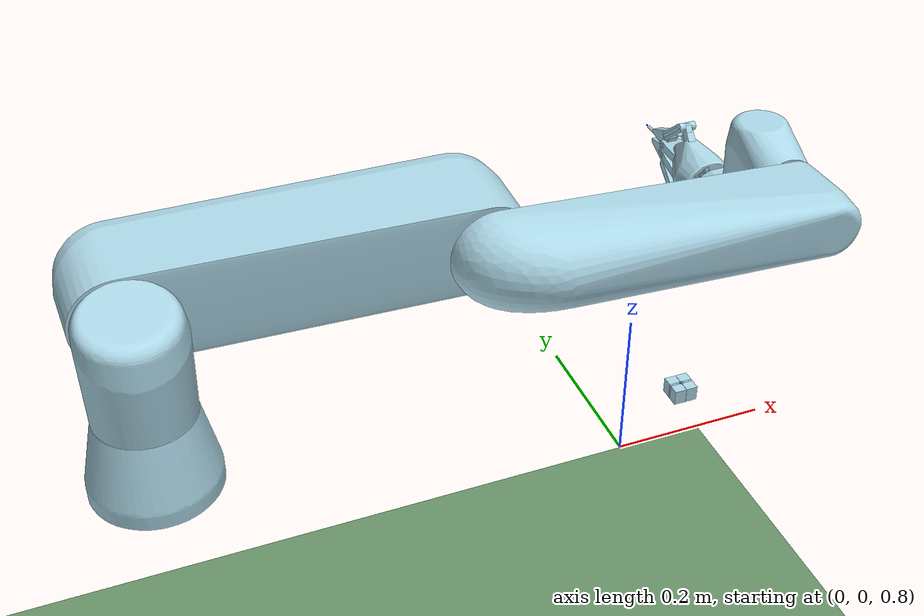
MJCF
<?xml version="1.0" encoding="UTF-8"?><mujoco model="runtime_model"><compiler coordinate="global"/><default><geom solimp="0.9 0.95 0.001 0.5 2 " solref="0.01 1.1 "/></default><asset><mesh name="2_2_16_33__0" vertex="-0.004 -0.088 -0.038 0 -0.088 -0.038 0.004 -0.088 -0.038 -0.004 -0.06 -0.038 0 -0.06 -0.038 0.004 -0.06 -0.038 -0.004 -0.058 -0.038 0 -0.058 -0.038 0.004 -0.058 -0.038 -0.006 -0.09 -0.036 0 -0.09 -0.036 0.006 -0.09 -0.036 -0.01 -0.088 -0.036 -0.006 -0.088 -0.036 0 -0.088 -0.036 0.006 -0.088 -0.036 0.01 -0.088 -0.036 -0.014 -0.06 -0.036 -0.01 -0.06 -0.036 -0.006 -0.06 -0.036 0.006 -0.06 -0.036 0.01 -0.06 -0.036 0.014 -0.06 -0.036 -0.01 -0.058 -0.036 0.01 -0.058 -0.036 -0.008 -0.056 -0.036 -0.004 -0.056 -0.036 0 -0.056 -0.036 0.004 -0.056 -0.036 0.008 -0.056 -0.036 -0.014 -0.09 -0.034 -0.01 -0.09 -0.034 -0.006 -0.09 -0.034 0 -0.09 -0.034 0.006 -0.09 -0.034 0.01 -0.09 -0.034 0.014 -0.09 -0.034 -0.018 -0.088 -0.034 -0.014 -0.088 -0.034 -0.01 -0.088 -0.034 0.01 -0.088 -0.034 0.014 -0.088 -0.034 0.018 -0.088 -0.034 -0.018 -0.06 -0.034 -0.014 -0.06 -0.034 0.014 -0.06 -0.034 0.018 -0.06 -0.034 -0.014 -0.058 -0.034 0.014 -0.058 -0.034 -0.014 -0.056 -0.034 -0.012 -0.056 -0.034 -0.008 -0.056 -0.034 0.008 -0.056 -0.034 0.012 -0.056 -0.034 0.014 -0.056 -0.034 -0.008 -0.054 -0.034 -0.004 -0.054 -0.034 0 -0.054 -0.034 0.004 -0.054 -0.034 0.008 -0.054 -0.034 -0.016 -0.09 -0.032 -0.014 -0.09 -0.032 -0.012 -0.09 -0.032 0.012 -0.09 -0.032 0.014 -0.09 -0.032 0.016 -0.09 -0.032 -0.02 -0.088 -0.032 -0.016 -0.088 -0.032 0.016 -0.088 -0.032 0.02 -0.088 -0.032 -0.02 -0.06 -0.032 0.02 -0.06 -0.032 -0.018 -0.058 -0.032 0.018 -0.058 -0.032 -0.018 -0.056 -0.032 -0.016 -0.056 -0.032 0.016 -0.056 -0.032 0.018 -0.056 -0.032 -0.012 -0.054 -0.032 -0.008 -0.054 -0.032 -0.004 -0.054 -0.032 0 -0.054 -0.032 0.004 -0.054 -0.032 0.008 -0.054 -0.032 0.012 -0.054 -0.032 -0.02 -0.09 -0.03 -0.018 -0.09 -0.03 -0.016 -0.09 -0.03 0.016 -0.09 -0.03 0.018 -0.09 -0.03 0.02 -0.09 -0.03 -0.024 -0.088 -0.03 -0.02 -0.088 -0.03 0.02 -0.088 -0.03 0.024 -0.088 -0.03 -0.024 -0.06 -0.03 -0.022 -0.06 -0.03 0.022 -0.06 -0.03 0.024 -0.06 -0.03 -0.022 -0.058 -0.03 0.022 -0.058 -0.03 -0.022 -0.056 -0.03 -0.02 -0.056 -0.03 0.02 -0.056 -0.03 0.022 -0.056 -0.03 -0.016 -0.054 -0.03 -0.012 -0.054 -0.03 -0.01 -0.054 -0.03 -0.008 -0.054 -0.03 -0.006 -0.054 -0.03 0.006 -0.054 -0.03 0.008 -0.054 -0.03 0.01 -0.054 -0.03 0.012 -0.054 -0.03 0.016 -0.054 -0.03 -0.022 -0.09 -0.028 0.022 -0.09 -0.028 -0.026 -0.088 -0.028 -0.022 -0.088 -0.028 0.022 -0.088 -0.028 -0.026 -0.06 -0.028 0.026 -0.06 -0.028 -0.026 -0.058 -0.028 0.026 -0.058 -0.028 -0.024 -0.056 -0.028 0.024 -0.056 -0.028 -0.02 -0.054 -0.028 -0.014 -0.054 -0.028 0.014 -0.054 -0.028 0.02 -0.054 -0.028 -0.026 -0.09 -0.026 -0.024 -0.09 -0.026 -0.022 -0.09 -0.026 0.022 -0.09 -0.026 0.026 -0.09 -0.026 -0.026 -0.088 -0.026 -0.024 -0.088 -0.026 0.026 -0.088 -0.026 0.026 -0.06 -0.026 -0.024 -0.056 -0.026 0.024 -0.056 -0.026 -0.024 -0.054 -0.026 -0.02 -0.054 -0.026 -0.018 -0.054 -0.026 -0.016 -0.054 -0.026 0.016 -0.054 -0.026 0.018 -0.054 -0.026 0.02 -0.054 -0.026 0.024 -0.054 -0.026 -0.024 -0.09 -0.024 -0.022 -0.09 -0.024 0.022 -0.09 -0.024 0.024 -0.09 -0.024 -0.03 -0.088 -0.024 0.03 -0.088 -0.024 -0.028 -0.06 -0.024 0.028 -0.06 -0.024 0.03 -0.06 -0.024 -0.028 -0.058 -0.024 0.028 -0.058 -0.024 -0.028 -0.056 -0.024 0.028 -0.056 -0.024 -0.022 -0.054 -0.024 -0.02 -0.054 -0.024 0.02 -0.054 -0.024 0.022 -0.054 -0.024 -0.028 -0.09 -0.022 0.028 -0.09 -0.022 -0.03 -0.088 -0.022 -0.028 -0.088 -0.022 0.028 -0.088 -0.022 -0.028 -0.062 -0.022 0.028 -0.062 -0.022 -0.032 -0.06 -0.022 -0.03 -0.06 -0.022 0.032 -0.06 -0.022 -0.028 -0.054 -0.022 -0.026 -0.054 -0.022 -0.022 -0.054 -0.022 0.022 -0.054 -0.022 0.026 -0.054 -0.022 0.028 -0.054 -0.022 -0.03 -0.09 -0.02 0.03 -0.09 -0.02 -0.032 -0.088 -0.02 -0.03 -0.088 -0.02 0.03 -0.088 -0.02 0.032 -0.088 -0.02 -0.03 -0.062 -0.02 -0.028 -0.062 -0.02 -0.026 -0.062 -0.02 -0.024 -0.062 -0.02 0.024 -0.062 -0.02 0.026 -0.062 -0.02 0.028 -0.062 -0.02 0.03 -0.062 -0.02 0.032 -0.06 -0.02 -0.032 -0.058 -0.02 -0.03 -0.058 -0.02 0.03 -0.058 -0.02 0.032 -0.058 -0.02 -0.032 -0.056 -0.02 -0.03 -0.056 -0.02 -0.028 -0.056 -0.02 0.028 -0.056 -0.02 0.03 -0.056 -0.02 0.032 -0.056 -0.02 -0.026 -0.054 -0.02 -0.024 -0.054 -0.02 0.024 -0.054 -0.02 0.026 -0.054 -0.02 -0.03 -0.09 -0.018 -0.028 -0.09 -0.018 -0.026 -0.09 -0.018 -0.024 -0.09 -0.018 0.024 -0.09 -0.018 0.026 -0.09 -0.018 0.028 -0.09 -0.018 0.03 -0.09 -0.018 -0.034 -0.088 -0.018 0.034 -0.088 -0.018 -0.032 -0.062 -0.018 -0.03 -0.062 -0.018 -0.028 -0.062 -0.018 -0.026 -0.062 -0.018 -0.024 -0.062 -0.018 -0.022 -0.062 -0.018 0.022 -0.062 -0.018 0.024 -0.062 -0.018 0.026 -0.062 -0.018 0.028 -0.062 -0.018 0.03 -0.062 -0.018 0.032 -0.062 -0.018 -0.034 -0.06 -0.018 -0.032 -0.06 -0.018 0.032 -0.06 -0.018 0.034 -0.06 -0.018 -0.032 -0.058 -0.018 0.032 -0.058 -0.018 -0.032 -0.056 -0.018 0.032 -0.056 -0.018 -0.022 -0.054 -0.018 0.022 -0.054 -0.018 -0.032 -0.09 -0.016 -0.03 -0.09 -0.016 -0.024 -0.09 -0.016 0.024 -0.09 -0.016 0.03 -0.09 -0.016 0.032 -0.09 -0.016 -0.032 -0.088 -0.016 0.032 -0.088 -0.016 -0.032 -0.062 -0.016 -0.03 -0.062 -0.016 -0.024 -0.062 -0.016 -0.022 -0.062 -0.016 0.022 -0.062 -0.016 0.024 -0.062 -0.016 0.03 -0.062 -0.016 0.032 -0.062 -0.016 -0.034 -0.06 -0.016 0.034 -0.06 -0.016 0.034 -0.058 -0.016 -0.032 -0.056 -0.016 0.032 -0.056 -0.016 0.034 -0.056 -0.016 -0.022 -0.054 -0.016 0.022 -0.054 -0.016 -0.034 -0.09 -0.014 -0.032 -0.09 -0.014 -0.03 -0.09 -0.014 -0.028 -0.09 -0.014 -0.026 -0.09 -0.014 -0.024 -0.09 -0.014 0.024 -0.09 -0.014 0.026 -0.09 -0.014 0.028 -0.09 -0.014 0.03 -0.09 -0.014 0.032 -0.09 -0.014 0.034 -0.09 -0.014 -0.034 -0.088 -0.014 0.034 -0.088 -0.014 -0.032 -0.062 -0.014 -0.03 -0.062 -0.014 -0.028 -0.062 -0.014 -0.026 -0.062 -0.014 -0.024 -0.062 -0.014 -0.022 -0.062 -0.014 0.022 -0.062 -0.014 0.024 -0.062 -0.014 0.026 -0.062 -0.014 0.028 -0.062 -0.014 0.03 -0.062 -0.014 0.032 -0.062 -0.014 -0.036 -0.058 -0.014 0.034 -0.058 -0.014 -0.034 -0.056 -0.014 -0.032 -0.056 -0.014 0.032 -0.056 -0.014 0.034 -0.056 -0.014 -0.022 -0.054 -0.014 0.022 -0.054 -0.014 -0.024 -0.052 -0.014 -0.022 -0.052 -0.014 0.022 -0.052 -0.014 -0.034 -0.09 -0.012 -0.026 -0.09 -0.012 -0.024 -0.09 -0.012 0.024 -0.09 -0.012 0.026 -0.09 -0.012 -0.036 -0.088 -0.012 -0.034 -0.088 -0.012 -0.03 -0.062 -0.012 -0.028 -0.062 -0.012 -0.026 -0.062 -0.012 -0.024 -0.062 -0.012 0.024 -0.062 -0.012 0.026 -0.062 -0.012 0.028 -0.062 -0.012 0.03 -0.062 -0.012 -0.036 -0.058 -0.012 0.036 -0.058 -0.012 -0.036 -0.056 -0.012 -0.03 -0.056 -0.012 0.028 -0.056 -0.012 0.03 -0.056 -0.012 -0.036 -0.054 -0.012 -0.034 -0.054 -0.012 -0.028 -0.054 -0.012 0.028 -0.054 -0.012 0.036 -0.054 -0.012 -0.028 -0.052 -0.012 -0.024 -0.052 -0.012 0.024 -0.052 -0.012 0.028 -0.052 -0.012 -0.028 -0.05 -0.012 -0.026 -0.05 -0.012 -0.024 -0.05 -0.012 0.024 -0.05 -0.012 0.026 -0.05 -0.012 0.028 -0.05 -0.012 -0.032 -0.048 -0.012 -0.03 -0.048 -0.012 -0.028 -0.048 -0.012 0.028 -0.048 -0.012 0.03 -0.048 -0.012 0.032 -0.048 -0.012 0.016 -0.046 -0.012 0.02 -0.046 -0.012 -0.032 -0.044 -0.012 -0.02 -0.044 -0.012 -0.018 -0.044 -0.012 -0.016 -0.044 -0.012 -0.014 -0.044 -0.012 -0.012 -0.044 -0.012 -0.01 -0.044 -0.012 -0.006 -0.044 -0.012 -0.004 -0.044 -0.012 -0.002 -0.044 -0.012 0 -0.044 -0.012 0.002 -0.044 -0.012 0.004 -0.044 -0.012 0.006 -0.044 -0.012 0.008 -0.044 -0.012 0.01 -0.044 -0.012 0.012 -0.044 -0.012 0.014 -0.044 -0.012 0.016 -0.044 -0.012 0.02 -0.044 -0.012 0.032 -0.044 -0.012 -0.034 -0.042 -0.012 -0.032 -0.042 -0.012 -0.02 -0.042 -0.012 -0.018 -0.042 -0.012 -0.016 -0.042 -0.012 -0.014 -0.042 -0.012 -0.012 -0.042 -0.012 -0.01 -0.042 -0.012 -0.008 -0.042 -0.012 -0.006 -0.042 -0.012 -0.004 -0.042 -0.012 -0.002 -0.042 -0.012 0 -0.042 -0.012 0.002 -0.042 -0.012 0.004 -0.042 -0.012 0.006 -0.042 -0.012 0.008 -0.042 -0.012 0.01 -0.042 -0.012 0.012 -0.042 -0.012 0.014 -0.042 -0.012 0.018 -0.042 -0.012 0.032 -0.042 -0.012 0.034 -0.042 -0.012 -0.02 -0.04 -0.012 -0.018 -0.04 -0.012 -0.016 -0.04 -0.012 -0.014 -0.04 -0.012 -0.012 -0.04 -0.012 -0.008 -0.04 -0.012 -0.006 -0.04 -0.012 -0.004 -0.04 -0.012 -0.002 -0.04 -0.012 -0 -0.04 -0.012 0.002 -0.04 -0.012 0.004 -0.04 -0.012 0.006 -0.04 -0.012 0.008 -0.04 -0.012 0.01 -0.04 -0.012 0.012 -0.04 -0.012 0.014 -0.04 -0.012 0.018 -0.04 -0.012 0.02 -0.04 -0.012 -0.036 -0.038 -0.012 -0.02 -0.038 -0.012 -0.018 -0.038 -0.012 -0.016 -0.038 -0.012 -0.014 -0.038 -0.012 -0.012 -0.038 -0.012 -0.01 -0.038 -0.012 -0.008 -0.038 -0.012 -0.006 -0.038 -0.012 -0.004 -0.038 -0.012 -0.002 -0.038 -0.012 0 -0.038 -0.012 0.002 -0.038 -0.012 0.004 -0.038 -0.012 0.006 -0.038 -0.012 0.008 -0.038 -0.012 0.01 -0.038 -0.012 0.012 -0.038 -0.012 0.014 -0.038 -0.012 0.016 -0.038 -0.012 0.018 -0.038 -0.012 0.036 -0.038 -0.012 -0.036 -0.036 -0.012 -0.016 -0.036 -0.012 -0.014 -0.036 -0.012 -0.012 -0.036 -0.012 -0.01 -0.036 -0.012 0.01 -0.036 -0.012 0.012 -0.036 -0.012 0.014 -0.036 -0.012 0.016 -0.036 -0.012 0.018 -0.036 -0.012 0.036 -0.036 -0.012 -0.036 -0.034 -0.012 -0.018 -0.034 -0.012 -0.016 -0.034 -0.012 -0.008 -0.034 -0.012 0.008 -0.034 -0.012 0.016 -0.034 -0.012 0.018 -0.034 -0.012 0.036 -0.034 -0.012 -0.036 -0.032 -0.012 -0.02 -0.032 -0.012 -0.006 -0.032 -0.012 0.006 -0.032 -0.012 0.02 -0.032 -0.012 0.036 -0.032 -0.012 -0.02 -0.028 -0.012 -0.006 -0.028 -0.012 0.006 -0.028 -0.012 0.02 -0.028 -0.012 -0.02 -0.026 -0.012 -0.006 -0.026 -0.012 0.006 -0.026 -0.012 0.02 -0.026 -0.012 -0.02 -0.024 -0.012 -0.018 -0.024 -0.012 -0.008 -0.024 -0.012 -0.006 -0.024 -0.012 0.006 -0.024 -0.012 0.008 -0.024 -0.012 0.018 -0.024 -0.012 0.02 -0.024 -0.012 -0.016 -0.022 -0.012 -0.014 -0.022 -0.012 -0.012 -0.022 -0.012 -0.01 -0.022 -0.012 0.01 -0.022 -0.012 0.012 -0.022 -0.012 0.014 -0.022 -0.012 0.016 -0.022 -0.012 -0.02 -0.01 -0.012 0.02 -0.01 -0.012 -0.018 -0.008 -0.012 -0.016 -0.008 -0.012 0.016 -0.008 -0.012 0.018 -0.008 -0.012 -0.014 -0.006 -0.012 -0.012 -0.006 -0.012 0.012 -0.006 -0.012 0.014 -0.006 -0.012 -0.034 -0.09 -0.01 -0.032 -0.09 -0.01 -0.03 -0.09 -0.01 -0.028 -0.09 -0.01 -0.026 -0.09 -0.01 0.026 -0.09 -0.01 0.028 -0.09 -0.01 0.03 -0.09 -0.01 0.032 -0.09 -0.01 0.034 -0.09 -0.01 -0.036 -0.088 -0.01 -0.034 -0.088 -0.01 0.034 -0.088 -0.01 0.036 -0.088 -0.01 -0.036 -0.056 -0.01 0.036 -0.056 -0.01 -0.036 -0.054 -0.01 0.036 -0.054 -0.01 -0.036 -0.052 -0.01 0.036 -0.052 -0.01 -0.036 -0.05 -0.01 0.036 -0.05 -0.01 -0.036 -0.048 -0.01 -0.034 -0.048 -0.01 0.034 -0.048 -0.01 0.036 -0.048 -0.01 -0.036 -0.046 -0.01 0.036 -0.046 -0.01 -0.034 -0.044 -0.01 0.034 -0.044 -0.01 -0.038 -0.042 -0.01 -0.036 -0.042 -0.01 -0.034 -0.042 -0.01 0.034 -0.042 -0.01 0.036 -0.042 -0.01 0.038 -0.042 -0.01 -0.038 -0.04 -0.01 0.038 -0.04 -0.01 -0.04 -0.038 -0.01 -0.038 -0.038 -0.01 -0.036 -0.038 -0.01 0.036 -0.038 -0.01 0.038 -0.038 -0.01 0.04 -0.038 -0.01 -0.038 -0.036 -0.01 0.038 -0.036 -0.01 0.04 -0.036 -0.01 -0.04 -0.034 -0.01 -0.038 -0.034 -0.01 0.038 -0.034 -0.01 -0.04 -0.032 -0.01 -0.038 -0.032 -0.01 0.038 -0.032 -0.01 0.04 -0.032 -0.01 -0.038 -0.03 -0.01 -0.036 -0.03 -0.01 0.036 -0.03 -0.01 0.038 -0.03 -0.01 0.04 -0.03 -0.01 -0.02 -0.01 -0.01 0.02 -0.01 -0.01 -0.024 -0.008 -0.01 -0.022 -0.008 -0.01 -0.02 -0.008 -0.01 0.02 -0.008 -0.01 0.022 -0.008 -0.01 0.024 -0.008 -0.01 -0.022 -0.006 -0.01 -0.02 -0.006 -0.01 -0.018 -0.006 -0.01 0.018 -0.006 -0.01 0.02 -0.006 -0.01 0.022 -0.006 -0.01 -0.018 -0.004 -0.01 -0.016 -0.004 -0.01 -0.012 -0.004 -0.01 0.012 -0.004 -0.01 0.016 -0.004 -0.01 0.018 -0.004 -0.01 -0.016 -0.002 -0.01 0.016 -0.002 -0.01 -0.034 -0.09 -0.008 -0.032 -0.09 -0.008 0.032 -0.09 -0.008 0.034 -0.09 -0.008 -0.034 -0.056 -0.008 -0.032 -0.056 -0.008 -0.03 -0.056 -0.008 0.028 -0.056 -0.008 0.03 -0.056 -0.008 0.032 -0.056 -0.008 0.034 -0.056 -0.008 -0.036 -0.054 -0.008 -0.034 -0.054 -0.008 -0.03 -0.054 -0.008 -0.028 -0.054 -0.008 0.028 -0.054 -0.008 0.03 -0.054 -0.008 0.034 -0.054 -0.008 0.036 -0.054 -0.008 -0.036 -0.052 -0.008 -0.028 -0.052 -0.008 0.028 -0.052 -0.008 0.036 -0.052 -0.008 -0.036 -0.05 -0.008 -0.034 -0.05 -0.008 -0.028 -0.05 -0.008 0.028 -0.05 -0.008 0.034 -0.05 -0.008 0.036 -0.05 -0.008 -0.038 -0.048 -0.008 -0.036 -0.048 -0.008 -0.034 -0.048 -0.008 -0.032 -0.048 -0.008 -0.03 -0.048 -0.008 -0.028 -0.048 -0.008 0.028 -0.048 -0.008 0.03 -0.048 -0.008 0.032 -0.048 -0.008 0.034 -0.048 -0.008 0.036 -0.048 -0.008 0.038 -0.048 -0.008 -0.038 -0.046 -0.008 0.038 -0.046 -0.008 -0.038 -0.044 -0.008 0.038 -0.044 -0.008 -0.04 -0.042 -0.008 0.04 -0.042 -0.008 -0.04 -0.04 -0.008 -0.042 -0.038 -0.008 0.04 -0.038 -0.008 0.042 -0.036 -0.008 -0.042 -0.034 -0.008 0.042 -0.032 -0.008 -0.04 -0.03 -0.008 0.04 -0.03 -0.008 -0.04 -0.028 -0.008 0.04 -0.028 -0.008 -0.024 -0.008 -0.008 0.024 -0.008 -0.008 -0.024 -0.006 -0.008 0.024 -0.006 -0.008 -0.022 -0.004 -0.008 0.022 -0.004 -0.008 -0.018 -0.002 -0.008 -0.016 -0.002 -0.008 0.016 -0.002 -0.008 0.018 -0.002 -0.008 -0.036 -0.09 -0.006 -0.034 -0.09 -0.006 0.034 -0.09 -0.006 0.036 -0.09 -0.006 -0.038 -0.088 -0.006 -0.036 -0.088 -0.006 0.036 -0.088 -0.006 -0.038 -0.052 -0.006 -0.036 -0.052 -0.006 0.036 -0.052 -0.006 0.038 -0.052 -0.006 -0.038 -0.05 -0.006 0.038 -0.05 -0.006 -0.038 -0.048 -0.006 0.038 -0.048 -0.006 -0.038 -0.046 -0.006 0.038 -0.046 -0.006 -0.04 -0.044 -0.006 -0.038 -0.044 -0.006 0.038 -0.044 -0.006 0.04 -0.044 -0.006 -0.04 -0.042 -0.006 -0.034 -0.042 -0.006 -0.032 -0.042 -0.006 -0.03 -0.042 -0.006 -0.028 -0.042 -0.006 -0.026 -0.042 -0.006 0.026 -0.042 -0.006 0.028 -0.042 -0.006 0.03 -0.042 -0.006 0.032 -0.042 -0.006 0.034 -0.042 -0.006 0.04 -0.042 -0.006 -0.042 -0.04 -0.006 -0.038 -0.04 -0.006 -0.036 -0.04 -0.006 -0.026 -0.04 -0.006 -0.024 -0.04 -0.006 0.024 -0.04 -0.006 0.026 -0.04 -0.006 0.036 -0.04 -0.006 0.038 -0.04 -0.006 -0.042 -0.038 -0.006 -0.038 -0.038 -0.006 -0.024 -0.038 -0.006 0.024 -0.038 -0.006 0.038 -0.038 -0.006 0.042 -0.038 -0.006 -0.042 -0.036 -0.006 -0.038 -0.036 -0.006 -0.024 -0.036 -0.006 0.024 -0.036 -0.006 0.038 -0.036 -0.006 0.042 -0.036 -0.006 -0.042 -0.034 -0.006 -0.042 -0.032 -0.006 -0.038 -0.032 -0.006 -0.024 -0.032 -0.006 0.024 -0.032 -0.006 0.038 -0.032 -0.006 0.042 -0.032 -0.006 -0.042 -0.03 -0.006 -0.036 -0.03 -0.006 -0.026 -0.03 -0.006 0.026 -0.03 -0.006 0.036 -0.03 -0.006 0.042 -0.03 -0.006 -0.04 -0.028 -0.006 -0.034 -0.028 -0.006 -0.032 -0.028 -0.006 -0.03 -0.028 -0.006 -0.028 -0.028 -0.006 -0.026 -0.028 -0.006 0.026 -0.028 -0.006 0.028 -0.028 -0.006 0.03 -0.028 -0.006 0.032 -0.028 -0.006 0.034 -0.028 -0.006 0.04 -0.028 -0.006 -0.024 -0.006 -0.006 0.024 -0.006 -0.006 -0.022 -0.004 -0.006 0.022 -0.004 -0.006 -0.02 -0.002 -0.006 0.02 -0.002 -0.006 -0.016 -0 -0.006 0.016 -0 -0.006 -0.034 -0.09 -0.004 0.034 -0.09 -0.004 -0.038 -0.088 -0.004 0.038 -0.088 -0.004 -0.038 -0.052 -0.004 0.038 -0.052 -0.004 -0.038 -0.05 -0.004 0.038 -0.05 -0.004 -0.038 -0.046 -0.004 0.038 -0.046 -0.004 -0.04 -0.044 -0.004 -0.038 -0.044 -0.004 0.038 -0.044 -0.004 0.04 -0.044 -0.004 -0.04 -0.042 -0.004 -0.036 -0.042 -0.004 0.036 -0.042 -0.004 0.04 -0.042 -0.004 -0.042 -0.04 -0.004 -0.038 -0.04 -0.004 -0.036 -0.04 -0.004 0.036 -0.04 -0.004 0.042 -0.04 -0.004 -0.042 -0.038 -0.004 -0.038 -0.038 -0.004 0.038 -0.038 -0.004 0.042 -0.038 -0.004 -0.042 -0.036 -0.004 -0.038 -0.036 -0.004 0.038 -0.036 -0.004 0.042 -0.036 -0.004 -0.042 -0.034 -0.004 -0.038 -0.034 -0.004 0.038 -0.034 -0.004 -0.042 -0.032 -0.004 -0.038 -0.032 -0.004 0.038 -0.032 -0.004 0.042 -0.032 -0.004 -0.042 -0.03 -0.004 -0.036 -0.03 -0.004 0.036 -0.03 -0.004 0.042 -0.03 -0.004 -0.04 -0.028 -0.004 -0.034 -0.028 -0.004 -0.032 -0.028 -0.004 -0.03 -0.028 -0.004 0.03 -0.028 -0.004 0.032 -0.028 -0.004 0.034 -0.028 -0.004 0.04 -0.028 -0.004 -0.03 -0.018 -0.004 0.03 -0.018 -0.004 -0.03 -0.016 -0.004 0.03 -0.016 -0.004 -0.03 -0.014 -0.004 0.03 -0.014 -0.004 -0.028 -0.012 -0.004 0.028 -0.012 -0.004 -0.028 -0.01 -0.004 0.028 -0.01 -0.004 -0.024 -0.006 -0.004 0.024 -0.006 -0.004 -0.024 -0.004 -0.004 -0.022 -0.004 -0.004 0.022 -0.004 -0.004 0.024 -0.004 -0.004 -0.02 -0.002 -0.004 0.02 -0.002 -0.004 -0.016 -0 -0.004 0.016 -0 -0.004 -0.036 -0.09 0 -0.034 -0.09 0 0.034 -0.09 0 0.036 -0.09 0 -0.038 -0.088 0 -0.036 -0.088 0 0.036 -0.088 0 0.038 -0.088 0 -0.038 -0.052 0 0.038 -0.052 0 -0.038 -0.046 0 0.038 -0.046 0 -0.038 -0.044 0 0.038 -0.044 0 -0.036 -0.042 0 0.036 -0.042 0 -0.036 -0.04 0 0.036 -0.04 0 -0.03 -0.028 0 0.03 -0.028 0 -0.03 -0.018 0 0.03 -0.018 0 -0.03 -0.016 0 0.03 -0.016 0 -0.03 -0.014 0 0.03 -0.014 0 -0.028 -0.012 0 0.028 -0.012 0 -0.028 -0.01 0 0.028 -0.01 0 -0.024 -0.006 0 0.024 -0.006 0 -0.024 -0.004 0 -0.022 -0.004 0 -0.016 -0.004 0 0.016 -0.004 0 0.022 -0.004 0 0.024 -0.004 0 -0.02 -0.002 0 0.02 -0.002 0 -0.016 -0 0 0.016 -0 0 -0.034 -0.09 0.004 0.034 -0.09 0.004 -0.038 -0.088 0.004 0.038 -0.088 0.004 -0.038 -0.052 0.004 0.038 -0.052 0.004 -0.038 -0.05 0.004 0.038 -0.05 0.004 -0.038 -0.046 0.004 0.038 -0.046 0.004 -0.04 -0.044 0.004 -0.038 -0.044 0.004 0.038 -0.044 0.004 0.04 -0.044 0.004 -0.04 -0.042 0.004 -0.036 -0.042 0.004 0.036 -0.042 0.004 0.04 -0.042 0.004 -0.042 -0.04 0.004 -0.038 -0.04 0.004 -0.036 -0.04 0.004 0.036 -0.04 0.004 0.042 -0.04 0.004 -0.042 -0.038 0.004 -0.038 -0.038 0.004 0.038 -0.038 0.004 0.042 -0.038 0.004 -0.042 -0.036 0.004 -0.038 -0.036 0.004 0.038 -0.036 0.004 0.042 -0.036 0.004 -0.038 -0.034 0.004 0.038 -0.034 0.004 0.042 -0.034 0.004 -0.042 -0.032 0.004 -0.038 -0.032 0.004 0.038 -0.032 0.004 0.042 -0.032 0.004 -0.042 -0.03 0.004 -0.036 -0.03 0.004 0.036 -0.03 0.004 0.042 -0.03 0.004 -0.04 -0.028 0.004 -0.034 -0.028 0.004 -0.032 -0.028 0.004 -0.03 -0.028 0.004 0.03 -0.028 0.004 0.032 -0.028 0.004 0.034 -0.028 0.004 0.04 -0.028 0.004 -0.03 -0.018 0.004 0.03 -0.018 0.004 -0.03 -0.016 0.004 0.03 -0.016 0.004 -0.03 -0.014 0.004 0.03 -0.014 0.004 -0.028 -0.012 0.004 0.028 -0.012 0.004 -0.028 -0.01 0.004 0.028 -0.01 0.004 -0.024 -0.006 0.004 0.024 -0.006 0.004 -0.024 -0.004 0.004 -0.022 -0.004 0.004 0.022 -0.004 0.004 0.024 -0.004 0.004 -0.02 -0.002 0.004 0.02 -0.002 0.004 -0.016 -0 0.004 0.016 -0 0.004 -0.036 -0.09 0.006 -0.034 -0.09 0.006 0.034 -0.09 0.006 0.036 -0.09 0.006 -0.036 -0.088 0.006 0.036 -0.088 0.006 0.038 -0.088 0.006 -0.038 -0.052 0.006 -0.036 -0.052 0.006 0.036 -0.052 0.006 0.038 -0.052 0.006 -0.038 -0.05 0.006 0.038 -0.05 0.006 -0.038 -0.048 0.006 0.038 -0.048 0.006 -0.038 -0.046 0.006 0.038 -0.046 0.006 -0.04 -0.044 0.006 -0.038 -0.044 0.006 0.038 -0.044 0.006 0.04 -0.044 0.006 -0.04 -0.042 0.006 -0.034 -0.042 0.006 -0.032 -0.042 0.006 -0.03 -0.042 0.006 -0.028 -0.042 0.006 -0.026 -0.042 0.006 0.026 -0.042 0.006 0.028 -0.042 0.006 0.03 -0.042 0.006 0.032 -0.042 0.006 0.034 -0.042 0.006 0.04 -0.042 0.006 -0.038 -0.04 0.006 -0.036 -0.04 0.006 -0.026 -0.04 0.006 -0.024 -0.04 0.006 0.024 -0.04 0.006 0.026 -0.04 0.006 0.036 -0.04 0.006 0.038 -0.04 0.006 0.042 -0.04 0.006 -0.042 -0.038 0.006 -0.038 -0.038 0.006 -0.024 -0.038 0.006 0.024 -0.038 0.006 0.038 -0.038 0.006 0.042 -0.038 0.006 -0.042 -0.036 0.006 -0.038 -0.036 0.006 -0.024 -0.036 0.006 0.024 -0.036 0.006 0.038 -0.036 0.006 0.042 -0.036 0.006 0.042 -0.034 0.006 -0.042 -0.032 0.006 -0.038 -0.032 0.006 -0.024 -0.032 0.006 0.024 -0.032 0.006 0.038 -0.032 0.006 0.042 -0.032 0.006 -0.042 -0.03 0.006 -0.036 -0.03 0.006 -0.026 -0.03 0.006 0.026 -0.03 0.006 0.036 -0.03 0.006 0.042 -0.03 0.006 -0.04 -0.028 0.006 -0.034 -0.028 0.006 -0.032 -0.028 0.006 -0.03 -0.028 0.006 -0.028 -0.028 0.006 -0.026 -0.028 0.006 0.026 -0.028 0.006 0.028 -0.028 0.006 0.03 -0.028 0.006 0.032 -0.028 0.006 0.034 -0.028 0.006 0.04 -0.028 0.006 -0.024 -0.006 0.006 0.024 -0.006 0.006 -0.022 -0.004 0.006 0.022 -0.004 0.006 -0.02 -0.002 0.006 0.02 -0.002 0.006 -0.016 -0 0.006 0.016 -0 0.006 -0.034 -0.09 0.008 -0.032 -0.09 0.008 0.032 -0.09 0.008 0.034 -0.09 0.008 -0.034 -0.056 0.008 -0.032 -0.056 0.008 -0.03 -0.056 0.008 0.03 -0.056 0.008 0.032 -0.056 0.008 0.034 -0.056 0.008 -0.036 -0.054 0.008 -0.034 -0.054 0.008 -0.03 -0.054 0.008 -0.028 -0.054 0.008 0.028 -0.054 0.008 0.034 -0.054 0.008 0.036 -0.054 0.008 -0.036 -0.052 0.008 -0.028 -0.052 0.008 0.028 -0.052 0.008 0.036 -0.052 0.008 -0.036 -0.05 0.008 -0.034 -0.05 0.008 -0.028 -0.05 0.008 0.028 -0.05 0.008 0.034 -0.05 0.008 0.036 -0.05 0.008 -0.038 -0.048 0.008 -0.036 -0.048 0.008 -0.034 -0.048 0.008 -0.032 -0.048 0.008 -0.03 -0.048 0.008 -0.028 -0.048 0.008 0.028 -0.048 0.008 0.03 -0.048 0.008 0.032 -0.048 0.008 0.034 -0.048 0.008 0.036 -0.048 0.008 0.038 -0.048 0.008 -0.038 -0.046 0.008 0.038 -0.046 0.008 -0.038 -0.044 0.008 0.038 -0.044 0.008 -0.04 -0.042 0.008 0.04 -0.042 0.008 0.04 -0.04 0.008 -0.04 -0.038 0.008 0.042 -0.038 0.008 -0.042 -0.036 0.008 0.042 -0.034 0.008 -0.042 -0.032 0.008 -0.04 -0.03 0.008 0.04 -0.03 0.008 -0.04 -0.028 0.008 0.04 -0.028 0.008 -0.024 -0.006 0.008 0.024 -0.006 0.008 -0.022 -0.004 0.008 0.022 -0.004 0.008 -0.018 -0.002 0.008 -0.016 -0.002 0.008 0.016 -0.002 0.008 0.018 -0.002 0.008 -0.034 -0.09 0.01 -0.032 -0.09 0.01 -0.03 -0.09 0.01 -0.028 -0.09 0.01 -0.026 -0.09 0.01 0.026 -0.09 0.01 0.028 -0.09 0.01 0.03 -0.09 0.01 0.032 -0.09 0.01 0.034 -0.09 0.01 -0.036 -0.088 0.01 -0.034 -0.088 0.01 0.034 -0.088 0.01 0.036 -0.088 0.01 -0.036 -0.056 0.01 0.036 -0.056 0.01 -0.036 -0.054 0.01 0.036 -0.054 0.01 -0.036 -0.052 0.01 0.036 -0.052 0.01 -0.036 -0.05 0.01 0.036 -0.05 0.01 -0.036 -0.048 0.01 -0.034 -0.048 0.01 0.034 -0.048 0.01 0.036 -0.048 0.01 -0.036 -0.046 0.01 0.036 -0.046 0.01 -0.034 -0.044 0.01 0.034 -0.044 0.01 -0.038 -0.042 0.01 -0.036 -0.042 0.01 -0.034 -0.042 0.01 0.034 -0.042 0.01 0.036 -0.042 0.01 0.038 -0.042 0.01 -0.038 -0.04 0.01 0.038 -0.04 0.01 -0.04 -0.038 0.01 -0.038 -0.038 0.01 -0.036 -0.038 0.01 0.036 -0.038 0.01 0.038 -0.038 0.01 0.04 -0.038 0.01 -0.04 -0.036 0.01 -0.038 -0.036 0.01 0.038 -0.036 0.01 -0.038 -0.034 0.01 0.038 -0.034 0.01 0.04 -0.034 0.01 -0.04 -0.032 0.01 -0.038 -0.032 0.01 0.038 -0.032 0.01 0.04 -0.032 0.01 -0.04 -0.03 0.01 -0.038 -0.03 0.01 -0.036 -0.03 0.01 0.036 -0.03 0.01 0.038 -0.03 0.01 -0.02 -0.01 0.01 0.02 -0.01 0.01 -0.024 -0.008 0.01 -0.022 -0.008 0.01 -0.02 -0.008 0.01 0.02 -0.008 0.01 0.022 -0.008 0.01 0.024 -0.008 0.01 -0.022 -0.006 0.01 -0.02 -0.006 0.01 -0.018 -0.006 0.01 0.018 -0.006 0.01 0.02 -0.006 0.01 0.022 -0.006 0.01 -0.018 -0.004 0.01 -0.016 -0.004 0.01 -0.012 -0.004 0.01 0.012 -0.004 0.01 0.016 -0.004 0.01 0.018 -0.004 0.01 -0.016 -0.002 0.01 0.016 -0.002 0.01 -0.034 -0.09 0.012 -0.026 -0.09 0.012 -0.024 -0.09 0.012 0.024 -0.09 0.012 0.026 -0.09 0.012 0.034 -0.09 0.012 0.034 -0.088 0.012 0.036 -0.088 0.012 -0.03 -0.062 0.012 -0.028 -0.062 0.012 -0.026 -0.062 0.012 -0.024 -0.062 0.012 0.024 -0.062 0.012 0.026 -0.062 0.012 0.028 -0.062 0.012 0.03 -0.062 0.012 -0.036 -0.058 0.012 0.036 -0.058 0.012 -0.03 -0.056 0.012 0.03 -0.056 0.012 0.036 -0.056 0.012 -0.036 -0.054 0.012 -0.034 -0.054 0.012 -0.028 -0.054 0.012 0.028 -0.054 0.012 0.034 -0.054 0.012 0.036 -0.054 0.012 -0.028 -0.052 0.012 -0.024 -0.052 0.012 0.024 -0.052 0.012 0.028 -0.052 0.012 -0.028 -0.05 0.012 -0.026 -0.05 0.012 -0.024 -0.05 0.012 0.024 -0.05 0.012 0.026 -0.05 0.012 0.028 -0.05 0.012 -0.032 -0.048 0.012 -0.03 -0.048 0.012 -0.028 -0.048 0.012 0.028 -0.048 0.012 0.03 -0.048 0.012 0.032 -0.048 0.012 -0.02 -0.046 0.012 -0.016 -0.046 0.012 -0.032 -0.044 0.012 -0.02 -0.044 0.012 -0.016 -0.044 0.012 -0.014 -0.044 0.012 -0.012 -0.044 0.012 -0.01 -0.044 0.012 -0.008 -0.044 0.012 -0.006 -0.044 0.012 -0.004 -0.044 0.012 -0.002 -0.044 0.012 -0 -0.044 0.012 0.002 -0.044 0.012 0.004 -0.044 0.012 0.006 -0.044 0.012 0.01 -0.044 0.012 0.012 -0.044 0.012 0.014 -0.044 0.012 0.016 -0.044 0.012 0.018 -0.044 0.012 0.02 -0.044 0.012 0.032 -0.044 0.012 -0.034 -0.042 0.012 -0.032 -0.042 0.012 -0.018 -0.042 0.012 -0.014 -0.042 0.012 -0.012 -0.042 0.012 -0.01 -0.042 0.012 -0.008 -0.042 0.012 -0.006 -0.042 0.012 -0.004 -0.042 0.012 -0.002 -0.042 0.012 -0 -0.042 0.012 0.002 -0.042 0.012 0.004 -0.042 0.012 0.006 -0.042 0.012 0.008 -0.042 0.012 0.01 -0.042 0.012 0.012 -0.042 0.012 0.014 -0.042 0.012 0.016 -0.042 0.012 0.018 -0.042 0.012 0.02 -0.042 0.012 0.032 -0.042 0.012 0.034 -0.042 0.012 -0.02 -0.04 0.012 -0.018 -0.04 0.012 -0.014 -0.04 0.012 -0.012 -0.04 0.012 -0.01 -0.04 0.012 -0.008 -0.04 0.012 -0.006 -0.04 0.012 -0.004 -0.04 0.012 -0.002 -0.04 0.012 0 -0.04 0.012 0.002 -0.04 0.012 0.004 -0.04 0.012 0.006 -0.04 0.012 0.008 -0.04 0.012 0.012 -0.04 0.012 0.014 -0.04 0.012 0.016 -0.04 0.012 0.018 -0.04 0.012 0.02 -0.04 0.012 -0.036 -0.038 0.012 -0.018 -0.038 0.012 -0.016 -0.038 0.012 -0.014 -0.038 0.012 -0.012 -0.038 0.012 -0.01 -0.038 0.012 -0.008 -0.038 0.012 -0.006 -0.038 0.012 -0.004 -0.038 0.012 -0.002 -0.038 0.012 -0 -0.038 0.012 0.002 -0.038 0.012 0.004 -0.038 0.012 0.006 -0.038 0.012 0.008 -0.038 0.012 0.01 -0.038 0.012 0.012 -0.038 0.012 0.014 -0.038 0.012 0.016 -0.038 0.012 0.018 -0.038 0.012 0.02 -0.038 0.012 0.036 -0.038 0.012 -0.036 -0.036 0.012 -0.018 -0.036 0.012 -0.016 -0.036 0.012 -0.014 -0.036 0.012 -0.012 -0.036 0.012 -0.01 -0.036 0.012 0.01 -0.036 0.012 0.012 -0.036 0.012 0.014 -0.036 0.012 0.016 -0.036 0.012 0.036 -0.036 0.012 -0.036 -0.034 0.012 -0.018 -0.034 0.012 -0.008 -0.034 0.012 0.008 -0.034 0.012 0.018 -0.034 0.012 0.036 -0.034 0.012 -0.036 -0.032 0.012 -0.02 -0.032 0.012 -0.006 -0.032 0.012 0.006 -0.032 0.012 0.02 -0.032 0.012 0.036 -0.032 0.012 -0.006 -0.03 0.012 0.006 -0.03 0.012 0.02 -0.03 0.012 -0.02 -0.028 0.012 -0.006 -0.028 0.012 0.006 -0.028 0.012 0.02 -0.028 0.012 -0.02 -0.026 0.012 -0.006 -0.026 0.012 0.006 -0.026 0.012 0.02 -0.026 0.012 -0.02 -0.024 0.012 -0.018 -0.024 0.012 -0.008 -0.024 0.012 0.006 -0.024 0.012 0.018 -0.024 0.012 -0.016 -0.022 0.012 -0.014 -0.022 0.012 -0.012 -0.022 0.012 -0.01 -0.022 0.012 -0.008 -0.022 0.012 0.008 -0.022 0.012 0.01 -0.022 0.012 0.012 -0.022 0.012 0.014 -0.022 0.012 0.016 -0.022 0.012 0.018 -0.022 0.012 -0.02 -0.01 0.012 0.02 -0.01 0.012 -0.018 -0.008 0.012 -0.016 -0.008 0.012 0.016 -0.008 0.012 0.018 -0.008 0.012 -0.014 -0.006 0.012 -0.012 -0.006 0.012 0.012 -0.006 0.012 0.014 -0.006 0.012 -0.034 -0.09 0.014 -0.032 -0.09 0.014 -0.03 -0.09 0.014 -0.028 -0.09 0.014 -0.026 -0.09 0.014 -0.024 -0.09 0.014 0.024 -0.09 0.014 0.026 -0.09 0.014 0.028 -0.09 0.014 0.03 -0.09 0.014 0.032 -0.09 0.014 0.034 -0.09 0.014 -0.034 -0.088 0.014 0.034 -0.088 0.014 -0.032 -0.062 0.014 -0.03 -0.062 0.014 -0.028 -0.062 0.014 -0.026 -0.062 0.014 -0.024 -0.062 0.014 -0.022 -0.062 0.014 0.022 -0.062 0.014 0.024 -0.062 0.014 0.026 -0.062 0.014 0.028 -0.062 0.014 0.03 -0.062 0.014 0.032 -0.062 0.014 -0.034 -0.058 0.014 0.036 -0.058 0.014 -0.034 -0.056 0.014 -0.032 -0.056 0.014 0.032 -0.056 0.014 0.034 -0.056 0.014 -0.022 -0.054 0.014 0.022 -0.054 0.014 -0.024 -0.052 0.014 -0.022 -0.052 0.014 0.022 -0.052 0.014 0.024 -0.052 0.014 -0.032 -0.09 0.016 -0.03 -0.09 0.016 -0.024 -0.09 0.016 0.024 -0.09 0.016 0.03 -0.09 0.016 0.032 -0.09 0.016 -0.032 -0.088 0.016 0.032 -0.088 0.016 -0.032 -0.062 0.016 -0.03 -0.062 0.016 -0.024 -0.062 0.016 -0.022 -0.062 0.016 0.022 -0.062 0.016 0.024 -0.062 0.016 0.03 -0.062 0.016 0.032 -0.062 0.016 -0.034 -0.06 0.016 0.034 -0.06 0.016 -0.034 -0.058 0.016 -0.032 -0.056 0.016 0.032 -0.056 0.016 -0.022 -0.054 0.016 0.022 -0.054 0.016 -0.03 -0.09 0.018 -0.028 -0.09 0.018 -0.026 -0.09 0.018 -0.024 -0.09 0.018 0.024 -0.09 0.018 0.026 -0.09 0.018 0.028 -0.09 0.018 0.03 -0.09 0.018 -0.034 -0.088 0.018 0.034 -0.088 0.018 -0.032 -0.062 0.018 -0.03 -0.062 0.018 -0.028 -0.062 0.018 -0.026 -0.062 0.018 -0.024 -0.062 0.018 -0.022 -0.062 0.018 0.022 -0.062 0.018 0.024 -0.062 0.018 0.026 -0.062 0.018 0.028 -0.062 0.018 0.03 -0.062 0.018 0.032 -0.062 0.018 -0.034 -0.06 0.018 -0.032 -0.06 0.018 0.032 -0.06 0.018 0.034 -0.06 0.018 -0.032 -0.058 0.018 0.032 -0.058 0.018 -0.032 -0.056 0.018 0.032 -0.056 0.018 -0.022 -0.054 0.018 0.022 -0.054 0.018 -0.03 -0.09 0.02 -0.028 -0.09 0.02 0.03 -0.09 0.02 -0.032 -0.088 0.02 -0.03 -0.088 0.02 0.03 -0.088 0.02 0.032 -0.088 0.02 -0.03 -0.062 0.02 -0.028 -0.062 0.02 -0.026 -0.062 0.02 -0.024 -0.062 0.02 0.024 -0.062 0.02 0.026 -0.062 0.02 0.028 -0.062 0.02 0.03 -0.062 0.02 -0.032 -0.06 0.02 -0.032 -0.058 0.02 -0.03 -0.058 0.02 0.03 -0.058 0.02 0.032 -0.058 0.02 -0.032 -0.056 0.02 -0.03 -0.056 0.02 -0.028 -0.056 0.02 0.028 -0.056 0.02 0.03 -0.056 0.02 0.032 -0.056 0.02 -0.026 -0.054 0.02 -0.024 -0.054 0.02 0.024 -0.054 0.02 0.026 -0.054 0.02 -0.028 -0.09 0.022 0.028 -0.09 0.022 -0.028 -0.088 0.022 0.028 -0.088 0.022 0.03 -0.088 0.022 -0.028 -0.062 0.022 0.028 -0.062 0.022 -0.032 -0.06 0.022 0.03 -0.06 0.022 0.032 -0.06 0.022 -0.028 -0.054 0.022 -0.026 -0.054 0.022 -0.022 -0.054 0.022 0.022 -0.054 0.022 0.026 -0.054 0.022 0.028 -0.054 0.022 -0.024 -0.09 0.024 -0.022 -0.09 0.024 0.022 -0.09 0.024 0.024 -0.09 0.024 -0.03 -0.088 0.024 0.03 -0.088 0.024 -0.03 -0.06 0.024 -0.028 -0.06 0.024 0.028 -0.06 0.024 -0.028 -0.058 0.024 0.028 -0.058 0.024 -0.028 -0.056 0.024 0.028 -0.056 0.024 -0.022 -0.054 0.024 -0.02 -0.054 0.024 0.02 -0.054 0.024 0.022 -0.054 0.024 -0.026 -0.09 0.026 -0.024 -0.09 0.026 -0.022 -0.09 0.026 0.022 -0.09 0.026 0.024 -0.09 0.026 0.026 -0.09 0.026 -0.026 -0.088 0.026 0.024 -0.088 0.026 0.026 -0.088 0.026 -0.026 -0.06 0.026 -0.024 -0.056 0.026 0.024 -0.056 0.026 -0.024 -0.054 0.026 -0.02 -0.054 0.026 -0.018 -0.054 0.026 -0.016 -0.054 0.026 0.016 -0.054 0.026 0.018 -0.054 0.026 0.02 -0.054 0.026 0.024 -0.054 0.026 -0.022 -0.09 0.028 0.022 -0.09 0.028 -0.022 -0.088 0.028 0.022 -0.088 0.028 0.026 -0.088 0.028 -0.026 -0.06 0.028 0.026 -0.06 0.028 -0.026 -0.058 0.028 0.026 -0.058 0.028 -0.024 -0.056 0.028 0.024 -0.056 0.028 -0.02 -0.054 0.028 -0.014 -0.054 0.028 0.014 -0.054 0.028 0.02 -0.054 0.028 -0.02 -0.09 0.03 -0.018 -0.09 0.03 -0.016 -0.09 0.03 0.016 -0.09 0.03 0.018 -0.09 0.03 0.02 -0.09 0.03 -0.024 -0.088 0.03 -0.02 -0.088 0.03 0.02 -0.088 0.03 0.024 -0.088 0.03 -0.024 -0.06 0.03 -0.022 -0.06 0.03 0.022 -0.06 0.03 0.024 -0.06 0.03 -0.022 -0.058 0.03 0.022 -0.058 0.03 -0.022 -0.056 0.03 -0.02 -0.056 0.03 0.02 -0.056 0.03 0.022 -0.056 0.03 -0.016 -0.054 0.03 -0.012 -0.054 0.03 -0.01 -0.054 0.03 -0.008 -0.054 0.03 -0.006 -0.054 0.03 0.006 -0.054 0.03 0.008 -0.054 0.03 0.01 -0.054 0.03 0.012 -0.054 0.03 0.016 -0.054 0.03 -0.016 -0.09 0.032 -0.014 -0.09 0.032 -0.012 -0.09 0.032 0.012 -0.09 0.032 0.014 -0.09 0.032 0.016 -0.09 0.032 -0.02 -0.088 0.032 -0.016 -0.088 0.032 0.016 -0.088 0.032 0.02 -0.088 0.032 -0.02 -0.06 0.032 0.02 -0.06 0.032 -0.018 -0.058 0.032 0.018 -0.058 0.032 -0.018 -0.056 0.032 -0.016 -0.056 0.032 0.016 -0.056 0.032 0.018 -0.056 0.032 -0.012 -0.054 0.032 -0.008 -0.054 0.032 -0.004 -0.054 0.032 0 -0.054 0.032 0.004 -0.054 0.032 0.008 -0.054 0.032 0.012 -0.054 0.032 -0.014 -0.09 0.034 -0.01 -0.09 0.034 -0.006 -0.09 0.034 0 -0.09 0.034 0.006 -0.09 0.034 0.01 -0.09 0.034 0.014 -0.09 0.034 -0.018 -0.088 0.034 -0.014 -0.088 0.034 -0.01 -0.088 0.034 0.01 -0.088 0.034 0.014 -0.088 0.034 0.018 -0.088 0.034 -0.018 -0.06 0.034 -0.014 -0.06 0.034 0.014 -0.06 0.034 0.018 -0.06 0.034 -0.014 -0.058 0.034 0.014 -0.058 0.034 -0.014 -0.056 0.034 -0.012 -0.056 0.034 -0.008 -0.056 0.034 0.008 -0.056 0.034 0.012 -0.056 0.034 0.014 -0.056 0.034 -0.008 -0.054 0.034 -0.004 -0.054 0.034 0 -0.054 0.034 0.004 -0.054 0.034 0.008 -0.054 0.034 -0.006 -0.09 0.036 0 -0.09 0.036 0.006 -0.09 0.036 -0.01 -0.088 0.036 -0.006 -0.088 0.036 0 -0.088 0.036 0.006 -0.088 0.036 0.01 -0.088 0.036 -0.014 -0.06 0.036 -0.01 -0.06 0.036 -0.006 -0.06 0.036 0.006 -0.06 0.036 0.01 -0.06 0.036 0.014 -0.06 0.036 -0.01 -0.058 0.036 0.01 -0.058 0.036 -0.008 -0.056 0.036 -0.004 -0.056 0.036 0 -0.056 0.036 0.004 -0.056 0.036 0.008 -0.056 0.036 -0.004 -0.088 0.038 0 -0.088 0.038 0.004 -0.088 0.038 -0.004 -0.06 0.038 0 -0.06 0.038 0.004 -0.06 0.038 -0.004 -0.058 0.038 0 -0.058 0.038 0.004 -0.058 0.038 "/><mesh name="2_2_16_33__1" vertex="-0.032 -0.0535 -0.01025 -0.03175 -0.0535 -0.01025 -0.0315 -0.0535 -0.01025 -0.03125 -0.0535 -0.01025 -0.031 -0.0535 -0.01025 -0.03075 -0.0535 -0.01025 0.031 -0.0535 -0.01025 0.03125 -0.0535 -0.01025 0.0315 -0.0535 -0.01025 0.03175 -0.0535 -0.01025 0.032 -0.0535 -0.01025 0.03225 -0.0535 -0.01025 -0.03275 -0.05325 -0.01025 -0.0325 -0.05325 -0.01025 -0.03225 -0.05325 -0.01025 -0.03125 -0.05325 -0.01025 -0.031 -0.05325 -0.01025 -0.03075 -0.05325 -0.01025 -0.0305 -0.05325 -0.01025 -0.03025 -0.05325 -0.01025 0.03025 -0.05325 -0.01025 0.0305 -0.05325 -0.01025 0.03075 -0.05325 -0.01025 0.03175 -0.05325 -0.01025 0.032 -0.05325 -0.01025 0.03225 -0.05325 -0.01025 0.0325 -0.05325 -0.01025 0.03275 -0.05325 -0.01025 -0.03275 -0.053 -0.01025 -0.032 -0.053 -0.01025 -0.03175 -0.053 -0.01025 -0.0315 -0.053 -0.01025 -0.03125 -0.053 -0.01025 -0.0305 -0.053 -0.01025 -0.03025 -0.053 -0.01025 0.03025 -0.053 -0.01025 0.031 -0.053 -0.01025 0.03125 -0.053 -0.01025 0.0315 -0.053 -0.01025 0.03175 -0.053 -0.01025 0.0325 -0.053 -0.01025 0.03275 -0.053 -0.01025 -0.033 -0.05275 -0.01025 -0.03275 -0.05275 -0.01025 -0.0305 -0.05275 -0.01025 -0.03 -0.05275 -0.01025 0.03 -0.05275 -0.01025 0.03025 -0.05275 -0.01025 0.0325 -0.05275 -0.01025 0.033 -0.05275 -0.01025 -0.03325 -0.0525 -0.01025 -0.03275 -0.0525 -0.01025 -0.0305 -0.0525 -0.01025 0.02975 -0.0525 -0.01025 0.03025 -0.0525 -0.01025 0.0325 -0.0525 -0.01025 -0.03325 -0.05225 -0.01025 -0.03275 -0.05225 -0.01025 -0.03025 -0.05225 -0.01025 -0.03 -0.05225 -0.01025 -0.02975 -0.05225 -0.01025 0.02975 -0.05225 -0.01025 0.03025 -0.05225 -0.01025 0.03275 -0.05225 -0.01025 0.033 -0.05225 -0.01025 0.03325 -0.05225 -0.01025 -0.0335 -0.052 -0.01025 -0.033 -0.052 -0.01025 -0.02975 -0.052 -0.01025 -0.0295 -0.052 -0.01025 0.0295 -0.052 -0.01025 0.03 -0.052 -0.01025 0.03325 -0.052 -0.01025 0.0335 -0.052 -0.01025 -0.0335 -0.05175 -0.01025 -0.03325 -0.05175 -0.01025 -0.033 -0.05175 -0.01025 -0.0295 -0.05175 -0.01025 0.0295 -0.05175 -0.01025 0.02975 -0.05175 -0.01025 0.03 -0.05175 -0.01025 0.0335 -0.05175 -0.01025 -0.0335 -0.0515 -0.01025 -0.03325 -0.0515 -0.01025 -0.03 -0.0515 -0.01025 -0.02975 -0.0515 -0.01025 -0.0295 -0.0515 -0.01025 0.0295 -0.0515 -0.01025 0.02975 -0.0515 -0.01025 0.033 -0.0515 -0.01025 0.03325 -0.0515 -0.01025 0.0335 -0.0515 -0.01025 -0.0335 -0.05125 -0.01025 -0.03325 -0.05125 -0.01025 -0.03 -0.05125 -0.01025 -0.0295 -0.05125 -0.01025 0.0295 -0.05125 -0.01025 0.02975 -0.05125 -0.01025 0.033 -0.05125 -0.01025 0.0335 -0.05125 -0.01025 -0.03325 -0.051 -0.01025 -0.033 -0.051 -0.01025 -0.03275 -0.051 -0.01025 -0.03025 -0.051 -0.01025 -0.02975 -0.051 -0.01025 0.02975 -0.051 -0.01025 0.03 -0.051 -0.01025 0.03025 -0.051 -0.01025 0.03275 -0.051 -0.01025 0.03325 -0.051 -0.01025 -0.03325 -0.05075 -0.01025 -0.03275 -0.05075 -0.01025 -0.0325 -0.05075 -0.01025 -0.03025 -0.05075 -0.01025 -0.02975 -0.05075 -0.01025 0.02975 -0.05075 -0.01025 0.03025 -0.05075 -0.01025 0.0305 -0.05075 -0.01025 0.03275 -0.05075 -0.01025 0.03325 -0.05075 -0.01025 -0.033 -0.0505 -0.01025 -0.0325 -0.0505 -0.01025 -0.03025 -0.0505 -0.01025 -0.03 -0.0505 -0.01025 0.03 -0.0505 -0.01025 0.0305 -0.0505 -0.01025 0.03275 -0.0505 -0.01025 0.033 -0.0505 -0.01025 -0.03275 -0.05025 -0.01025 -0.0325 -0.05025 -0.01025 -0.0315 -0.05025 -0.01025 -0.03125 -0.05025 -0.01025 -0.031 -0.05025 -0.01025 -0.03025 -0.05025 -0.01025 -0.03 -0.05025 -0.01025 0.03025 -0.05025 -0.01025 0.0305 -0.05025 -0.01025 0.0315 -0.05025 -0.01025 0.03175 -0.05025 -0.01025 0.032 -0.05025 -0.01025 0.03275 -0.05025 -0.01025 0.033 -0.05025 -0.01025 -0.03275 -0.05 -0.01025 -0.0325 -0.05 -0.01025 -0.03175 -0.05 -0.01025 -0.03075 -0.05 -0.01025 -0.0305 -0.05 -0.01025 -0.03025 -0.05 -0.01025 0.03025 -0.05 -0.01025 0.0305 -0.05 -0.01025 0.03125 -0.05 -0.01025 0.03225 -0.05 -0.01025 0.0325 -0.05 -0.01025 0.03275 -0.05 -0.01025 -0.03225 -0.04975 -0.01025 -0.032 -0.04975 -0.01025 -0.03175 -0.04975 -0.01025 -0.03125 -0.04975 -0.01025 -0.031 -0.04975 -0.01025 -0.03075 -0.04975 -0.01025 0.03075 -0.04975 -0.01025 0.031 -0.04975 -0.01025 0.03125 -0.04975 -0.01025 0.03175 -0.04975 -0.01025 0.032 -0.04975 -0.01025 0.03225 -0.04975 -0.01025 -0.032 -0.054 -0.01 0.031 -0.054 -0.01 -0.03325 -0.0535 -0.01 0.02975 -0.0535 -0.01 -0.02975 -0.05325 -0.01 0.03325 -0.05325 -0.01 -0.0335 -0.05275 -0.01 0.0295 -0.05275 -0.01 -0.03375 -0.052 -0.01 -0.02925 -0.052 -0.01 0.02925 -0.052 -0.01 0.03375 -0.052 -0.01 -0.03025 -0.04975 -0.01 0.03275 -0.04975 -0.01 -0.0325 -0.04925 -0.01 0.0305 -0.04925 -0.01 -0.0315 -0.049 -0.01 0.0315 -0.049 -0.01 -0.029 -0.0525 -0.00975 0.034 -0.0525 -0.00975 -0.02875 -0.0515 -0.00975 0.03425 -0.0515 -0.00975 -0.034 -0.05125 -0.00975 0.029 -0.05125 -0.00975 -0.029 -0.051 -0.00975 0.034 -0.051 -0.00975 -0.02925 -0.05025 -0.00975 0.03375 -0.05025 -0.00975 -0.0335 -0.05 -0.00975 0.0295 -0.05 -0.00975 -0.0295 -0.0495 -0.00975 0.0335 -0.0495 -0.00975 -0.033 -0.05425 -0.0095 0.03 -0.05425 -0.0095 -0.03375 -0.0535 -0.0095 -0.031 -0.0535 -0.0095 -0.03075 -0.0535 -0.0095 0.02925 -0.0535 -0.0095 0.032 -0.0535 -0.0095 0.03225 -0.0535 -0.0095 -0.03275 -0.05325 -0.0095 -0.0325 -0.05325 -0.0095 -0.03225 -0.05325 -0.0095 -0.03125 -0.05325 -0.0095 -0.031 -0.05325 -0.0095 -0.03075 -0.05325 -0.0095 -0.0305 -0.05325 -0.0095 0.03025 -0.05325 -0.0095 0.0305 -0.05325 -0.0095 0.03075 -0.05325 -0.0095 0.03175 -0.05325 -0.0095 0.032 -0.05325 -0.0095 0.03225 -0.05325 -0.0095 0.0325 -0.05325 -0.0095 -0.034 -0.053 -0.0095 -0.03275 -0.053 -0.0095 -0.032 -0.053 -0.0095 -0.03175 -0.053 -0.0095 -0.0315 -0.053 -0.0095 -0.03125 -0.053 -0.0095 -0.0305 -0.053 -0.0095 0.029 -0.053 -0.0095 0.03025 -0.053 -0.0095 0.031 -0.053 -0.0095 0.03125 -0.053 -0.0095 0.0315 -0.053 -0.0095 0.03175 -0.053 -0.0095 0.0325 -0.053 -0.0095 -0.03275 -0.05275 -0.0095 -0.0305 -0.05275 -0.0095 0.03025 -0.05275 -0.0095 0.0325 -0.05275 -0.0095 -0.03425 -0.0525 -0.0095 -0.03275 -0.0525 -0.0095 -0.0305 -0.0525 -0.0095 0.02875 -0.0525 -0.0095 0.03025 -0.0525 -0.0095 0.0325 -0.0525 -0.0095 -0.03275 -0.05225 -0.0095 -0.03025 -0.05225 -0.0095 -0.03 -0.05225 -0.0095 -0.02975 -0.05225 -0.0095 -0.0285 -0.05225 -0.0095 0.03025 -0.05225 -0.0095 0.03275 -0.05225 -0.0095 0.033 -0.05225 -0.0095 0.03325 -0.05225 -0.0095 0.0345 -0.05225 -0.0095 -0.033 -0.052 -0.0095 -0.02975 -0.052 -0.0095 -0.0295 -0.052 -0.0095 0.03 -0.052 -0.0095 0.03325 -0.052 -0.0095 0.0335 -0.052 -0.0095 -0.0345 -0.05175 -0.0095 -0.03325 -0.05175 -0.0095 -0.033 -0.05175 -0.0095 -0.0295 -0.05175 -0.0095 0.0285 -0.05175 -0.0095 0.02975 -0.05175 -0.0095 0.03 -0.05175 -0.0095 0.0335 -0.05175 -0.0095 -0.0335 -0.0515 -0.0095 -0.03325 -0.0515 -0.0095 -0.03 -0.0515 -0.0095 -0.02975 -0.0515 -0.0095 0.0295 -0.0515 -0.0095 0.02975 -0.0515 -0.0095 0.033 -0.0515 -0.0095 0.03325 -0.0515 -0.0095 -0.0335 -0.05125 -0.0095 -0.03325 -0.05125 -0.0095 -0.03 -0.05125 -0.0095 0.0295 -0.05125 -0.0095 0.02975 -0.05125 -0.0095 0.033 -0.05125 -0.0095 -0.03325 -0.051 -0.0095 -0.033 -0.051 -0.0095 -0.03275 -0.051 -0.0095 -0.03025 -0.051 -0.0095 0.02975 -0.051 -0.0095 0.03 -0.051 -0.0095 0.03025 -0.051 -0.0095 0.03275 -0.051 -0.0095 -0.0345 -0.05075 -0.0095 -0.03275 -0.05075 -0.0095 -0.0325 -0.05075 -0.0095 -0.03025 -0.05075 -0.0095 0.0285 -0.05075 -0.0095 0.03025 -0.05075 -0.0095 0.0305 -0.05075 -0.0095 0.03275 -0.05075 -0.0095 -0.0325 -0.0505 -0.0095 -0.03025 -0.0505 -0.0095 0.0305 -0.0505 -0.0095 0.03275 -0.0505 -0.0095 -0.0325 -0.05025 -0.0095 -0.0315 -0.05025 -0.0095 -0.03125 -0.05025 -0.0095 -0.031 -0.05025 -0.0095 -0.03025 -0.05025 -0.0095 0.0305 -0.05025 -0.0095 0.0315 -0.05025 -0.0095 0.03175 -0.05025 -0.0095 0.032 -0.05025 -0.0095 0.03275 -0.05025 -0.0095 -0.0325 -0.05 -0.0095 -0.03175 -0.05 -0.0095 -0.03075 -0.05 -0.0095 -0.0305 -0.05 -0.0095 -0.03025 -0.05 -0.0095 0.0305 -0.05 -0.0095 0.03125 -0.05 -0.0095 0.03225 -0.05 -0.0095 0.0325 -0.05 -0.0095 0.03275 -0.05 -0.0095 -0.03225 -0.04975 -0.0095 -0.032 -0.04975 -0.0095 0.03075 -0.04975 -0.0095 0.031 -0.04975 -0.0095 -0.0305 -0.049 -0.0095 0.0325 -0.049 -0.0095 -0.0315 -0.05475 -0.00925 0.0315 -0.05475 -0.00925 -0.03025 -0.0545 -0.00925 0.03275 -0.0545 -0.00925 -0.0335 -0.054 -0.00925 -0.0295 -0.054 -0.00925 0.0295 -0.054 -0.00925 0.0335 -0.054 -0.00925 -0.0285 -0.0505 -0.00925 0.0345 -0.0505 -0.00925 -0.0285 -0.05 -0.00925 0.0345 -0.05 -0.00925 -0.02975 -0.049 -0.00925 0.03325 -0.049 -0.00925 -0.03275 -0.0485 -0.00925 0.03025 -0.0485 -0.00925 -0.03275 -0.05475 -0.009 0.03025 -0.05475 -0.009 -0.02875 -0.05325 -0.009 0.03425 -0.05325 -0.009 -0.03475 -0.05125 -0.009 0.02825 -0.05125 -0.009 -0.02825 -0.051 -0.009 0.03475 -0.051 -0.009 -0.02875 -0.0495 -0.009 0.03425 -0.0495 -0.009 -0.034 -0.04925 -0.009 0.029 -0.04925 -0.009 -0.03175 -0.04825 -0.009 0.03125 -0.04825 -0.009 -0.0345 -0.0535 -0.00875 0.0285 -0.0535 -0.00875 -0.0345 -0.05325 -0.00875 0.0285 -0.05325 -0.00875 -0.03475 -0.05275 -0.00875 -0.02825 -0.05275 -0.00875 0.02825 -0.05275 -0.00875 0.03475 -0.05275 -0.00875 -0.035 -0.05225 -0.00875 0.028 -0.05225 -0.00875 -0.028 -0.0515 -0.00875 0.035 -0.0515 -0.00875 -0.03475 -0.05 -0.00875 0.02825 -0.05 -0.00875 -0.029 -0.049 -0.00875 0.034 -0.049 -0.00875 -0.03075 -0.04825 -0.00875 0.03225 -0.04825 -0.00875 -0.03325 -0.05475 -0.0085 0.02975 -0.05475 -0.0085 -0.03525 -0.05175 -0.0085 0.02775 -0.05175 -0.0085 -0.035 -0.0505 -0.0085 0.028 -0.0505 -0.0085 -0.03 -0.04825 -0.0085 0.033 -0.04825 -0.0085 -0.03175 -0.0555 -0.008 0.03125 -0.0555 -0.008 -0.0305 -0.05525 -0.008 0.0325 -0.05525 -0.008 -0.033 -0.055 -0.008 -0.03 -0.055 -0.008 0.03 -0.055 -0.008 0.033 -0.055 -0.008 -0.034 -0.0545 -0.008 -0.029 -0.0545 -0.008 0.029 -0.0545 -0.008 0.034 -0.0545 -0.008 -0.0345 -0.05375 -0.008 0.0285 -0.05375 -0.008 -0.03475 -0.0535 -0.008 -0.02825 -0.0535 -0.008 0.02825 -0.0535 -0.008 0.03475 -0.0535 -0.008 -0.035 -0.05325 -0.008 0.028 -0.05325 -0.008 -0.035 -0.053 -0.008 0.028 -0.053 -0.008 -0.03525 -0.0525 -0.008 -0.02775 -0.0525 -0.008 0.02775 -0.0525 -0.008 0.03525 -0.0525 -0.008 -0.03525 -0.052 -0.008 0.02775 -0.052 -0.008 -0.02775 -0.0515 -0.008 0.03525 -0.0515 -0.008 -0.03525 -0.05125 -0.008 0.02775 -0.05125 -0.008 -0.02775 -0.051 -0.008 0.03525 -0.051 -0.008 -0.02775 -0.0505 -0.008 0.03525 -0.0505 -0.008 -0.028 -0.05025 -0.008 0.035 -0.05025 -0.008 -0.035 -0.05 -0.008 -0.028 -0.05 -0.008 0.028 -0.05 -0.008 0.035 -0.05 -0.008 -0.02825 -0.04975 -0.008 0.03475 -0.04975 -0.008 -0.0345 -0.04925 -0.008 -0.0285 -0.04925 -0.008 0.0285 -0.04925 -0.008 0.0345 -0.04925 -0.008 -0.034 -0.04875 -0.008 -0.029 -0.04875 -0.008 0.029 -0.04875 -0.008 0.034 -0.04875 -0.008 -0.033 -0.048 -0.008 -0.03 -0.048 -0.008 0.03 -0.048 -0.008 0.033 -0.048 -0.008 -0.03175 -0.04775 -0.008 -0.031 -0.04775 -0.008 0.03125 -0.04775 -0.008 0.032 -0.04775 -0.008 -0.0315 -0.0555 0.008 0.0315 -0.0555 0.008 -0.03275 -0.05525 0.008 -0.03025 -0.05525 0.008 0.03025 -0.05525 0.008 0.03275 -0.05525 0.008 -0.0335 -0.055 0.008 -0.0295 -0.055 0.008 0.0295 -0.055 0.008 0.0335 -0.055 0.008 -0.03425 -0.05425 0.008 -0.02875 -0.05425 0.008 0.02875 -0.05425 0.008 0.03425 -0.05425 0.008 -0.03475 -0.0535 0.008 -0.02825 -0.0535 0.008 0.02825 -0.0535 0.008 0.03475 -0.0535 0.008 -0.03525 -0.0525 0.008 -0.02775 -0.0525 0.008 0.02775 -0.0525 0.008 0.03525 -0.0525 0.008 -0.03525 -0.052 0.008 -0.02775 -0.052 0.008 0.02775 -0.052 0.008 0.03525 -0.052 0.008 -0.03525 -0.05175 0.008 -0.02775 -0.05175 0.008 0.02775 -0.05175 0.008 0.03525 -0.05175 0.008 -0.03525 -0.0515 0.008 -0.02775 -0.0515 0.008 0.02775 -0.0515 0.008 0.03525 -0.0515 0.008 -0.03525 -0.05125 0.008 -0.02775 -0.05125 0.008 0.02775 -0.05125 0.008 0.03525 -0.05125 0.008 -0.03525 -0.05075 0.008 -0.02775 -0.05075 0.008 0.02775 -0.05075 0.008 0.03525 -0.05075 0.008 -0.028 -0.05025 0.008 0.035 -0.05025 0.008 -0.035 -0.05 0.008 0.028 -0.05 0.008 -0.02825 -0.0495 0.008 0.03475 -0.0495 0.008 -0.03425 -0.049 0.008 0.02875 -0.049 0.008 -0.02925 -0.0485 0.008 0.03375 -0.0485 0.008 -0.03325 -0.04825 0.008 0.02975 -0.04825 0.008 -0.03025 -0.048 0.008 0.03275 -0.048 0.008 -0.032 -0.04775 0.008 -0.0315 -0.04775 0.008 0.031 -0.04775 0.008 0.0315 -0.04775 0.008 -0.029 -0.054 0.0085 0.034 -0.054 0.0085 -0.0345 -0.05375 0.0085 0.0285 -0.05375 0.0085 -0.035 -0.05275 0.0085 0.028 -0.05275 0.0085 -0.0345 -0.0495 0.0085 0.0285 -0.0495 0.0085 -0.0295 -0.0545 0.00875 0.0335 -0.0545 0.00875 -0.03375 -0.05425 0.00875 0.02925 -0.05425 0.00875 -0.02825 -0.053 0.00875 0.03475 -0.053 0.00875 -0.035 -0.05225 0.00875 0.028 -0.05225 0.00875 -0.035 -0.05175 0.00875 0.028 -0.05175 0.00875 -0.035 -0.0515 0.00875 0.028 -0.0515 0.00875 -0.035 -0.051 0.00875 0.028 -0.051 0.00875 -0.02825 -0.05025 0.00875 0.03475 -0.05025 0.00875 -0.029 -0.04925 0.00875 0.034 -0.04925 0.00875 -0.03275 -0.05475 0.009 -0.0305 -0.05475 0.009 0.03025 -0.05475 0.009 0.0325 -0.05475 0.009 -0.0345 -0.05325 0.009 0.0285 -0.05325 0.009 -0.02825 -0.0525 0.009 0.03475 -0.0525 0.009 -0.02825 -0.05075 0.009 0.03475 -0.05075 0.009 -0.03375 -0.049 0.009 -0.0295 -0.049 0.009 0.02925 -0.049 0.009 0.0335 -0.049 0.009 -0.0315 -0.05475 0.00925 0.0315 -0.05475 0.00925 -0.029 -0.0535 0.00925 0.034 -0.0535 0.00925 -0.02825 -0.052 0.00925 0.03475 -0.052 0.00925 -0.02825 -0.05125 0.00925 0.03475 -0.05125 0.00925 -0.0345 -0.05 0.00925 0.0285 -0.05 0.00925 -0.03275 -0.04875 0.00925 0.03025 -0.04875 0.00925 -0.0315 -0.0485 0.00925 -0.0305 -0.0485 0.00925 0.0315 -0.0485 0.00925 0.0325 -0.0485 0.00925 -0.0295 -0.05375 0.0095 0.0335 -0.05375 0.0095 -0.03375 -0.0535 0.0095 -0.03175 -0.0535 0.0095 -0.0315 -0.0535 0.0095 -0.03125 -0.0535 0.0095 0.02925 -0.0535 0.0095 0.03125 -0.0535 0.0095 0.0315 -0.0535 0.0095 0.03175 -0.0535 0.0095 -0.03175 -0.05325 0.0095 -0.03125 -0.05325 0.0095 0.03125 -0.05325 0.0095 0.03175 -0.05325 0.0095 -0.032 -0.053 0.0095 -0.031 -0.053 0.0095 0.031 -0.053 0.0095 0.032 -0.053 0.0095 -0.0345 -0.05275 0.0095 -0.03325 -0.05275 0.0095 -0.033 -0.05275 0.0095 -0.03275 -0.05275 0.0095 -0.0325 -0.05275 0.0095 -0.03225 -0.05275 0.0095 -0.032 -0.05275 0.0095 -0.03075 -0.05275 0.0095 -0.0305 -0.05275 0.0095 -0.03025 -0.05275 0.0095 -0.03 -0.05275 0.0095 -0.02975 -0.05275 0.0095 0.0285 -0.05275 0.0095 0.02975 -0.05275 0.0095 0.03 -0.05275 0.0095 0.03025 -0.05275 0.0095 0.0305 -0.05275 0.0095 0.03075 -0.05275 0.0095 0.031 -0.05275 0.0095 0.03225 -0.05275 0.0095 0.0325 -0.05275 0.0095 0.03275 -0.05275 0.0095 0.033 -0.05275 0.0095 0.03325 -0.05275 0.0095 -0.03325 -0.0525 0.0095 -0.02975 -0.0525 0.0095 0.02975 -0.0525 0.0095 0.03325 -0.0525 0.0095 -0.03325 -0.05225 0.0095 -0.03 -0.05225 0.0095 -0.02975 -0.05225 0.0095 0.02975 -0.05225 0.0095 0.033 -0.05225 0.0095 0.03325 -0.05225 0.0095 -0.0345 -0.052 0.0095 -0.033 -0.052 0.0095 -0.03 -0.052 0.0095 0.0285 -0.052 0.0095 0.03 -0.052 0.0095 0.033 -0.052 0.0095 -0.033 -0.05175 0.0095 -0.03 -0.05175 0.0095 0.03 -0.05175 0.0095 0.033 -0.05175 0.0095 -0.033 -0.0515 0.0095 -0.03 -0.0515 0.0095 0.03 -0.0515 0.0095 0.033 -0.0515 0.0095 -0.0345 -0.05125 0.0095 -0.033 -0.05125 0.0095 -0.03 -0.05125 0.0095 0.0285 -0.05125 0.0095 0.03 -0.05125 0.0095 0.033 -0.05125 0.0095 -0.03325 -0.051 0.0095 -0.03 -0.051 0.0095 -0.02975 -0.051 0.0095 0.02975 -0.051 0.0095 0.033 -0.051 0.0095 0.03325 -0.051 0.0095 -0.0345 -0.05075 0.0095 -0.03325 -0.05075 0.0095 -0.02975 -0.05075 0.0095 0.0285 -0.05075 0.0095 0.02975 -0.05075 0.0095 0.03325 -0.05075 0.0095 -0.03325 -0.0505 0.0095 -0.033 -0.0505 0.0095 -0.03275 -0.0505 0.0095 -0.0325 -0.0505 0.0095 -0.03225 -0.0505 0.0095 -0.03075 -0.0505 0.0095 -0.0305 -0.0505 0.0095 -0.03025 -0.0505 0.0095 -0.03 -0.0505 0.0095 -0.02975 -0.0505 0.0095 0.02975 -0.0505 0.0095 0.03 -0.0505 0.0095 0.03025 -0.0505 0.0095 0.0305 -0.0505 0.0095 0.03075 -0.0505 0.0095 0.03225 -0.0505 0.0095 0.0325 -0.0505 0.0095 0.03275 -0.0505 0.0095 0.033 -0.0505 0.0095 0.03325 -0.0505 0.0095 -0.032 -0.05025 0.0095 -0.031 -0.05025 0.0095 0.031 -0.05025 0.0095 0.032 -0.05025 0.0095 -0.032 -0.05 0.0095 -0.03175 -0.05 0.0095 -0.03125 -0.05 0.0095 -0.031 -0.05 0.0095 -0.029 -0.05 0.0095 0.031 -0.05 0.0095 0.03125 -0.05 0.0095 0.03175 -0.05 0.0095 0.032 -0.05 0.0095 0.034 -0.05 0.0095 -0.03375 -0.04975 0.0095 -0.03175 -0.04975 0.0095 -0.0315 -0.04975 0.0095 -0.03125 -0.04975 0.0095 0.02925 -0.04975 0.0095 0.03125 -0.04975 0.0095 0.0315 -0.04975 0.0095 0.03175 -0.04975 0.0095 -0.03275 -0.054 0.00975 0.03025 -0.054 0.00975 -0.03375 -0.05275 0.00975 -0.029 -0.05275 0.00975 0.02925 -0.05275 0.00975 0.034 -0.05275 0.00975 -0.029 -0.052 0.00975 0.034 -0.052 0.00975 -0.029 -0.05125 0.00975 0.034 -0.05125 0.00975 -0.029 -0.0505 0.00975 0.034 -0.0505 0.00975 -0.0295 -0.04975 0.00975 0.0335 -0.04975 0.00975 -0.0315 -0.054 0.01 -0.0305 -0.054 0.01 0.0315 -0.054 0.01 0.0325 -0.054 0.01 -0.0295 -0.053 0.01 0.0335 -0.053 0.01 -0.03375 -0.052 0.01 0.02925 -0.052 0.01 -0.03375 -0.05125 0.01 0.02925 -0.05125 0.01 -0.03375 -0.0505 0.01 -0.0295 -0.0505 0.01 0.02925 -0.0505 0.01 0.0335 -0.0505 0.01 -0.03275 -0.0495 0.01 -0.0305 -0.0495 0.01 0.03025 -0.0495 0.01 0.0325 -0.0495 0.01 -0.03225 -0.0535 0.01025 -0.032 -0.0535 0.01025 -0.03175 -0.0535 0.01025 -0.0315 -0.0535 0.01025 -0.03125 -0.0535 0.01025 -0.031 -0.0535 0.01025 0.03075 -0.0535 0.01025 0.031 -0.0535 0.01025 0.03125 -0.0535 0.01025 0.0315 -0.0535 0.01025 0.03175 -0.0535 0.01025 0.032 -0.0535 0.01025 -0.0325 -0.05325 0.01025 -0.03175 -0.05325 0.01025 -0.03125 -0.05325 0.01025 -0.03075 -0.05325 0.01025 -0.0305 -0.05325 0.01025 0.0305 -0.05325 0.01025 0.03125 -0.05325 0.01025 0.03175 -0.05325 0.01025 0.03225 -0.05325 0.01025 0.0325 -0.05325 0.01025 -0.033 -0.053 0.01025 -0.03275 -0.053 0.01025 -0.032 -0.053 0.01025 -0.031 -0.053 0.01025 -0.03025 -0.053 0.01025 0.03 -0.053 0.01025 0.03025 -0.053 0.01025 0.031 -0.053 0.01025 0.032 -0.053 0.01025 0.03275 -0.053 0.01025 -0.03325 -0.05275 0.01025 -0.033 -0.05275 0.01025 -0.03275 -0.05275 0.01025 -0.0325 -0.05275 0.01025 -0.03225 -0.05275 0.01025 -0.032 -0.05275 0.01025 -0.03075 -0.05275 0.01025 -0.0305 -0.05275 0.01025 -0.03025 -0.05275 0.01025 -0.03 -0.05275 0.01025 0.02975 -0.05275 0.01025 0.03 -0.05275 0.01025 0.03025 -0.05275 0.01025 0.0305 -0.05275 0.01025 0.03075 -0.05275 0.01025 0.031 -0.05275 0.01025 0.03225 -0.05275 0.01025 0.0325 -0.05275 0.01025 0.03275 -0.05275 0.01025 0.033 -0.05275 0.01025 -0.03325 -0.0525 0.01025 -0.02975 -0.0525 0.01025 0.02975 -0.0525 0.01025 0.03325 -0.0525 0.01025 -0.03325 -0.05225 0.01025 -0.03 -0.05225 0.01025 -0.02975 -0.05225 0.01025 0.02975 -0.05225 0.01025 0.033 -0.05225 0.01025 0.03325 -0.05225 0.01025 -0.0335 -0.052 0.01025 -0.033 -0.052 0.01025 -0.03 -0.052 0.01025 -0.0295 -0.052 0.01025 0.0295 -0.052 0.01025 0.03 -0.052 0.01025 0.033 -0.052 0.01025 0.0335 -0.052 0.01025 -0.0335 -0.05175 0.01025 -0.033 -0.05175 0.01025 -0.03 -0.05175 0.01025 -0.0295 -0.05175 0.01025 0.0295 -0.05175 0.01025 0.03 -0.05175 0.01025 0.033 -0.05175 0.01025 0.0335 -0.05175 0.01025 -0.0335 -0.0515 0.01025 -0.033 -0.0515 0.01025 -0.03 -0.0515 0.01025 -0.0295 -0.0515 0.01025 0.0295 -0.0515 0.01025 0.03 -0.0515 0.01025 0.033 -0.0515 0.01025 0.0335 -0.0515 0.01025 -0.0335 -0.05125 0.01025 -0.033 -0.05125 0.01025 -0.03 -0.05125 0.01025 -0.0295 -0.05125 0.01025 0.0295 -0.05125 0.01025 0.03 -0.05125 0.01025 0.033 -0.05125 0.01025 0.0335 -0.05125 0.01025 -0.03325 -0.051 0.01025 -0.03 -0.051 0.01025 -0.02975 -0.051 0.01025 0.02975 -0.051 0.01025 0.033 -0.051 0.01025 0.03325 -0.051 0.01025 -0.03325 -0.05075 0.01025 -0.02975 -0.05075 0.01025 0.02975 -0.05075 0.01025 0.03325 -0.05075 0.01025 -0.03325 -0.0505 0.01025 -0.033 -0.0505 0.01025 -0.03275 -0.0505 0.01025 -0.0325 -0.0505 0.01025 -0.03225 -0.0505 0.01025 -0.03075 -0.0505 0.01025 -0.0305 -0.0505 0.01025 -0.03025 -0.0505 0.01025 -0.03 -0.0505 0.01025 -0.02975 -0.0505 0.01025 0.02975 -0.0505 0.01025 0.03 -0.0505 0.01025 0.03025 -0.0505 0.01025 0.0305 -0.0505 0.01025 0.03075 -0.0505 0.01025 0.03225 -0.0505 0.01025 0.0325 -0.0505 0.01025 0.03275 -0.0505 0.01025 0.033 -0.0505 0.01025 0.03325 -0.0505 0.01025 -0.032 -0.05025 0.01025 -0.031 -0.05025 0.01025 -0.03 -0.05025 0.01025 0.031 -0.05025 0.01025 0.032 -0.05025 0.01025 0.033 -0.05025 0.01025 -0.03275 -0.05 0.01025 -0.032 -0.05 0.01025 -0.03175 -0.05 0.01025 -0.03125 -0.05 0.01025 -0.031 -0.05 0.01025 -0.0305 -0.05 0.01025 0.03025 -0.05 0.01025 0.031 -0.05 0.01025 0.03125 -0.05 0.01025 0.03175 -0.05 0.01025 0.032 -0.05 0.01025 0.0325 -0.05 0.01025 -0.03225 -0.04975 0.01025 -0.032 -0.04975 0.01025 -0.03175 -0.04975 0.01025 -0.0315 -0.04975 0.01025 -0.03125 -0.04975 0.01025 -0.031 -0.04975 0.01025 -0.03075 -0.04975 0.01025 0.03075 -0.04975 0.01025 0.031 -0.04975 0.01025 0.03125 -0.04975 0.01025 0.0315 -0.04975 0.01025 0.03175 -0.04975 0.01025 0.032 -0.04975 0.01025 0.03225 -0.04975 0.01025 -0.0315 -0.0495 0.01025 0.0315 -0.0495 0.01025 "/><mesh name="2_2_16_33__2" vertex="-0.0135 -0.036 -0.012 -0.01175 -0.036 -0.012 0.01175 -0.036 -0.012 0.0135 -0.036 -0.012 -0.0155 -0.0355 -0.012 -0.01 -0.0355 -0.012 0.01 -0.0355 -0.012 0.0155 -0.0355 -0.012 -0.01675 -0.03475 -0.012 -0.0085 -0.03475 -0.012 0.0085 -0.03475 -0.012 0.01675 -0.03475 -0.012 -0.018 -0.034 -0.012 -0.0075 -0.034 -0.012 0.0075 -0.034 -0.012 0.018 -0.034 -0.012 -0.019 -0.03275 -0.012 -0.0065 -0.03275 -0.012 0.0065 -0.03275 -0.012 0.019 -0.03275 -0.012 -0.01975 -0.03125 -0.012 -0.00575 -0.03125 -0.012 0.00575 -0.03125 -0.012 0.01975 -0.03125 -0.012 -0.02025 -0.0285 -0.012 -0.00525 -0.0285 -0.012 0.00525 -0.0285 -0.012 0.02025 -0.0285 -0.012 -0.01975 -0.02625 -0.012 0.01975 -0.02625 -0.012 -0.01975 -0.02575 -0.012 -0.00575 -0.02575 -0.012 0.00575 -0.02575 -0.012 0.01975 -0.02575 -0.012 -0.019 -0.0245 -0.012 -0.0065 -0.0245 -0.012 0.0065 -0.0245 -0.012 0.019 -0.0245 -0.012 -0.01875 -0.02425 -0.012 0.01875 -0.02425 -0.012 -0.018 -0.02325 -0.012 -0.0075 -0.02325 -0.012 0.0075 -0.02325 -0.012 0.018 -0.02325 -0.012 -0.0175 -0.023 -0.012 0.01775 -0.023 -0.012 -0.01675 -0.02225 -0.012 -0.0085 -0.02225 -0.012 0.0085 -0.02225 -0.012 0.01675 -0.02225 -0.012 -0.0155 -0.0215 -0.012 -0.01 -0.0215 -0.012 0.01 -0.0215 -0.012 0.0155 -0.0215 -0.012 -0.0135 -0.02125 -0.012 -0.01175 -0.02125 -0.012 0.01175 -0.02125 -0.012 0.0135 -0.02125 -0.012 -0.0135 -0.036 -0.011 -0.01175 -0.036 -0.011 0.01175 -0.036 -0.011 0.0135 -0.036 -0.011 -0.0155 -0.0355 -0.011 -0.01 -0.0355 -0.011 0.01 -0.0355 -0.011 0.0155 -0.0355 -0.011 -0.01675 -0.03475 -0.011 -0.0085 -0.03475 -0.011 0.0085 -0.03475 -0.011 0.01675 -0.03475 -0.011 -0.018 -0.034 -0.011 -0.0075 -0.034 -0.011 0.0075 -0.034 -0.011 0.018 -0.034 -0.011 -0.019 -0.03275 -0.011 -0.0065 -0.03275 -0.011 0.0065 -0.03275 -0.011 0.019 -0.03275 -0.011 -0.01975 -0.03125 -0.011 -0.00575 -0.03125 -0.011 0.00575 -0.03125 -0.011 0.01975 -0.03125 -0.011 -0.02025 -0.0285 -0.011 -0.00525 -0.0285 -0.011 0.00525 -0.0285 -0.011 0.02025 -0.0285 -0.011 -0.01975 -0.02625 -0.011 0.01975 -0.02625 -0.011 -0.00575 -0.02575 -0.011 0.00575 -0.02575 -0.011 -0.0065 -0.0245 -0.011 0.0065 -0.0245 -0.011 -0.01875 -0.02425 -0.011 0.01875 -0.02425 -0.011 -0.0075 -0.02325 -0.011 0.0075 -0.02325 -0.011 -0.01775 -0.023 -0.011 0.01775 -0.023 -0.011 -0.01675 -0.02225 -0.011 -0.0085 -0.02225 -0.011 0.0085 -0.02225 -0.011 0.01675 -0.02225 -0.011 -0.0155 -0.0215 -0.011 -0.01 -0.0215 -0.011 0.01 -0.0215 -0.011 0.0155 -0.0215 -0.011 -0.0135 -0.02125 -0.011 -0.01175 -0.02125 -0.011 0.01175 -0.02125 -0.011 0.0135 -0.02125 -0.011 -0.014 -0.036 0.011 -0.0125 -0.036 0.011 0.01125 -0.036 0.011 0.01275 -0.036 0.011 -0.01075 -0.03575 0.011 0.01475 -0.03575 0.011 -0.0155 -0.0355 0.011 0.00975 -0.0355 0.011 -0.009 -0.035 0.011 0.0165 -0.035 0.011 -0.017 -0.03475 0.011 0.0085 -0.03475 0.011 -0.0075 -0.034 0.011 0.018 -0.034 0.011 -0.018 -0.03375 0.011 0.00725 -0.03375 0.011 -0.0065 -0.03275 0.011 0.019 -0.03275 0.011 -0.01975 -0.0315 0.011 -0.00575 -0.0315 0.011 0.00575 -0.0315 0.011 0.01975 -0.0315 0.011 -0.00525 -0.03 0.011 0.02 -0.03 0.011 -0.02025 -0.02875 0.011 0.00525 -0.02875 0.011 -0.00525 -0.0285 0.011 0.02025 -0.0285 0.011 -0.02 -0.02725 0.011 0.00525 -0.02725 0.011 -0.01975 -0.02575 0.011 -0.00575 -0.02575 0.011 0.00575 -0.02575 0.011 0.01975 -0.02575 0.011 -0.019 -0.02425 0.011 0.0065 -0.02425 0.011 -0.007 -0.0235 0.011 0.01825 -0.0235 0.011 -0.018 -0.02325 0.011 0.0075 -0.02325 0.011 -0.00875 -0.02225 0.011 0.01675 -0.02225 0.011 -0.0165 -0.022 0.011 0.009 -0.022 0.011 -0.01025 -0.0215 0.011 0.015 -0.0215 0.011 -0.01475 -0.02125 0.011 -0.01125 -0.02125 0.011 0.01075 -0.02125 0.011 0.014 -0.02125 0.011 -0.01275 -0.021 0.011 0.0125 -0.021 0.011 -0.014 -0.036 0.012 -0.0125 -0.036 0.012 0.01125 -0.036 0.012 0.01275 -0.036 0.012 -0.01075 -0.03575 0.012 0.01475 -0.03575 0.012 -0.0155 -0.0355 0.012 0.00975 -0.0355 0.012 -0.009 -0.035 0.012 0.0165 -0.035 0.012 -0.017 -0.03475 0.012 0.0085 -0.03475 0.012 -0.0075 -0.034 0.012 0.018 -0.034 0.012 -0.018 -0.03375 0.012 0.00725 -0.03375 0.012 -0.0065 -0.03275 0.012 0.019 -0.03275 0.012 -0.01975 -0.0315 0.012 -0.00575 -0.0315 0.012 0.00575 -0.0315 0.012 0.01975 -0.0315 0.012 -0.00525 -0.03 0.012 0.02 -0.03 0.012 0.00525 -0.0295 0.012 -0.02025 -0.02875 0.012 0.00525 -0.02875 0.012 -0.00525 -0.0285 0.012 0.02025 -0.0285 0.012 0.00525 -0.0275 0.012 -0.02 -0.02725 0.012 0.00525 -0.02725 0.012 -0.01975 -0.02575 0.012 -0.00575 -0.02575 0.012 0.00575 -0.02575 0.012 0.01975 -0.02575 0.012 -0.019 -0.02425 0.012 0.0065 -0.02425 0.012 0.00675 -0.024 0.012 0.01875 -0.024 0.012 -0.007 -0.0235 0.012 0.01825 -0.0235 0.012 -0.018 -0.02325 0.012 -0.00725 -0.02325 0.012 0.0075 -0.02325 0.012 0.008 -0.02275 0.012 0.01725 -0.02275 0.012 -0.0085 -0.0225 0.012 -0.00875 -0.02225 0.012 0.01675 -0.02225 0.012 -0.0165 -0.022 0.012 0.009 -0.022 0.012 -0.00975 -0.02175 0.012 0.00975 -0.02175 0.012 0.0155 -0.02175 0.012 -0.01025 -0.0215 0.012 0.015 -0.0215 0.012 -0.01475 -0.02125 0.012 -0.01125 -0.02125 0.012 0.01075 -0.02125 0.012 0.01175 -0.02125 0.012 0.01375 -0.02125 0.012 0.014 -0.02125 0.012 -0.01275 -0.021 0.012 0.0125 -0.021 0.012 "/><mesh name="2_2_16_33__3" vertex="0.03 -0.09325 -0.002 0.0305 -0.09325 -0.002 0.03125 -0.09325 -0.002 0.03 -0.09 -0.002 0.0305 -0.09 -0.002 0.03125 -0.09 -0.002 0.02975 -0.094 -0.00175 0.03 -0.094 -0.00175 0.0305 -0.094 -0.00175 0.031 -0.094 -0.00175 0.0295 -0.09325 -0.00175 0.0295 -0.09 -0.00175 0.02925 -0.094 -0.0015 0.0295 -0.094 -0.0015 0.0315 -0.094 -0.0015 0.029 -0.09325 -0.0015 0.03175 -0.09325 -0.0015 0.029 -0.09 -0.0015 0.03175 -0.09 -0.0015 0.02925 -0.094 -0.00125 0.03175 -0.094 -0.00125 0.032 -0.094 -0.00125 0.032 -0.09325 -0.00125 0.032 -0.09 -0.00125 0.029 -0.094 -0.001 0.032 -0.094 -0.001 0.02875 -0.09325 -0.001 0.03225 -0.09325 -0.001 0.02875 -0.09 -0.001 0.03225 -0.09 -0.001 0.02875 -0.094 -0.00075 0.02875 -0.094 -0.0005 0.03225 -0.094 -0.0005 0.0285 -0.09325 -0.0005 0.0325 -0.09325 -0.0005 0.0285 -0.09 -0.0005 0.0325 -0.09 -0.0005 0.02875 -0.094 -0.00025 0.02875 -0.094 0 0.03225 -0.094 0 0.0285 -0.09325 0 0.0325 -0.09325 0 0.0285 -0.09 0 0.0325 -0.09 0 0.02875 -0.094 0.00025 0.02875 -0.094 0.0005 0.03225 -0.094 0.0005 0.0285 -0.09325 0.0005 0.0325 -0.09325 0.0005 0.0285 -0.09 0.0005 0.0325 -0.09 0.0005 0.02875 -0.094 0.00075 0.029 -0.094 0.001 0.032 -0.094 0.001 0.02875 -0.09325 0.001 0.03225 -0.09325 0.001 0.02875 -0.09 0.001 0.03225 -0.09 0.001 0.029 -0.094 0.00125 0.03175 -0.094 0.00125 0.029 -0.09325 0.00125 0.029 -0.09 0.00125 0.0295 -0.094 0.0015 0.0315 -0.094 0.0015 0.02925 -0.09325 0.0015 0.032 -0.09325 0.0015 0.02925 -0.09 0.0015 0.032 -0.09 0.0015 0.03 -0.094 0.00175 0.0305 -0.094 0.00175 0.031 -0.094 0.00175 0.0315 -0.09325 0.00175 0.0315 -0.09 0.00175 0.02975 -0.09325 0.002 0.0305 -0.09325 0.002 0.031 -0.09325 0.002 0.02975 -0.09 0.002 0.0305 -0.09 0.002 0.031 -0.09 0.002 "/><mesh name="2_2_16_33__4" vertex="0.0195 -0.0465 -0.011 0.01975 -0.0465 -0.011 0.02 -0.0465 -0.011 0.02025 -0.0465 -0.011 0.02025 -0.04625 -0.011 0.0155 -0.046 -0.011 0.02025 -0.046 -0.011 0.01525 -0.04575 -0.011 0.0155 -0.04575 -0.011 0.01525 -0.0455 -0.011 0.01525 -0.04525 -0.011 -0.01975 -0.04425 -0.011 0.01575 -0.044 -0.011 -0.01875 -0.04375 -0.011 0.01575 -0.04375 -0.011 0.016 -0.04375 -0.011 -0.02025 -0.0435 -0.011 -0.02 -0.0435 -0.011 -0.01725 -0.0435 -0.011 0.0165 -0.0435 -0.011 0.01975 -0.0435 -0.011 -0.0195 -0.04325 -0.011 -0.018 -0.04325 -0.011 -0.01775 -0.04325 -0.011 -0.01625 -0.04325 -0.011 -0.01375 -0.04325 -0.011 -0.01275 -0.04325 -0.011 -0.01075 -0.04325 -0.011 -0.0105 -0.04325 -0.011 -0.0095 -0.04325 -0.011 -0.00575 -0.04325 -0.011 -0.005 -0.04325 -0.011 -0.004 -0.04325 -0.011 0.0005 -0.04325 -0.011 0.00125 -0.04325 -0.011 0.0015 -0.04325 -0.011 0.0045 -0.04325 -0.011 0.005 -0.04325 -0.011 0.006 -0.04325 -0.011 0.008 -0.04325 -0.011 0.009 -0.04325 -0.011 0.0105 -0.04325 -0.011 0.01175 -0.04325 -0.011 0.01325 -0.04325 -0.011 0.0135 -0.04325 -0.011 0.01375 -0.04325 -0.011 0.014 -0.04325 -0.011 0.01975 -0.04325 -0.011 -0.01875 -0.043 -0.011 -0.0105 -0.043 -0.011 -0.00625 -0.043 -0.011 -0.001 -0.043 -0.011 0.00375 -0.043 -0.011 0.01325 -0.043 -0.011 0.01925 -0.043 -0.011 0.0195 -0.043 -0.011 -0.01575 -0.04275 -0.011 -0.00675 -0.04275 -0.011 -0.00325 -0.04275 -0.011 -0.00125 -0.04275 -0.011 0.00325 -0.04275 -0.011 0.00675 -0.04275 -0.011 0.00825 -0.04275 -0.011 0.01325 -0.04275 -0.011 0.01775 -0.04275 -0.011 0.018 -0.04275 -0.011 0.01825 -0.04275 -0.011 -0.01775 -0.0425 -0.011 -0.01725 -0.0425 -0.011 -0.017 -0.0425 -0.011 -0.01525 -0.0425 -0.011 -0.0105 -0.0425 -0.011 -0.0055 -0.0425 -0.011 -0.005 -0.0425 -0.011 -0.0045 -0.0425 -0.011 -0.003 -0.0425 -0.011 -0.0015 -0.0425 -0.011 0.00025 -0.0425 -0.011 0.0005 -0.0425 -0.011 0.0045 -0.0425 -0.011 0.005 -0.0425 -0.011 0.0055 -0.0425 -0.011 0.00725 -0.0425 -0.011 0.01325 -0.0425 -0.011 0.01825 -0.0425 -0.011 -0.01825 -0.04225 -0.011 -0.018 -0.04225 -0.011 -0.01675 -0.04225 -0.011 -0.0165 -0.04225 -0.011 -0.00725 -0.04225 -0.011 -0.00575 -0.04225 -0.011 -0.0045 -0.04225 -0.011 -0.00425 -0.04225 -0.011 -0.00175 -0.04225 -0.011 -0.0005 -0.04225 -0.011 -0.00025 -0.04225 -0.011 0.0005 -0.04225 -0.011 0.00275 -0.04225 -0.011 0.00425 -0.04225 -0.011 0.0045 -0.04225 -0.011 0.00575 -0.04225 -0.011 0.01825 -0.04225 -0.011 -0.01975 -0.042 -0.011 -0.0185 -0.042 -0.011 -0.01625 -0.042 -0.011 -0.01475 -0.042 -0.011 -0.00625 -0.042 -0.011 -0.006 -0.042 -0.011 -0.004 -0.042 -0.011 -0.00375 -0.042 -0.011 -0.0025 -0.042 -0.011 -0.0005 -0.042 -0.011 0.00375 -0.042 -0.011 0.004 -0.042 -0.011 0.006 -0.042 -0.011 0.00625 -0.042 -0.011 0.0075 -0.042 -0.011 -0.01875 -0.04175 -0.011 -0.016 -0.04175 -0.011 -0.0065 -0.04175 -0.011 -0.00375 -0.04175 -0.011 -0.0035 -0.04175 -0.011 -0.00175 -0.04175 -0.011 -0.00075 -0.04175 -0.011 -0.0005 -0.04175 -0.011 0.0035 -0.04175 -0.011 0.00375 -0.04175 -0.011 0.0065 -0.04175 -0.011 -0.00775 -0.0415 -0.011 -0.0005 -0.0415 -0.011 0.0025 -0.0415 -0.011 0.01075 -0.0415 -0.011 -0.019 -0.04125 -0.011 -0.01575 -0.04125 -0.011 -0.0145 -0.04125 -0.011 -0.00675 -0.04125 -0.011 -0.0035 -0.04125 -0.011 -0.00225 -0.04125 -0.011 -0.0015 -0.04125 -0.011 -0.0005 -0.04125 -0.011 0.0035 -0.04125 -0.011 0.00675 -0.04125 -0.011 0.00775 -0.04125 -0.011 0.0105 -0.04125 -0.011 0.01075 -0.04125 -0.011 -0.01375 -0.041 -0.011 -0.01275 -0.041 -0.011 -0.0105 -0.041 -0.011 -0.0095 -0.041 -0.011 -0.0015 -0.041 -0.011 -0.00025 -0.041 -0.011 0.00025 -0.041 -0.011 0.0005 -0.041 -0.011 0.0015 -0.041 -0.011 0.0095 -0.041 -0.011 0.01175 -0.041 -0.011 0.018 -0.041 -0.011 -0.0155 -0.04075 -0.011 -0.0145 -0.04075 -0.011 -0.00325 -0.04075 -0.011 -0.00225 -0.04075 -0.011 -0.00125 -0.04075 -0.011 -0.001 -0.04075 -0.011 0.00675 -0.04075 -0.011 0.00775 -0.04075 -0.011 0.00925 -0.04075 -0.011 0.01775 -0.04075 -0.011 0.018 -0.04075 -0.011 -0.02 -0.0405 -0.011 -0.019 -0.0405 -0.011 -0.00775 -0.0405 -0.011 -0.00675 -0.0405 -0.011 -0.0005 -0.0405 -0.011 0.00225 -0.0405 -0.011 0.00325 -0.0405 -0.011 0.009 -0.0405 -0.011 0.0105 -0.0405 -0.011 0.01075 -0.0405 -0.011 0.0175 -0.0405 -0.011 0.01775 -0.0405 -0.011 -0.01375 -0.04025 -0.011 -0.01275 -0.04025 -0.011 -0.00125 -0.04025 -0.011 -0.001 -0.04025 -0.011 0.00025 -0.04025 -0.011 0.0005 -0.04025 -0.011 0.0015 -0.04025 -0.011 0.00875 -0.04025 -0.011 0.00975 -0.04025 -0.011 0.01 -0.04025 -0.011 0.01175 -0.04025 -0.011 0.01375 -0.04025 -0.011 -0.02 -0.04 -0.011 -0.019 -0.04 -0.011 -0.01575 -0.04 -0.011 -0.00775 -0.04 -0.011 -0.00675 -0.04 -0.011 -0.0035 -0.04 -0.011 -0.00125 -0.04 -0.011 -0.00025 -0.04 -0.011 -0 -0.04 -0.011 0.00225 -0.04 -0.011 0.0035 -0.04 -0.011 0.00675 -0.04 -0.011 0.00875 -0.04 -0.011 0.00975 -0.04 -0.011 0.01375 -0.04 -0.011 0.014 -0.04 -0.011 0.01425 -0.04 -0.011 0.01825 -0.04 -0.011 0.0185 -0.04 -0.011 0.01875 -0.04 -0.011 0.019 -0.04 -0.011 -0.01475 -0.03975 -0.011 -0.0025 -0.03975 -0.011 -0.0015 -0.03975 -0.011 -0.0005 -0.03975 -0.011 -0.00025 -0.03975 -0.011 0.00775 -0.03975 -0.011 0.00975 -0.03975 -0.011 0.019 -0.03975 -0.011 -0.01875 -0.0395 -0.011 -0.016 -0.0395 -0.011 -0.0065 -0.0395 -0.011 -0.00625 -0.0395 -0.011 -0.00375 -0.0395 -0.011 -0.0035 -0.0395 -0.011 -0.0005 -0.0395 -0.011 0.00375 -0.0395 -0.011 0.0065 -0.0395 -0.011 0.0085 -0.0395 -0.011 0.0095 -0.0395 -0.011 0.019 -0.0395 -0.011 -0.01975 -0.03925 -0.011 -0.0185 -0.03925 -0.011 -0.01625 -0.03925 -0.011 -0.0075 -0.03925 -0.011 -0.00625 -0.03925 -0.011 -0.006 -0.03925 -0.011 -0.004 -0.03925 -0.011 -0.00375 -0.03925 -0.011 -0.0015 -0.03925 -0.011 -0.0005 -0.03925 -0.011 0.0025 -0.03925 -0.011 0.004 -0.03925 -0.011 0.006 -0.03925 -0.011 0.00625 -0.03925 -0.011 0.0095 -0.03925 -0.011 0.00975 -0.03925 -0.011 0.01425 -0.03925 -0.011 0.0145 -0.03925 -0.011 -0.01825 -0.039 -0.011 -0.018 -0.039 -0.011 -0.01675 -0.039 -0.011 -0.0165 -0.039 -0.011 -0.015 -0.039 -0.011 -0.012 -0.039 -0.011 -0.00825 -0.039 -0.011 -0.008 -0.039 -0.011 -0.00575 -0.039 -0.011 -0.0045 -0.039 -0.011 -0.00425 -0.039 -0.011 -0.00275 -0.039 -0.011 -0.0005 -0.039 -0.011 -0.00025 -0.039 -0.011 0.00425 -0.039 -0.011 0.0045 -0.039 -0.011 0.00575 -0.039 -0.011 0.00725 -0.039 -0.011 0.00875 -0.039 -0.011 0.00975 -0.039 -0.011 0.01 -0.039 -0.011 0.014 -0.039 -0.011 -0.0195 -0.03875 -0.011 -0.01775 -0.03875 -0.011 -0.01725 -0.03875 -0.011 -0.017 -0.03875 -0.011 -0.01525 -0.03875 -0.011 -0.01175 -0.03875 -0.011 -0.0115 -0.03875 -0.011 -0.0105 -0.03875 -0.011 -0.0095 -0.03875 -0.011 -0.0085 -0.03875 -0.011 -0.00825 -0.03875 -0.011 -0.00725 -0.03875 -0.011 -0.0055 -0.03875 -0.011 -0.005 -0.03875 -0.011 -0.0045 -0.03875 -0.011 -0.003 -0.03875 -0.011 -0.0015 -0.03875 -0.011 0 -0.03875 -0.011 0.00025 -0.03875 -0.011 0.0005 -0.03875 -0.011 0.003 -0.03875 -0.011 0.00475 -0.03875 -0.011 0.005 -0.03875 -0.011 0.0055 -0.03875 -0.011 0.007 -0.03875 -0.011 0.00875 -0.03875 -0.011 0.01 -0.03875 -0.011 0.0105 -0.03875 -0.011 0.01075 -0.03875 -0.011 0.01425 -0.03875 -0.011 -0.019 -0.0385 -0.011 -0.00675 -0.0385 -0.011 -0.00125 -0.0385 -0.011 0.00325 -0.0385 -0.011 0.00875 -0.0385 -0.011 0.009 -0.0385 -0.011 -0.01575 -0.03825 -0.011 -0.0035 -0.03825 -0.011 -0.001 -0.03825 -0.011 0.0065 -0.03825 -0.011 0.00925 -0.03825 -0.011 -0.01825 -0.038 -0.011 -0.0175 -0.038 -0.011 -0.0165 -0.038 -0.011 -0.01375 -0.038 -0.011 -0.01275 -0.038 -0.011 -0.012 -0.038 -0.011 -0.008 -0.038 -0.011 -0.006 -0.038 -0.011 -0.005 -0.038 -0.011 -0.004 -0.038 -0.011 -0.0005 -0.038 -0.011 0.0005 -0.038 -0.011 0.001 -0.038 -0.011 0.0015 -0.038 -0.011 0.004 -0.038 -0.011 0.005 -0.038 -0.011 0.006 -0.038 -0.011 0.0095 -0.038 -0.011 0.0105 -0.038 -0.011 0.01125 -0.038 -0.011 0.01175 -0.038 -0.011 0.0145 -0.0375 -0.011 0.01475 -0.03725 -0.011 0.015 -0.037 -0.011 0.0185 -0.037 -0.011 0.0185 -0.03675 -0.011 0.018 -0.0365 -0.011 0.01825 -0.0365 -0.011 0.0185 -0.0365 -0.011 -0.02025 -0.0465 0.011 -0.02 -0.0465 0.011 -0.01975 -0.0465 0.011 -0.0195 -0.0465 0.011 -0.02025 -0.04625 0.011 -0.02025 -0.046 0.011 -0.0155 -0.046 0.011 -0.0155 -0.04575 0.011 -0.01525 -0.04575 0.011 -0.01525 -0.0455 0.011 -0.01525 -0.04525 0.011 0.01975 -0.04425 0.011 -0.01575 -0.044 0.011 -0.016 -0.04375 0.011 -0.01575 -0.04375 0.011 0.01875 -0.04375 0.011 -0.01975 -0.0435 0.011 -0.0165 -0.0435 0.011 0.01725 -0.0435 0.011 0.02 -0.0435 0.011 0.02025 -0.0435 0.011 -0.01975 -0.04325 0.011 -0.014 -0.04325 0.011 -0.01375 -0.04325 0.011 -0.0135 -0.04325 0.011 -0.01325 -0.04325 0.011 -0.01175 -0.04325 0.011 -0.0105 -0.04325 0.011 -0.009 -0.04325 0.011 -0.008 -0.04325 0.011 -0.006 -0.04325 0.011 -0.005 -0.04325 0.011 -0.0045 -0.04325 0.011 -0.0015 -0.04325 0.011 -0.00125 -0.04325 0.011 -0.0005 -0.04325 0.011 0.004 -0.04325 0.011 0.005 -0.04325 0.011 0.00575 -0.04325 0.011 0.0095 -0.04325 0.011 0.0105 -0.04325 0.011 0.01075 -0.04325 0.011 0.01275 -0.04325 0.011 0.01375 -0.04325 0.011 0.01625 -0.04325 0.011 0.01775 -0.04325 0.011 0.018 -0.04325 0.011 0.0195 -0.04325 0.011 -0.0195 -0.043 0.011 -0.01925 -0.043 0.011 -0.01325 -0.043 0.011 -0.00375 -0.043 0.011 0.001 -0.043 0.011 0.00625 -0.043 0.011 0.0105 -0.043 0.011 0.01875 -0.043 0.011 -0.01825 -0.04275 0.011 -0.018 -0.04275 0.011 -0.01775 -0.04275 0.011 -0.01325 -0.04275 0.011 -0.00825 -0.04275 0.011 -0.00675 -0.04275 0.011 -0.00325 -0.04275 0.011 0.00125 -0.04275 0.011 0.00325 -0.04275 0.011 0.00675 -0.04275 0.011 0.01575 -0.04275 0.011 -0.01825 -0.0425 0.011 -0.01325 -0.0425 0.011 -0.00725 -0.0425 0.011 -0.0055 -0.0425 0.011 -0.005 -0.0425 0.011 -0.0045 -0.0425 0.011 -0.0005 -0.0425 0.011 -0.00025 -0.0425 0.011 0.0015 -0.0425 0.011 0.003 -0.0425 0.011 0.0045 -0.0425 0.011 0.005 -0.0425 0.011 0.0055 -0.0425 0.011 0.0105 -0.0425 0.011 0.01525 -0.0425 0.011 0.017 -0.0425 0.011 0.01725 -0.0425 0.011 0.01775 -0.0425 0.011 -0.01825 -0.04225 0.011 -0.00575 -0.04225 0.011 -0.0045 -0.04225 0.011 -0.00425 -0.04225 0.011 -0.00275 -0.04225 0.011 -0.0005 -0.04225 0.011 0.00025 -0.04225 0.011 0.0005 -0.04225 0.011 0.00175 -0.04225 0.011 0.00425 -0.04225 0.011 0.0045 -0.04225 0.011 0.00575 -0.04225 0.011 0.00725 -0.04225 0.011 0.0165 -0.04225 0.011 0.01675 -0.04225 0.011 0.018 -0.04225 0.011 0.01825 -0.04225 0.011 -0.0075 -0.042 0.011 -0.00625 -0.042 0.011 -0.006 -0.042 0.011 -0.004 -0.042 0.011 -0.00375 -0.042 0.011 0.0005 -0.042 0.011 0.0025 -0.042 0.011 0.00375 -0.042 0.011 0.004 -0.042 0.011 0.006 -0.042 0.011 0.00625 -0.042 0.011 0.01475 -0.042 0.011 0.01625 -0.042 0.011 0.0185 -0.042 0.011 0.01975 -0.042 0.011 -0.0065 -0.04175 0.011 -0.00375 -0.04175 0.011 -0.0035 -0.04175 0.011 0.0005 -0.04175 0.011 0.00075 -0.04175 0.011 0.00175 -0.04175 0.011 0.0035 -0.04175 0.011 0.00375 -0.04175 0.011 0.0065 -0.04175 0.011 0.016 -0.04175 0.011 0.01875 -0.04175 0.011 -0.01075 -0.0415 0.011 -0.0025 -0.0415 0.011 0.0005 -0.0415 0.011 0.00775 -0.0415 0.011 -0.01075 -0.04125 0.011 -0.0105 -0.04125 0.011 -0.00775 -0.04125 0.011 -0.00675 -0.04125 0.011 -0.0035 -0.04125 0.011 0.0005 -0.04125 0.011 0.0015 -0.04125 0.011 0.00225 -0.04125 0.011 0.0035 -0.04125 0.011 0.00675 -0.04125 0.011 0.0145 -0.04125 0.011 0.01575 -0.04125 0.011 0.019 -0.04125 0.011 -0.018 -0.041 0.011 -0.01175 -0.041 0.011 -0.0095 -0.041 0.011 -0.0015 -0.041 0.011 -0.0005 -0.041 0.011 -0.00025 -0.041 0.011 0.00025 -0.041 0.011 0.0015 -0.041 0.011 0.0095 -0.041 0.011 0.0105 -0.041 0.011 0.01275 -0.041 0.011 0.01375 -0.041 0.011 -0.018 -0.04075 0.011 -0.01775 -0.04075 0.011 -0.00925 -0.04075 0.011 -0.00775 -0.04075 0.011 -0.00675 -0.04075 0.011 0.001 -0.04075 0.011 0.00125 -0.04075 0.011 0.00225 -0.04075 0.011 0.00325 -0.04075 0.011 0.0145 -0.04075 0.011 0.0155 -0.04075 0.011 -0.01775 -0.0405 0.011 -0.0175 -0.0405 0.011 -0.01075 -0.0405 0.011 -0.0105 -0.0405 0.011 -0.009 -0.0405 0.011 -0.00325 -0.0405 0.011 -0.00225 -0.0405 0.011 0.0005 -0.0405 0.011 0.00675 -0.0405 0.011 0.00775 -0.0405 0.011 0.019 -0.0405 0.011 0.02 -0.0405 0.011 -0.01375 -0.04025 0.011 -0.01175 -0.04025 0.011 -0.01 -0.04025 0.011 -0.00975 -0.04025 0.011 -0.00875 -0.04025 0.011 -0.0015 -0.04025 0.011 -0.0005 -0.04025 0.011 -0.00025 -0.04025 0.011 0.001 -0.04025 0.011 0.00125 -0.04025 0.011 0.01275 -0.04025 0.011 0.01375 -0.04025 0.011 -0.019 -0.04 0.011 -0.01875 -0.04 0.011 -0.0185 -0.04 0.011 -0.01825 -0.04 0.011 -0.01425 -0.04 0.011 -0.014 -0.04 0.011 -0.01375 -0.04 0.011 -0.00975 -0.04 0.011 -0.00875 -0.04 0.011 -0.00675 -0.04 0.011 -0.0035 -0.04 0.011 -0.00225 -0.04 0.011 0 -0.04 0.011 0.00025 -0.04 0.011 0.00125 -0.04 0.011 0.0035 -0.04 0.011 0.00675 -0.04 0.011 0.00775 -0.04 0.011 0.01575 -0.04 0.011 0.019 -0.04 0.011 0.02 -0.04 0.011 -0.019 -0.03975 0.011 -0.00975 -0.03975 0.011 -0.00775 -0.03975 0.011 0.00025 -0.03975 0.011 0.0005 -0.03975 0.011 0.0015 -0.03975 0.011 0.0025 -0.03975 0.011 0.01475 -0.03975 0.011 -0.019 -0.0395 0.011 -0.0095 -0.0395 0.011 -0.0085 -0.0395 0.011 -0.0065 -0.0395 0.011 -0.00375 -0.0395 0.011 0.0005 -0.0395 0.011 0.0035 -0.0395 0.011 0.00375 -0.0395 0.011 0.00625 -0.0395 0.011 0.0065 -0.0395 0.011 0.016 -0.0395 0.011 0.01875 -0.0395 0.011 -0.0145 -0.03925 0.011 -0.01425 -0.03925 0.011 -0.00975 -0.03925 0.011 -0.0095 -0.03925 0.011 -0.00625 -0.03925 0.011 -0.006 -0.03925 0.011 -0.004 -0.03925 0.011 -0.0025 -0.03925 0.011 0.0005 -0.03925 0.011 0.0015 -0.03925 0.011 0.00375 -0.03925 0.011 0.004 -0.03925 0.011 0.006 -0.03925 0.011 0.00625 -0.03925 0.011 0.0075 -0.03925 0.011 0.01625 -0.03925 0.011 0.0185 -0.03925 0.011 0.01975 -0.03925 0.011 -0.014 -0.039 0.011 -0.01 -0.039 0.011 -0.00975 -0.039 0.011 -0.00875 -0.039 0.011 -0.00725 -0.039 0.011 -0.00575 -0.039 0.011 -0.0045 -0.039 0.011 -0.00425 -0.039 0.011 0.00025 -0.039 0.011 0.0005 -0.039 0.011 0.00275 -0.039 0.011 0.00425 -0.039 0.011 0.0045 -0.039 0.011 0.00575 -0.039 0.011 0.008 -0.039 0.011 0.00825 -0.039 0.011 0.012 -0.039 0.011 0.015 -0.039 0.011 0.0165 -0.039 0.011 0.01675 -0.039 0.011 0.018 -0.039 0.011 0.01825 -0.039 0.011 -0.01425 -0.03875 0.011 -0.01075 -0.03875 0.011 -0.0105 -0.03875 0.011 -0.01 -0.03875 0.011 -0.00875 -0.03875 0.011 -0.007 -0.03875 0.011 -0.0055 -0.03875 0.011 -0.005 -0.03875 0.011 -0.00475 -0.03875 0.011 -0.003 -0.03875 0.011 -0.0005 -0.03875 0.011 -0.00025 -0.03875 0.011 -0 -0.03875 0.011 0.0015 -0.03875 0.011 0.003 -0.03875 0.011 0.0045 -0.03875 0.011 0.005 -0.03875 0.011 0.0055 -0.03875 0.011 0.00725 -0.03875 0.011 0.00825 -0.03875 0.011 0.0085 -0.03875 0.011 0.0095 -0.03875 0.011 0.0105 -0.03875 0.011 0.0115 -0.03875 0.011 0.01175 -0.03875 0.011 0.01525 -0.03875 0.011 0.017 -0.03875 0.011 0.01725 -0.03875 0.011 0.01775 -0.03875 0.011 0.0195 -0.03875 0.011 -0.009 -0.0385 0.011 -0.00875 -0.0385 0.011 -0.00325 -0.0385 0.011 0.00125 -0.0385 0.011 0.00675 -0.0385 0.011 0.019 -0.0385 0.011 -0.00925 -0.03825 0.011 -0.0065 -0.03825 0.011 0.001 -0.03825 0.011 0.0035 -0.03825 0.011 0.01575 -0.03825 0.011 -0.01175 -0.038 0.011 -0.01125 -0.038 0.011 -0.0105 -0.038 0.011 -0.0095 -0.038 0.011 -0.006 -0.038 0.011 -0.005 -0.038 0.011 -0.004 -0.038 0.011 -0.0015 -0.038 0.011 -0.001 -0.038 0.011 -0.0005 -0.038 0.011 0.0005 -0.038 0.011 0.004 -0.038 0.011 0.005 -0.038 0.011 0.006 -0.038 0.011 0.008 -0.038 0.011 0.012 -0.038 0.011 0.01275 -0.038 0.011 0.01375 -0.038 0.011 0.0165 -0.038 0.011 0.0175 -0.038 0.011 0.01825 -0.038 0.011 -0.0145 -0.0375 0.011 -0.01475 -0.03725 0.011 -0.0185 -0.037 0.011 -0.015 -0.037 0.011 -0.0185 -0.03675 0.011 -0.0185 -0.0365 0.011 -0.01825 -0.0365 0.011 -0.018 -0.0365 0.011 "/><mesh name="2_2_16_33__5" vertex="0 -0.08975 -0.034 -0.001 -0.09 -0.03375 0.001 -0.09 -0.03375 -0.001 -0.08975 -0.03375 0.001 -0.08975 -0.03375 -0.00325 -0.09 -0.0335 -0.003 -0.09 -0.0335 0.003 -0.09 -0.0335 -0.00625 -0.08975 -0.0335 -0.00325 -0.08975 -0.0335 -0.003 -0.08975 -0.0335 0.003 -0.08975 -0.0335 0.00625 -0.08975 -0.0335 -0.005 -0.09 -0.03325 0.005 -0.09 -0.03325 -0.005 -0.08975 -0.03325 0.005 -0.08975 -0.03325 -0.00725 -0.09 -0.033 0.00725 -0.09 -0.033 -0.00725 -0.08975 -0.033 0.00725 -0.08975 -0.033 -0.00925 -0.09 -0.0325 0.00925 -0.09 -0.0325 -0.00925 -0.08975 -0.0325 0.00925 -0.08975 -0.0325 -0.011 -0.09 -0.03175 0.011 -0.09 -0.03175 -0.012 -0.08975 -0.03175 -0.011 -0.08975 -0.03175 0.011 -0.08975 -0.03175 0.012 -0.08975 -0.03175 -0.013 -0.09 -0.031 0.013 -0.09 -0.031 -0.013 -0.08975 -0.031 0.013 -0.08975 -0.031 -0.015 -0.09 -0.03025 0.015 -0.09 -0.03025 -0.015 -0.08975 -0.03025 0.015 -0.08975 -0.03025 -0.01675 -0.09 -0.02925 0.01675 -0.09 -0.02925 -0.01725 -0.08975 -0.02925 -0.01675 -0.08975 -0.02925 0.01675 -0.08975 -0.02925 0.01725 -0.08975 -0.02925 -0.0185 -0.09 -0.02825 0.0185 -0.09 -0.02825 -0.0185 -0.08975 -0.02825 0.0185 -0.08975 -0.02825 -0.01975 -0.09 -0.02725 -0.01975 -0.08975 -0.02725 -0.02025 -0.09 -0.027 0.02025 -0.09 -0.027 -0.02025 -0.08975 -0.027 0.02025 -0.08975 -0.027 -0.02175 -0.08975 -0.026 0.02175 -0.08975 -0.026 -0.02175 -0.09 -0.02575 0.02175 -0.09 -0.02575 -0.02175 -0.08975 -0.02575 0.02175 -0.08975 -0.02575 -0.022 -0.09 -0.0255 0.022 -0.09 -0.0255 -0.022 -0.08975 -0.0255 0.022 -0.08975 -0.0255 -0.02225 -0.09 -0.02525 0.02225 -0.09 -0.02525 -0.0225 -0.08975 -0.02525 -0.02225 -0.08975 -0.02525 0.02225 -0.08975 -0.02525 0.0225 -0.08975 -0.02525 -0.02225 -0.09 -0.02475 0.02225 -0.09 -0.02475 -0.02225 -0.08975 -0.02475 0.02225 -0.08975 -0.02475 -0.02275 -0.08975 -0.0245 0.02275 -0.08975 -0.0245 -0.023 -0.08975 -0.0235 0.023 -0.08975 -0.0235 -0.0225 -0.09 -0.01525 0.0225 -0.09 -0.01525 -0.023 -0.08975 -0.01525 -0.0225 -0.08975 -0.01525 0.0225 -0.08975 -0.01525 0.023 -0.08975 -0.01525 -0.02275 -0.09 -0.01475 0.02275 -0.09 -0.01475 -0.02275 -0.08975 -0.01475 0.02275 -0.08975 -0.01475 0.02275 -0.09 -0.01425 0.02275 -0.08975 -0.01425 -0.02275 -0.09 -0.014 0.02275 -0.09 -0.014 -0.02275 -0.08975 -0.014 0.02275 -0.08975 -0.014 0.023 -0.09 -0.01375 0.023 -0.08975 -0.01375 -0.02325 -0.09 -0.01325 0.02325 -0.09 -0.01325 -0.0235 -0.08975 -0.01325 -0.02325 -0.08975 -0.01325 0.02325 -0.08975 -0.01325 0.0235 -0.08975 -0.01325 -0.024 -0.08975 -0.01225 0.024 -0.08975 -0.01225 -0.02375 -0.09 -0.012 0.02375 -0.09 -0.012 -0.02375 -0.08975 -0.012 0.02375 -0.08975 -0.012 -0.024 -0.09 -0.01175 -0.024 -0.08975 -0.01175 -0.02425 -0.09 -0.0115 0.02425 -0.09 -0.0115 -0.0245 -0.08975 -0.0115 -0.02425 -0.08975 -0.0115 0.02425 -0.08975 -0.0115 -0.0245 -0.09 -0.011 0.0245 -0.09 -0.011 -0.0245 -0.08975 -0.011 0.0245 -0.08975 -0.011 0.025 -0.08975 -0.011 -0.02525 -0.08975 -0.01075 -0.02525 -0.09 -0.0105 0.02525 -0.09 -0.0105 -0.02525 -0.08975 -0.0105 0.02525 -0.08975 -0.0105 0.02575 -0.08975 -0.0105 -0.02575 -0.09 -0.01025 0.02575 -0.09 -0.01025 -0.02625 -0.08975 -0.01025 -0.02575 -0.08975 -0.01025 0.02575 -0.08975 -0.01025 -0.02625 -0.09 -0.01 0.02625 -0.09 -0.01 -0.03 -0.08975 -0.01 -0.02775 -0.08975 -0.01 -0.02625 -0.08975 -0.01 0.02625 -0.08975 -0.01 0.02675 -0.08975 -0.01 0.02775 -0.08975 -0.01 0.03 -0.08975 -0.01 -0.03075 -0.09 -0.00975 -0.03 -0.09 -0.00975 -0.02775 -0.09 -0.00975 -0.027 -0.09 -0.00975 0.027 -0.09 -0.00975 0.02775 -0.09 -0.00975 0.03 -0.09 -0.00975 0.03075 -0.09 -0.00975 -0.031 -0.08975 -0.00975 -0.03075 -0.08975 -0.00975 -0.03 -0.08975 -0.00975 -0.02775 -0.08975 -0.00975 -0.027 -0.08975 -0.00975 0.027 -0.08975 -0.00975 0.02775 -0.08975 -0.00975 0.03 -0.08975 -0.00975 0.03075 -0.08975 -0.00975 0.031 -0.08975 -0.00975 -0.03125 -0.09 -0.0095 0.03125 -0.09 -0.0095 -0.03125 -0.08975 -0.0095 0.03125 -0.08975 -0.0095 -0.03175 -0.09 -0.00925 0.03175 -0.09 -0.00925 -0.032 -0.08975 -0.00925 -0.03175 -0.08975 -0.00925 0.03175 -0.08975 -0.00925 0.032 -0.08975 -0.00925 -0.032 -0.09 -0.009 0.032 -0.09 -0.009 -0.032 -0.08975 -0.009 0.032 -0.08975 -0.009 -0.0325 -0.09 -0.0085 0.0325 -0.09 -0.0085 -0.03275 -0.08975 -0.0085 -0.0325 -0.08975 -0.0085 0.0325 -0.08975 -0.0085 0.03275 -0.08975 -0.0085 -0.03275 -0.09 -0.008 0.03275 -0.09 -0.008 -0.03275 -0.08975 -0.008 0.03275 -0.08975 -0.008 -0.03275 -0.09 -0.00775 -0.03275 -0.08975 -0.00775 -0.033 -0.09 -0.0075 0.033 -0.09 -0.0075 -0.03325 -0.08975 -0.0075 -0.033 -0.08975 -0.0075 0.033 -0.08975 -0.0075 0.03325 -0.08975 -0.0075 -0.033 -0.09 -0.0065 -0.033 -0.08975 -0.0065 -0.03325 -0.09 -0.0055 0.03325 -0.09 -0.0055 -0.03325 -0.08975 -0.0055 0.03325 -0.08975 -0.0055 -0.03325 -0.09 -0.00475 -0.03325 -0.08975 -0.00475 -0.0335 -0.09 -0.00375 0.0335 -0.09 -0.00375 -0.03375 -0.08975 -0.00375 -0.0335 -0.08975 -0.00375 0.0335 -0.08975 -0.00375 0.03375 -0.08975 -0.00375 0.03 -0.09 -0.002 0.0305 -0.09 -0.002 0.03125 -0.09 -0.002 -0.03375 -0.09 -0.00175 0.0295 -0.09 -0.00175 0.03375 -0.09 -0.00175 -0.03375 -0.08975 -0.00175 0.03375 -0.08975 -0.00175 0.029 -0.09 -0.0015 0.03175 -0.09 -0.0015 0.032 -0.09 -0.00125 0.02875 -0.09 -0.001 0.03225 -0.09 -0.00075 0.0285 -0.09 -0.0005 0.0325 -0.09 -0.00025 -0.03375 -0.09 0 0.0285 -0.09 0 0.03375 -0.09 -0 -0.034 -0.08975 0 -0.03375 -0.08975 0 0.03375 -0.08975 -0 0.034 -0.08975 0 0.0325 -0.09 0.00025 0.0285 -0.09 0.0005 0.0325 -0.09 0.00075 0.02875 -0.09 0.001 0.032 -0.09 0.00125 0.029 -0.09 0.0015 0.03175 -0.09 0.0015 -0.03375 -0.09 0.00175 0.0295 -0.09 0.00175 0.0315 -0.09 0.00175 0.03375 -0.09 0.00175 -0.03375 -0.08975 0.00175 0.03375 -0.08975 0.00175 -0.03375 -0.09 0.002 0.03 -0.09 0.002 0.0305 -0.09 0.002 0.031 -0.09 0.002 -0.03375 -0.08975 0.002 0.0335 -0.09 0.0035 0.0335 -0.08975 0.0035 -0.0335 -0.09 0.00375 0.0335 -0.09 0.00375 -0.03375 -0.08975 0.00375 -0.0335 -0.08975 0.00375 0.0335 -0.08975 0.00375 0.03375 -0.08975 0.00375 -0.03325 -0.09 0.00475 -0.03325 -0.08975 0.00475 -0.03325 -0.09 0.0055 0.03325 -0.09 0.0055 -0.03325 -0.08975 0.0055 0.03325 -0.08975 0.0055 -0.033 -0.09 0.0065 -0.033 -0.08975 0.0065 -0.033 -0.09 0.0075 0.03275 -0.09 0.0075 0.033 -0.09 0.0075 -0.03325 -0.08975 0.0075 -0.033 -0.08975 0.0075 0.03275 -0.08975 0.0075 0.033 -0.08975 0.0075 0.03325 -0.08975 0.0075 -0.03275 -0.09 0.00775 -0.03275 -0.08975 0.00775 -0.03275 -0.09 0.008 0.03275 -0.09 0.008 -0.03275 -0.08975 0.008 0.03275 -0.08975 0.008 -0.0325 -0.09 0.00825 -0.0325 -0.08975 0.00825 -0.0325 -0.09 0.0085 0.0325 -0.09 0.0085 -0.03275 -0.08975 0.0085 -0.0325 -0.08975 0.0085 0.0325 -0.08975 0.0085 0.03275 -0.08975 0.0085 -0.032 -0.09 0.009 0.032 -0.09 0.009 -0.032 -0.08975 0.009 0.032 -0.08975 0.009 -0.03175 -0.09 0.00925 0.0315 -0.09 0.00925 0.03175 -0.09 0.00925 -0.032 -0.08975 0.00925 -0.03175 -0.08975 0.00925 0.0315 -0.08975 0.00925 0.03175 -0.08975 0.00925 0.032 -0.08975 0.00925 -0.03125 -0.09 0.0095 0.031 -0.09 0.0095 0.03125 -0.09 0.0095 -0.03125 -0.08975 0.0095 0.031 -0.08975 0.0095 0.03125 -0.08975 0.0095 -0.0305 -0.09 0.00975 -0.03 -0.09 0.00975 -0.02775 -0.09 0.00975 -0.0275 -0.09 0.00975 -0.027 -0.09 0.00975 -0.0265 -0.09 0.00975 0.027 -0.09 0.00975 0.02775 -0.09 0.00975 0.03 -0.09 0.00975 0.03025 -0.09 0.00975 0.03075 -0.09 0.00975 -0.031 -0.08975 0.00975 -0.0305 -0.08975 0.00975 -0.03 -0.08975 0.00975 -0.02775 -0.08975 0.00975 -0.0275 -0.08975 0.00975 -0.027 -0.08975 0.00975 -0.0265 -0.08975 0.00975 0.027 -0.08975 0.00975 0.02775 -0.08975 0.00975 0.03 -0.08975 0.00975 0.03025 -0.08975 0.00975 0.03075 -0.08975 0.00975 0.031 -0.08975 0.00975 -0.02625 -0.09 0.01 0.02625 -0.09 0.01 -0.03 -0.08975 0.01 -0.02775 -0.08975 0.01 -0.02675 -0.08975 0.01 -0.02625 -0.08975 0.01 0.02625 -0.08975 0.01 0.02775 -0.08975 0.01 0.03 -0.08975 0.01 -0.02575 -0.09 0.01025 0.02575 -0.09 0.01025 -0.02575 -0.08975 0.01025 0.02575 -0.08975 0.01025 0.02625 -0.08975 0.01025 -0.02525 -0.09 0.0105 0.02525 -0.09 0.0105 -0.02575 -0.08975 0.0105 -0.02525 -0.08975 0.0105 0.02525 -0.08975 0.0105 -0.025 -0.09 0.01075 -0.025 -0.08975 0.01075 0.02525 -0.08975 0.01075 -0.0245 -0.09 0.011 0.0245 -0.09 0.011 -0.025 -0.08975 0.011 -0.0245 -0.08975 0.011 0.0245 -0.08975 0.011 -0.02425 -0.09 0.0115 0.02425 -0.09 0.0115 -0.02425 -0.08975 0.0115 0.02425 -0.08975 0.0115 0.0245 -0.08975 0.0115 -0.024 -0.09 0.01175 0.024 -0.09 0.01175 -0.024 -0.08975 0.01175 0.024 -0.08975 0.01175 -0.02375 -0.09 0.012 0.02375 -0.09 0.012 -0.02375 -0.08975 0.012 0.02375 -0.08975 0.012 -0.024 -0.08975 0.01225 0.024 -0.08975 0.01225 0.02375 -0.09 0.0125 0.02375 -0.08975 0.0125 -0.02325 -0.09 0.01325 0.02325 -0.09 0.01325 -0.0235 -0.08975 0.01325 -0.02325 -0.08975 0.01325 0.02325 -0.08975 0.01325 0.0235 -0.08975 0.01325 -0.023 -0.09 0.01375 0.023 -0.09 0.01375 -0.023 -0.08975 0.01375 0.023 -0.08975 0.01375 -0.02275 -0.09 0.014 0.02275 -0.09 0.014 -0.02275 -0.08975 0.014 0.02275 -0.08975 0.014 0.02275 -0.09 0.0145 0.02275 -0.08975 0.0145 -0.02275 -0.09 0.01475 0.02275 -0.09 0.01475 -0.02275 -0.08975 0.01475 0.02275 -0.08975 0.01475 -0.0225 -0.09 0.01525 0.0225 -0.09 0.01525 -0.023 -0.08975 0.01525 -0.0225 -0.08975 0.01525 0.0225 -0.08975 0.01525 0.023 -0.08975 0.01525 -0.023 -0.08975 0.0235 0.023 -0.08975 0.0235 -0.02275 -0.08975 0.0245 0.02275 -0.08975 0.0245 -0.02225 -0.09 0.02475 0.02225 -0.09 0.02475 -0.02225 -0.08975 0.02475 0.02225 -0.08975 0.02475 -0.02225 -0.09 0.02525 0.02225 -0.09 0.02525 -0.0225 -0.08975 0.02525 -0.02225 -0.08975 0.02525 0.02225 -0.08975 0.02525 0.0225 -0.08975 0.02525 -0.022 -0.09 0.0255 0.022 -0.09 0.0255 -0.022 -0.08975 0.0255 0.022 -0.08975 0.0255 -0.02175 -0.09 0.02575 0.02175 -0.09 0.02575 -0.02175 -0.08975 0.02575 0.02175 -0.08975 0.02575 -0.02175 -0.08975 0.026 0.02175 -0.08975 0.026 -0.02075 -0.09 0.0265 -0.02075 -0.08975 0.0265 -0.02025 -0.09 0.027 0.02025 -0.09 0.027 -0.02025 -0.08975 0.027 0.02025 -0.08975 0.027 -0.0185 -0.09 0.02825 0.0185 -0.09 0.02825 -0.0185 -0.08975 0.02825 0.0185 -0.08975 0.02825 -0.01675 -0.09 0.02925 0.01675 -0.09 0.02925 -0.01725 -0.08975 0.02925 -0.01675 -0.08975 0.02925 0.01675 -0.08975 0.02925 0.01725 -0.08975 0.02925 -0.015 -0.09 0.03025 0.015 -0.09 0.03025 -0.015 -0.08975 0.03025 0.015 -0.08975 0.03025 -0.013 -0.09 0.031 0.013 -0.09 0.031 -0.013 -0.08975 0.031 0.013 -0.08975 0.031 -0.01175 -0.09 0.0315 0.012 -0.09 0.0315 -0.01175 -0.08975 0.0315 0.012 -0.08975 0.0315 -0.011 -0.09 0.03175 0.011 -0.09 0.03175 -0.012 -0.08975 0.03175 -0.011 -0.08975 0.03175 0.011 -0.08975 0.03175 0.012 -0.08975 0.03175 -0.00925 -0.09 0.0325 0.00925 -0.09 0.0325 -0.00925 -0.08975 0.0325 0.00925 -0.08975 0.0325 -0.00725 -0.09 0.033 0.00725 -0.09 0.033 -0.00725 -0.08975 0.033 0.00725 -0.08975 0.033 -0.005 -0.09 0.03325 0.005 -0.09 0.03325 -0.005 -0.08975 0.03325 0.005 -0.08975 0.03325 -0.003 -0.09 0.0335 0.003 -0.09 0.0335 -0.00625 -0.08975 0.0335 -0.003 -0.08975 0.0335 0.003 -0.08975 0.0335 0.00625 -0.08975 0.0335 -0.001 -0.09 0.03375 0.001 -0.09 0.03375 -0.001 -0.08975 0.03375 0.001 -0.08975 0.03375 0 -0.08975 0.034 "/><mesh name="2_2_16_34__0" vertex="0.01 -0.01175 -0.017 0.0105 -0.01175 -0.017 0.01075 -0.01175 -0.017 0.011 -0.01175 -0.017 0.00975 -0.0115 -0.017 0.01125 -0.0115 -0.017 0.0095 -0.01125 -0.017 0.0115 -0.01125 -0.017 0.0095 -0.011 -0.017 0.01175 -0.011 -0.017 0.00925 -0.01075 -0.017 0.01175 -0.01075 -0.017 0.01175 -0.0105 -0.017 0.00925 -0.01025 -0.017 0.0095 -0.01 -0.017 0.01175 -0.01 -0.017 0.00975 -0.00975 -0.017 0.0115 -0.00975 -0.017 0.00975 -0.0095 -0.017 0.01025 -0.0095 -0.017 0.011 -0.0095 -0.017 0.01125 -0.0095 -0.017 0.0105 -0.00925 -0.017 0.01075 -0.00925 -0.017 0.009 -0.00275 -0.017 0.00925 -0.00275 -0.017 0.00975 -0.00275 -0.017 0.01 -0.00275 -0.017 0.01025 -0.00275 -0.017 0.00875 -0.0025 -0.017 0.0105 -0.0025 -0.017 0.0085 -0.00225 -0.017 0.00825 -0.002 -0.017 0.01075 -0.002 -0.017 0.00825 -0.00175 -0.017 0.01075 -0.00175 -0.017 0.01075 -0.0015 -0.017 0.00825 -0.00125 -0.017 0.01075 -0.00125 -0.017 0.0085 -0.001 -0.017 0.0105 -0.001 -0.017 0.0085 -0.00075 -0.017 0.01025 -0.00075 -0.017 0.00875 -0.0005 -0.017 0.009 -0.0005 -0.017 0.00925 -0.0005 -0.017 0.00975 -0.0005 -0.017 0.01 -0.0005 -0.017 0.005 0.02575 -0.0135 0.00575 0.02575 -0.0135 0.00625 0.02575 -0.0135 0.007 0.02575 -0.0135 0.0045 0.02625 -0.0135 0.0075 0.02625 -0.0135 0.00775 0.0265 -0.0135 0.004 0.02675 -0.0135 0.008 0.02675 -0.0135 0.00825 0.027 -0.0135 0.00375 0.02725 -0.0135 0.00825 0.02725 -0.0135 0.0085 0.02775 -0.0135 0.0035 0.028 -0.0135 0.0035 0.0285 -0.0135 0.0085 0.0285 -0.0135 0.00825 0.029 -0.0135 0.00375 0.02925 -0.0135 0.00375 0.0295 -0.0135 0.004 0.02975 -0.0135 0.008 0.02975 -0.0135 0.0045 0.03025 -0.0135 0.0075 0.03025 -0.0135 0.005 0.0305 -0.0135 0.007 0.0305 -0.0135 0.00575 0.03075 -0.0135 0.00625 0.03075 -0.0135 0.005 0.02575 -0.01275 0.00575 0.02575 -0.01275 0.00625 0.02575 -0.01275 0.0065 0.02575 -0.01275 0.007 0.02575 -0.01275 0.00475 0.026 -0.01275 0.005 0.026 -0.01275 0.00675 0.026 -0.01275 0.0045 0.02625 -0.01275 0.0075 0.02625 -0.01275 0.00775 0.0265 -0.01275 0.004 0.02675 -0.01275 0.008 0.02675 -0.01275 0.008 0.027 -0.01275 0.00825 0.027 -0.01275 0.00375 0.02725 -0.01275 0.00825 0.02725 -0.01275 0.00825 0.02775 -0.01275 0.0085 0.02775 -0.01275 0.0035 0.028 -0.01275 0.0035 0.0285 -0.01275 0.0085 0.0285 -0.01275 0.00375 0.029 -0.01275 0.00825 0.029 -0.01275 0.00375 0.02925 -0.01275 0.008 0.0295 -0.01275 0.004 0.02975 -0.01275 0.008 0.02975 -0.01275 0.0045 0.03 -0.01275 0.0075 0.03 -0.01275 0.0045 0.03025 -0.01275 0.0075 0.03025 -0.01275 0.005 0.0305 -0.01275 0.00525 0.0305 -0.01275 0.00575 0.0305 -0.01275 0.00625 0.0305 -0.01275 0.007 0.0305 -0.01275 0.00575 0.03075 -0.01275 0.00625 0.03075 -0.01275 0.01 -0.01175 -0.012 0.0105 -0.01175 -0.012 0.01075 -0.01175 -0.012 0.011 -0.01175 -0.012 0.00975 -0.0115 -0.012 0.01125 -0.0115 -0.012 0.0095 -0.01125 -0.012 0.0115 -0.01125 -0.012 0.0095 -0.011 -0.012 0.01175 -0.011 -0.012 0.00925 -0.01075 -0.012 0.01175 -0.01075 -0.012 0.01175 -0.0105 -0.012 0.00925 -0.01025 -0.012 0.0095 -0.01 -0.012 0.01175 -0.01 -0.012 0.00975 -0.00975 -0.012 0.0115 -0.00975 -0.012 0.00975 -0.0095 -0.012 0.01025 -0.0095 -0.012 0.011 -0.0095 -0.012 0.01125 -0.0095 -0.012 0.0105 -0.00925 -0.012 0.01075 -0.00925 -0.012 0.009 -0.00275 -0.012 0.00925 -0.00275 -0.012 0.00975 -0.00275 -0.012 0.01 -0.00275 -0.012 0.01025 -0.00275 -0.012 0.00875 -0.0025 -0.012 0.0105 -0.0025 -0.012 0.0085 -0.00225 -0.012 0.00825 -0.002 -0.012 0.01075 -0.002 -0.012 0.00825 -0.00175 -0.012 0.01075 -0.00175 -0.012 0.01075 -0.0015 -0.012 0.00825 -0.00125 -0.012 0.01075 -0.00125 -0.012 0.0085 -0.001 -0.012 0.0105 -0.001 -0.012 0.0085 -0.00075 -0.012 0.01025 -0.00075 -0.012 0.00575 0.02575 -0.012 0.00625 0.02575 -0.012 0.005 0.026 -0.012 0.00675 0.026 -0.012 0.0045 0.02625 -0.012 0.0075 0.02625 -0.012 0.00775 0.0265 -0.012 0.004 0.02675 -0.012 0.008 0.027 -0.012 0.00375 0.02725 -0.012 0.00825 0.02775 -0.012 0.0035 0.028 -0.012 0.0035 0.0285 -0.012 0.0085 0.0285 -0.012 0.00375 0.029 -0.012 0.00825 0.029 -0.012 0.008 0.0295 -0.012 0.004 0.02975 -0.012 0.0045 0.03 -0.012 0.0075 0.03 -0.012 0.00525 0.0305 -0.012 0.00575 0.0305 -0.012 0.00625 0.0305 -0.012 0.007 0.0305 -0.012 0.00875 -0.0005 -0.01175 0.009 -0.0005 -0.01175 0.00925 -0.0005 -0.01175 0.00975 -0.0005 -0.01175 0.01 -0.0005 -0.01175 0.005 0.02575 -0.0075 0.00575 0.02575 -0.0075 0.00625 0.02575 -0.0075 0.007 0.02575 -0.0075 0.0045 0.02625 -0.0075 0.0075 0.02625 -0.0075 0.00775 0.0265 -0.0075 0.004 0.02675 -0.0075 0.00825 0.027 -0.0075 0.00375 0.02725 -0.0075 0.0085 0.02775 -0.0075 0.0035 0.028 -0.0075 0.0035 0.0285 -0.0075 0.0085 0.0285 -0.0075 0.00825 0.029 -0.0075 0.00375 0.02925 -0.0075 0.004 0.02975 -0.0075 0.008 0.02975 -0.0075 0.0045 0.03025 -0.0075 0.0075 0.03025 -0.0075 0.005 0.0305 -0.0075 0.007 0.0305 -0.0075 0.00575 0.03075 -0.0075 0.00625 0.03075 -0.0075 0.005 0.02575 0.0075 0.00575 0.02575 0.0075 0.00625 0.02575 0.0075 0.007 0.02575 0.0075 0.0045 0.02625 0.0075 0.0075 0.02625 0.0075 0.00775 0.0265 0.0075 0.004 0.02675 0.0075 0.00825 0.027 0.0075 0.00375 0.02725 0.0075 0.0085 0.02775 0.0075 0.0035 0.028 0.0075 0.0035 0.0285 0.0075 0.0085 0.0285 0.0075 0.00825 0.029 0.0075 0.00375 0.02925 0.0075 0.004 0.02975 0.0075 0.008 0.02975 0.0075 0.0045 0.03025 0.0075 0.0075 0.03025 0.0075 0.005 0.0305 0.0075 0.007 0.0305 0.0075 0.00575 0.03075 0.0075 0.00625 0.03075 0.0075 0.0085 -0.00075 0.01175 0.00875 -0.0005 0.01175 0.009 -0.0005 0.01175 0.00925 -0.0005 0.01175 0.00975 -0.0005 0.01175 0.01 -0.0005 0.01175 0.01 -0.01175 0.012 0.0105 -0.01175 0.012 0.01075 -0.01175 0.012 0.011 -0.01175 0.012 0.00975 -0.0115 0.012 0.01125 -0.0115 0.012 0.0095 -0.01125 0.012 0.0115 -0.01125 0.012 0.0095 -0.011 0.012 0.01175 -0.011 0.012 0.00925 -0.01075 0.012 0.01175 -0.01075 0.012 0.01175 -0.0105 0.012 0.00925 -0.01025 0.012 0.0095 -0.01 0.012 0.01175 -0.01 0.012 0.00975 -0.00975 0.012 0.0115 -0.00975 0.012 0.00975 -0.0095 0.012 0.01025 -0.0095 0.012 0.011 -0.0095 0.012 0.01125 -0.0095 0.012 0.0105 -0.00925 0.012 0.01075 -0.00925 0.012 0.009 -0.00275 0.012 0.00925 -0.00275 0.012 0.00975 -0.00275 0.012 0.01 -0.00275 0.012 0.01025 -0.00275 0.012 0.00875 -0.0025 0.012 0.0105 -0.0025 0.012 0.0085 -0.00225 0.012 0.00825 -0.002 0.012 0.01075 -0.002 0.012 0.00825 -0.00175 0.012 0.01075 -0.00175 0.012 0.01075 -0.0015 0.012 0.00825 -0.00125 0.012 0.01075 -0.00125 0.012 0.0085 -0.001 0.012 0.0105 -0.001 0.012 0.01025 -0.00075 0.012 0.00575 0.02575 0.012 0.00625 0.02575 0.012 0.005 0.026 0.012 0.00675 0.026 0.012 0.0045 0.02625 0.012 0.0075 0.02625 0.012 0.00775 0.0265 0.012 0.004 0.02675 0.012 0.008 0.027 0.012 0.00375 0.02725 0.012 0.00825 0.02775 0.012 0.0035 0.028 0.012 0.0035 0.0285 0.012 0.0085 0.0285 0.012 0.00375 0.029 0.012 0.00825 0.029 0.012 0.008 0.0295 0.012 0.004 0.02975 0.012 0.0045 0.03 0.012 0.0075 0.03 0.012 0.00525 0.0305 0.012 0.00575 0.0305 0.012 0.00625 0.0305 0.012 0.007 0.0305 0.012 0.005 0.02575 0.01275 0.00575 0.02575 0.01275 0.00625 0.02575 0.01275 0.007 0.02575 0.01275 0.005 0.026 0.01275 0.00675 0.026 0.01275 0.0045 0.02625 0.01275 0.0075 0.02625 0.01275 0.00775 0.0265 0.01275 0.004 0.02675 0.01275 0.008 0.02675 0.01275 0.008 0.027 0.01275 0.00825 0.027 0.01275 0.00375 0.02725 0.01275 0.00825 0.02725 0.01275 0.00825 0.02775 0.01275 0.0085 0.02775 0.01275 0.0035 0.028 0.01275 0.0035 0.0285 0.01275 0.0085 0.0285 0.01275 0.00375 0.029 0.01275 0.00825 0.029 0.01275 0.00375 0.02925 0.01275 0.008 0.0295 0.01275 0.004 0.02975 0.01275 0.008 0.02975 0.01275 0.0045 0.03 0.01275 0.0075 0.03 0.01275 0.0045 0.03025 0.01275 0.0075 0.03025 0.01275 0.005 0.0305 0.01275 0.00525 0.0305 0.01275 0.00575 0.0305 0.01275 0.00625 0.0305 0.01275 0.007 0.0305 0.01275 0.00575 0.03075 0.01275 0.00625 0.03075 0.01275 0.005 0.02575 0.0135 0.00575 0.02575 0.0135 0.00625 0.02575 0.0135 0.007 0.02575 0.0135 0.0045 0.02625 0.0135 0.0075 0.02625 0.0135 0.00775 0.0265 0.0135 0.004 0.02675 0.0135 0.008 0.02675 0.0135 0.00825 0.027 0.0135 0.00375 0.02725 0.0135 0.00825 0.02725 0.0135 0.0085 0.02775 0.0135 0.0035 0.028 0.0135 0.0035 0.0285 0.0135 0.0085 0.0285 0.0135 0.00825 0.029 0.0135 0.00375 0.02925 0.0135 0.004 0.02975 0.0135 0.008 0.02975 0.0135 0.0045 0.03025 0.0135 0.0075 0.03025 0.0135 0.005 0.0305 0.0135 0.007 0.0305 0.0135 0.00575 0.03075 0.0135 0.00625 0.03075 0.0135 0.01 -0.01175 0.017 0.0105 -0.01175 0.017 0.01075 -0.01175 0.017 0.011 -0.01175 0.017 0.00975 -0.0115 0.017 0.01125 -0.0115 0.017 0.0095 -0.01125 0.017 0.0115 -0.01125 0.017 0.0095 -0.011 0.017 0.01175 -0.011 0.017 0.00925 -0.01075 0.017 0.01175 -0.01075 0.017 0.01175 -0.0105 0.017 0.00925 -0.01025 0.017 0.0095 -0.01 0.017 0.01175 -0.01 0.017 0.00975 -0.00975 0.017 0.0115 -0.00975 0.017 0.00975 -0.0095 0.017 0.01025 -0.0095 0.017 0.011 -0.0095 0.017 0.01125 -0.0095 0.017 0.0105 -0.00925 0.017 0.01075 -0.00925 0.017 0.009 -0.00275 0.017 0.00925 -0.00275 0.017 0.00975 -0.00275 0.017 0.01 -0.00275 0.017 0.01025 -0.00275 0.017 0.00875 -0.0025 0.017 0.0105 -0.0025 0.017 0.0085 -0.00225 0.017 0.00825 -0.002 0.017 0.01075 -0.002 0.017 0.00825 -0.00175 0.017 0.01075 -0.00175 0.017 0.01075 -0.0015 0.017 0.00825 -0.00125 0.017 0.01075 -0.00125 0.017 0.0085 -0.001 0.017 0.0105 -0.001 0.017 0.0085 -0.00075 0.017 0.01025 -0.00075 0.017 0.00875 -0.0005 0.017 0.009 -0.0005 0.017 0.00925 -0.0005 0.017 0.00975 -0.0005 0.017 0.01 -0.0005 0.017 "/><mesh name="2_2_16_34__1" vertex="0.01125 -0.0345 -0.0195 0.01225 -0.0345 -0.0195 0.0135 -0.0345 -0.0195 0.0145 -0.03425 -0.0195 0.01 -0.034 -0.0195 0.0155 -0.03375 -0.0195 0.00925 -0.0335 -0.0195 0.009 -0.03325 -0.0195 0.0165 -0.03325 -0.0195 0.00825 -0.03275 -0.0195 0.008 -0.0325 -0.0195 0.0175 -0.03225 -0.0195 0.0075 -0.0315 -0.0195 0.00725 -0.03125 -0.0195 0.018 -0.03125 -0.0195 0.007 -0.03025 -0.0195 0.0185 -0.03 -0.0195 0.00675 -0.02925 -0.0195 0.01875 -0.029 -0.0195 0.01875 -0.028 -0.0195 0.006 -0.022 -0.0195 0.00575 -0.02125 -0.0195 0.00575 -0.021 -0.0195 0.01775 -0.02075 -0.0195 0.01775 -0.01975 -0.0195 0.00575 -0.02025 -0.019 0.0175 -0.01875 -0.019 0.0055 -0.01925 -0.01875 0.0175 -0.018 -0.01875 0.0055 -0.01925 -0.0185 0.0175 -0.018 -0.0185 0.0055 -0.0185 -0.018 0.0175 -0.01725 -0.018 0.0175 -0.017 -0.018 0.0055 -0.018 -0.0175 0.0055 -0.01775 -0.0175 0.01725 -0.0165 -0.0175 0.00525 -0.017 -0.017 0.00525 -0.01625 -0.017 0.01725 -0.01575 -0.017 0.01725 -0.0155 -0.017 0.017 -0.01475 -0.017 0.01 -0.01175 -0.017 0.0105 -0.01175 -0.017 0.01075 -0.01175 -0.017 0.011 -0.01175 -0.017 0.00975 -0.0115 -0.017 0.01125 -0.0115 -0.017 0.0095 -0.01125 -0.017 0.0115 -0.01125 -0.017 0.0095 -0.011 -0.017 0.01175 -0.011 -0.017 0.00925 -0.01075 -0.017 0.01175 -0.01075 -0.017 0.00925 -0.0105 -0.017 0.01175 -0.0105 -0.017 0.0095 -0.01 -0.017 0.01175 -0.01 -0.017 0.0095 -0.00975 -0.017 0.0115 -0.00975 -0.017 0.00975 -0.0095 -0.017 0.01025 -0.0095 -0.017 0.011 -0.0095 -0.017 0.01125 -0.0095 -0.017 0.0105 -0.00925 -0.017 0.01075 -0.00925 -0.017 0.009 -0.00275 -0.017 0.00925 -0.00275 -0.017 0.00975 -0.00275 -0.017 0.01 -0.00275 -0.017 0.01025 -0.00275 -0.017 0.00875 -0.0025 -0.017 0.0105 -0.0025 -0.017 0.0085 -0.00225 -0.017 0.00825 -0.002 -0.017 0.01075 -0.002 -0.017 0.00825 -0.00175 -0.017 0.01075 -0.00175 -0.017 0.00825 -0.0015 -0.017 0.01075 -0.0015 -0.017 0.00825 -0.00125 -0.017 0.01075 -0.00125 -0.017 0.0105 -0.001 -0.017 0.0085 -0.00075 -0.017 0.01025 -0.00075 -0.017 0.00875 -0.0005 -0.017 0.009 -0.0005 -0.017 0.00925 -0.0005 -0.017 0.00975 -0.0005 -0.017 0.01 -0.0005 -0.017 0.00275 0.00525 -0.017 0.0145 0.00675 -0.017 0.0025 0.00675 -0.01675 0.0145 0.008 -0.01675 0.0145 0.00825 -0.01675 0.00225 0.008 -0.01625 0.01425 0.0095 -0.01625 0.00225 0.009 -0.01525 0.01425 0.0105 -0.01525 0.002 0.00975 -0.014 0.014 0.01125 -0.014 0.002 0.01025 -0.01325 0.014 0.01175 -0.01325 0.002 0.0105 -0.013 0.014 0.012 -0.013 0.002 0.011 -0.0125 0.002 0.01125 -0.0125 0.014 0.0125 -0.0125 0.014 0.01275 -0.0125 0.002 0.012 -0.01225 0.01375 0.01325 -0.01225 0.01125 -0.0345 -0.012 0.01225 -0.0345 -0.012 0.0135 -0.0345 -0.012 0.0145 -0.03425 -0.012 0.01 -0.034 -0.012 0.0155 -0.03375 -0.012 0.00925 -0.0335 -0.012 0.009 -0.03325 -0.012 0.0165 -0.03325 -0.012 0.00825 -0.03275 -0.012 0.008 -0.0325 -0.012 0.0175 -0.03225 -0.012 0.0075 -0.0315 -0.012 0.00725 -0.03125 -0.012 0.018 -0.03125 -0.012 0.007 -0.03025 -0.012 0.0185 -0.03 -0.012 0.00675 -0.02925 -0.012 0.01875 -0.029 -0.012 0.01875 -0.028 -0.012 0.01 -0.01175 -0.012 0.0105 -0.01175 -0.012 0.01075 -0.01175 -0.012 0.011 -0.01175 -0.012 0.00975 -0.0115 -0.012 0.01125 -0.0115 -0.012 0.0095 -0.01125 -0.012 0.0115 -0.01125 -0.012 0.0095 -0.011 -0.012 0.01175 -0.011 -0.012 0.00925 -0.01075 -0.012 0.01175 -0.01075 -0.012 0.00925 -0.0105 -0.012 0.01175 -0.0105 -0.012 0.0095 -0.01 -0.012 0.01175 -0.01 -0.012 0.0095 -0.00975 -0.012 0.0115 -0.00975 -0.012 0.00975 -0.0095 -0.012 0.01025 -0.0095 -0.012 0.011 -0.0095 -0.012 0.01125 -0.0095 -0.012 0.0105 -0.00925 -0.012 0.01075 -0.00925 -0.012 0.00875 -0.00275 -0.012 0.009 -0.00275 -0.012 0.0095 -0.00275 -0.012 0.00975 -0.00275 -0.012 0.01 -0.00275 -0.012 0.01025 -0.00275 -0.012 0.0035 -0.0025 -0.012 0.0085 -0.0025 -0.012 0.0105 -0.0025 -0.012 0.0085 -0.00225 -0.012 0.01075 -0.00225 -0.012 0.00825 -0.002 -0.012 0.01075 -0.002 -0.012 0.00825 -0.00175 -0.012 0.0035 -0.0015 -0.012 0.00825 -0.0015 -0.012 0.01075 -0.0015 -0.012 0.01075 -0.00125 -0.012 0.0085 -0.001 -0.012 0.0105 -0.001 -0.012 0.0155 -0.001 -0.012 0.0085 -0.00075 -0.012 0.0105 -0.00075 -0.012 0.0155 -0.00025 -0.012 0.01525 -0 -0.012 0.00175 0.012 -0.012 0.00175 0.01275 -0.012 0.01375 0.0135 -0.012 0.01375 0.01425 -0.012 0.005 0.02575 -0.012 0.00575 0.02575 -0.012 0.00625 0.02575 -0.012 0.007 0.02575 -0.012 0.005 0.026 -0.012 0.00675 0.026 -0.012 0.0045 0.02625 -0.012 0.0075 0.02625 -0.012 0.004 0.02675 -0.012 0.008 0.02675 -0.012 0.00375 0.02725 -0.012 0.00825 0.02725 -0.012 0 0.0275 -0.012 0.0085 0.02775 -0.012 0.0035 0.028 -0.012 0 0.0285 -0.012 0.0035 0.0285 -0.012 0.0085 0.0285 -0.012 0.00375 0.029 -0.012 0.00825 0.029 -0.012 0.012 0.029 -0.012 0.00375 0.02925 -0.012 0.008 0.0295 -0.012 0.00025 0.02975 -0.012 0.004 0.02975 -0.012 0.008 0.02975 -0.012 0.0045 0.03 -0.012 0.0075 0.03 -0.012 0.01175 0.03 -0.012 0.0045 0.03025 -0.012 0.0075 0.03025 -0.012 0.005 0.0305 -0.012 0.00525 0.0305 -0.012 0.00575 0.0305 -0.012 0.00625 0.0305 -0.012 0.007 0.0305 -0.012 0.00075 0.03075 -0.012 0.00575 0.03075 -0.012 0.00625 0.03075 -0.012 0.0115 0.03075 -0.012 0.01125 0.031 -0.012 0.00125 0.032 -0.012 0.0105 0.032 -0.012 0.0105 0.03225 -0.012 0.00225 0.03275 -0.012 0.00975 0.033 -0.012 0.0095 0.03325 -0.012 0.00325 0.0335 -0.012 0.00875 0.0335 -0.012 0.00425 0.034 -0.012 0.0075 0.034 -0.012 0.00525 0.03425 -0.012 0.0065 0.03425 -0.012 0.00325 -0.00075 -0.01175 0.00875 -0.0005 -0.01175 0.009 -0.0005 -0.01175 0.00925 -0.0005 -0.01175 0.01 -0.0005 -0.01175 0.01025 -0.0005 -0.01175 0.0095 -0.00025 -0.01175 0.01525 0.00075 -0.01175 0.00325 -0.0005 -0.0115 0.01525 0.001 -0.0115 0.00325 0.00025 -0.01125 0.01525 0.00175 -0.01125 0.00325 0.00025 -0.011 0.01525 0.00175 -0.011 0.00325 0.001 -0.0105 0.015 0.0025 -0.0105 0.003 0.0015 -0.00975 0.003 0.00175 -0.00975 0.015 0.003 -0.00975 0.003 0.002 -0.009 0.015 0.0035 -0.009 0.003 0.00225 -0.00875 0.015 0.0035 -0.00875 0.003 0.0025 -0.008 0.015 0.00375 -0.008 0.00175 0.012 -0.0075 0.00175 0.01275 -0.0075 0.01375 0.0135 -0.0075 0.01375 0.01425 -0.0075 0.005 0.02575 -0.0075 0.00575 0.02575 -0.0075 0.00625 0.02575 -0.0075 0.007 0.02575 -0.0075 0.0045 0.02625 -0.0075 0.0075 0.02625 -0.0075 0.004 0.02675 -0.0075 0.008 0.02675 -0.0075 0.00375 0.02725 -0.0075 0.00825 0.02725 -0.0075 0 0.0275 -0.0075 0.0085 0.02775 -0.0075 0.0035 0.028 -0.0075 0 0.0285 -0.0075 0.0035 0.0285 -0.0075 0.0085 0.0285 -0.0075 0.00825 0.029 -0.0075 0.012 0.029 -0.0075 0.00375 0.02925 -0.0075 0.00025 0.02975 -0.0075 0.004 0.02975 -0.0075 0.008 0.02975 -0.0075 0.01175 0.03 -0.0075 0.0045 0.03025 -0.0075 0.0075 0.03025 -0.0075 0.005 0.0305 -0.0075 0.007 0.0305 -0.0075 0.00075 0.03075 -0.0075 0.00575 0.03075 -0.0075 0.00625 0.03075 -0.0075 0.0115 0.03075 -0.0075 0.01125 0.031 -0.0075 0.00125 0.032 -0.0075 0.0105 0.032 -0.0075 0.0105 0.03225 -0.0075 0.00225 0.03275 -0.0075 0.00975 0.033 -0.0075 0.0095 0.03325 -0.0075 0.00325 0.0335 -0.0075 0.00875 0.0335 -0.0075 0.00425 0.034 -0.0075 0.0075 0.034 -0.0075 0.00525 0.03425 -0.0075 0.0065 0.03425 -0.0075 0.002 0.01175 -0.00725 0.01375 0.013 -0.00725 0.003 0.0025 -0.007 0.015 0.004 -0.007 0.002 0.01125 -0.007 0.014 0.01275 -0.007 0.002 0.01075 -0.00675 0.014 0.01225 -0.00675 0.002 0.01025 -0.0065 0.002 0.0105 -0.0065 0.014 0.01175 -0.0065 0.014 0.012 -0.0065 0.002 0.01 -0.00575 0.014 0.01125 -0.00575 0.014 0.0115 -0.00575 0.00225 0.00975 -0.005 0.014 0.011 -0.005 0.00225 0.0095 -0.00425 0.014 0.011 -0.00425 0.00225 0.0095 0.00425 0.014 0.011 0.00425 0.00225 0.00975 0.005 0.014 0.011 0.005 0.002 0.01 0.00575 0.014 0.0115 0.00575 0.002 0.0105 0.0065 0.014 0.012 0.0065 0.003 0.0025 0.007 0.015 0.004 0.007 0.002 0.01125 0.007 0.014 0.01275 0.007 0.00175 0.012 0.0075 0.00175 0.01275 0.0075 0.01375 0.0135 0.0075 0.01375 0.01425 0.0075 0.005 0.02575 0.0075 0.00575 0.02575 0.0075 0.00625 0.02575 0.0075 0.007 0.02575 0.0075 0.0045 0.02625 0.0075 0.0075 0.02625 0.0075 0.004 0.02675 0.0075 0.008 0.02675 0.0075 0.00375 0.02725 0.0075 0.00825 0.02725 0.0075 0 0.0275 0.0075 0.0085 0.02775 0.0075 0.0035 0.028 0.0075 0 0.0285 0.0075 0.0035 0.0285 0.0075 0.0085 0.0285 0.0075 0.00825 0.029 0.0075 0.012 0.029 0.0075 0.00375 0.02925 0.0075 0.00025 0.02975 0.0075 0.004 0.02975 0.0075 0.008 0.02975 0.0075 0.01175 0.03 0.0075 0.0045 0.03025 0.0075 0.0075 0.03025 0.0075 0.005 0.0305 0.0075 0.007 0.0305 0.0075 0.00075 0.03075 0.0075 0.00575 0.03075 0.0075 0.00625 0.03075 0.0075 0.01125 0.031 0.0075 0.00125 0.032 0.0075 0.0105 0.032 0.0075 0.00225 0.03275 0.0075 0.00975 0.033 0.0075 0.00325 0.0335 0.0075 0.00875 0.0335 0.0075 0.00425 0.034 0.0075 0.0075 0.034 0.0075 0.00525 0.03425 0.0075 0.0065 0.03425 0.0075 0.003 0.0025 0.008 0.015 0.00375 0.008 0.003 0.00225 0.00875 0.015 0.0035 0.00875 0.015 0.00375 0.00875 0.003 0.00175 0.00975 0.015 0.003 0.00975 0.00325 0.001 0.0105 0.015 0.0025 0.0105 0.00325 0.001 0.01075 0.015 0.00225 0.01075 0.00325 0.00025 0.01125 0.01525 0.00175 0.01125 0.00325 -0.00075 0.01175 0.0035 -0.00075 0.01175 0.00875 -0.0005 0.01175 0.009 -0.0005 0.01175 0.00925 -0.0005 0.01175 0.00975 -0.0005 0.01175 0.01 -0.0005 0.01175 0.01525 0.0005 0.01175 0.01525 0.00075 0.01175 0.01125 -0.0345 0.012 0.01225 -0.0345 0.012 0.0135 -0.0345 0.012 0.0145 -0.03425 0.012 0.01 -0.034 0.012 0.0155 -0.03375 0.012 0.00925 -0.0335 0.012 0.009 -0.03325 0.012 0.0165 -0.03325 0.012 0.00825 -0.03275 0.012 0.008 -0.0325 0.012 0.0175 -0.03225 0.012 0.0075 -0.0315 0.012 0.00725 -0.03125 0.012 0.018 -0.03125 0.012 0.007 -0.03025 0.012 0.0185 -0.03 0.012 0.00675 -0.02925 0.012 0.01875 -0.029 0.012 0.01875 -0.028 0.012 0.01 -0.01175 0.012 0.0105 -0.01175 0.012 0.01075 -0.01175 0.012 0.011 -0.01175 0.012 0.00975 -0.0115 0.012 0.01125 -0.0115 0.012 0.0095 -0.01125 0.012 0.0115 -0.01125 0.012 0.0095 -0.011 0.012 0.01175 -0.011 0.012 0.00925 -0.01075 0.012 0.01175 -0.01075 0.012 0.00925 -0.0105 0.012 0.01175 -0.0105 0.012 0.0095 -0.01 0.012 0.01175 -0.01 0.012 0.0095 -0.00975 0.012 0.0115 -0.00975 0.012 0.00975 -0.0095 0.012 0.01025 -0.0095 0.012 0.011 -0.0095 0.012 0.01125 -0.0095 0.012 0.0105 -0.00925 0.012 0.01075 -0.00925 0.012 0.00875 -0.00275 0.012 0.009 -0.00275 0.012 0.0095 -0.00275 0.012 0.00975 -0.00275 0.012 0.01 -0.00275 0.012 0.01025 -0.00275 0.012 0.0035 -0.0025 0.012 0.0085 -0.0025 0.012 0.0105 -0.0025 0.012 0.0085 -0.00225 0.012 0.01075 -0.00225 0.012 0.00825 -0.002 0.012 0.01075 -0.002 0.012 0.00825 -0.00175 0.012 0.0035 -0.0015 0.012 0.00825 -0.0015 0.012 0.01075 -0.0015 0.012 0.0085 -0.001 0.012 0.01075 -0.001 0.012 0.0155 -0.001 0.012 0.0085 -0.00075 0.012 0.01025 -0.00075 0.012 0.0105 -0.00075 0.012 0.0155 -0.00025 0.012 0.00175 0.01275 0.012 0.01375 0.01425 0.012 0.005 0.02575 0.012 0.00575 0.02575 0.012 0.00625 0.02575 0.012 0.007 0.02575 0.012 0.005 0.026 0.012 0.00675 0.026 0.012 0.0045 0.02625 0.012 0.0075 0.02625 0.012 0.004 0.02675 0.012 0.008 0.02675 0.012 0.00375 0.02725 0.012 0.00825 0.02725 0.012 0 0.0275 0.012 0.0085 0.02775 0.012 0.0035 0.028 0.012 0 0.0285 0.012 0.0035 0.0285 0.012 0.0085 0.0285 0.012 0.00375 0.029 0.012 0.00825 0.029 0.012 0.012 0.029 0.012 0.00375 0.02925 0.012 0.008 0.0295 0.012 0.00025 0.02975 0.012 0.004 0.02975 0.012 0.008 0.02975 0.012 0.0045 0.03 0.012 0.0075 0.03 0.012 0.01175 0.03 0.012 0.0045 0.03025 0.012 0.0075 0.03025 0.012 0.005 0.0305 0.012 0.00525 0.0305 0.012 0.00575 0.0305 0.012 0.00625 0.0305 0.012 0.007 0.0305 0.012 0.00075 0.03075 0.012 0.00575 0.03075 0.012 0.00625 0.03075 0.012 0.01125 0.031 0.012 0.00125 0.032 0.012 0.0105 0.032 0.012 0.00225 0.03275 0.012 0.00975 0.033 0.012 0.00325 0.0335 0.012 0.00875 0.0335 0.012 0.00425 0.034 0.012 0.0075 0.034 0.012 0.00525 0.03425 0.012 0.0065 0.03425 0.012 0.002 0.01175 0.01225 0.002 0.012 0.01225 0.01375 0.01325 0.01225 0.002 0.011 0.0125 0.014 0.0125 0.0125 0.002 0.01025 0.01325 0.014 0.01175 0.01325 0.002 0.00975 0.014 0.014 0.01125 0.014 0.00225 0.0095 0.01475 0.014 0.01075 0.01475 0.00225 0.009 0.01525 0.01425 0.0105 0.01525 0.00225 0.00825 0.016 0.01425 0.0095 0.016 0.00225 0.008 0.01625 0.01425 0.0095 0.01625 0.0025 0.00675 0.01675 0.0025 0.007 0.01675 0.0145 0.008 0.01675 0.0145 0.00825 0.01675 0.00525 -0.017 0.017 0.00525 -0.01625 0.017 0.01725 -0.01575 0.017 0.017 -0.01475 0.017 0.01 -0.01175 0.017 0.0105 -0.01175 0.017 0.01075 -0.01175 0.017 0.011 -0.01175 0.017 0.00975 -0.0115 0.017 0.01125 -0.0115 0.017 0.0095 -0.01125 0.017 0.0115 -0.01125 0.017 0.0095 -0.011 0.017 0.01175 -0.011 0.017 0.00925 -0.01075 0.017 0.01175 -0.01075 0.017 0.00925 -0.0105 0.017 0.01175 -0.0105 0.017 0.0095 -0.01 0.017 0.01175 -0.01 0.017 0.0095 -0.00975 0.017 0.0115 -0.00975 0.017 0.00975 -0.0095 0.017 0.01025 -0.0095 0.017 0.011 -0.0095 0.017 0.01125 -0.0095 0.017 0.0105 -0.00925 0.017 0.01075 -0.00925 0.017 0.009 -0.00275 0.017 0.00925 -0.00275 0.017 0.00975 -0.00275 0.017 0.01 -0.00275 0.017 0.01025 -0.00275 0.017 0.00875 -0.0025 0.017 0.0105 -0.0025 0.017 0.0085 -0.00225 0.017 0.00825 -0.002 0.017 0.01075 -0.002 0.017 0.00825 -0.00175 0.017 0.01075 -0.00175 0.017 0.00825 -0.0015 0.017 0.01075 -0.0015 0.017 0.00825 -0.00125 0.017 0.01075 -0.00125 0.017 0.0105 -0.001 0.017 0.0085 -0.00075 0.017 0.01025 -0.00075 0.017 0.00875 -0.0005 0.017 0.009 -0.0005 0.017 0.00925 -0.0005 0.017 0.00975 -0.0005 0.017 0.01 -0.0005 0.017 0.00275 0.00525 0.017 0.0145 0.00675 0.017 0.0055 -0.018 0.0175 0.0055 -0.01775 0.0175 0.01725 -0.0165 0.0175 0.0055 -0.0185 0.018 0.0175 -0.01725 0.018 0.0055 -0.01925 0.0185 0.0175 -0.018 0.0185 0.0055 -0.0195 0.01875 0.0175 -0.018 0.01875 0.00575 -0.02025 0.019 0.0175 -0.01875 0.019 0.00575 -0.02025 0.01925 0.0175 -0.01875 0.01925 0.01125 -0.0345 0.0195 0.01225 -0.0345 0.0195 0.0135 -0.0345 0.0195 0.0145 -0.03425 0.0195 0.01 -0.034 0.0195 0.0155 -0.03375 0.0195 0.00925 -0.0335 0.0195 0.009 -0.03325 0.0195 0.0165 -0.03325 0.0195 0.00825 -0.03275 0.0195 0.008 -0.0325 0.0195 0.0175 -0.03225 0.0195 0.0075 -0.0315 0.0195 0.00725 -0.03125 0.0195 0.018 -0.03125 0.0195 0.007 -0.03025 0.0195 0.0185 -0.03 0.0195 0.00675 -0.02925 0.0195 0.01875 -0.029 0.0195 0.01875 -0.028 0.0195 0.006 -0.022 0.0195 0.00575 -0.02125 0.0195 0.01775 -0.02075 0.0195 0.01775 -0.01975 0.0195 "/><mesh name="2_2_16_35__0" vertex="0.02275 0.01575 -0.007 0.024 0.01575 -0.007 0.02475 0.01575 -0.007 0.025 0.01575 -0.007 0.02175 0.016 -0.007 0.02575 0.016 -0.007 0.026 0.016 -0.007 0.0265 0.01625 -0.007 0.02675 0.0165 -0.007 0.0225 0.01675 -0.007 0.0235 0.01675 -0.007 0.0245 0.01675 -0.007 0.02725 0.01675 -0.007 0.0255 0.017 -0.007 0.02775 0.017 -0.007 0.02175 0.01725 -0.007 0.02625 0.01725 -0.007 0.02825 0.0175 -0.007 0.021 0.01775 -0.007 0.0285 0.01775 -0.007 0.02725 0.018 -0.007 0.02025 0.01825 -0.007 0.024 0.01825 -0.007 0.02475 0.01825 -0.007 0.025 0.01825 -0.007 0.0225 0.0185 -0.007 0.029 0.0185 -0.007 0.022 0.01875 -0.007 0.02575 0.01875 -0.007 0.026 0.01875 -0.007 0.028 0.01875 -0.007 0.02925 0.01875 -0.007 0.0195 0.01925 -0.007 0.0215 0.01925 -0.007 0.0265 0.01925 -0.007 0.0285 0.0195 -0.007 0.0295 0.0195 -0.007 0.021 0.01975 -0.007 0.02675 0.01975 -0.007 0.0295 0.01975 -0.007 0.027 0.02 -0.007 0.01925 0.02025 -0.007 0.02075 0.02025 -0.007 0.02725 0.02025 -0.007 0.02875 0.02025 -0.007 0.02975 0.0205 -0.007 0.02725 0.02075 -0.007 0.019 0.02125 -0.007 0.0205 0.02125 -0.007 0.0275 0.02125 -0.007 0.029 0.02125 -0.007 0.03 0.0215 -0.007 0.0275 0.02175 -0.007 0.03 0.02175 -0.007 0.019 0.022 -0.007 0.0205 0.022 -0.007 0.0275 0.022 -0.007 0.02875 0.02225 -0.007 0.004 0.0225 -0.007 0.02725 0.0225 -0.007 0.02975 0.02275 -0.007 0.00275 0.023 -0.007 0.00325 0.023 -0.007 0.019 0.023 -0.007 0.02075 0.023 -0.007 0.02725 0.023 -0.007 0.00475 0.02325 -0.007 0.0055 0.02325 -0.007 0.0065 0.02325 -0.007 0.02875 0.02325 -0.007 0.0025 0.0235 -0.007 0.0075 0.0235 -0.007 0.021 0.0235 -0.007 0.02675 0.0235 -0.007 0.027 0.0235 -0.007 0.002 0.02375 -0.007 0.00375 0.02375 -0.007 0.0085 0.02375 -0.007 0.0195 0.02375 -0.007 0.0295 0.02375 -0.007 0.00175 0.024 -0.007 0.0265 0.024 -0.007 0.02825 0.024 -0.007 0.0295 0.024 -0.007 0.003 0.02425 -0.007 0.0215 0.02425 -0.007 0.0265 0.02425 -0.007 0.00925 0.0245 -0.007 0.022 0.0245 -0.007 0.02575 0.0245 -0.007 0.001 0.02475 -0.007 0.00125 0.02475 -0.007 0.005 0.02475 -0.007 0.006 0.02475 -0.007 0.02 0.02475 -0.007 0.02575 0.02475 -0.007 0.029 0.02475 -0.007 0.00225 0.025 -0.007 0.00475 0.025 -0.007 0.00725 0.025 -0.007 0.0225 0.025 -0.007 0.02475 0.025 -0.007 0.02525 0.025 -0.007 0.02775 0.025 -0.007 0.02875 0.025 -0.007 0.004 0.02525 -0.007 0.00425 0.02525 -0.007 0.008 0.02525 -0.007 0.01 0.02525 -0.007 0.024 0.02525 -0.007 0.0005 0.0255 -0.007 0.0205 0.0255 -0.007 0.0285 0.0255 -0.007 0.00175 0.02575 -0.007 0.0035 0.02575 -0.007 0.0085 0.02575 -0.007 0.027 0.02575 -0.007 0.02825 0.02575 -0.007 0.0105 0.026 -0.007 0.0215 0.026 -0.007 0.00025 0.02625 -0.007 0.003 0.02625 -0.007 0.009 0.02625 -0.007 0.026 0.02625 -0.007 0.02775 0.02625 -0.007 0.00025 0.0265 -0.007 0.003 0.0265 -0.007 0.0225 0.0265 -0.007 0.02525 0.0265 -0.007 0.0275 0.0265 -0.007 0.00125 0.02675 -0.007 0.01075 0.02675 -0.007 0.0235 0.02675 -0.007 0.02425 0.02675 -0.007 0.00275 0.027 -0.007 0.00925 0.027 -0.007 0.02675 0.027 -0.007 0 0.02725 -0.007 0.0025 0.02725 -0.007 0.026 0.02725 -0.007 0.001 0.02775 -0.007 0.0025 0.02775 -0.007 0.0095 0.02775 -0.007 0.011 0.02775 -0.007 0 0.02825 -0.007 0.0025 0.02825 -0.007 0.0025 0.0285 -0.007 0.0095 0.0285 -0.007 0.001 0.02875 -0.007 0.011 0.02875 -0.007 0.0025 0.029 -0.007 0.00125 0.0295 -0.007 0.00275 0.0295 -0.007 0.00925 0.0295 -0.007 0.01075 0.02975 -0.007 0.003 0.03 -0.007 0.009 0.03 -0.007 0.0015 0.0305 -0.007 0.00325 0.0305 -0.007 0.01725 0.0305 -0.007 0.0035 0.03075 -0.007 0.0085 0.03075 -0.007 0.01025 0.03075 -0.007 0.004 0.031 -0.007 0.008 0.031 -0.007 0.01625 0.031 -0.007 0.002 0.03125 -0.007 0.00425 0.03125 -0.007 0.01575 0.03125 -0.007 0.00475 0.0315 -0.007 0.005 0.0315 -0.007 0.00725 0.0315 -0.007 0.00975 0.0315 -0.007 0.01525 0.0315 -0.007 0.006 0.03175 -0.007 0.00275 0.032 -0.007 0.009 0.03225 -0.007 0.01425 0.03225 -0.007 0.0035 0.0325 -0.007 0.01425 0.0325 -0.007 0.00825 0.03275 -0.007 0.0045 0.033 -0.007 0.00725 0.033 -0.007 0.0055 0.03325 -0.007 0.0065 0.03325 -0.007 0.01325 0.0335 -0.007 0.0135 0.0335 -0.007 0.01275 0.0345 -0.007 0.0125 0.035 -0.007 0 0.03525 -0.007 0.005 0.03525 -0.007 0.01225 0.03575 -0.007 0.01225 0.0365 -0.007 0.012 0.03675 -0.007 0.012 0.038 -0.007 0.005 0.05075 -0.007 0.012 0.05075 -0.007 0.005 0.05175 -0.007 0.012 0.05175 -0.007 0.005 0.05475 -0.007 0.012 0.05475 -0.007 0.005 0.05575 -0.007 0.012 0.05575 -0.007 0.012 0.06125 -0.007 0.005 0.06625 -0.007 0.01 0.06625 -0.007 0.005 0.05075 -0.00675 0.012 0.05075 -0.00675 0.005 0.051 -0.00675 0.012 0.051 -0.00675 0.005 0.05175 -0.00675 0.012 0.05175 -0.00675 0.012 0.05475 -0.00675 0.005 0.055 -0.00675 0.012 0.055 -0.00675 0.005 0.05575 -0.00675 0.012 0.05575 -0.00675 0.02275 0.01875 -0.0065 0.024 0.01875 -0.0065 0.02475 0.01875 -0.0065 0.025 0.01875 -0.0065 0.02525 0.019 -0.0065 0.022 0.01925 -0.0065 0.02225 0.01925 -0.0065 0.02575 0.01925 -0.0065 0.02175 0.0195 -0.0065 0.026 0.0195 -0.0065 0.0215 0.01975 -0.0065 0.02625 0.01975 -0.0065 0.0215 0.02 -0.0065 0.0265 0.02 -0.0065 0.0265 0.02025 -0.0065 0.021 0.0205 -0.0065 0.02675 0.0205 -0.0065 0.02675 0.021 -0.0065 0.021 0.02125 -0.0065 0.027 0.02125 -0.0065 0.027 0.02175 -0.0065 0.021 0.022 -0.0065 0.027 0.022 -0.0065 0.02675 0.0225 -0.0065 0.021 0.02275 -0.0065 0.02675 0.02275 -0.0065 0.0215 0.02325 -0.0065 0.0265 0.02325 -0.0065 0.0215 0.0235 -0.0065 0.02625 0.0235 -0.0065 0.02175 0.02375 -0.0065 0.026 0.02375 -0.0065 0.022 0.024 -0.0065 0.02575 0.024 -0.0065 0.02225 0.02425 -0.0065 0.0255 0.02425 -0.0065 0.02275 0.0245 -0.0065 0.023 0.0245 -0.0065 0.025 0.0245 -0.0065 0.024 0.02475 -0.0065 0.006 0.02525 -0.0065 0.007 0.02525 -0.0065 0.005 0.0255 -0.0065 0.007 0.0255 -0.0065 0.00425 0.02575 -0.0065 0.00775 0.02575 -0.0065 0.004 0.026 -0.0065 0.008 0.026 -0.0065 0.0035 0.02625 -0.0065 0.0085 0.02625 -0.0065 0.0035 0.0265 -0.0065 0.0085 0.0265 -0.0065 0.00325 0.027 -0.0065 0.00875 0.027 -0.0065 0.003 0.02775 -0.0065 0.009 0.02775 -0.0065 0.003 0.0285 -0.0065 0.009 0.0285 -0.0065 0.00325 0.02925 -0.0065 0.00875 0.02925 -0.0065 0.0035 0.02975 -0.0065 0.0085 0.02975 -0.0065 0.0035 0.03 -0.0065 0.0085 0.03 -0.0065 0.00375 0.03025 -0.0065 0.008 0.03025 -0.0065 0.00425 0.0305 -0.0065 0.00775 0.0305 -0.0065 0.00775 0.03075 -0.0065 0.005 0.031 -0.0065 0.007 0.031 -0.0065 0.006 0.03125 -0.0065 0.005 0.051 -0.0065 0.012 0.051 -0.0065 0.005 0.05125 -0.0065 0.012 0.05125 -0.0065 0.005 0.0515 -0.0065 0.012 0.0515 -0.0065 0.005 0.055 -0.0065 0.012 0.055 -0.0065 0.005 0.05525 -0.0065 0.012 0.05525 -0.0065 0.005 0.0555 -0.0065 0.012 0.0555 -0.0065 0.005 0.05575 -0.0065 0.012 0.05575 -0.0065 0.01 0.04175 -0.00325 0.012 0.04175 -0.00325 0.01 0.05775 -0.00325 0.012 0.05775 -0.00325 0.01 0.0405 -0.003 0.012 0.0405 -0.003 0.01 0.04275 -0.003 0.012 0.04275 -0.003 0.01 0.0565 -0.003 0.012 0.0565 -0.003 0.01 0.05875 -0.003 0.012 0.05875 -0.003 0.01 0.03975 -0.00275 0.012 0.03975 -0.00275 0.01 0.04 -0.00275 0.012 0.04 -0.00275 0.01 0.0435 -0.00275 0.012 0.0435 -0.00275 0.01 0.05575 -0.00275 0.012 0.05575 -0.00275 0.01 0.056 -0.00275 0.012 0.056 -0.00275 0.01 0.0595 -0.00275 0.012 0.0595 -0.00275 0.01 0.03925 -0.00225 0.012 0.03925 -0.00225 0.01 0.0395 -0.00225 0.012 0.0395 -0.00225 0.01 0.044 -0.00225 0.012 0.044 -0.00225 0.01 0.05525 -0.00225 0.012 0.05525 -0.00225 0.01 0.0555 -0.00225 0.012 0.0555 -0.00225 0.01 0.06 -0.00225 0.012 0.06 -0.00225 0.01 0.039 -0.00175 0.012 0.039 -0.00175 0.005 0.04125 -0.00175 0.01 0.04125 -0.00175 0.005 0.04175 -0.00175 0.01 0.04175 -0.00175 0.005 0.042 -0.00175 0.01 0.042 -0.00175 0.01 0.0445 -0.00175 0.012 0.0445 -0.00175 0.01 0.055 -0.00175 0.012 0.055 -0.00175 0.005 0.05725 -0.00175 0.01 0.05725 -0.00175 0.005 0.05775 -0.00175 0.01 0.05775 -0.00175 0.005 0.058 -0.00175 0.01 0.058 -0.00175 0.01 0.0605 -0.00175 0.012 0.0605 -0.00175 0.005 0.04075 -0.0015 0.01 0.04075 -0.0015 0.005 0.0425 -0.0015 0.01 0.0425 -0.0015 0.005 0.04925 -0.0015 0.012 0.04925 -0.0015 0.005 0.04975 -0.0015 0.012 0.04975 -0.0015 0.005 0.05 -0.0015 0.012 0.05 -0.0015 0.005 0.05025 -0.0015 0.012 0.05025 -0.0015 0.005 0.05675 -0.0015 0.01 0.05675 -0.0015 0.005 0.057 -0.0015 0.01 0.057 -0.0015 0.005 0.05825 -0.0015 0.01 0.05825 -0.0015 0.005 0.0585 -0.0015 0.01 0.0585 -0.0015 0.01 0.03875 -0.00125 0.012 0.03875 -0.00125 0.005 0.0405 -0.00125 0.01 0.0405 -0.00125 0.005 0.043 -0.00125 0.01 0.043 -0.00125 0.01 0.04475 -0.00125 0.012 0.04475 -0.00125 0.005 0.049 -0.00125 0.012 0.049 -0.00125 0.012 0.05025 -0.00125 0.005 0.0505 -0.00125 0.012 0.0505 -0.00125 0.012 0.05075 -0.00125 0.01 0.05475 -0.00125 0.012 0.05475 -0.00125 0.005 0.0565 -0.00125 0.01 0.0565 -0.00125 0.005 0.05675 -0.00125 0.01 0.05675 -0.00125 0.005 0.05875 -0.00125 0.01 0.05875 -0.00125 0.005 0.059 -0.00125 0.01 0.059 -0.00125 0.01 0.06075 -0.00125 0.012 0.06075 -0.00125 0.005 0.0485 -0.001 0.012 0.0485 -0.001 0.005 0.05075 -0.001 0.012 0.05075 -0.001 0.012 0.051 -0.001 0.005 0.05625 -0.001 0.01 0.05625 -0.001 0.005 0.059 -0.001 0.01 0.059 -0.001 0.005 0.04025 -0.00075 0.01 0.04025 -0.00075 0.005 0.04325 -0.00075 0.01 0.04325 -0.00075 0.005 0.04825 -0.00075 0.012 0.04825 -0.00075 0.005 0.051 -0.00075 0.012 0.051 -0.00075 0.005 0.05625 -0.00075 0.01 0.05625 -0.00075 0.005 0.05925 -0.00075 0.01 0.05925 -0.00075 0.01 0.0385 -0.0005 0.012 0.0385 -0.0005 0.005 0.04 -0.0005 0.01 0.04 -0.0005 0.005 0.04325 -0.0005 0.01 0.04325 -0.0005 0.01 0.045 -0.0005 0.012 0.045 -0.0005 0.012 0.051 -0.0005 0.01 0.0545 -0.0005 0.012 0.0545 -0.0005 0.005 0.056 -0.0005 0.01 0.056 -0.0005 0.005 0.05925 -0.0005 0.01 0.05925 -0.0005 0.01 0.061 -0.0005 0.012 0.061 -0.0005 0.005 0.04825 -0.00025 0.012 0.04825 -0.00025 0.005 0.05125 -0.00025 0.012 0.05125 -0.00025 0.005 0.05925 -0.00025 0.01 0.05925 -0.00025 0.005 0.04 -0 0.01 0.04 -0 0.005 0.0435 -0 0.01 0.0435 -0 0.005 0.04825 -0 0.012 0.04825 -0 0.005 0.05125 -0 0.012 0.05125 -0 0.005 0.056 -0 0.01 0.056 -0 0.005 0.0595 -0 0.01 0.0595 -0 0.005 0.04825 0.00025 0.012 0.04825 0.00025 0.005 0.05125 0.00025 0.012 0.05125 0.00025 0.005 0.05925 0.00025 0.01 0.05925 0.00025 0.01 0.0385 0.0005 0.012 0.0385 0.0005 0.005 0.04 0.0005 0.01 0.04 0.0005 0.005 0.04325 0.0005 0.01 0.04325 0.0005 0.01 0.045 0.0005 0.012 0.045 0.0005 0.012 0.051 0.0005 0.01 0.0545 0.0005 0.012 0.0545 0.0005 0.005 0.056 0.0005 0.01 0.056 0.0005 0.005 0.05925 0.0005 0.01 0.05925 0.0005 0.01 0.061 0.0005 0.012 0.061 0.0005 0.005 0.04025 0.00075 0.01 0.04025 0.00075 0.005 0.04325 0.00075 0.01 0.04325 0.00075 0.005 0.04825 0.00075 0.012 0.04825 0.00075 0.005 0.051 0.00075 0.012 0.051 0.00075 0.005 0.05625 0.00075 0.01 0.05625 0.00075 0.005 0.05925 0.00075 0.01 0.05925 0.00075 0.005 0.043 0.001 0.01 0.043 0.001 0.005 0.0485 0.001 0.012 0.0485 0.001 0.005 0.05075 0.001 0.012 0.05075 0.001 0.005 0.059 0.001 0.01 0.059 0.001 0.01 0.03875 0.00125 0.012 0.03875 0.00125 0.005 0.0405 0.00125 0.01 0.0405 0.00125 0.005 0.04275 0.00125 0.01 0.04275 0.00125 0.005 0.043 0.00125 0.01 0.043 0.00125 0.01 0.04475 0.00125 0.012 0.04475 0.00125 0.005 0.049 0.00125 0.012 0.049 0.00125 0.005 0.0505 0.00125 0.012 0.0505 0.00125 0.01 0.05475 0.00125 0.012 0.05475 0.00125 0.005 0.0565 0.00125 0.01 0.0565 0.00125 0.005 0.05875 0.00125 0.01 0.05875 0.00125 0.005 0.059 0.00125 0.01 0.059 0.00125 0.01 0.06075 0.00125 0.012 0.06075 0.00125 0.005 0.04075 0.0015 0.01 0.04075 0.0015 0.005 0.04225 0.0015 0.01 0.04225 0.0015 0.005 0.0425 0.0015 0.01 0.0425 0.0015 0.005 0.04925 0.0015 0.012 0.04925 0.0015 0.005 0.04975 0.0015 0.012 0.04975 0.0015 0.005 0.05 0.0015 0.012 0.05 0.0015 0.012 0.05025 0.0015 0.005 0.05675 0.0015 0.01 0.05675 0.0015 0.005 0.05825 0.0015 0.01 0.05825 0.0015 0.005 0.0585 0.0015 0.01 0.0585 0.0015 0.01 0.039 0.00175 0.012 0.039 0.00175 0.005 0.04125 0.00175 0.01 0.04125 0.00175 0.005 0.04175 0.00175 0.01 0.04175 0.00175 0.005 0.042 0.00175 0.01 0.042 0.00175 0.01 0.0445 0.00175 0.012 0.0445 0.00175 0.01 0.055 0.00175 0.012 0.055 0.00175 0.005 0.05725 0.00175 0.01 0.05725 0.00175 0.005 0.05775 0.00175 0.01 0.05775 0.00175 0.005 0.058 0.00175 0.01 0.058 0.00175 0.01 0.0605 0.00175 0.012 0.0605 0.00175 0.01 0.0395 0.00225 0.012 0.0395 0.00225 0.01 0.044 0.00225 0.012 0.044 0.00225 0.01 0.04425 0.00225 0.012 0.04425 0.00225 0.01 0.0555 0.00225 0.012 0.0555 0.00225 0.01 0.06 0.00225 0.012 0.06 0.00225 0.01 0.06025 0.00225 0.012 0.06025 0.00225 0.01 0.04 0.00275 0.012 0.04 0.00275 0.01 0.0435 0.00275 0.012 0.0435 0.00275 0.01 0.056 0.00275 0.012 0.056 0.00275 0.01 0.0595 0.00275 0.012 0.0595 0.00275 0.01 0.0405 0.003 0.012 0.0405 0.003 0.01 0.04275 0.003 0.012 0.04275 0.003 0.01 0.0565 0.003 0.012 0.0565 0.003 0.01 0.05875 0.003 0.012 0.05875 0.003 0.01 0.04175 0.00325 0.012 0.04175 0.00325 0.01 0.05775 0.00325 0.012 0.05775 0.00325 0.02275 0.01875 0.0065 0.024 0.01875 0.0065 0.02475 0.01875 0.0065 0.025 0.01875 0.0065 0.02525 0.019 0.0065 0.022 0.01925 0.0065 0.02225 0.01925 0.0065 0.02575 0.01925 0.0065 0.02175 0.0195 0.0065 0.026 0.0195 0.0065 0.0215 0.01975 0.0065 0.02625 0.01975 0.0065 0.0215 0.02 0.0065 0.0265 0.02 0.0065 0.0265 0.02025 0.0065 0.021 0.0205 0.0065 0.02675 0.0205 0.0065 0.02675 0.021 0.0065 0.021 0.02125 0.0065 0.027 0.02125 0.0065 0.027 0.02175 0.0065 0.021 0.022 0.0065 0.027 0.022 0.0065 0.02675 0.0225 0.0065 0.021 0.02275 0.0065 0.02675 0.02275 0.0065 0.0215 0.02325 0.0065 0.0265 0.02325 0.0065 0.0215 0.0235 0.0065 0.02625 0.0235 0.0065 0.02175 0.02375 0.0065 0.026 0.02375 0.0065 0.022 0.024 0.0065 0.02225 0.024 0.0065 0.02575 0.024 0.0065 0.0255 0.02425 0.0065 0.023 0.0245 0.0065 0.025 0.0245 0.0065 0.024 0.02475 0.0065 0.005 0.02525 0.0065 0.006 0.02525 0.0065 0.007 0.02525 0.0065 0.005 0.0255 0.0065 0.00425 0.02575 0.0065 0.00775 0.02575 0.0065 0.0035 0.02625 0.0065 0.00375 0.02625 0.0065 0.00825 0.02625 0.0065 0.0085 0.02625 0.0065 0.0035 0.0265 0.0065 0.0085 0.0265 0.0065 0.00325 0.027 0.0065 0.00875 0.027 0.0065 0.003 0.02775 0.0065 0.009 0.02775 0.0065 0.003 0.0285 0.0065 0.009 0.0285 0.0065 0.00325 0.02925 0.0065 0.00875 0.02925 0.0065 0.0035 0.02975 0.0065 0.0085 0.02975 0.0065 0.0035 0.03 0.0065 0.0085 0.03 0.0065 0.004 0.03025 0.0065 0.008 0.03025 0.0065 0.00425 0.0305 0.0065 0.00775 0.0305 0.0065 0.00425 0.03075 0.0065 0.00775 0.03075 0.0065 0.005 0.031 0.0065 0.007 0.031 0.0065 0.006 0.03125 0.0065 0.005 0.051 0.0065 0.012 0.051 0.0065 0.005 0.05125 0.0065 0.012 0.05125 0.0065 0.005 0.0515 0.0065 0.012 0.0515 0.0065 0.005 0.055 0.0065 0.012 0.055 0.0065 0.005 0.05525 0.0065 0.012 0.05525 0.0065 0.005 0.0555 0.0065 0.012 0.0555 0.0065 0.005 0.05075 0.00675 0.012 0.05075 0.00675 0.005 0.051 0.00675 0.012 0.051 0.00675 0.005 0.05175 0.00675 0.012 0.05175 0.00675 0.005 0.055 0.00675 0.012 0.055 0.00675 0.005 0.05575 0.00675 0.012 0.05575 0.00675 0.02275 0.01575 0.007 0.024 0.01575 0.007 0.02475 0.01575 0.007 0.025 0.01575 0.007 0.02175 0.016 0.007 0.02575 0.016 0.007 0.026 0.016 0.007 0.0265 0.01625 0.007 0.02675 0.0165 0.007 0.02325 0.01675 0.007 0.0245 0.01675 0.007 0.02725 0.01675 0.007 0.022 0.017 0.007 0.02575 0.017 0.007 0.02775 0.017 0.007 0.02825 0.0175 0.007 0.02075 0.01775 0.007 0.027 0.01775 0.007 0.0285 0.01775 0.007 0.023 0.01825 0.007 0.024 0.01825 0.007 0.025 0.01825 0.007 0.0225 0.0185 0.007 0.02525 0.0185 0.007 0.02775 0.0185 0.007 0.029 0.0185 0.007 0.02 0.01875 0.007 0.022 0.01875 0.007 0.02225 0.01875 0.007 0.02575 0.01875 0.007 0.026 0.01875 0.007 0.02925 0.01875 0.007 0.0215 0.01925 0.007 0.0265 0.01925 0.007 0.0295 0.0195 0.007 0.01925 0.01975 0.007 0.021 0.01975 0.007 0.02675 0.01975 0.007 0.0285 0.01975 0.007 0.0295 0.01975 0.007 0.02075 0.02 0.007 0.02975 0.02 0.007 0.02075 0.02025 0.007 0.02725 0.02025 0.007 0.02975 0.0205 0.007 0.0205 0.02075 0.007 0.019 0.021 0.007 0.02875 0.021 0.007 0.0205 0.02125 0.007 0.0275 0.02125 0.007 0.03 0.0215 0.007 0.0205 0.02175 0.007 0.03 0.02175 0.007 0.019 0.022 0.007 0.0205 0.022 0.007 0.0275 0.022 0.007 0.02875 0.02225 0.007 0.004 0.0225 0.007 0.0205 0.0225 0.007 0.02975 0.02275 0.007 0.00275 0.023 0.007 0.00325 0.023 0.007 0.019 0.023 0.007 0.02075 0.023 0.007 0.02725 0.023 0.007 0.00475 0.02325 0.007 0.00575 0.02325 0.007 0.0065 0.02325 0.007 0.02875 0.02325 0.007 0.0025 0.0235 0.007 0.0075 0.0235 0.007 0.02075 0.0235 0.007 0.021 0.0235 0.007 0.02675 0.0235 0.007 0.002 0.02375 0.007 0.00375 0.02375 0.007 0.0085 0.02375 0.007 0.0295 0.02375 0.007 0.00175 0.024 0.007 0.0195 0.024 0.007 0.02125 0.024 0.007 0.0215 0.024 0.007 0.02825 0.024 0.007 0.0295 0.024 0.007 0.003 0.02425 0.007 0.00925 0.02425 0.007 0.0265 0.02425 0.007 0.02175 0.0245 0.007 0.02575 0.0245 0.007 0.001 0.02475 0.007 0.00125 0.02475 0.007 0.00475 0.02475 0.007 0.005 0.02475 0.007 0.006 0.02475 0.007 0.00725 0.02475 0.007 0.02 0.02475 0.007 0.02225 0.02475 0.007 0.029 0.02475 0.007 0.00225 0.025 0.007 0.00725 0.025 0.007 0.01 0.025 0.007 0.02275 0.025 0.007 0.023 0.025 0.007 0.02525 0.025 0.007 0.02775 0.025 0.007 0.02875 0.025 0.007 0.004 0.02525 0.007 0.00425 0.02525 0.007 0.008 0.02525 0.007 0.024 0.02525 0.007 0.0005 0.0255 0.007 0.02075 0.0255 0.007 0.027 0.0255 0.007 0.0285 0.0255 0.007 0.0015 0.02575 0.007 0.0035 0.02575 0.007 0.0085 0.02575 0.007 0.02825 0.02575 0.007 0.00325 0.026 0.007 0.00875 0.026 0.007 0.0105 0.026 0.007 0.0215 0.026 0.007 0.00025 0.02625 0.007 0.003 0.02625 0.007 0.009 0.02625 0.007 0.026 0.02625 0.007 0.02775 0.02625 0.007 0.00025 0.0265 0.007 0.003 0.0265 0.007 0.0225 0.0265 0.007 0.02525 0.0265 0.007 0.0275 0.0265 0.007 0.00125 0.02675 0.007 0.02325 0.02675 0.007 0.02425 0.02675 0.007 0.00275 0.027 0.007 0.00925 0.027 0.007 0.01075 0.027 0.007 0.02675 0.027 0.007 0 0.02725 0.007 0.0025 0.02725 0.007 0.026 0.02725 0.007 0.001 0.0275 0.007 0.0025 0.02775 0.007 0.0095 0.02775 0.007 0.011 0.02775 0.007 0 0.02825 0.007 0.0025 0.02825 0.007 0.001 0.0285 0.007 0.0025 0.0285 0.007 0.0095 0.0285 0.007 0.011 0.02875 0.007 0.0025 0.029 0.007 0.00125 0.0295 0.007 0.00275 0.0295 0.007 0.00925 0.0295 0.007 0.01075 0.02975 0.007 0.003 0.03 0.007 0.009 0.03 0.007 0.0015 0.0305 0.007 0.0105 0.0305 0.007 0.01725 0.0305 0.007 0.0035 0.03075 0.007 0.0085 0.03075 0.007 0.004 0.031 0.007 0.008 0.031 0.007 0.01625 0.031 0.007 0.002 0.03125 0.007 0.00425 0.03125 0.007 0.01575 0.03125 0.007 0.00475 0.0315 0.007 0.005 0.0315 0.007 0.00725 0.0315 0.007 0.00975 0.0315 0.007 0.01525 0.0315 0.007 0.006 0.03175 0.007 0.00275 0.032 0.007 0.009 0.032 0.007 0.01425 0.03225 0.007 0.0035 0.0325 0.007 0.01425 0.0325 0.007 0.00825 0.03275 0.007 0.0045 0.033 0.007 0.00725 0.033 0.007 0.0055 0.03325 0.007 0.00625 0.03325 0.007 0.01325 0.0335 0.007 0.0135 0.0335 0.007 0.01275 0.0345 0.007 0.0125 0.035 0.007 0 0.03525 0.007 0.005 0.03525 0.007 0.01225 0.03575 0.007 0.01225 0.0365 0.007 0.012 0.03675 0.007 0.012 0.038 0.007 0.005 0.05075 0.007 0.012 0.05075 0.007 0.005 0.05175 0.007 0.012 0.05175 0.007 0.005 0.05475 0.007 0.012 0.05475 0.007 0.005 0.05575 0.007 0.012 0.05575 0.007 0.012 0.06125 0.007 0.005 0.06625 0.007 0.01 0.06625 0.007 "/><mesh name="2_2_16_35__1" vertex="0.0225 0.01675 -0.0075 0.0235 0.01675 -0.0075 0.0245 0.01675 -0.0075 0.0255 0.017 -0.0075 0.02175 0.01725 -0.0075 0.02625 0.01725 -0.0075 0.021 0.01775 -0.0075 0.02725 0.018 -0.0075 0.02025 0.01825 -0.0075 0.028 0.01875 -0.0075 0.01975 0.019 -0.0075 0.0195 0.01925 -0.0075 0.0285 0.0195 -0.0075 0.01925 0.02 -0.0075 0.01925 0.02025 -0.0075 0.02875 0.02025 -0.0075 0.02875 0.021 -0.0075 0.019 0.02125 -0.0075 0.029 0.02125 -0.0075 0.019 0.022 -0.0075 0.029 0.022 -0.0075 0.019 0.02225 -0.0075 0.02875 0.02225 -0.0075 0.019 0.023 -0.0075 0.00475 0.02325 -0.0075 0.0055 0.02325 -0.0075 0.0065 0.02325 -0.0075 0.02875 0.02325 -0.0075 0.0075 0.0235 -0.0075 0.0285 0.0235 -0.0075 0.00375 0.02375 -0.0075 0.0085 0.02375 -0.0075 0.0195 0.02375 -0.0075 0.02825 0.024 -0.0075 0.003 0.02425 -0.0075 0.00925 0.0245 -0.0075 0.028 0.0245 -0.0075 0.02 0.02475 -0.0075 0.00225 0.025 -0.0075 0.02775 0.025 -0.0075 0.01 0.02525 -0.0075 0.0205 0.0255 -0.0075 0.00175 0.02575 -0.0075 0.027 0.02575 -0.0075 0.0105 0.026 -0.0075 0.0215 0.026 -0.0075 0.026 0.02625 -0.0075 0.0225 0.0265 -0.0075 0.02525 0.0265 -0.0075 0.00125 0.02675 -0.0075 0.01075 0.02675 -0.0075 0.0235 0.02675 -0.0075 0.02425 0.02675 -0.0075 0.001 0.02775 -0.0075 0.011 0.02775 -0.0075 0.001 0.02875 -0.0075 0.011 0.02875 -0.0075 0.00125 0.0295 -0.0075 0.01075 0.02975 -0.0075 0.0015 0.0305 -0.0075 0.01025 0.03075 -0.0075 0.002 0.03125 -0.0075 0.00975 0.0315 -0.0075 0.00275 0.032 -0.0075 0.009 0.03225 -0.0075 0.0035 0.0325 -0.0075 0.00825 0.03275 -0.0075 0.0045 0.033 -0.0075 0.00725 0.033 -0.0075 0.0055 0.03325 -0.0075 0.0065 0.03325 -0.0075 0.0225 0.01675 -0.007 0.0235 0.01675 -0.007 0.0245 0.01675 -0.007 0.0255 0.017 -0.007 0.02175 0.01725 -0.007 0.02625 0.01725 -0.007 0.021 0.01775 -0.007 0.02725 0.018 -0.007 0.02025 0.01825 -0.007 0.028 0.01875 -0.007 0.01975 0.019 -0.007 0.0285 0.0195 -0.007 0.01925 0.02 -0.007 0.02875 0.02025 -0.007 0.02875 0.021 -0.007 0.019 0.02125 -0.007 0.029 0.022 -0.007 0.019 0.02225 -0.007 0.019 0.023 -0.007 0.00475 0.02325 -0.007 0.0055 0.02325 -0.007 0.0065 0.02325 -0.007 0.0075 0.0235 -0.007 0.0285 0.0235 -0.007 0.00375 0.02375 -0.007 0.0085 0.02375 -0.007 0.0195 0.02375 -0.007 0.003 0.02425 -0.007 0.00925 0.0245 -0.007 0.028 0.0245 -0.007 0.02 0.02475 -0.007 0.00225 0.025 -0.007 0.02775 0.025 -0.007 0.01 0.02525 -0.007 0.0205 0.0255 -0.007 0.00175 0.02575 -0.007 0.027 0.02575 -0.007 0.0105 0.026 -0.007 0.0215 0.026 -0.007 0.026 0.02625 -0.007 0.0225 0.0265 -0.007 0.02525 0.0265 -0.007 0.00125 0.02675 -0.007 0.01075 0.02675 -0.007 0.0235 0.02675 -0.007 0.02425 0.02675 -0.007 0.001 0.02775 -0.007 0.011 0.02775 -0.007 0.001 0.02875 -0.007 0.011 0.02875 -0.007 0.00125 0.0295 -0.007 0.01075 0.02975 -0.007 0.0015 0.0305 -0.007 0.01025 0.03075 -0.007 0.002 0.03125 -0.007 0.00975 0.0315 -0.007 0.00275 0.032 -0.007 0.009 0.03225 -0.007 0.0035 0.0325 -0.007 0.00825 0.03275 -0.007 0.0045 0.033 -0.007 0.00725 0.033 -0.007 0.0055 0.03325 -0.007 0.0065 0.03325 -0.007 0.02275 0.01675 0.007 0.0235 0.01675 0.007 0.0245 0.01675 0.007 0.0255 0.017 0.007 0.02175 0.01725 0.007 0.02625 0.01725 0.007 0.02075 0.01775 0.007 0.027 0.01775 0.007 0.0275 0.01825 0.007 0.02 0.0185 0.007 0.0195 0.01925 0.007 0.02825 0.01925 0.007 0.01925 0.02025 0.007 0.02875 0.0205 0.007 0.019 0.021 0.007 0.029 0.0215 0.007 0.019 0.02175 0.007 0.02875 0.02225 0.007 0.019 0.02275 0.007 0.00475 0.02325 0.007 0.00575 0.02325 0.007 0.0065 0.02325 0.007 0.02875 0.02325 0.007 0.0075 0.0235 0.007 0.00375 0.02375 0.007 0.0085 0.02375 0.007 0.00325 0.024 0.007 0.0195 0.024 0.007 0.02825 0.024 0.007 0.00925 0.02425 0.007 0.00225 0.02475 0.007 0.01 0.025 0.007 0.02025 0.025 0.007 0.02775 0.025 0.007 0.02075 0.0255 0.007 0.027 0.0255 0.007 0.0015 0.026 0.007 0.0105 0.026 0.007 0.0215 0.026 0.007 0.026 0.02625 0.007 0.0225 0.0265 0.007 0.02275 0.0265 0.007 0.02525 0.0265 0.007 0.00125 0.02675 0.007 0.02325 0.02675 0.007 0.02425 0.02675 0.007 0.01075 0.027 0.007 0.001 0.0275 0.007 0.011 0.02775 0.007 0.001 0.0285 0.007 0.011 0.02875 0.007 0.00125 0.0295 0.007 0.01075 0.0295 0.007 0.0105 0.03025 0.007 0.0015 0.0305 0.007 0.002 0.03125 0.007 0.00975 0.0315 0.007 0.00275 0.032 0.007 0.00875 0.03225 0.007 0.0035 0.0325 0.007 0.00825 0.03275 0.007 0.0045 0.033 0.007 0.00725 0.033 0.007 0.0055 0.03325 0.007 0.00625 0.03325 0.007 0.02275 0.01675 0.0075 0.0235 0.01675 0.0075 0.0245 0.01675 0.0075 0.0255 0.017 0.0075 0.02175 0.01725 0.0075 0.02625 0.01725 0.0075 0.02075 0.01775 0.0075 0.027 0.01775 0.0075 0.0275 0.01825 0.0075 0.02 0.0185 0.0075 0.02775 0.0185 0.0075 0.0195 0.01925 0.0075 0.02825 0.01925 0.0075 0.0285 0.0195 0.0075 0.01925 0.02025 0.0075 0.02875 0.0205 0.0075 0.019 0.021 0.0075 0.029 0.02125 0.0075 0.029 0.0215 0.0075 0.019 0.02175 0.0075 0.019 0.022 0.0075 0.02875 0.02225 0.0075 0.019 0.02275 0.0075 0.019 0.023 0.0075 0.00475 0.02325 0.0075 0.00575 0.02325 0.0075 0.0065 0.02325 0.0075 0.02875 0.02325 0.0075 0.0075 0.0235 0.0075 0.00375 0.02375 0.0075 0.0085 0.02375 0.0075 0.00325 0.024 0.0075 0.0195 0.024 0.0075 0.02825 0.024 0.0075 0.003 0.02425 0.0075 0.00925 0.02425 0.0075 0.00225 0.02475 0.0075 0.02 0.02475 0.0075 0.00225 0.025 0.0075 0.01 0.025 0.0075 0.02025 0.025 0.0075 0.02775 0.025 0.0075 0.02075 0.0255 0.0075 0.027 0.0255 0.0075 0.0015 0.02575 0.0075 0.0015 0.026 0.0075 0.0105 0.026 0.0075 0.0215 0.026 0.0075 0.026 0.02625 0.0075 0.0225 0.0265 0.0075 0.02525 0.0265 0.0075 0.00125 0.02675 0.0075 0.02325 0.02675 0.0075 0.02425 0.02675 0.0075 0.01075 0.027 0.0075 0.001 0.0275 0.0075 0.011 0.02775 0.0075 0.001 0.0285 0.0075 0.011 0.02875 0.0075 0.00125 0.0295 0.0075 0.01075 0.0295 0.0075 0.01075 0.02975 0.0075 0.0105 0.03025 0.0075 0.0015 0.0305 0.0075 0.0105 0.0305 0.0075 0.002 0.03125 0.0075 0.00975 0.0315 0.0075 0.00275 0.032 0.0075 0.009 0.032 0.0075 0.00875 0.03225 0.0075 0.0035 0.0325 0.0075 0.00825 0.03275 0.0075 0.0045 0.033 0.0075 0.00725 0.033 0.0075 0.0055 0.03325 0.0075 0.00625 0.03325 0.0075 "/><mesh name="2_2_16_36__0" vertex="0.05425 -0.017 -0.0135 0.055 -0.017 -0.0135 0.0535 -0.01675 -0.0135 0.0555 -0.01675 -0.0135 0.056 -0.0165 -0.0135 0.053 -0.01625 -0.0135 0.0565 -0.01625 -0.0135 0.05275 -0.01575 -0.0135 0.057 -0.01575 -0.0135 0.0525 -0.01525 -0.0135 0.05725 -0.015 -0.0135 0.05225 -0.01475 -0.0135 0.05725 -0.01425 -0.0135 0.05225 -0.014 -0.0135 0.057 -0.01375 -0.0135 0.0525 -0.01325 -0.0135 0.05675 -0.013 -0.0135 0.053 -0.01275 -0.0135 0.0565 -0.01275 -0.0135 0.0535 -0.0125 -0.0135 0.056 -0.01225 -0.0135 0.054 -0.012 -0.0135 0.0545 -0.012 -0.0135 0.055 -0.012 -0.0135 0.05525 -0.012 -0.0135 0.023 0.01925 -0.0135 0.0235 0.01925 -0.0135 0.02425 0.01925 -0.0135 0.02475 0.01925 -0.0135 0.025 0.01925 -0.0135 0.02225 0.01975 -0.0135 0.0255 0.01975 -0.0135 0.022 0.02 -0.0135 0.026 0.02025 -0.0135 0.0215 0.02075 -0.0135 0.02625 0.02075 -0.0135 0.0215 0.02125 -0.0135 0.02625 0.02125 -0.0135 0.0265 0.02125 -0.0135 0.0215 0.022 -0.0135 0.0265 0.022 -0.0135 0.02625 0.0225 -0.0135 0.0215 0.02275 -0.0135 0.02625 0.02275 -0.0135 0.022 0.02325 -0.0135 0.02575 0.02325 -0.0135 0.026 0.02325 -0.0135 0.02225 0.02375 -0.0135 0.0255 0.02375 -0.0135 0.023 0.024 -0.0135 0.025 0.024 -0.0135 0.0235 0.02425 -0.0135 0.02425 0.02425 -0.0135 0.05425 -0.017 -0.01275 0.055 -0.017 -0.01275 0.0535 -0.01675 -0.01275 0.05425 -0.01675 -0.01275 0.0555 -0.01675 -0.01275 0.05375 -0.0165 -0.01275 0.056 -0.0165 -0.01275 0.053 -0.01625 -0.01275 0.0565 -0.01625 -0.01275 0.0565 -0.016 -0.01275 0.05275 -0.01575 -0.01275 0.057 -0.01575 -0.01275 0.057 -0.0155 -0.01275 0.0525 -0.01525 -0.01275 0.0525 -0.015 -0.01275 0.057 -0.015 -0.01275 0.05725 -0.015 -0.01275 0.05225 -0.01475 -0.01275 0.05225 -0.01425 -0.01275 0.05725 -0.01425 -0.01275 0.05225 -0.014 -0.01275 0.0525 -0.014 -0.01275 0.0525 -0.01375 -0.01275 0.057 -0.01375 -0.01275 0.0525 -0.01325 -0.01275 0.05675 -0.01325 -0.01275 0.05275 -0.013 -0.01275 0.05675 -0.013 -0.01275 0.053 -0.01275 -0.01275 0.05325 -0.01275 -0.01275 0.0565 -0.01275 -0.01275 0.0535 -0.0125 -0.01275 0.05625 -0.0125 -0.01275 0.05375 -0.01225 -0.01275 0.054 -0.01225 -0.01275 0.05425 -0.01225 -0.01275 0.05525 -0.01225 -0.01275 0.0555 -0.01225 -0.01275 0.05575 -0.01225 -0.01275 0.056 -0.01225 -0.01275 0.054 -0.012 -0.01275 0.0545 -0.012 -0.01275 0.055 -0.012 -0.01275 0.05525 -0.012 -0.01275 0.023 0.01925 -0.01275 0.0235 0.01925 -0.01275 0.02375 0.01925 -0.01275 0.02425 0.01925 -0.01275 0.0245 0.01925 -0.01275 0.02475 0.01925 -0.01275 0.025 0.01925 -0.01275 0.023 0.0195 -0.01275 0.02325 0.0195 -0.01275 0.02475 0.0195 -0.01275 0.02225 0.01975 -0.01275 0.0225 0.01975 -0.01275 0.02525 0.01975 -0.01275 0.0255 0.01975 -0.01275 0.022 0.02 -0.01275 0.022 0.02025 -0.01275 0.02575 0.02025 -0.01275 0.026 0.02025 -0.01275 0.0215 0.02075 -0.01275 0.02175 0.02075 -0.01275 0.026 0.02075 -0.01275 0.02625 0.02075 -0.01275 0.0215 0.02125 -0.01275 0.02625 0.02125 -0.01275 0.0265 0.02125 -0.01275 0.0215 0.022 -0.01275 0.02625 0.022 -0.01275 0.0265 0.022 -0.01275 0.02175 0.0225 -0.01275 0.026 0.0225 -0.01275 0.02625 0.0225 -0.01275 0.0215 0.02275 -0.01275 0.02625 0.02275 -0.01275 0.02575 0.023 -0.01275 0.022 0.02325 -0.01275 0.02575 0.02325 -0.01275 0.026 0.02325 -0.01275 0.0225 0.0235 -0.01275 0.02525 0.0235 -0.01275 0.02225 0.02375 -0.01275 0.023 0.02375 -0.01275 0.02475 0.02375 -0.01275 0.0255 0.02375 -0.01275 0.023 0.024 -0.01275 0.0235 0.024 -0.01275 0.024 0.024 -0.01275 0.02425 0.024 -0.01275 0.02475 0.024 -0.01275 0.025 0.024 -0.01275 0.0235 0.02425 -0.01275 0.02425 0.02425 -0.01275 0.05425 -0.017 -0.012 0.055 -0.017 -0.012 0.0535 -0.01675 -0.012 0.05425 -0.01675 -0.012 0.0555 -0.01675 -0.012 0.05375 -0.0165 -0.012 0.056 -0.0165 -0.012 0.053 -0.01625 -0.012 0.0565 -0.01625 -0.012 0.0565 -0.016 -0.012 0.05275 -0.01575 -0.012 0.057 -0.01575 -0.012 0.057 -0.0155 -0.012 0.0525 -0.01525 -0.012 0.0525 -0.015 -0.012 0.057 -0.015 -0.012 0.05725 -0.015 -0.012 0.05225 -0.01475 -0.012 0.05225 -0.01425 -0.012 0.05725 -0.01425 -0.012 0.05225 -0.014 -0.012 0.0525 -0.014 -0.012 0.0525 -0.01375 -0.012 0.057 -0.01375 -0.012 0.0525 -0.01325 -0.012 0.05675 -0.01325 -0.012 0.05275 -0.013 -0.012 0.05675 -0.013 -0.012 0.053 -0.01275 -0.012 0.05325 -0.01275 -0.012 0.0565 -0.01275 -0.012 0.0535 -0.0125 -0.012 0.05625 -0.0125 -0.012 0.05375 -0.01225 -0.012 0.054 -0.01225 -0.012 0.05425 -0.01225 -0.012 0.05525 -0.01225 -0.012 0.0555 -0.01225 -0.012 0.05575 -0.01225 -0.012 0.056 -0.01225 -0.012 0.054 -0.012 -0.012 0.0545 -0.012 -0.012 0.055 -0.012 -0.012 0.05525 -0.012 -0.012 0.0235 0.01925 -0.012 0.02375 0.01925 -0.012 0.024 0.01925 -0.012 0.02425 0.01925 -0.012 0.0245 0.01925 -0.012 0.02475 0.01925 -0.012 0.02275 0.0195 -0.012 0.023 0.0195 -0.012 0.02325 0.0195 -0.012 0.02475 0.0195 -0.012 0.02525 0.0195 -0.012 0.02225 0.01975 -0.012 0.0225 0.01975 -0.012 0.02525 0.01975 -0.012 0.0255 0.01975 -0.012 0.02575 0.02 -0.012 0.02175 0.02025 -0.012 0.022 0.02025 -0.012 0.02575 0.02025 -0.012 0.026 0.0205 -0.012 0.0215 0.02075 -0.012 0.02175 0.02075 -0.012 0.026 0.02075 -0.012 0.0215 0.02125 -0.012 0.02625 0.02125 -0.012 0.0215 0.0215 -0.012 0.0215 0.02175 -0.012 0.0265 0.02175 -0.012 0.0215 0.022 -0.012 0.02625 0.022 -0.012 0.0215 0.02225 -0.012 0.02175 0.0225 -0.012 0.026 0.0225 -0.012 0.02625 0.0225 -0.012 0.02175 0.02275 -0.012 0.02575 0.023 -0.012 0.026 0.023 -0.012 0.022 0.02325 -0.012 0.02575 0.02325 -0.012 0.0225 0.0235 -0.012 0.02525 0.0235 -0.012 0.0255 0.0235 -0.012 0.0225 0.02375 -0.012 0.023 0.02375 -0.012 0.02475 0.02375 -0.012 0.023 0.024 -0.012 0.0235 0.024 -0.012 0.024 0.024 -0.012 0.02425 0.024 -0.012 0.0245 0.024 -0.012 0.02475 0.024 -0.012 0.025 0.024 -0.012 0.02375 0.02425 -0.012 0.023 0.01925 -0.0075 0.0235 0.01925 -0.0075 0.02425 0.01925 -0.0075 0.025 0.01925 -0.0075 0.02225 0.01975 -0.0075 0.0255 0.01975 -0.0075 0.022 0.02 -0.0075 0.026 0.02025 -0.0075 0.0215 0.02075 -0.0075 0.02625 0.02075 -0.0075 0.0215 0.02125 -0.0075 0.02625 0.02125 -0.0075 0.0215 0.022 -0.0075 0.0265 0.022 -0.0075 0.0215 0.02275 -0.0075 0.02625 0.02275 -0.0075 0.022 0.02325 -0.0075 0.02575 0.02325 -0.0075 0.02225 0.02375 -0.0075 0.0255 0.02375 -0.0075 0.023 0.024 -0.0075 0.025 0.024 -0.0075 0.0235 0.02425 -0.0075 0.02425 0.02425 -0.0075 0.05425 -0.017 -0.005 0.055 -0.017 -0.005 0.0535 -0.01675 -0.005 0.0555 -0.01675 -0.005 0.056 -0.0165 -0.005 0.053 -0.01625 -0.005 0.0565 -0.01625 -0.005 0.05275 -0.01575 -0.005 0.057 -0.01575 -0.005 0.0525 -0.01525 -0.005 0.05725 -0.015 -0.005 0.05225 -0.01475 -0.005 0.05725 -0.01425 -0.005 0.05225 -0.014 -0.005 0.057 -0.01375 -0.005 0.0525 -0.01325 -0.005 0.05675 -0.013 -0.005 0.053 -0.01275 -0.005 0.0565 -0.01275 -0.005 0.0535 -0.0125 -0.005 0.056 -0.01225 -0.005 0.054 -0.012 -0.005 0.0545 -0.012 -0.005 0.05525 -0.012 -0.005 0.05425 -0.017 0.005 0.055 -0.017 0.005 0.0535 -0.01675 0.005 0.0555 -0.01675 0.005 0.056 -0.0165 0.005 0.053 -0.01625 0.005 0.0565 -0.01625 0.005 0.05275 -0.01575 0.005 0.057 -0.01575 0.005 0.0525 -0.01525 0.005 0.05725 -0.015 0.005 0.05225 -0.01475 0.005 0.05725 -0.01425 0.005 0.05225 -0.014 0.005 0.057 -0.01375 0.005 0.0525 -0.01325 0.005 0.05675 -0.013 0.005 0.053 -0.01275 0.005 0.0565 -0.01275 0.005 0.0535 -0.0125 0.005 0.056 -0.01225 0.005 0.054 -0.012 0.005 0.0545 -0.012 0.005 0.05525 -0.012 0.005 0.023 0.01925 0.0075 0.0235 0.01925 0.0075 0.02425 0.01925 0.0075 0.025 0.01925 0.0075 0.02225 0.01975 0.0075 0.0255 0.01975 0.0075 0.022 0.02 0.0075 0.026 0.02025 0.0075 0.0215 0.02075 0.0075 0.02625 0.02075 0.0075 0.0215 0.02125 0.0075 0.02625 0.02125 0.0075 0.0215 0.022 0.0075 0.0265 0.022 0.0075 0.0215 0.02275 0.0075 0.02625 0.02275 0.0075 0.022 0.02325 0.0075 0.02575 0.02325 0.0075 0.02225 0.02375 0.0075 0.0255 0.02375 0.0075 0.023 0.024 0.0075 0.025 0.024 0.0075 0.0235 0.02425 0.0075 0.02425 0.02425 0.0075 0.05425 -0.017 0.012 0.055 -0.017 0.012 0.0535 -0.01675 0.012 0.05425 -0.01675 0.012 0.0555 -0.01675 0.012 0.05375 -0.0165 0.012 0.056 -0.0165 0.012 0.053 -0.01625 0.012 0.0565 -0.01625 0.012 0.0565 -0.016 0.012 0.05275 -0.01575 0.012 0.057 -0.01575 0.012 0.057 -0.0155 0.012 0.0525 -0.01525 0.012 0.0525 -0.015 0.012 0.057 -0.015 0.012 0.05725 -0.015 0.012 0.05225 -0.01475 0.012 0.05225 -0.01425 0.012 0.05725 -0.01425 0.012 0.05225 -0.014 0.012 0.0525 -0.014 0.012 0.0525 -0.01375 0.012 0.057 -0.01375 0.012 0.0525 -0.01325 0.012 0.05675 -0.01325 0.012 0.05275 -0.013 0.012 0.05675 -0.013 0.012 0.053 -0.01275 0.012 0.05325 -0.01275 0.012 0.0565 -0.01275 0.012 0.0535 -0.0125 0.012 0.05625 -0.0125 0.012 0.05375 -0.01225 0.012 0.054 -0.01225 0.012 0.05425 -0.01225 0.012 0.05525 -0.01225 0.012 0.0555 -0.01225 0.012 0.05575 -0.01225 0.012 0.056 -0.01225 0.012 0.054 -0.012 0.012 0.0545 -0.012 0.012 0.055 -0.012 0.012 0.05525 -0.012 0.012 0.023 0.01925 0.012 0.0235 0.01925 0.012 0.02375 0.01925 0.012 0.02425 0.01925 0.012 0.0245 0.01925 0.012 0.02475 0.01925 0.012 0.023 0.0195 0.012 0.02325 0.0195 0.012 0.02475 0.0195 0.012 0.02225 0.01975 0.012 0.0225 0.01975 0.012 0.02525 0.01975 0.012 0.0255 0.01975 0.012 0.022 0.02 0.012 0.022 0.02025 0.012 0.02575 0.02025 0.012 0.026 0.02025 0.012 0.0215 0.02075 0.012 0.02175 0.02075 0.012 0.026 0.02075 0.012 0.02625 0.02075 0.012 0.0215 0.02125 0.012 0.02625 0.02125 0.012 0.0265 0.02125 0.012 0.0215 0.022 0.012 0.02625 0.022 0.012 0.0265 0.022 0.012 0.02175 0.0225 0.012 0.026 0.0225 0.012 0.02625 0.0225 0.012 0.0215 0.02275 0.012 0.02575 0.023 0.012 0.022 0.02325 0.012 0.02575 0.02325 0.012 0.026 0.02325 0.012 0.0225 0.0235 0.012 0.02525 0.0235 0.012 0.02225 0.02375 0.012 0.023 0.02375 0.012 0.02475 0.02375 0.012 0.0255 0.02375 0.012 0.023 0.024 0.012 0.0235 0.024 0.012 0.024 0.024 0.012 0.02425 0.024 0.012 0.02475 0.024 0.012 0.025 0.024 0.012 0.0235 0.02425 0.012 0.02425 0.02425 0.012 0.05425 -0.017 0.01275 0.055 -0.017 0.01275 0.0535 -0.01675 0.01275 0.05425 -0.01675 0.01275 0.0555 -0.01675 0.01275 0.05375 -0.0165 0.01275 0.056 -0.0165 0.01275 0.053 -0.01625 0.01275 0.0565 -0.01625 0.01275 0.0565 -0.016 0.01275 0.05275 -0.01575 0.01275 0.057 -0.01575 0.01275 0.057 -0.0155 0.01275 0.0525 -0.01525 0.01275 0.0525 -0.015 0.01275 0.057 -0.015 0.01275 0.05725 -0.015 0.01275 0.05225 -0.01475 0.01275 0.05225 -0.01425 0.01275 0.05725 -0.01425 0.01275 0.05225 -0.014 0.01275 0.0525 -0.014 0.01275 0.0525 -0.01375 0.01275 0.057 -0.01375 0.01275 0.0525 -0.01325 0.01275 0.05675 -0.01325 0.01275 0.05275 -0.013 0.01275 0.05675 -0.013 0.01275 0.053 -0.01275 0.01275 0.05325 -0.01275 0.01275 0.0565 -0.01275 0.01275 0.0535 -0.0125 0.01275 0.05625 -0.0125 0.01275 0.05375 -0.01225 0.01275 0.054 -0.01225 0.01275 0.05425 -0.01225 0.01275 0.05525 -0.01225 0.01275 0.0555 -0.01225 0.01275 0.05575 -0.01225 0.01275 0.056 -0.01225 0.01275 0.054 -0.012 0.01275 0.0545 -0.012 0.01275 0.055 -0.012 0.01275 0.05525 -0.012 0.01275 0.023 0.01925 0.01275 0.0235 0.01925 0.01275 0.02375 0.01925 0.01275 0.02425 0.01925 0.01275 0.0245 0.01925 0.01275 0.025 0.01925 0.01275 0.023 0.0195 0.01275 0.02325 0.0195 0.01275 0.02475 0.0195 0.01275 0.02225 0.01975 0.01275 0.0225 0.01975 0.01275 0.02525 0.01975 0.01275 0.0255 0.01975 0.01275 0.022 0.02 0.01275 0.022 0.02025 0.01275 0.02575 0.02025 0.01275 0.026 0.02025 0.01275 0.0215 0.02075 0.01275 0.02175 0.02075 0.01275 0.026 0.02075 0.01275 0.02625 0.02075 0.01275 0.0215 0.02125 0.01275 0.02625 0.02125 0.01275 0.0215 0.022 0.01275 0.02625 0.022 0.01275 0.0265 0.022 0.01275 0.02175 0.0225 0.01275 0.026 0.0225 0.01275 0.0215 0.02275 0.01275 0.02625 0.02275 0.01275 0.02575 0.023 0.01275 0.022 0.02325 0.01275 0.02575 0.02325 0.01275 0.0225 0.0235 0.01275 0.02525 0.0235 0.01275 0.02225 0.02375 0.01275 0.023 0.02375 0.01275 0.02475 0.02375 0.01275 0.0255 0.02375 0.01275 0.023 0.024 0.01275 0.0235 0.024 0.01275 0.024 0.024 0.01275 0.02425 0.024 0.01275 0.02475 0.024 0.01275 0.025 0.024 0.01275 0.0235 0.02425 0.01275 0.02425 0.02425 0.01275 0.05425 -0.017 0.0135 0.055 -0.017 0.0135 0.0535 -0.01675 0.0135 0.0555 -0.01675 0.0135 0.056 -0.0165 0.0135 0.053 -0.01625 0.0135 0.0565 -0.01625 0.0135 0.05275 -0.01575 0.0135 0.057 -0.01575 0.0135 0.0525 -0.01525 0.0135 0.05725 -0.015 0.0135 0.05225 -0.01475 0.0135 0.05725 -0.01425 0.0135 0.05225 -0.014 0.0135 0.057 -0.01375 0.0135 0.0525 -0.01325 0.0135 0.05675 -0.013 0.0135 0.053 -0.01275 0.0135 0.0565 -0.01275 0.0135 0.0535 -0.0125 0.0135 0.056 -0.01225 0.0135 0.054 -0.012 0.0135 0.0545 -0.012 0.0135 0.05525 -0.012 0.0135 0.023 0.01925 0.0135 0.0235 0.01925 0.0135 0.02425 0.01925 0.0135 0.025 0.01925 0.0135 0.02225 0.01975 0.0135 0.0255 0.01975 0.0135 0.022 0.02 0.0135 0.026 0.02025 0.0135 0.0215 0.02075 0.0135 0.02625 0.02075 0.0135 0.0215 0.02125 0.0135 0.02625 0.02125 0.0135 0.0215 0.022 0.0135 0.0265 0.022 0.0135 0.0215 0.02275 0.0135 0.02625 0.02275 0.0135 0.022 0.02325 0.0135 0.02575 0.02325 0.0135 0.02225 0.02375 0.0135 0.0255 0.02375 0.0135 0.023 0.024 0.0135 0.025 0.024 0.0135 0.0235 0.02425 0.0135 0.02425 0.02425 0.0135 "/><mesh name="2_2_16_36__1" vertex="0.05375 -0.0205 -0.012 0.05425 -0.0205 -0.012 0.055 -0.0205 -0.012 0.0555 -0.0205 -0.012 0.053 -0.02025 -0.012 0.05675 -0.02025 -0.012 0.0525 -0.02 -0.012 0.052 -0.01975 -0.012 0.05775 -0.01975 -0.012 0.051 -0.01925 -0.012 0.05125 -0.01925 -0.012 0.05875 -0.019 -0.012 0.05025 -0.0185 -0.012 0.0595 -0.01825 -0.012 0.05975 -0.018 -0.012 0.06 -0.01725 -0.012 0.05425 -0.017 -0.012 0.055 -0.017 -0.012 0.0535 -0.01675 -0.012 0.0555 -0.01675 -0.012 0.06025 -0.01675 -0.012 0.056 -0.0165 -0.012 0.053 -0.01625 -0.012 0.0565 -0.01625 -0.012 0.0605 -0.016 -0.012 0.05275 -0.01575 -0.012 0.057 -0.01575 -0.012 0.06075 -0.0155 -0.012 0.0525 -0.01525 -0.012 0.05725 -0.015 -0.012 0.06075 -0.015 -0.012 0.05225 -0.01475 -0.012 0.05725 -0.01425 -0.012 0.06075 -0.01425 -0.012 0.05225 -0.014 -0.012 0.057 -0.01375 -0.012 0.06075 -0.01375 -0.012 0.0525 -0.01325 -0.012 0.05675 -0.013 -0.012 0.053 -0.01275 -0.012 0.0565 -0.01275 -0.012 0.0605 -0.01275 -0.012 0.0535 -0.0125 -0.012 0.0605 -0.0125 -0.012 0.056 -0.01225 -0.012 0.054 -0.012 -0.012 0.0545 -0.012 -0.012 0.05525 -0.012 -0.012 0.06 -0.0115 -0.012 0.05925 -0.0105 -0.012 0.01925 0.01775 -0.012 0.01875 0.01875 -0.012 0.0235 0.01925 -0.012 0.024 0.01925 -0.012 0.02475 0.01925 -0.012 0.02275 0.0195 -0.012 0.02525 0.0195 -0.012 0.01825 0.01975 -0.012 0.02225 0.01975 -0.012 0.02575 0.02 -0.012 0.02175 0.02025 -0.012 0.026 0.0205 -0.012 0.0215 0.02075 -0.012 0.018 0.021 -0.012 0.02625 0.02125 -0.012 0.0215 0.0215 -0.012 0.0265 0.02175 -0.012 0.018 0.02225 -0.012 0.0215 0.02225 -0.012 0.02625 0.0225 -0.012 0.02175 0.02275 -0.012 0.026 0.023 -0.012 0.01825 0.02325 -0.012 0.022 0.02325 -0.012 0.0255 0.0235 -0.012 0.0225 0.02375 -0.012 0.023 0.024 -0.012 0.0245 0.024 -0.012 0.025 0.024 -0.012 0.02375 0.02425 -0.012 0.0185 0.0245 -0.012 0.01925 0.0255 -0.012 0.0285 0.0255 -0.012 0.02 0.02625 -0.012 0.02775 0.02625 -0.012 0.021 0.02675 -0.012 0.027 0.02675 -0.012 0.02675 0.027 -0.012 0.022 0.02725 -0.012 0.02325 0.0275 -0.012 0.02525 0.0275 -0.012 0.0255 0.0275 -0.012 0.024 0.02775 -0.012 0.02425 0.02775 -0.012 0.03025 0.005 -0.0075 0.0295 0.00575 -0.0075 0.03925 0.01275 -0.0075 0.03925 0.013 -0.0075 0.03875 0.0135 -0.0075 0.01925 0.01775 -0.0075 0.01875 0.01875 -0.0075 0.0185 0.019 -0.0075 0.023 0.01925 -0.0075 0.0235 0.01925 -0.0075 0.02425 0.01925 -0.0075 0.02475 0.01925 -0.0075 0.01825 0.01975 -0.0075 0.02225 0.01975 -0.0075 0.0255 0.01975 -0.0075 0.022 0.02 -0.0075 0.026 0.02025 -0.0075 0.018 0.0205 -0.0075 0.0215 0.02075 -0.0075 0.02625 0.02075 -0.0075 0.018 0.021 -0.0075 0.0215 0.02125 -0.0075 0.0265 0.02125 -0.0075 0.0215 0.022 -0.0075 0.0265 0.022 -0.0075 0.018 0.02225 -0.0075 0.02625 0.0225 -0.0075 0.0215 0.02275 -0.0075 0.01825 0.02325 -0.0075 0.022 0.02325 -0.0075 0.026 0.02325 -0.0075 0.01825 0.02375 -0.0075 0.02225 0.02375 -0.0075 0.0255 0.02375 -0.0075 0.023 0.024 -0.0075 0.025 0.024 -0.0075 0.0235 0.02425 -0.0075 0.02425 0.02425 -0.0075 0.0185 0.0245 -0.0075 0.019 0.025 -0.0075 0.01925 0.0255 -0.0075 0.0285 0.0255 -0.0075 0.02 0.02625 -0.0075 0.02775 0.02625 -0.0075 0.02725 0.0265 -0.0075 0.021 0.02675 -0.0075 0.027 0.02675 -0.0075 0.02125 0.027 -0.0075 0.022 0.02725 -0.0075 0.026 0.02725 -0.0075 0.02275 0.0275 -0.0075 0.02325 0.0275 -0.0075 0.02525 0.0275 -0.0075 0.024 0.02775 -0.0075 0.02425 0.02775 -0.0075 0.03075 0.0045 -0.007 0.03975 0.01225 -0.007 0.031 0.004 -0.0065 0.04025 0.01175 -0.0065 0.0315 0.00375 -0.006 0.0405 0.0115 -0.006 0.0315 0.0035 -0.00525 0.04075 0.01125 -0.00525 0.05375 -0.0205 -0.005 0.05425 -0.0205 -0.005 0.055 -0.0205 -0.005 0.0555 -0.0205 -0.005 0.053 -0.02025 -0.005 0.05675 -0.02025 -0.005 0.0525 -0.02 -0.005 0.052 -0.01975 -0.005 0.05775 -0.01975 -0.005 0.051 -0.01925 -0.005 0.05125 -0.01925 -0.005 0.05875 -0.019 -0.005 0.05025 -0.0185 -0.005 0.0595 -0.01825 -0.005 0.05975 -0.018 -0.005 0.06 -0.01725 -0.005 0.05425 -0.017 -0.005 0.055 -0.017 -0.005 0.0535 -0.01675 -0.005 0.0555 -0.01675 -0.005 0.06025 -0.01675 -0.005 0.056 -0.0165 -0.005 0.053 -0.01625 -0.005 0.0565 -0.01625 -0.005 0.0605 -0.016 -0.005 0.05275 -0.01575 -0.005 0.057 -0.01575 -0.005 0.06075 -0.0155 -0.005 0.0525 -0.01525 -0.005 0.05725 -0.015 -0.005 0.06075 -0.015 -0.005 0.05225 -0.01475 -0.005 0.05725 -0.01425 -0.005 0.06075 -0.01425 -0.005 0.05225 -0.014 -0.005 0.057 -0.01375 -0.005 0.06075 -0.01375 -0.005 0.0525 -0.01325 -0.005 0.05675 -0.013 -0.005 0.053 -0.01275 -0.005 0.0565 -0.01275 -0.005 0.0605 -0.01275 -0.005 0.0535 -0.0125 -0.005 0.0605 -0.0125 -0.005 0.056 -0.01225 -0.005 0.054 -0.012 -0.005 0.0545 -0.012 -0.005 0.05525 -0.012 -0.005 0.06 -0.0115 -0.005 0.05925 -0.0105 -0.005 0.0405 -0.007 -0.005 0.04 -0.0065 -0.005 0.04975 0.00075 -0.005 0.04925 0.00125 -0.005 0.04075 0.01125 -0.005 0.04 -0.00625 -0.00475 0.049 0.0015 -0.00475 0.0395 -0.006 -0.0045 0.0395 -0.00575 -0.0045 0.04875 0.00175 -0.0045 0.0485 0.002 -0.0045 0.03925 -0.0055 -0.00425 0.04825 0.00225 -0.00425 0.03175 0.00325 -0.00425 0.04075 0.011 -0.00425 0.039 -0.0055 -0.004 0.04825 0.0025 -0.004 0.03875 -0.005 -0.0035 0.048 0.00275 -0.0035 0.0385 -0.00475 -0.00275 0.04775 0.003 -0.00275 0.04775 0.003 -0.0025 0.0385 -0.00475 -0.00175 0.04775 0.003 -0.00175 0.0385 -0.00475 0.00175 0.04775 0.003 0.00175 0.0385 -0.00475 0.0025 0.04775 0.003 0.0025 0.03875 -0.005 0.0035 0.048 0.00275 0.0035 0.039 -0.00525 0.00375 0.048 0.0025 0.00375 0.039 -0.0055 0.004 0.04825 0.0025 0.004 0.03175 0.00325 0.00425 0.04075 0.011 0.00425 0.0395 -0.006 0.0045 0.03925 -0.00575 0.0045 0.04875 0.00175 0.0045 0.0485 0.002 0.0045 0.04 -0.00625 0.00475 0.049 0.0015 0.00475 0.05375 -0.0205 0.005 0.05425 -0.0205 0.005 0.055 -0.0205 0.005 0.0555 -0.0205 0.005 0.053 -0.02025 0.005 0.05675 -0.02025 0.005 0.0525 -0.02 0.005 0.052 -0.01975 0.005 0.05775 -0.01975 0.005 0.051 -0.01925 0.005 0.05125 -0.01925 0.005 0.05875 -0.019 0.005 0.05025 -0.0185 0.005 0.0595 -0.01825 0.005 0.05975 -0.018 0.005 0.06 -0.01725 0.005 0.05425 -0.017 0.005 0.055 -0.017 0.005 0.0535 -0.01675 0.005 0.0555 -0.01675 0.005 0.06025 -0.01675 0.005 0.056 -0.0165 0.005 0.053 -0.01625 0.005 0.0565 -0.01625 0.005 0.0605 -0.016 0.005 0.05275 -0.01575 0.005 0.057 -0.01575 0.005 0.06075 -0.0155 0.005 0.0525 -0.01525 0.005 0.05725 -0.015 0.005 0.06075 -0.015 0.005 0.05225 -0.01475 0.005 0.05725 -0.01425 0.005 0.06075 -0.01425 0.005 0.05225 -0.014 0.005 0.057 -0.01375 0.005 0.06075 -0.01375 0.005 0.0525 -0.01325 0.005 0.05675 -0.013 0.005 0.053 -0.01275 0.005 0.0565 -0.01275 0.005 0.0605 -0.01275 0.005 0.0535 -0.0125 0.005 0.0605 -0.0125 0.005 0.056 -0.01225 0.005 0.054 -0.012 0.005 0.0545 -0.012 0.005 0.05525 -0.012 0.005 0.06 -0.0115 0.005 0.05925 -0.0105 0.005 0.0405 -0.007 0.005 0.04 -0.0065 0.005 0.04975 0.00075 0.005 0.04925 0.00125 0.005 0.0315 0.0035 0.005 0.04075 0.01125 0.005 0.0315 0.0035 0.00575 0.0405 0.0115 0.00575 0.0315 0.0035 0.006 0.0405 0.0115 0.006 0.031 0.004 0.0065 0.03125 0.004 0.0065 0.04025 0.01175 0.0065 0.03075 0.00425 0.00675 0.04 0.012 0.00675 0.0305 0.0045 0.007 0.03975 0.01225 0.007 0.03025 0.00475 0.00725 0.0395 0.01275 0.00725 0.03 0.00525 0.0075 0.0295 0.00575 0.0075 0.03925 0.013 0.0075 0.03875 0.0135 0.0075 0.01925 0.01775 0.0075 0.01875 0.01875 0.0075 0.0185 0.019 0.0075 0.023 0.01925 0.0075 0.0235 0.01925 0.0075 0.02425 0.01925 0.0075 0.02475 0.01925 0.0075 0.01825 0.01975 0.0075 0.02225 0.01975 0.0075 0.0255 0.01975 0.0075 0.022 0.02 0.0075 0.026 0.02025 0.0075 0.018 0.0205 0.0075 0.0215 0.02075 0.0075 0.02625 0.02075 0.0075 0.018 0.021 0.0075 0.0215 0.02125 0.0075 0.0265 0.02125 0.0075 0.0215 0.022 0.0075 0.0265 0.022 0.0075 0.018 0.02225 0.0075 0.02625 0.0225 0.0075 0.0215 0.02275 0.0075 0.01825 0.02325 0.0075 0.022 0.02325 0.0075 0.026 0.02325 0.0075 0.01825 0.02375 0.0075 0.02225 0.02375 0.0075 0.0255 0.02375 0.0075 0.023 0.024 0.0075 0.025 0.024 0.0075 0.0235 0.02425 0.0075 0.02425 0.02425 0.0075 0.0185 0.0245 0.0075 0.019 0.025 0.0075 0.01925 0.0255 0.0075 0.0285 0.0255 0.0075 0.02 0.02625 0.0075 0.02775 0.02625 0.0075 0.02725 0.0265 0.0075 0.021 0.02675 0.0075 0.027 0.02675 0.0075 0.02125 0.027 0.0075 0.022 0.02725 0.0075 0.026 0.02725 0.0075 0.02275 0.0275 0.0075 0.02325 0.0275 0.0075 0.02525 0.0275 0.0075 0.024 0.02775 0.0075 0.02425 0.02775 0.0075 0.05375 -0.0205 0.012 0.05425 -0.0205 0.012 0.055 -0.0205 0.012 0.0555 -0.0205 0.012 0.053 -0.02025 0.012 0.05675 -0.02025 0.012 0.0525 -0.02 0.012 0.052 -0.01975 0.012 0.05775 -0.01975 0.012 0.051 -0.01925 0.012 0.05125 -0.01925 0.012 0.05875 -0.019 0.012 0.05025 -0.0185 0.012 0.0595 -0.01825 0.012 0.05975 -0.018 0.012 0.06 -0.01725 0.012 0.05425 -0.017 0.012 0.055 -0.017 0.012 0.0535 -0.01675 0.012 0.0555 -0.01675 0.012 0.06025 -0.01675 0.012 0.056 -0.0165 0.012 0.053 -0.01625 0.012 0.0565 -0.01625 0.012 0.0605 -0.016 0.012 0.05275 -0.01575 0.012 0.057 -0.01575 0.012 0.06075 -0.0155 0.012 0.0525 -0.01525 0.012 0.05725 -0.015 0.012 0.06075 -0.015 0.012 0.05225 -0.01475 0.012 0.05725 -0.01425 0.012 0.06075 -0.01425 0.012 0.05225 -0.014 0.012 0.057 -0.01375 0.012 0.06075 -0.01375 0.012 0.0525 -0.01325 0.012 0.05675 -0.013 0.012 0.053 -0.01275 0.012 0.0565 -0.01275 0.012 0.0605 -0.01275 0.012 0.0535 -0.0125 0.012 0.0605 -0.0125 0.012 0.056 -0.01225 0.012 0.054 -0.012 0.012 0.0545 -0.012 0.012 0.05525 -0.012 0.012 0.06 -0.0115 0.012 0.05925 -0.0105 0.012 0.01925 0.01775 0.012 0.01875 0.01875 0.012 0.023 0.01925 0.012 0.0235 0.01925 0.012 0.02425 0.01925 0.012 0.02475 0.01925 0.012 0.01825 0.01975 0.012 0.02225 0.01975 0.012 0.0255 0.01975 0.012 0.022 0.02 0.012 0.026 0.02025 0.012 0.0215 0.02075 0.012 0.02625 0.02075 0.012 0.018 0.021 0.012 0.0215 0.02125 0.012 0.0265 0.02125 0.012 0.0215 0.022 0.012 0.0265 0.022 0.012 0.018 0.02225 0.012 0.02625 0.0225 0.012 0.0215 0.02275 0.012 0.01825 0.02325 0.012 0.022 0.02325 0.012 0.026 0.02325 0.012 0.02225 0.02375 0.012 0.0255 0.02375 0.012 0.023 0.024 0.012 0.025 0.024 0.012 0.0235 0.02425 0.012 0.02425 0.02425 0.012 0.0185 0.0245 0.012 0.01925 0.0255 0.012 0.0285 0.0255 0.012 0.02 0.02625 0.012 0.02775 0.02625 0.012 0.021 0.02675 0.012 0.027 0.02675 0.012 0.02675 0.027 0.012 0.022 0.02725 0.012 0.02325 0.0275 0.012 0.02525 0.0275 0.012 0.0255 0.0275 0.012 0.024 0.02775 0.012 0.02425 0.02775 0.012 "/><mesh name="2_2_16_37__0" vertex="0.0415 -0.014 -0.012 0.04175 -0.014 -0.012 0.042 -0.014 -0.012 0.04225 -0.014 -0.012 0.0425 -0.014 -0.012 0.043 -0.014 -0.012 0.041 -0.01375 -0.012 0.043 -0.01375 -0.012 0.04075 -0.0135 -0.012 0.0435 -0.0135 -0.012 0.04075 -0.01325 -0.012 0.04375 -0.01325 -0.012 0.04025 -0.013 -0.012 0.0405 -0.013 -0.012 0.044 -0.013 -0.012 0.044 -0.01275 -0.012 0.04025 -0.0125 -0.012 0.04425 -0.01225 -0.012 0.04025 -0.012 -0.012 0.04425 -0.01175 -0.012 0.04025 -0.0115 -0.012 0.044 -0.01125 -0.012 0.04425 -0.01125 -0.012 0.0405 -0.011 -0.012 0.04375 -0.01075 -0.012 0.041 -0.0105 -0.012 0.04325 -0.0105 -0.012 0.04125 -0.01025 -0.012 0.0415 -0.01025 -0.012 0.04275 -0.01025 -0.012 0.04325 -0.01025 -0.012 0.04175 -0.01 -0.012 0.042 -0.01 -0.012 0.04225 -0.01 -0.012 0.0425 -0.01 -0.012 0.0445 -0.01175 -0.01175 0.043 -0.01 -0.01175 0.04125 -0.0145 -0.0115 0.04175 -0.0145 -0.0115 0.042 -0.0145 -0.0115 0.04225 -0.0145 -0.0115 0.04275 -0.0145 -0.0115 0.043 -0.0145 -0.0115 0.04325 -0.01425 -0.0115 0.04075 -0.014 -0.0115 0.04375 -0.014 -0.0115 0.04025 -0.01375 -0.0115 0.04 -0.01325 -0.0115 0.04425 -0.01325 -0.0115 0.0445 -0.01275 -0.0115 0.03975 -0.0125 -0.0115 0.04475 -0.01225 -0.0115 0.03975 -0.012 -0.0115 0.04475 -0.012 -0.0115 0.03975 -0.01175 -0.0115 0.03975 -0.0115 -0.0115 0.03975 -0.01125 -0.0115 0.04 -0.01075 -0.0115 0.04025 -0.0105 -0.0115 0.0405 -0.01025 -0.0115 0.041 -0.00975 -0.0115 0.04125 -0.00975 -0.0115 0.0415 -0.00975 -0.0115 0.04275 -0.00975 -0.0115 0.042 -0.0095 -0.0115 0.04225 -0.0095 -0.0115 0.0425 -0.0095 -0.0115 0.04125 -0.0145 -0.0045 0.042 -0.0145 -0.0045 0.04275 -0.0145 -0.0045 0.04325 -0.01425 -0.0045 0.04075 -0.014 -0.0045 0.04375 -0.014 -0.0045 0.04025 -0.01375 -0.0045 0.04 -0.01325 -0.0045 0.04425 -0.01325 -0.0045 0.0445 -0.01275 -0.0045 0.03975 -0.0125 -0.0045 0.04475 -0.01225 -0.0045 0.03975 -0.012 -0.0045 0.04475 -0.012 -0.0045 0.03975 -0.0115 -0.0045 0.04 -0.01075 -0.0045 0.0405 -0.01025 -0.0045 0.041 -0.00975 -0.0045 0.0415 -0.00975 -0.0045 0.04275 -0.00975 -0.0045 0.04225 -0.0095 -0.0045 0.04125 -0.0145 0.0045 0.042 -0.0145 0.0045 0.04275 -0.0145 0.0045 0.04325 -0.01425 0.0045 0.04075 -0.014 0.0045 0.04375 -0.014 0.0045 0.04025 -0.01375 0.0045 0.04425 -0.0135 0.0045 0.04 -0.01325 0.0045 0.0445 -0.013 0.0045 0.03975 -0.0125 0.0045 0.04475 -0.01225 0.0045 0.03975 -0.012 0.0045 0.04475 -0.012 0.0045 0.03975 -0.0115 0.0045 0.04 -0.01075 0.0045 0.0405 -0.01025 0.0045 0.041 -0.00975 0.0045 0.04125 -0.00975 0.0045 0.0415 -0.00975 0.0045 0.04275 -0.00975 0.0045 0.04225 -0.0095 0.0045 0.04125 -0.0145 0.0115 0.042 -0.0145 0.0115 0.04275 -0.0145 0.0115 0.04325 -0.01425 0.0115 0.04075 -0.014 0.0115 0.04375 -0.014 0.0115 0.04025 -0.01375 0.0115 0.04425 -0.0135 0.0115 0.04 -0.01325 0.0115 0.04425 -0.01325 0.0115 0.0445 -0.013 0.0115 0.0445 -0.01275 0.0115 0.03975 -0.0125 0.0115 0.04475 -0.01225 0.0115 0.03975 -0.012 0.0115 0.04475 -0.012 0.0115 0.0445 -0.01175 0.0115 0.03975 -0.0115 0.0115 0.04 -0.01075 0.0115 0.0405 -0.01025 0.0115 0.041 -0.00975 0.0115 0.04125 -0.00975 0.0115 0.0415 -0.00975 0.0115 0.04275 -0.00975 0.0115 0.04175 -0.0095 0.0115 0.04225 -0.0095 0.0115 0.04275 -0.00975 0.01175 0.0415 -0.014 0.012 0.042 -0.014 0.012 0.0425 -0.014 0.012 0.041 -0.01375 0.012 0.043 -0.01375 0.012 0.0435 -0.0135 0.012 0.04075 -0.01325 0.012 0.04375 -0.01325 0.012 0.04025 -0.013 0.012 0.0405 -0.013 0.012 0.044 -0.013 0.012 0.044 -0.01275 0.012 0.04025 -0.0125 0.012 0.044 -0.0125 0.012 0.04425 -0.01225 0.012 0.04025 -0.012 0.012 0.04425 -0.01175 0.012 0.04025 -0.0115 0.012 0.044 -0.01125 0.012 0.04425 -0.01125 0.012 0.0405 -0.011 0.012 0.04375 -0.01075 0.012 0.041 -0.0105 0.012 0.04325 -0.0105 0.012 0.04125 -0.01025 0.012 0.0415 -0.01025 0.012 0.04275 -0.01025 0.012 0.04325 -0.01025 0.012 0.04175 -0.01 0.012 0.042 -0.01 0.012 0.04225 -0.01 0.012 "/><mesh name="2_2_16_37__1" vertex="0.0295 -0.0425 -0.0055 0.02975 -0.0425 -0.0055 0.031 -0.0425 -0.0055 0.0315 -0.0425 -0.0055 0.02875 -0.04225 -0.0055 0.0325 -0.04225 -0.0055 0.0275 -0.042 -0.0055 0.028 -0.042 -0.0055 0.034 -0.04175 -0.0055 0.0265 -0.0415 -0.0055 0.0265 -0.04125 -0.0055 0.035 -0.041 -0.0055 0.0255 -0.0405 -0.0055 0.03625 -0.04025 -0.0055 0.0245 -0.0395 -0.0055 0.037 -0.039 -0.0055 0.02375 -0.03825 -0.0055 0.0375 -0.03775 -0.0055 0.02325 -0.037 -0.0055 0.038 -0.03625 -0.0055 0.023 -0.0355 -0.0055 0.038 -0.03475 -0.0055 0.02325 -0.034 -0.0055 0.03775 -0.03325 -0.0055 0.0235 -0.0325 -0.0055 0.03725 -0.03175 -0.0055 0.02425 -0.031 -0.0055 0.0365 -0.0305 -0.0055 0.025 -0.03 -0.0055 0.03575 -0.0295 -0.0055 0.026 -0.029 -0.0055 0.0345 -0.02875 -0.0055 0.03475 -0.02875 -0.0055 0.02725 -0.02825 -0.0055 0.0335 -0.02825 -0.0055 0.03325 -0.028 -0.0055 0.02875 -0.02775 -0.0055 0.02975 -0.02775 -0.0055 0.0315 -0.02775 -0.0055 0.03175 -0.02775 -0.0055 0.0325 -0.02775 -0.0055 0.03025 -0.0275 -0.0055 0.054 -0.0195 -0.005 0.055 -0.0195 -0.005 0.05525 -0.0195 -0.005 0.053 -0.01925 -0.005 0.05375 -0.01925 -0.005 0.05575 -0.01925 -0.005 0.056 -0.01925 -0.005 0.0525 -0.019 -0.005 0.05675 -0.019 -0.005 0.052 -0.01875 -0.005 0.0575 -0.01875 -0.005 0.05775 -0.0185 -0.005 0.05125 -0.018 -0.005 0.05825 -0.018 -0.005 0.05875 -0.0175 -0.005 0.0505 -0.01725 -0.005 0.059 -0.01725 -0.005 0.05025 -0.0165 -0.005 0.0595 -0.01625 -0.005 0.05 -0.0155 -0.005 0.05975 -0.01525 -0.005 0.05975 -0.015 -0.005 0.04975 -0.01475 -0.005 0.05975 -0.01425 -0.005 0.04975 -0.01375 -0.005 0.05975 -0.01375 -0.005 0.0595 -0.01325 -0.005 0.05 -0.01275 -0.005 0.05925 -0.0125 -0.005 0.0505 -0.01175 -0.005 0.059 -0.01175 -0.005 0.05875 -0.01125 -0.005 0.05125 -0.011 -0.005 0.05825 -0.011 -0.005 0.05775 -0.0105 -0.005 0.052 -0.01025 -0.005 0.0575 -0.01025 -0.005 0.05275 -0.01 -0.005 0.057 -0.01 -0.005 0.0535 -0.00975 -0.005 0.0565 -0.00975 -0.005 0.054 -0.0095 -0.005 0.0545 -0.0095 -0.005 0.05525 -0.0095 -0.005 0.05575 -0.0095 -0.005 0.038 -0.03575 -0.0045 0.038 -0.03475 -0.0045 0.03775 -0.03325 -0.0045 0.03725 -0.03175 -0.0045 0.0365 -0.0305 -0.0045 0.03575 -0.0295 -0.0045 0.03475 -0.02875 -0.0045 0.0335 -0.02825 -0.0045 0.0315 -0.02775 -0.0045 0.0325 -0.02775 -0.0045 0.031 -0.0275 -0.0045 0.05525 -0.0195 -0.0045 0.05375 -0.01925 -0.0045 0.056 -0.01925 -0.0045 0.0525 -0.019 -0.0045 0.05675 -0.019 -0.0045 0.052 -0.01875 -0.0045 0.0575 -0.01875 -0.0045 0.05125 -0.018 -0.0045 0.05825 -0.018 -0.0045 0.0505 -0.01725 -0.0045 0.059 -0.01725 -0.0045 0.05025 -0.0165 -0.0045 0.0595 -0.01625 -0.0045 0.05 -0.0155 -0.0045 0.05975 -0.01525 -0.0045 0.04975 -0.01475 -0.0045 0.05975 -0.01425 -0.0045 0.04975 -0.01375 -0.0045 0.0595 -0.01325 -0.0045 0.0595 -0.013 -0.0045 0.05 -0.01275 -0.0045 0.05925 -0.0125 -0.0045 0.0505 -0.01175 -0.0045 0.059 -0.01175 -0.0045 0.05125 -0.011 -0.0045 0.05825 -0.011 -0.0045 0.052 -0.01025 -0.0045 0.0575 -0.01025 -0.0045 0.05275 -0.01 -0.0045 0.057 -0.01 -0.0045 0.0535 -0.00975 -0.0045 0.0545 -0.0095 -0.0045 0.05575 -0.0095 -0.0045 0.038 -0.03575 0.0045 0.038 -0.03475 0.0045 0.03775 -0.03325 0.0045 0.03725 -0.03175 0.0045 0.0365 -0.0305 0.0045 0.03575 -0.0295 0.0045 0.03475 -0.02875 0.0045 0.0335 -0.02825 0.0045 0.0315 -0.02775 0.0045 0.0325 -0.02775 0.0045 0.031 -0.0275 0.0045 0.054 -0.0195 0.0045 0.055 -0.0195 0.0045 0.053 -0.01925 0.0045 0.05575 -0.01925 0.0045 0.05675 -0.019 0.0045 0.052 -0.01875 0.0045 0.0575 -0.01875 0.0045 0.05125 -0.018 0.0045 0.05825 -0.018 0.0045 0.0505 -0.01725 0.0045 0.059 -0.01725 0.0045 0.05025 -0.0165 0.0045 0.0595 -0.01625 0.0045 0.05 -0.0155 0.0045 0.05975 -0.01525 0.0045 0.04975 -0.01475 0.0045 0.05975 -0.01425 0.0045 0.04975 -0.01375 0.0045 0.0595 -0.01325 0.0045 0.05 -0.013 0.0045 0.05925 -0.0125 0.0045 0.0505 -0.012 0.0045 0.059 -0.01175 0.0045 0.05825 -0.011 0.0045 0.05125 -0.01075 0.0045 0.052 -0.01025 0.0045 0.0575 -0.01025 0.0045 0.05275 -0.01 0.0045 0.0565 -0.00975 0.0045 0.05375 -0.0095 0.0045 0.0545 -0.0095 0.0045 0.0555 -0.0095 0.0045 0.054 -0.0195 0.005 0.05425 -0.0195 0.005 0.055 -0.0195 0.005 0.0555 -0.0195 0.005 0.053 -0.01925 0.005 0.05575 -0.01925 0.005 0.053 -0.019 0.005 0.05675 -0.019 0.005 0.052 -0.01875 0.005 0.0575 -0.01875 0.005 0.05175 -0.0185 0.005 0.05125 -0.018 0.005 0.05825 -0.018 0.005 0.05075 -0.0175 0.005 0.0505 -0.01725 0.005 0.059 -0.01725 0.005 0.05025 -0.0165 0.005 0.0595 -0.01625 0.005 0.05 -0.0155 0.005 0.04975 -0.01525 0.005 0.05975 -0.01525 0.005 0.04975 -0.01475 0.005 0.05975 -0.01425 0.005 0.04975 -0.014 0.005 0.04975 -0.01375 0.005 0.0595 -0.01325 0.005 0.05 -0.013 0.005 0.05 -0.01275 0.005 0.05925 -0.0125 0.005 0.0505 -0.012 0.005 0.059 -0.01175 0.005 0.05075 -0.0115 0.005 0.05825 -0.011 0.005 0.05125 -0.01075 0.005 0.05175 -0.0105 0.005 0.052 -0.01025 0.005 0.0575 -0.01025 0.005 0.05275 -0.01 0.005 0.057 -0.01 0.005 0.0565 -0.00975 0.005 0.05375 -0.0095 0.005 0.0545 -0.0095 0.005 0.0555 -0.0095 0.005 0.0295 -0.0425 0.0055 0.02975 -0.0425 0.0055 0.031 -0.0425 0.0055 0.0315 -0.0425 0.0055 0.02875 -0.04225 0.0055 0.0325 -0.04225 0.0055 0.0275 -0.042 0.0055 0.028 -0.042 0.0055 0.034 -0.04175 0.0055 0.0265 -0.0415 0.0055 0.0265 -0.04125 0.0055 0.035 -0.041 0.0055 0.0255 -0.0405 0.0055 0.03625 -0.04025 0.0055 0.0245 -0.0395 0.0055 0.02425 -0.03925 0.0055 0.037 -0.039 0.0055 0.02375 -0.03825 0.0055 0.0375 -0.03775 0.0055 0.0235 -0.03725 0.0055 0.02325 -0.037 0.0055 0.02325 -0.03625 0.0055 0.038 -0.03625 0.0055 0.023 -0.0355 0.0055 0.038 -0.03475 0.0055 0.02325 -0.034 0.0055 0.02325 -0.0335 0.0055 0.03775 -0.03325 0.0055 0.0235 -0.0325 0.0055 0.024 -0.03175 0.0055 0.03725 -0.03175 0.0055 0.02425 -0.031 0.0055 0.0245 -0.03075 0.0055 0.0365 -0.0305 0.0055 0.025 -0.03 0.0055 0.03575 -0.0295 0.0055 0.02575 -0.02925 0.0055 0.026 -0.029 0.0055 0.0265 -0.02875 0.0055 0.03475 -0.02875 0.0055 0.034 -0.0285 0.0055 0.02725 -0.02825 0.0055 0.0335 -0.02825 0.0055 0.02825 -0.028 0.0055 0.03325 -0.028 0.0055 0.02875 -0.02775 0.0055 0.02975 -0.02775 0.0055 0.0315 -0.02775 0.0055 0.03225 -0.02775 0.0055 0.03025 -0.0275 0.0055 0.03125 -0.0275 0.0055 "/><mesh name="2_2_16_37__2" vertex="0.038 -0.03575 -0.0045 0.03825 -0.035 -0.0045 0.03825 -0.03475 -0.0045 0.03875 -0.03425 -0.0045 0.038 -0.034 -0.0045 0.039 -0.034 -0.0045 0.03925 -0.03375 -0.0045 0.0375 -0.0325 -0.0045 0.03675 -0.03075 -0.0045 0.03575 -0.0295 -0.0045 0.03475 -0.02875 -0.0045 0.0335 -0.02825 -0.0045 0.03225 -0.02775 -0.0045 0.031 -0.0275 -0.0045 0.0315 -0.0275 -0.0045 0.03175 -0.0275 -0.0045 0.0325 -0.0275 -0.0045 0.03275 -0.02725 -0.0045 0.03325 -0.02675 -0.0045 0.03625 -0.02425 -0.0045 0.037 -0.02375 -0.0045 0.03725 -0.0235 -0.0045 0.03775 -0.02275 -0.0045 0.03775 -0.0225 -0.0045 0.03825 -0.02175 -0.0045 0.03825 -0.02125 -0.0045 0.05375 -0.02125 -0.0045 0.0545 -0.02075 -0.0045 0.0385 -0.0205 -0.0045 0.0555 -0.0205 -0.0045 0.0385 -0.02025 -0.0045 0.0565 -0.02025 -0.0045 0.057 -0.02 -0.0045 0.0575 -0.01975 -0.0045 0.054 -0.0195 -0.0045 0.055 -0.0195 -0.0045 0.0385 -0.01925 -0.0045 0.053 -0.01925 -0.0045 0.05575 -0.01925 -0.0045 0.0585 -0.01925 -0.0045 0.0385 -0.019 -0.0045 0.05675 -0.019 -0.0045 0.052 -0.01875 -0.0045 0.05775 -0.0185 -0.0045 0.05925 -0.0185 -0.0045 0.0385 -0.01825 -0.0045 0.05125 -0.018 -0.0045 0.0595 -0.018 -0.0045 0.03825 -0.01775 -0.0045 0.05975 -0.01775 -0.0045 0.05875 -0.0175 -0.0045 0.03825 -0.01725 -0.0045 0.0505 -0.01725 -0.0045 0.06025 -0.01675 -0.0045 0.03775 -0.0165 -0.0045 0.038 -0.0165 -0.0045 0.05025 -0.0165 -0.0045 0.0595 -0.01625 -0.0045 0.03725 -0.01575 -0.0045 0.05 -0.0155 -0.0045 0.06075 -0.0155 -0.0045 0.05975 -0.015 -0.0045 0.06075 -0.015 -0.0045 0.03675 -0.01475 -0.0045 0.04975 -0.01475 -0.0045 0.04125 -0.0145 -0.0045 0.042 -0.0145 -0.0045 0.04275 -0.0145 -0.0045 0.04075 -0.01425 -0.0045 0.04325 -0.01425 -0.0045 0.06075 -0.01425 -0.0045 0.0365 -0.014 -0.0045 0.04375 -0.014 -0.0045 0.0365 -0.01375 -0.0045 0.04025 -0.01375 -0.0045 0.04975 -0.01375 -0.0045 0.05975 -0.01375 -0.0045 0.04425 -0.0135 -0.0045 0.06075 -0.0135 -0.0045 0.03625 -0.01325 -0.0045 0.04 -0.01325 -0.0045 0.0605 -0.01325 -0.0045 0.0445 -0.013 -0.0045 0.05 -0.01275 -0.0045 0.03625 -0.0125 -0.0045 0.03975 -0.0125 -0.0045 0.04475 -0.0125 -0.0045 0.05925 -0.0125 -0.0045 0.03625 -0.01225 -0.0045 0.06025 -0.01225 -0.0045 0.03975 -0.012 -0.0045 0.04475 -0.012 -0.0045 0.06025 -0.012 -0.0045 0.0505 -0.01175 -0.0045 0.03625 -0.0115 -0.0045 0.03975 -0.01125 -0.0045 0.05875 -0.01125 -0.0045 0.05975 -0.01125 -0.0045 0.03625 -0.011 -0.0045 0.05125 -0.011 -0.0045 0.04 -0.01075 -0.0045 0.05775 -0.0105 -0.0045 0.05925 -0.0105 -0.0045 0.0365 -0.01025 -0.0045 0.0405 -0.01025 -0.0045 0.052 -0.01025 -0.0045 0.0365 -0.01 -0.0045 0.05275 -0.01 -0.0045 0.041 -0.00975 -0.0045 0.0415 -0.00975 -0.0045 0.04275 -0.00975 -0.0045 0.0565 -0.00975 -0.0045 0.04225 -0.0095 -0.0045 0.054 -0.0095 -0.0045 0.05525 -0.0095 -0.0045 0.037 -0.00925 -0.0045 0.037 -0.009 -0.0045 0.0375 -0.00825 -0.0045 0.03775 -0.008 -0.0045 0.03825 -0.0075 -0.0045 0.05275 -0.003 -0.0045 0.05225 -0.0025 -0.0045 0.04425 -0.00225 -0.0045 0.052 -0.00225 -0.0045 0.04525 -0.00175 -0.0045 0.0515 -0.00175 -0.0045 0.051 -0.0015 -0.0045 0.046 -0.00125 -0.0045 0.04625 -0.00125 -0.0045 0.0505 -0.00125 -0.0045 0.047 -0.001 -0.0045 0.0475 -0.001 -0.0045 0.048 -0.001 -0.0045 0.04875 -0.001 -0.0045 0.04925 -0.001 -0.0045 0.05 -0.001 -0.0045 0.038 -0.03575 0.0045 0.03825 -0.035 0.0045 0.03825 -0.03475 0.0045 0.03875 -0.03425 0.0045 0.038 -0.034 0.0045 0.039 -0.034 0.0045 0.03925 -0.03375 0.0045 0.0375 -0.0325 0.0045 0.03675 -0.03075 0.0045 0.03575 -0.0295 0.0045 0.03475 -0.02875 0.0045 0.0335 -0.02825 0.0045 0.03225 -0.02775 0.0045 0.031 -0.0275 0.0045 0.0315 -0.0275 0.0045 0.03175 -0.0275 0.0045 0.0325 -0.0275 0.0045 0.03275 -0.02725 0.0045 0.03325 -0.02675 0.0045 0.03625 -0.02425 0.0045 0.037 -0.02375 0.0045 0.03725 -0.0235 0.0045 0.03775 -0.02275 0.0045 0.03775 -0.0225 0.0045 0.03825 -0.02175 0.0045 0.03825 -0.02125 0.0045 0.05375 -0.02125 0.0045 0.0545 -0.02075 0.0045 0.0385 -0.0205 0.0045 0.0555 -0.0205 0.0045 0.0385 -0.02025 0.0045 0.0565 -0.02025 0.0045 0.057 -0.02 0.0045 0.0575 -0.01975 0.0045 0.05425 -0.0195 0.0045 0.0555 -0.0195 0.0045 0.0385 -0.01925 0.0045 0.0585 -0.01925 0.0045 0.0385 -0.019 0.0045 0.053 -0.019 0.0045 0.05675 -0.019 0.0045 0.0575 -0.01875 0.0045 0.05175 -0.0185 0.0045 0.05925 -0.0185 0.0045 0.0385 -0.01825 0.0045 0.05825 -0.018 0.0045 0.0595 -0.018 0.0045 0.03825 -0.01775 0.0045 0.05975 -0.01775 0.0045 0.05075 -0.0175 0.0045 0.03825 -0.01725 0.0045 0.059 -0.01725 0.0045 0.06025 -0.01675 0.0045 0.03775 -0.0165 0.0045 0.038 -0.0165 0.0045 0.05025 -0.0165 0.0045 0.0595 -0.01625 0.0045 0.03725 -0.01575 0.0045 0.06075 -0.0155 0.0045 0.04975 -0.01525 0.0045 0.05975 -0.01525 0.0045 0.06075 -0.015 0.0045 0.03675 -0.01475 0.0045 0.04125 -0.0145 0.0045 0.042 -0.0145 0.0045 0.04275 -0.0145 0.0045 0.04075 -0.01425 0.0045 0.04325 -0.01425 0.0045 0.05975 -0.01425 0.0045 0.06075 -0.01425 0.0045 0.0365 -0.014 0.0045 0.04375 -0.014 0.0045 0.04975 -0.014 0.0045 0.0365 -0.01375 0.0045 0.04025 -0.01375 0.0045 0.04425 -0.0135 0.0045 0.06075 -0.0135 0.0045 0.03625 -0.01325 0.0045 0.04 -0.01325 0.0045 0.0595 -0.01325 0.0045 0.0605 -0.01325 0.0045 0.0445 -0.013 0.0045 0.05 -0.01275 0.0045 0.03625 -0.0125 0.0045 0.03975 -0.0125 0.0045 0.04475 -0.0125 0.0045 0.05925 -0.0125 0.0045 0.03625 -0.01225 0.0045 0.06025 -0.01225 0.0045 0.03975 -0.012 0.0045 0.04475 -0.012 0.0045 0.06025 -0.012 0.0045 0.059 -0.01175 0.0045 0.03625 -0.0115 0.0045 0.05075 -0.0115 0.0045 0.03975 -0.01125 0.0045 0.05975 -0.01125 0.0045 0.03625 -0.011 0.0045 0.05825 -0.011 0.0045 0.04 -0.01075 0.0045 0.05175 -0.0105 0.0045 0.05925 -0.0105 0.0045 0.0365 -0.01025 0.0045 0.0405 -0.01025 0.0045 0.0575 -0.01025 0.0045 0.0365 -0.01 0.0045 0.05275 -0.01 0.0045 0.041 -0.00975 0.0045 0.0415 -0.00975 0.0045 0.04275 -0.00975 0.0045 0.0565 -0.00975 0.0045 0.04225 -0.0095 0.0045 0.05375 -0.0095 0.0045 0.0545 -0.0095 0.0045 0.0555 -0.0095 0.0045 0.037 -0.00925 0.0045 0.037 -0.009 0.0045 0.0375 -0.00825 0.0045 0.03775 -0.008 0.0045 0.03825 -0.0075 0.0045 0.05275 -0.003 0.0045 0.05225 -0.0025 0.0045 0.04425 -0.00225 0.0045 0.052 -0.00225 0.0045 0.04525 -0.00175 0.0045 0.0515 -0.00175 0.0045 0.051 -0.0015 0.0045 0.046 -0.00125 0.0045 0.04625 -0.00125 0.0045 0.0505 -0.00125 0.0045 0.047 -0.001 0.0045 0.0475 -0.001 0.0045 0.048 -0.001 0.0045 0.04875 -0.001 0.0045 0.04925 -0.001 0.0045 0.05 -0.001 0.0045 "/><mesh name="2_2_16_66__0" vertex="-0.011 -0.01175 -0.017 -0.01075 -0.01175 -0.017 -0.0105 -0.01175 -0.017 -0.01 -0.01175 -0.017 -0.01125 -0.0115 -0.017 -0.00975 -0.0115 -0.017 -0.0115 -0.01125 -0.017 -0.0095 -0.01125 -0.017 -0.01175 -0.011 -0.017 -0.0095 -0.011 -0.017 -0.01175 -0.01075 -0.017 -0.00925 -0.01075 -0.017 -0.01175 -0.0105 -0.017 -0.00925 -0.0105 -0.017 -0.01175 -0.01 -0.017 -0.0095 -0.01 -0.017 -0.0115 -0.00975 -0.017 -0.0095 -0.00975 -0.017 -0.01125 -0.0095 -0.017 -0.011 -0.0095 -0.017 -0.01025 -0.0095 -0.017 -0.00975 -0.0095 -0.017 -0.01075 -0.00925 -0.017 -0.0105 -0.00925 -0.017 -0.01025 -0.00275 -0.017 -0.01 -0.00275 -0.017 -0.00975 -0.00275 -0.017 -0.00925 -0.00275 -0.017 -0.009 -0.00275 -0.017 -0.0105 -0.0025 -0.017 -0.00875 -0.0025 -0.017 -0.0085 -0.00225 -0.017 -0.01075 -0.002 -0.017 -0.00825 -0.002 -0.017 -0.01075 -0.00175 -0.017 -0.00825 -0.00175 -0.017 -0.01075 -0.0015 -0.017 -0.00825 -0.0015 -0.017 -0.00825 -0.00125 -0.017 -0.01075 -0.001 -0.017 -0.0105 -0.00075 -0.017 -0.0085 -0.00075 -0.017 -0.01025 -0.0005 -0.017 -0.01 -0.0005 -0.017 -0.00975 -0.0005 -0.017 -0.00925 -0.0005 -0.017 -0.009 -0.0005 -0.017 -0.00875 -0.0005 -0.017 -0.007 0.02575 -0.0135 -0.00625 0.02575 -0.0135 -0.00575 0.02575 -0.0135 -0.005 0.02575 -0.0135 -0.00475 0.026 -0.0135 -0.0075 0.02625 -0.0135 -0.0045 0.02625 -0.0135 -0.00425 0.0265 -0.0135 -0.008 0.02675 -0.0135 -0.004 0.02675 -0.0135 -0.00375 0.027 -0.0135 -0.00825 0.02725 -0.0135 -0.00375 0.02725 -0.0135 -0.0085 0.02775 -0.0135 -0.0035 0.028 -0.0135 -0.0085 0.0285 -0.0135 -0.0035 0.0285 -0.0135 -0.00825 0.029 -0.0135 -0.00375 0.02925 -0.0135 -0.008 0.02975 -0.0135 -0.004 0.02975 -0.0135 -0.00775 0.03 -0.0135 -0.0075 0.03025 -0.0135 -0.0045 0.03025 -0.0135 -0.007 0.0305 -0.0135 -0.005 0.0305 -0.0135 -0.00625 0.03075 -0.0135 -0.00575 0.03075 -0.0135 -0.007 0.02575 -0.01275 -0.00625 0.02575 -0.01275 -0.006 0.02575 -0.01275 -0.00575 0.02575 -0.01275 -0.005 0.02575 -0.01275 -0.00675 0.026 -0.01275 -0.005 0.026 -0.01275 -0.00475 0.026 -0.01275 -0.0075 0.02625 -0.01275 -0.00475 0.02625 -0.01275 -0.0045 0.02625 -0.01275 -0.00775 0.0265 -0.01275 -0.00425 0.0265 -0.01275 -0.008 0.02675 -0.01275 -0.004 0.02675 -0.01275 -0.00375 0.027 -0.01275 -0.00825 0.02725 -0.01275 -0.00375 0.02725 -0.01275 -0.0085 0.02775 -0.01275 -0.0035 0.028 -0.01275 -0.0085 0.0285 -0.01275 -0.0035 0.0285 -0.01275 -0.00825 0.029 -0.01275 -0.00375 0.029 -0.01275 -0.00375 0.02925 -0.01275 -0.008 0.0295 -0.01275 -0.008 0.02975 -0.01275 -0.004 0.02975 -0.01275 -0.0075 0.03 -0.01275 -0.0045 0.03 -0.01275 -0.0075 0.03025 -0.01275 -0.0045 0.03025 -0.01275 -0.007 0.0305 -0.01275 -0.00625 0.0305 -0.01275 -0.00575 0.0305 -0.01275 -0.00525 0.0305 -0.01275 -0.005 0.0305 -0.01275 -0.00625 0.03075 -0.01275 -0.00575 0.03075 -0.01275 -0.011 -0.01175 -0.012 -0.01075 -0.01175 -0.012 -0.0105 -0.01175 -0.012 -0.01 -0.01175 -0.012 -0.01125 -0.0115 -0.012 -0.00975 -0.0115 -0.012 -0.0115 -0.01125 -0.012 -0.0095 -0.01125 -0.012 -0.01175 -0.011 -0.012 -0.0095 -0.011 -0.012 -0.01175 -0.01075 -0.012 -0.00925 -0.01075 -0.012 -0.01175 -0.0105 -0.012 -0.00925 -0.0105 -0.012 -0.01175 -0.01 -0.012 -0.0095 -0.01 -0.012 -0.0115 -0.00975 -0.012 -0.0095 -0.00975 -0.012 -0.01125 -0.0095 -0.012 -0.011 -0.0095 -0.012 -0.01025 -0.0095 -0.012 -0.00975 -0.0095 -0.012 -0.01075 -0.00925 -0.012 -0.0105 -0.00925 -0.012 -0.01025 -0.00275 -0.012 -0.01 -0.00275 -0.012 -0.00975 -0.00275 -0.012 -0.00925 -0.00275 -0.012 -0.009 -0.00275 -0.012 -0.0105 -0.0025 -0.012 -0.00875 -0.0025 -0.012 -0.0085 -0.00225 -0.012 -0.01075 -0.002 -0.012 -0.00825 -0.002 -0.012 -0.01075 -0.00175 -0.012 -0.00825 -0.00175 -0.012 -0.01075 -0.0015 -0.012 -0.00825 -0.0015 -0.012 -0.00825 -0.00125 -0.012 -0.01075 -0.001 -0.012 -0.0105 -0.00075 -0.012 -0.0085 -0.00075 -0.012 -0.01025 -0.0005 -0.012 -0.00625 0.02575 -0.012 -0.00575 0.02575 -0.012 -0.00675 0.026 -0.012 -0.005 0.026 -0.012 -0.0075 0.02625 -0.012 -0.00475 0.02625 -0.012 -0.00425 0.0265 -0.012 -0.008 0.02675 -0.012 -0.00825 0.02725 -0.012 -0.00375 0.02725 -0.012 -0.0085 0.02775 -0.012 -0.0035 0.028 -0.012 -0.0085 0.0285 -0.012 -0.0035 0.0285 -0.012 -0.00825 0.029 -0.012 -0.00375 0.029 -0.012 -0.008 0.0295 -0.012 -0.004 0.02975 -0.012 -0.0075 0.03 -0.012 -0.0045 0.03 -0.012 -0.007 0.0305 -0.012 -0.00625 0.0305 -0.012 -0.00575 0.0305 -0.012 -0.00525 0.0305 -0.012 -0.01 -0.0005 -0.01175 -0.00975 -0.0005 -0.01175 -0.00925 -0.0005 -0.01175 -0.009 -0.0005 -0.01175 -0.00875 -0.0005 -0.01175 -0.007 0.02575 -0.0075 -0.00625 0.02575 -0.0075 -0.00575 0.02575 -0.0075 -0.005 0.02575 -0.0075 -0.00475 0.026 -0.0075 -0.0075 0.02625 -0.0075 -0.00425 0.0265 -0.0075 -0.008 0.02675 -0.0075 -0.00375 0.027 -0.0075 -0.00825 0.02725 -0.0075 -0.0085 0.02775 -0.0075 -0.0035 0.028 -0.0075 -0.0085 0.0285 -0.0075 -0.0035 0.0285 -0.0075 -0.00825 0.029 -0.0075 -0.00375 0.02925 -0.0075 -0.008 0.02975 -0.0075 -0.004 0.02975 -0.0075 -0.0075 0.03025 -0.0075 -0.0045 0.03025 -0.0075 -0.007 0.0305 -0.0075 -0.005 0.0305 -0.0075 -0.00625 0.03075 -0.0075 -0.00575 0.03075 -0.0075 -0.007 0.02575 0.0075 -0.00625 0.02575 0.0075 -0.00575 0.02575 0.0075 -0.005 0.02575 0.0075 -0.00475 0.026 0.0075 -0.0075 0.02625 0.0075 -0.00425 0.0265 0.0075 -0.008 0.02675 0.0075 -0.00375 0.027 0.0075 -0.00825 0.02725 0.0075 -0.0085 0.02775 0.0075 -0.0035 0.028 0.0075 -0.0085 0.0285 0.0075 -0.0035 0.0285 0.0075 -0.00825 0.029 0.0075 -0.00375 0.02925 0.0075 -0.008 0.02975 0.0075 -0.004 0.02975 0.0075 -0.0075 0.03025 0.0075 -0.0045 0.03025 0.0075 -0.007 0.0305 0.0075 -0.005 0.0305 0.0075 -0.00625 0.03075 0.0075 -0.00575 0.03075 0.0075 -0.01025 -0.0005 0.01175 -0.01 -0.0005 0.01175 -0.00975 -0.0005 0.01175 -0.00925 -0.0005 0.01175 -0.009 -0.0005 0.01175 -0.00875 -0.0005 0.01175 -0.011 -0.01175 0.012 -0.01075 -0.01175 0.012 -0.0105 -0.01175 0.012 -0.01 -0.01175 0.012 -0.01125 -0.0115 0.012 -0.00975 -0.0115 0.012 -0.0115 -0.01125 0.012 -0.0095 -0.01125 0.012 -0.01175 -0.011 0.012 -0.0095 -0.011 0.012 -0.01175 -0.01075 0.012 -0.00925 -0.01075 0.012 -0.01175 -0.0105 0.012 -0.00925 -0.0105 0.012 -0.01175 -0.01 0.012 -0.0095 -0.01 0.012 -0.0115 -0.00975 0.012 -0.0095 -0.00975 0.012 -0.01125 -0.0095 0.012 -0.011 -0.0095 0.012 -0.01025 -0.0095 0.012 -0.00975 -0.0095 0.012 -0.01075 -0.00925 0.012 -0.0105 -0.00925 0.012 -0.01025 -0.00275 0.012 -0.01 -0.00275 0.012 -0.00975 -0.00275 0.012 -0.00925 -0.00275 0.012 -0.009 -0.00275 0.012 -0.0105 -0.0025 0.012 -0.00875 -0.0025 0.012 -0.0085 -0.00225 0.012 -0.01075 -0.002 0.012 -0.00825 -0.002 0.012 -0.01075 -0.00175 0.012 -0.00825 -0.00175 0.012 -0.01075 -0.0015 0.012 -0.00825 -0.0015 0.012 -0.00825 -0.00125 0.012 -0.01075 -0.001 0.012 -0.0105 -0.00075 0.012 -0.0085 -0.00075 0.012 -0.00625 0.02575 0.012 -0.00575 0.02575 0.012 -0.00675 0.026 0.012 -0.005 0.026 0.012 -0.0075 0.02625 0.012 -0.00475 0.02625 0.012 -0.00425 0.0265 0.012 -0.008 0.02675 0.012 -0.00825 0.02725 0.012 -0.00375 0.02725 0.012 -0.0085 0.02775 0.012 -0.0035 0.028 0.012 -0.0085 0.0285 0.012 -0.0035 0.0285 0.012 -0.00825 0.029 0.012 -0.00375 0.029 0.012 -0.008 0.0295 0.012 -0.004 0.02975 0.012 -0.0075 0.03 0.012 -0.0045 0.03 0.012 -0.007 0.0305 0.012 -0.00625 0.0305 0.012 -0.00575 0.0305 0.012 -0.00525 0.0305 0.012 -0.007 0.02575 0.01275 -0.00625 0.02575 0.01275 -0.00575 0.02575 0.01275 -0.005 0.02575 0.01275 -0.00675 0.026 0.01275 -0.005 0.026 0.01275 -0.00475 0.026 0.01275 -0.0075 0.02625 0.01275 -0.00475 0.02625 0.01275 -0.0045 0.02625 0.01275 -0.00425 0.0265 0.01275 -0.008 0.02675 0.01275 -0.004 0.02675 0.01275 -0.00375 0.027 0.01275 -0.00825 0.02725 0.01275 -0.00375 0.02725 0.01275 -0.0085 0.02775 0.01275 -0.0035 0.028 0.01275 -0.0085 0.0285 0.01275 -0.0035 0.0285 0.01275 -0.00825 0.029 0.01275 -0.00375 0.029 0.01275 -0.00375 0.02925 0.01275 -0.008 0.0295 0.01275 -0.008 0.02975 0.01275 -0.004 0.02975 0.01275 -0.0075 0.03 0.01275 -0.0045 0.03 0.01275 -0.0075 0.03025 0.01275 -0.0045 0.03025 0.01275 -0.007 0.0305 0.01275 -0.00625 0.0305 0.01275 -0.00575 0.0305 0.01275 -0.00525 0.0305 0.01275 -0.005 0.0305 0.01275 -0.00625 0.03075 0.01275 -0.00575 0.03075 0.01275 -0.007 0.02575 0.0135 -0.00625 0.02575 0.0135 -0.00575 0.02575 0.0135 -0.005 0.02575 0.0135 -0.00475 0.026 0.0135 -0.0075 0.02625 0.0135 -0.0045 0.02625 0.0135 -0.00425 0.0265 0.0135 -0.008 0.02675 0.0135 -0.004 0.02675 0.0135 -0.00375 0.027 0.0135 -0.00825 0.02725 0.0135 -0.00375 0.02725 0.0135 -0.0085 0.02775 0.0135 -0.0035 0.028 0.0135 -0.0085 0.0285 0.0135 -0.0035 0.0285 0.0135 -0.00825 0.029 0.0135 -0.00375 0.02925 0.0135 -0.008 0.02975 0.0135 -0.004 0.02975 0.0135 -0.0075 0.03025 0.0135 -0.0045 0.03025 0.0135 -0.007 0.0305 0.0135 -0.005 0.0305 0.0135 -0.00625 0.03075 0.0135 -0.00575 0.03075 0.0135 -0.011 -0.01175 0.017 -0.01075 -0.01175 0.017 -0.0105 -0.01175 0.017 -0.01 -0.01175 0.017 -0.01125 -0.0115 0.017 -0.00975 -0.0115 0.017 -0.0115 -0.01125 0.017 -0.0095 -0.01125 0.017 -0.01175 -0.011 0.017 -0.0095 -0.011 0.017 -0.01175 -0.01075 0.017 -0.00925 -0.01075 0.017 -0.01175 -0.0105 0.017 -0.00925 -0.0105 0.017 -0.01175 -0.01 0.017 -0.0095 -0.01 0.017 -0.0115 -0.00975 0.017 -0.0095 -0.00975 0.017 -0.01125 -0.0095 0.017 -0.011 -0.0095 0.017 -0.01025 -0.0095 0.017 -0.00975 -0.0095 0.017 -0.01075 -0.00925 0.017 -0.0105 -0.00925 0.017 -0.01025 -0.00275 0.017 -0.01 -0.00275 0.017 -0.00975 -0.00275 0.017 -0.00925 -0.00275 0.017 -0.009 -0.00275 0.017 -0.0105 -0.0025 0.017 -0.00875 -0.0025 0.017 -0.0085 -0.00225 0.017 -0.01075 -0.002 0.017 -0.00825 -0.002 0.017 -0.01075 -0.00175 0.017 -0.00825 -0.00175 0.017 -0.01075 -0.0015 0.017 -0.00825 -0.0015 0.017 -0.00825 -0.00125 0.017 -0.01075 -0.001 0.017 -0.0105 -0.00075 0.017 -0.0085 -0.00075 0.017 -0.01025 -0.0005 0.017 -0.01 -0.0005 0.017 -0.00975 -0.0005 0.017 -0.00925 -0.0005 0.017 -0.009 -0.0005 0.017 -0.00875 -0.0005 0.017 "/><mesh name="2_2_16_66__1" vertex="-0.0135 -0.0345 -0.0195 -0.01225 -0.0345 -0.0195 -0.01125 -0.0345 -0.0195 -0.0145 -0.03425 -0.0195 -0.01 -0.034 -0.0195 -0.0155 -0.03375 -0.0195 -0.0165 -0.03325 -0.0195 -0.009 -0.03325 -0.0195 -0.01725 -0.0325 -0.0195 -0.008 -0.0325 -0.0195 -0.0175 -0.03225 -0.0195 -0.018 -0.0315 -0.0195 -0.0075 -0.0315 -0.0195 -0.018 -0.03125 -0.0195 -0.007 -0.03025 -0.0195 -0.0185 -0.03 -0.0195 -0.0185 -0.02975 -0.0195 -0.00675 -0.02925 -0.0195 -0.01875 -0.029 -0.0195 -0.01875 -0.028 -0.0195 -0.006 -0.022 -0.0195 -0.00575 -0.02125 -0.0195 -0.00575 -0.021 -0.0195 -0.01775 -0.02075 -0.0195 -0.01775 -0.01975 -0.0195 -0.00575 -0.02025 -0.019 -0.0175 -0.01875 -0.019 -0.0055 -0.01925 -0.01875 -0.0175 -0.018 -0.01875 -0.0055 -0.01925 -0.0185 -0.0175 -0.018 -0.0185 -0.0055 -0.0185 -0.018 -0.0175 -0.01725 -0.018 -0.0175 -0.017 -0.018 -0.0055 -0.018 -0.0175 -0.0055 -0.01775 -0.0175 -0.01725 -0.0165 -0.0175 -0.00525 -0.017 -0.017 -0.00525 -0.01625 -0.017 -0.01725 -0.01575 -0.017 -0.01725 -0.0155 -0.017 -0.017 -0.01475 -0.017 -0.011 -0.01175 -0.017 -0.01075 -0.01175 -0.017 -0.0105 -0.01175 -0.017 -0.01 -0.01175 -0.017 -0.01125 -0.0115 -0.017 -0.00975 -0.0115 -0.017 -0.0115 -0.01125 -0.017 -0.0095 -0.01125 -0.017 -0.01175 -0.011 -0.017 -0.0095 -0.011 -0.017 -0.01175 -0.01075 -0.017 -0.00925 -0.01075 -0.017 -0.01175 -0.0105 -0.017 -0.00925 -0.0105 -0.017 -0.01175 -0.01 -0.017 -0.0095 -0.01 -0.017 -0.0115 -0.00975 -0.017 -0.0095 -0.00975 -0.017 -0.01125 -0.0095 -0.017 -0.011 -0.0095 -0.017 -0.01025 -0.0095 -0.017 -0.00975 -0.0095 -0.017 -0.01075 -0.00925 -0.017 -0.0105 -0.00925 -0.017 -0.01025 -0.00275 -0.017 -0.01 -0.00275 -0.017 -0.00975 -0.00275 -0.017 -0.00925 -0.00275 -0.017 -0.009 -0.00275 -0.017 -0.0105 -0.0025 -0.017 -0.00875 -0.0025 -0.017 -0.0085 -0.00225 -0.017 -0.01075 -0.002 -0.017 -0.00825 -0.002 -0.017 -0.01075 -0.00175 -0.017 -0.00825 -0.00175 -0.017 -0.01075 -0.0015 -0.017 -0.00825 -0.0015 -0.017 -0.01075 -0.00125 -0.017 -0.00825 -0.00125 -0.017 -0.0105 -0.001 -0.017 -0.01025 -0.00075 -0.017 -0.0085 -0.00075 -0.017 -0.01 -0.0005 -0.017 -0.00975 -0.0005 -0.017 -0.00925 -0.0005 -0.017 -0.009 -0.0005 -0.017 -0.00875 -0.0005 -0.017 -0.00275 0.00525 -0.017 -0.0145 0.00675 -0.017 -0.0025 0.00675 -0.01675 -0.0145 0.008 -0.01675 -0.0145 0.00825 -0.01675 -0.00225 0.008 -0.01625 -0.01425 0.0095 -0.01625 -0.00225 0.009 -0.01525 -0.01425 0.0105 -0.01525 -0.002 0.00975 -0.014 -0.014 0.01125 -0.014 -0.002 0.01025 -0.01325 -0.014 0.01175 -0.01325 -0.002 0.0105 -0.013 -0.014 0.012 -0.013 -0.002 0.011 -0.0125 -0.002 0.01125 -0.0125 -0.014 0.0125 -0.0125 -0.014 0.01275 -0.0125 -0.002 0.012 -0.01225 -0.01375 0.01325 -0.01225 -0.0135 -0.0345 -0.012 -0.01225 -0.0345 -0.012 -0.01125 -0.0345 -0.012 -0.0145 -0.03425 -0.012 -0.01 -0.034 -0.012 -0.0155 -0.03375 -0.012 -0.0165 -0.03325 -0.012 -0.009 -0.03325 -0.012 -0.01725 -0.0325 -0.012 -0.008 -0.0325 -0.012 -0.0175 -0.03225 -0.012 -0.018 -0.0315 -0.012 -0.0075 -0.0315 -0.012 -0.018 -0.03125 -0.012 -0.007 -0.03025 -0.012 -0.0185 -0.03 -0.012 -0.0185 -0.02975 -0.012 -0.00675 -0.02925 -0.012 -0.01875 -0.029 -0.012 -0.01875 -0.028 -0.012 -0.011 -0.01175 -0.012 -0.01075 -0.01175 -0.012 -0.0105 -0.01175 -0.012 -0.01 -0.01175 -0.012 -0.01125 -0.0115 -0.012 -0.00975 -0.0115 -0.012 -0.0115 -0.01125 -0.012 -0.0095 -0.01125 -0.012 -0.01175 -0.011 -0.012 -0.0095 -0.011 -0.012 -0.01175 -0.01075 -0.012 -0.00925 -0.01075 -0.012 -0.01175 -0.0105 -0.012 -0.00925 -0.0105 -0.012 -0.01175 -0.01 -0.012 -0.0095 -0.01 -0.012 -0.0115 -0.00975 -0.012 -0.0095 -0.00975 -0.012 -0.01125 -0.0095 -0.012 -0.011 -0.0095 -0.012 -0.01025 -0.0095 -0.012 -0.00975 -0.0095 -0.012 -0.01075 -0.00925 -0.012 -0.0105 -0.00925 -0.012 -0.01025 -0.00275 -0.012 -0.01 -0.00275 -0.012 -0.00975 -0.00275 -0.012 -0.0095 -0.00275 -0.012 -0.009 -0.00275 -0.012 -0.00875 -0.00275 -0.012 -0.0105 -0.0025 -0.012 -0.0085 -0.0025 -0.012 -0.0035 -0.0025 -0.012 -0.01075 -0.00225 -0.012 -0.0085 -0.00225 -0.012 -0.01075 -0.002 -0.012 -0.00825 -0.002 -0.012 -0.00825 -0.00175 -0.012 -0.01075 -0.0015 -0.012 -0.00825 -0.0015 -0.012 -0.0035 -0.0015 -0.012 -0.00825 -0.00125 -0.012 -0.0155 -0.001 -0.012 -0.01075 -0.001 -0.012 -0.0085 -0.001 -0.012 -0.0105 -0.00075 -0.012 -0.01025 -0.00075 -0.012 -0.0155 -0.00025 -0.012 -0.01525 -0 -0.012 -0.00175 0.012 -0.012 -0.00175 0.01275 -0.012 -0.01375 0.0135 -0.012 -0.01375 0.01425 -0.012 -0.007 0.02575 -0.012 -0.00625 0.02575 -0.012 -0.00575 0.02575 -0.012 -0.005 0.02575 -0.012 -0.00675 0.026 -0.012 -0.005 0.026 -0.012 -0.0075 0.02625 -0.012 -0.0045 0.02625 -0.012 -0.008 0.02675 -0.012 -0.004 0.02675 -0.012 -0.00825 0.02725 -0.012 -0.00375 0.02725 -0.012 -0 0.0275 -0.012 -0.0085 0.02775 -0.012 -0.0035 0.028 -0.012 -0.0085 0.0285 -0.012 -0.0035 0.0285 -0.012 -0 0.0285 -0.012 -0.012 0.029 -0.012 -0.00825 0.029 -0.012 -0.00375 0.029 -0.012 -0.00375 0.02925 -0.012 -0.008 0.0295 -0.012 -0.00025 0.0295 -0.012 -0.008 0.02975 -0.012 -0.004 0.02975 -0.012 -0.00025 0.02975 -0.012 -0.01175 0.03 -0.012 -0.0075 0.03 -0.012 -0.0045 0.03 -0.012 -0.0075 0.03025 -0.012 -0.0045 0.03025 -0.012 -0.007 0.0305 -0.012 -0.00625 0.0305 -0.012 -0.00575 0.0305 -0.012 -0.00525 0.0305 -0.012 -0.005 0.0305 -0.012 -0.00625 0.03075 -0.012 -0.00575 0.03075 -0.012 -0.00075 0.03075 -0.012 -0.01125 0.031 -0.012 -0.00075 0.031 -0.012 -0.0105 0.032 -0.012 -0.00125 0.032 -0.012 -0.0015 0.03225 -0.012 -0.00225 0.03275 -0.012 -0.00975 0.033 -0.012 -0.00875 0.0335 -0.012 -0.00325 0.0335 -0.012 -0.0075 0.034 -0.012 -0.00425 0.034 -0.012 -0.0065 0.03425 -0.012 -0.00525 0.03425 -0.012 -0.00875 -0.00075 -0.01175 -0.00325 -0.00075 -0.01175 -0.01 -0.0005 -0.01175 -0.00975 -0.0005 -0.01175 -0.00925 -0.0005 -0.01175 -0.00875 -0.0005 -0.01175 -0.0095 -0.00025 -0.01175 -0.01525 0.00075 -0.01175 -0.00325 -0.0005 -0.0115 -0.01525 0.001 -0.0115 -0.00325 0.00025 -0.01125 -0.01525 0.00175 -0.01125 -0.00325 0.00025 -0.011 -0.01525 0.00175 -0.011 -0.00325 0.001 -0.0105 -0.015 0.0025 -0.0105 -0.003 0.0015 -0.00975 -0.003 0.00175 -0.00975 -0.015 0.003 -0.00975 -0.003 0.002 -0.009 -0.015 0.0035 -0.009 -0.003 0.00225 -0.00875 -0.015 0.0035 -0.00875 -0.003 0.0025 -0.008 -0.015 0.00375 -0.008 -0.00175 0.012 -0.0075 -0.00175 0.01275 -0.0075 -0.01375 0.0135 -0.0075 -0.01375 0.01425 -0.0075 -0.007 0.02575 -0.0075 -0.00625 0.02575 -0.0075 -0.00575 0.02575 -0.0075 -0.005 0.02575 -0.0075 -0.0075 0.02625 -0.0075 -0.0045 0.02625 -0.0075 -0.008 0.02675 -0.0075 -0.004 0.02675 -0.0075 -0.00825 0.02725 -0.0075 -0.00375 0.02725 -0.0075 -0 0.0275 -0.0075 -0.0085 0.02775 -0.0075 -0.0035 0.028 -0.0075 -0.0085 0.0285 -0.0075 -0.0035 0.0285 -0.0075 -0 0.0285 -0.0075 -0.012 0.029 -0.0075 -0.00825 0.029 -0.0075 -0.00375 0.02925 -0.0075 -0.00025 0.0295 -0.0075 -0.008 0.02975 -0.0075 -0.004 0.02975 -0.0075 -0.00025 0.02975 -0.0075 -0.01175 0.03 -0.0075 -0.0075 0.03025 -0.0075 -0.0045 0.03025 -0.0075 -0.007 0.0305 -0.0075 -0.005 0.0305 -0.0075 -0.00625 0.03075 -0.0075 -0.00575 0.03075 -0.0075 -0.00075 0.03075 -0.0075 -0.01125 0.031 -0.0075 -0.00075 0.031 -0.0075 -0.0105 0.032 -0.0075 -0.00125 0.032 -0.0075 -0.0015 0.03225 -0.0075 -0.00225 0.03275 -0.0075 -0.00975 0.033 -0.0075 -0.00875 0.0335 -0.0075 -0.00325 0.0335 -0.0075 -0.0075 0.034 -0.0075 -0.00425 0.034 -0.0075 -0.0065 0.03425 -0.0075 -0.00525 0.03425 -0.0075 -0.002 0.01175 -0.00725 -0.01375 0.013 -0.00725 -0.003 0.0025 -0.007 -0.015 0.004 -0.007 -0.002 0.01125 -0.007 -0.014 0.01275 -0.007 -0.002 0.01075 -0.00675 -0.014 0.01225 -0.00675 -0.002 0.01025 -0.0065 -0.002 0.0105 -0.0065 -0.014 0.01175 -0.0065 -0.014 0.012 -0.0065 -0.002 0.01 -0.00575 -0.014 0.01125 -0.00575 -0.014 0.0115 -0.00575 -0.00225 0.00975 -0.005 -0.014 0.011 -0.005 -0.00225 0.0095 -0.00425 -0.014 0.011 -0.00425 -0.00225 0.0095 0.00425 -0.014 0.011 0.00425 -0.00225 0.00975 0.005 -0.014 0.011 0.005 -0.002 0.01 0.00575 -0.014 0.0115 0.00575 -0.002 0.0105 0.0065 -0.014 0.012 0.0065 -0.003 0.0025 0.007 -0.015 0.004 0.007 -0.002 0.01125 0.007 -0.014 0.01275 0.007 -0.00175 0.012 0.0075 -0.00175 0.01275 0.0075 -0.01375 0.0135 0.0075 -0.01375 0.01425 0.0075 -0.007 0.02575 0.0075 -0.00625 0.02575 0.0075 -0.00575 0.02575 0.0075 -0.005 0.02575 0.0075 -0.0075 0.02625 0.0075 -0.0045 0.02625 0.0075 -0.008 0.02675 0.0075 -0.004 0.02675 0.0075 -0.00825 0.02725 0.0075 -0.00375 0.02725 0.0075 -0 0.0275 0.0075 -0.0085 0.02775 0.0075 -0.0035 0.028 0.0075 -0.0085 0.0285 0.0075 -0.0035 0.0285 0.0075 -0 0.0285 0.0075 -0.012 0.029 0.0075 -0.00825 0.029 0.0075 -0.00375 0.02925 0.0075 -0.008 0.02975 0.0075 -0.004 0.02975 0.0075 -0.00025 0.02975 0.0075 -0.01175 0.03 0.0075 -0.0075 0.03025 0.0075 -0.0045 0.03025 0.0075 -0.007 0.0305 0.0075 -0.005 0.0305 0.0075 -0.00625 0.03075 0.0075 -0.00575 0.03075 0.0075 -0.00075 0.03075 0.0075 -0.01125 0.031 0.0075 -0.0105 0.032 0.0075 -0.00125 0.032 0.0075 -0.00225 0.03275 0.0075 -0.00975 0.033 0.0075 -0.00875 0.0335 0.0075 -0.00325 0.0335 0.0075 -0.0075 0.034 0.0075 -0.00425 0.034 0.0075 -0.0065 0.03425 0.0075 -0.00525 0.03425 0.0075 -0.003 0.0025 0.008 -0.015 0.00375 0.008 -0.003 0.00225 0.00875 -0.015 0.0035 0.00875 -0.015 0.00375 0.00875 -0.003 0.00175 0.00975 -0.015 0.003 0.00975 -0.00325 0.001 0.0105 -0.015 0.0025 0.0105 -0.00325 0.001 0.01075 -0.015 0.00225 0.01075 -0.00325 0.00025 0.01125 -0.01525 0.00175 0.01125 -0.0035 -0.00075 0.01175 -0.00325 -0.00075 0.01175 -0.01 -0.0005 0.01175 -0.00975 -0.0005 0.01175 -0.00925 -0.0005 0.01175 -0.009 -0.0005 0.01175 -0.00875 -0.0005 0.01175 -0.01525 0.0005 0.01175 -0.01525 0.00075 0.01175 -0.0135 -0.0345 0.012 -0.01225 -0.0345 0.012 -0.01125 -0.0345 0.012 -0.0145 -0.03425 0.012 -0.01 -0.034 0.012 -0.0155 -0.03375 0.012 -0.0165 -0.03325 0.012 -0.009 -0.03325 0.012 -0.01725 -0.0325 0.012 -0.008 -0.0325 0.012 -0.0175 -0.03225 0.012 -0.018 -0.0315 0.012 -0.0075 -0.0315 0.012 -0.018 -0.03125 0.012 -0.007 -0.03025 0.012 -0.0185 -0.03 0.012 -0.0185 -0.02975 0.012 -0.00675 -0.02925 0.012 -0.01875 -0.029 0.012 -0.01875 -0.028 0.012 -0.011 -0.01175 0.012 -0.01075 -0.01175 0.012 -0.0105 -0.01175 0.012 -0.01 -0.01175 0.012 -0.01125 -0.0115 0.012 -0.00975 -0.0115 0.012 -0.0115 -0.01125 0.012 -0.0095 -0.01125 0.012 -0.01175 -0.011 0.012 -0.0095 -0.011 0.012 -0.01175 -0.01075 0.012 -0.00925 -0.01075 0.012 -0.01175 -0.0105 0.012 -0.00925 -0.0105 0.012 -0.01175 -0.01 0.012 -0.0095 -0.01 0.012 -0.0115 -0.00975 0.012 -0.0095 -0.00975 0.012 -0.01125 -0.0095 0.012 -0.011 -0.0095 0.012 -0.01025 -0.0095 0.012 -0.00975 -0.0095 0.012 -0.01075 -0.00925 0.012 -0.0105 -0.00925 0.012 -0.01025 -0.00275 0.012 -0.01 -0.00275 0.012 -0.00975 -0.00275 0.012 -0.0095 -0.00275 0.012 -0.009 -0.00275 0.012 -0.00875 -0.00275 0.012 -0.0105 -0.0025 0.012 -0.0085 -0.0025 0.012 -0.0035 -0.0025 0.012 -0.01075 -0.00225 0.012 -0.0085 -0.00225 0.012 -0.01075 -0.002 0.012 -0.00825 -0.002 0.012 -0.00825 -0.00175 0.012 -0.01075 -0.0015 0.012 -0.0035 -0.0015 0.012 -0.00825 -0.00125 0.012 -0.0155 -0.001 0.012 -0.01075 -0.001 0.012 -0.0085 -0.001 0.012 -0.0105 -0.00075 0.012 -0.01025 -0.00075 0.012 -0.0085 -0.00075 0.012 -0.0155 -0.00025 0.012 -0.00175 0.01275 0.012 -0.01375 0.01425 0.012 -0.007 0.02575 0.012 -0.00625 0.02575 0.012 -0.00575 0.02575 0.012 -0.005 0.02575 0.012 -0.00675 0.026 0.012 -0.005 0.026 0.012 -0.0075 0.02625 0.012 -0.0045 0.02625 0.012 -0.008 0.02675 0.012 -0.004 0.02675 0.012 -0.00825 0.02725 0.012 -0.00375 0.02725 0.012 -0 0.0275 0.012 -0.0085 0.02775 0.012 -0.0035 0.028 0.012 -0.0085 0.0285 0.012 -0.0035 0.0285 0.012 -0 0.0285 0.012 -0.012 0.029 0.012 -0.00825 0.029 0.012 -0.00375 0.029 0.012 -0.00375 0.02925 0.012 -0.008 0.0295 0.012 -0.008 0.02975 0.012 -0.004 0.02975 0.012 -0.00025 0.02975 0.012 -0.01175 0.03 0.012 -0.0075 0.03 0.012 -0.0045 0.03 0.012 -0.0075 0.03025 0.012 -0.0045 0.03025 0.012 -0.007 0.0305 0.012 -0.00625 0.0305 0.012 -0.00575 0.0305 0.012 -0.00525 0.0305 0.012 -0.005 0.0305 0.012 -0.00625 0.03075 0.012 -0.00575 0.03075 0.012 -0.00075 0.03075 0.012 -0.01125 0.031 0.012 -0.0105 0.032 0.012 -0.00125 0.032 0.012 -0.00225 0.03275 0.012 -0.00975 0.033 0.012 -0.00875 0.0335 0.012 -0.00325 0.0335 0.012 -0.0075 0.034 0.012 -0.00425 0.034 0.012 -0.0065 0.03425 0.012 -0.00525 0.03425 0.012 -0.002 0.01175 0.01225 -0.002 0.012 0.01225 -0.01375 0.01325 0.01225 -0.002 0.011 0.0125 -0.014 0.0125 0.0125 -0.002 0.01025 0.01325 -0.014 0.01175 0.01325 -0.002 0.00975 0.014 -0.014 0.01125 0.014 -0.00225 0.0095 0.01475 -0.014 0.01075 0.01475 -0.00225 0.009 0.01525 -0.01425 0.0105 0.01525 -0.00225 0.00825 0.016 -0.01425 0.0095 0.016 -0.00225 0.008 0.01625 -0.01425 0.0095 0.01625 -0.0025 0.00675 0.01675 -0.0025 0.007 0.01675 -0.0145 0.008 0.01675 -0.0145 0.00825 0.01675 -0.00525 -0.017 0.017 -0.00525 -0.01625 0.017 -0.01725 -0.01575 0.017 -0.017 -0.01475 0.017 -0.011 -0.01175 0.017 -0.01075 -0.01175 0.017 -0.0105 -0.01175 0.017 -0.01 -0.01175 0.017 -0.01125 -0.0115 0.017 -0.00975 -0.0115 0.017 -0.0115 -0.01125 0.017 -0.0095 -0.01125 0.017 -0.01175 -0.011 0.017 -0.0095 -0.011 0.017 -0.01175 -0.01075 0.017 -0.00925 -0.01075 0.017 -0.01175 -0.0105 0.017 -0.00925 -0.0105 0.017 -0.01175 -0.01 0.017 -0.0095 -0.01 0.017 -0.0115 -0.00975 0.017 -0.0095 -0.00975 0.017 -0.01125 -0.0095 0.017 -0.011 -0.0095 0.017 -0.01025 -0.0095 0.017 -0.00975 -0.0095 0.017 -0.01075 -0.00925 0.017 -0.0105 -0.00925 0.017 -0.01025 -0.00275 0.017 -0.01 -0.00275 0.017 -0.00975 -0.00275 0.017 -0.00925 -0.00275 0.017 -0.009 -0.00275 0.017 -0.0105 -0.0025 0.017 -0.00875 -0.0025 0.017 -0.0085 -0.00225 0.017 -0.01075 -0.002 0.017 -0.00825 -0.002 0.017 -0.01075 -0.00175 0.017 -0.00825 -0.00175 0.017 -0.01075 -0.0015 0.017 -0.00825 -0.0015 0.017 -0.01075 -0.00125 0.017 -0.00825 -0.00125 0.017 -0.0105 -0.001 0.017 -0.01025 -0.00075 0.017 -0.0085 -0.00075 0.017 -0.01 -0.0005 0.017 -0.00975 -0.0005 0.017 -0.00925 -0.0005 0.017 -0.009 -0.0005 0.017 -0.00875 -0.0005 0.017 -0.00275 0.00525 0.017 -0.0145 0.00675 0.017 -0.0055 -0.018 0.0175 -0.0055 -0.01775 0.0175 -0.01725 -0.0165 0.0175 -0.0055 -0.0185 0.018 -0.0175 -0.01725 0.018 -0.0055 -0.01925 0.0185 -0.0175 -0.018 0.0185 -0.0055 -0.0195 0.01875 -0.0175 -0.018 0.01875 -0.00575 -0.02025 0.019 -0.0175 -0.01875 0.019 -0.00575 -0.02025 0.01925 -0.0175 -0.01875 0.01925 -0.0135 -0.0345 0.0195 -0.01225 -0.0345 0.0195 -0.01125 -0.0345 0.0195 -0.0145 -0.03425 0.0195 -0.01 -0.034 0.0195 -0.0155 -0.03375 0.0195 -0.0165 -0.03325 0.0195 -0.009 -0.03325 0.0195 -0.01725 -0.0325 0.0195 -0.008 -0.0325 0.0195 -0.0175 -0.03225 0.0195 -0.018 -0.0315 0.0195 -0.0075 -0.0315 0.0195 -0.018 -0.03125 0.0195 -0.007 -0.03025 0.0195 -0.0185 -0.03 0.0195 -0.0185 -0.02975 0.0195 -0.00675 -0.02925 0.0195 -0.01875 -0.029 0.0195 -0.01875 -0.028 0.0195 -0.006 -0.022 0.0195 -0.00575 -0.02125 0.0195 -0.01775 -0.02075 0.0195 -0.01775 -0.01975 0.0195 "/><mesh name="2_2_16_67__0" vertex="-0.025 0.01575 -0.007 -0.02475 0.01575 -0.007 -0.024 0.01575 -0.007 -0.02275 0.01575 -0.007 -0.026 0.016 -0.007 -0.02575 0.016 -0.007 -0.02175 0.016 -0.007 -0.0265 0.01625 -0.007 -0.02675 0.0165 -0.007 -0.02725 0.01675 -0.007 -0.0245 0.01675 -0.007 -0.02325 0.01675 -0.007 -0.02775 0.017 -0.007 -0.02575 0.017 -0.007 -0.022 0.017 -0.007 -0.02825 0.0175 -0.007 -0.0285 0.01775 -0.007 -0.027 0.01775 -0.007 -0.02075 0.01775 -0.007 -0.025 0.01825 -0.007 -0.024 0.01825 -0.007 -0.023 0.01825 -0.007 -0.029 0.0185 -0.007 -0.02775 0.0185 -0.007 -0.02525 0.0185 -0.007 -0.0225 0.0185 -0.007 -0.02925 0.01875 -0.007 -0.026 0.01875 -0.007 -0.02575 0.01875 -0.007 -0.02225 0.01875 -0.007 -0.022 0.01875 -0.007 -0.02 0.01875 -0.007 -0.0265 0.01925 -0.007 -0.0215 0.01925 -0.007 -0.0295 0.0195 -0.007 -0.0295 0.01975 -0.007 -0.0285 0.01975 -0.007 -0.02675 0.01975 -0.007 -0.021 0.01975 -0.007 -0.01925 0.01975 -0.007 -0.02975 0.02 -0.007 -0.02075 0.02 -0.007 -0.02725 0.02025 -0.007 -0.02075 0.02025 -0.007 -0.02975 0.0205 -0.007 -0.0205 0.02075 -0.007 -0.02875 0.021 -0.007 -0.019 0.021 -0.007 -0.0275 0.02125 -0.007 -0.0205 0.02125 -0.007 -0.03 0.0215 -0.007 -0.03 0.02175 -0.007 -0.0205 0.02175 -0.007 -0.0275 0.022 -0.007 -0.0205 0.022 -0.007 -0.019 0.022 -0.007 -0.02875 0.02225 -0.007 -0.0205 0.0225 -0.007 -0.004 0.0225 -0.007 -0.02975 0.02275 -0.007 -0.02725 0.023 -0.007 -0.02075 0.023 -0.007 -0.019 0.023 -0.007 -0.00325 0.023 -0.007 -0.00275 0.023 -0.007 -0.02875 0.02325 -0.007 -0.0065 0.02325 -0.007 -0.00575 0.02325 -0.007 -0.00475 0.02325 -0.007 -0.02675 0.0235 -0.007 -0.021 0.0235 -0.007 -0.02075 0.0235 -0.007 -0.0075 0.0235 -0.007 -0.0025 0.0235 -0.007 -0.0295 0.02375 -0.007 -0.0085 0.02375 -0.007 -0.00375 0.02375 -0.007 -0.002 0.02375 -0.007 -0.0295 0.024 -0.007 -0.02825 0.024 -0.007 -0.0215 0.024 -0.007 -0.02125 0.024 -0.007 -0.0195 0.024 -0.007 -0.00175 0.024 -0.007 -0.0265 0.02425 -0.007 -0.00925 0.02425 -0.007 -0.003 0.02425 -0.007 -0.02575 0.0245 -0.007 -0.02175 0.0245 -0.007 -0.029 0.02475 -0.007 -0.02225 0.02475 -0.007 -0.02 0.02475 -0.007 -0.00725 0.02475 -0.007 -0.006 0.02475 -0.007 -0.005 0.02475 -0.007 -0.00475 0.02475 -0.007 -0.00125 0.02475 -0.007 -0.001 0.02475 -0.007 -0.02875 0.025 -0.007 -0.02775 0.025 -0.007 -0.02525 0.025 -0.007 -0.023 0.025 -0.007 -0.02275 0.025 -0.007 -0.01 0.025 -0.007 -0.00725 0.025 -0.007 -0.00225 0.025 -0.007 -0.024 0.02525 -0.007 -0.008 0.02525 -0.007 -0.00425 0.02525 -0.007 -0.004 0.02525 -0.007 -0.0285 0.0255 -0.007 -0.027 0.0255 -0.007 -0.02075 0.0255 -0.007 -0.0005 0.0255 -0.007 -0.02825 0.02575 -0.007 -0.0085 0.02575 -0.007 -0.0035 0.02575 -0.007 -0.0015 0.02575 -0.007 -0.0215 0.026 -0.007 -0.0105 0.026 -0.007 -0.00875 0.026 -0.007 -0.00325 0.026 -0.007 -0.02775 0.02625 -0.007 -0.026 0.02625 -0.007 -0.009 0.02625 -0.007 -0.003 0.02625 -0.007 -0.00025 0.02625 -0.007 -0.0275 0.0265 -0.007 -0.02525 0.0265 -0.007 -0.0225 0.0265 -0.007 -0.003 0.0265 -0.007 -0.00025 0.0265 -0.007 -0.02425 0.02675 -0.007 -0.02325 0.02675 -0.007 -0.00125 0.02675 -0.007 -0.02675 0.027 -0.007 -0.01075 0.027 -0.007 -0.00925 0.027 -0.007 -0.00275 0.027 -0.007 -0.026 0.02725 -0.007 -0.0025 0.02725 -0.007 -0 0.02725 -0.007 -0.001 0.0275 -0.007 -0.011 0.02775 -0.007 -0.0095 0.02775 -0.007 -0.0025 0.02775 -0.007 -0.0025 0.02825 -0.007 -0 0.02825 -0.007 -0.0095 0.0285 -0.007 -0.0025 0.0285 -0.007 -0.001 0.0285 -0.007 -0.011 0.02875 -0.007 -0.0025 0.029 -0.007 -0.00925 0.0295 -0.007 -0.00275 0.0295 -0.007 -0.00125 0.0295 -0.007 -0.01075 0.02975 -0.007 -0.009 0.03 -0.007 -0.003 0.03 -0.007 -0.01725 0.0305 -0.007 -0.0105 0.0305 -0.007 -0.0015 0.0305 -0.007 -0.0085 0.03075 -0.007 -0.0035 0.03075 -0.007 -0.01625 0.031 -0.007 -0.008 0.031 -0.007 -0.004 0.031 -0.007 -0.01575 0.03125 -0.007 -0.00425 0.03125 -0.007 -0.002 0.03125 -0.007 -0.01525 0.0315 -0.007 -0.00975 0.0315 -0.007 -0.00725 0.0315 -0.007 -0.005 0.0315 -0.007 -0.00475 0.0315 -0.007 -0.006 0.03175 -0.007 -0.009 0.032 -0.007 -0.00275 0.032 -0.007 -0.01425 0.03225 -0.007 -0.01425 0.0325 -0.007 -0.0035 0.0325 -0.007 -0.00825 0.03275 -0.007 -0.00725 0.033 -0.007 -0.0045 0.033 -0.007 -0.00625 0.03325 -0.007 -0.0055 0.03325 -0.007 -0.0135 0.0335 -0.007 -0.01325 0.0335 -0.007 -0.01275 0.0345 -0.007 -0.0125 0.035 -0.007 -0.005 0.03525 -0.007 0 0.03525 -0.007 -0.01225 0.03575 -0.007 -0.01225 0.0365 -0.007 -0.012 0.03675 -0.007 -0.012 0.038 -0.007 -0.012 0.05075 -0.007 -0.005 0.05075 -0.007 -0.012 0.05175 -0.007 -0.005 0.05175 -0.007 -0.012 0.05475 -0.007 -0.005 0.05475 -0.007 -0.012 0.05575 -0.007 -0.005 0.05575 -0.007 -0.012 0.06125 -0.007 -0.01 0.06625 -0.007 -0.005 0.06625 -0.007 -0.012 0.05075 -0.00675 -0.005 0.05075 -0.00675 -0.012 0.051 -0.00675 -0.005 0.051 -0.00675 -0.012 0.05175 -0.00675 -0.005 0.05175 -0.00675 -0.012 0.055 -0.00675 -0.005 0.055 -0.00675 -0.012 0.05575 -0.00675 -0.005 0.05575 -0.00675 -0.025 0.01875 -0.0065 -0.02475 0.01875 -0.0065 -0.024 0.01875 -0.0065 -0.02275 0.01875 -0.0065 -0.02525 0.019 -0.0065 -0.02575 0.01925 -0.0065 -0.02225 0.01925 -0.0065 -0.022 0.01925 -0.0065 -0.026 0.0195 -0.0065 -0.02175 0.0195 -0.0065 -0.02625 0.01975 -0.0065 -0.0215 0.01975 -0.0065 -0.0265 0.02 -0.0065 -0.0215 0.02 -0.0065 -0.0265 0.02025 -0.0065 -0.02675 0.0205 -0.0065 -0.021 0.0205 -0.0065 -0.02675 0.021 -0.0065 -0.027 0.02125 -0.0065 -0.021 0.02125 -0.0065 -0.027 0.02175 -0.0065 -0.027 0.022 -0.0065 -0.021 0.022 -0.0065 -0.02675 0.0225 -0.0065 -0.02675 0.02275 -0.0065 -0.021 0.02275 -0.0065 -0.0265 0.02325 -0.0065 -0.0215 0.02325 -0.0065 -0.02625 0.0235 -0.0065 -0.0215 0.0235 -0.0065 -0.026 0.02375 -0.0065 -0.02175 0.02375 -0.0065 -0.02575 0.024 -0.0065 -0.02225 0.024 -0.0065 -0.022 0.024 -0.0065 -0.0255 0.02425 -0.0065 -0.025 0.0245 -0.0065 -0.023 0.0245 -0.0065 -0.024 0.02475 -0.0065 -0.007 0.02525 -0.0065 -0.006 0.02525 -0.0065 -0.005 0.02525 -0.0065 -0.005 0.0255 -0.0065 -0.00775 0.02575 -0.0065 -0.00425 0.02575 -0.0065 -0.0085 0.02625 -0.0065 -0.00825 0.02625 -0.0065 -0.00375 0.02625 -0.0065 -0.0035 0.02625 -0.0065 -0.0085 0.0265 -0.0065 -0.0035 0.0265 -0.0065 -0.00875 0.027 -0.0065 -0.00325 0.027 -0.0065 -0.009 0.02775 -0.0065 -0.003 0.02775 -0.0065 -0.009 0.0285 -0.0065 -0.003 0.0285 -0.0065 -0.00875 0.02925 -0.0065 -0.00325 0.02925 -0.0065 -0.0085 0.02975 -0.0065 -0.0035 0.02975 -0.0065 -0.0085 0.03 -0.0065 -0.0035 0.03 -0.0065 -0.008 0.03025 -0.0065 -0.004 0.03025 -0.0065 -0.00775 0.0305 -0.0065 -0.00425 0.0305 -0.0065 -0.00775 0.03075 -0.0065 -0.00425 0.03075 -0.0065 -0.007 0.031 -0.0065 -0.005 0.031 -0.0065 -0.006 0.03125 -0.0065 -0.012 0.051 -0.0065 -0.005 0.051 -0.0065 -0.012 0.05125 -0.0065 -0.005 0.05125 -0.0065 -0.012 0.0515 -0.0065 -0.005 0.0515 -0.0065 -0.012 0.055 -0.0065 -0.005 0.055 -0.0065 -0.012 0.05525 -0.0065 -0.005 0.05525 -0.0065 -0.012 0.0555 -0.0065 -0.005 0.0555 -0.0065 -0.012 0.04175 -0.00325 -0.01 0.04175 -0.00325 -0.012 0.05775 -0.00325 -0.01 0.05775 -0.00325 -0.012 0.0405 -0.003 -0.01 0.0405 -0.003 -0.012 0.04275 -0.003 -0.01 0.04275 -0.003 -0.012 0.0565 -0.003 -0.01 0.0565 -0.003 -0.012 0.05875 -0.003 -0.01 0.05875 -0.003 -0.012 0.04 -0.00275 -0.01 0.04 -0.00275 -0.012 0.0435 -0.00275 -0.01 0.0435 -0.00275 -0.012 0.056 -0.00275 -0.01 0.056 -0.00275 -0.012 0.0595 -0.00275 -0.01 0.0595 -0.00275 -0.012 0.0395 -0.00225 -0.01 0.0395 -0.00225 -0.012 0.044 -0.00225 -0.01 0.044 -0.00225 -0.012 0.04425 -0.00225 -0.01 0.04425 -0.00225 -0.012 0.0555 -0.00225 -0.01 0.0555 -0.00225 -0.012 0.06 -0.00225 -0.01 0.06 -0.00225 -0.012 0.06025 -0.00225 -0.01 0.06025 -0.00225 -0.012 0.039 -0.00175 -0.01 0.039 -0.00175 -0.01 0.04125 -0.00175 -0.005 0.04125 -0.00175 -0.01 0.04175 -0.00175 -0.005 0.04175 -0.00175 -0.01 0.042 -0.00175 -0.005 0.042 -0.00175 -0.012 0.0445 -0.00175 -0.01 0.0445 -0.00175 -0.012 0.055 -0.00175 -0.01 0.055 -0.00175 -0.01 0.05725 -0.00175 -0.005 0.05725 -0.00175 -0.01 0.05775 -0.00175 -0.005 0.05775 -0.00175 -0.01 0.058 -0.00175 -0.005 0.058 -0.00175 -0.012 0.0605 -0.00175 -0.01 0.0605 -0.00175 -0.01 0.04075 -0.0015 -0.005 0.04075 -0.0015 -0.01 0.04225 -0.0015 -0.005 0.04225 -0.0015 -0.01 0.0425 -0.0015 -0.005 0.0425 -0.0015 -0.012 0.04925 -0.0015 -0.005 0.04925 -0.0015 -0.012 0.04975 -0.0015 -0.005 0.04975 -0.0015 -0.012 0.05 -0.0015 -0.005 0.05 -0.0015 -0.012 0.05025 -0.0015 -0.01 0.05675 -0.0015 -0.005 0.05675 -0.0015 -0.01 0.05825 -0.0015 -0.005 0.05825 -0.0015 -0.01 0.0585 -0.0015 -0.005 0.0585 -0.0015 -0.012 0.03875 -0.00125 -0.01 0.03875 -0.00125 -0.01 0.0405 -0.00125 -0.005 0.0405 -0.00125 -0.01 0.04275 -0.00125 -0.005 0.04275 -0.00125 -0.01 0.043 -0.00125 -0.005 0.043 -0.00125 -0.012 0.04475 -0.00125 -0.01 0.04475 -0.00125 -0.012 0.049 -0.00125 -0.005 0.049 -0.00125 -0.012 0.0505 -0.00125 -0.005 0.0505 -0.00125 -0.012 0.05475 -0.00125 -0.01 0.05475 -0.00125 -0.01 0.0565 -0.00125 -0.005 0.0565 -0.00125 -0.01 0.05875 -0.00125 -0.005 0.05875 -0.00125 -0.01 0.059 -0.00125 -0.005 0.059 -0.00125 -0.012 0.06075 -0.00125 -0.01 0.06075 -0.00125 -0.01 0.043 -0.001 -0.005 0.043 -0.001 -0.012 0.0485 -0.001 -0.005 0.0485 -0.001 -0.012 0.05075 -0.001 -0.005 0.05075 -0.001 -0.01 0.059 -0.001 -0.005 0.059 -0.001 -0.01 0.04025 -0.00075 -0.005 0.04025 -0.00075 -0.01 0.04325 -0.00075 -0.005 0.04325 -0.00075 -0.012 0.04825 -0.00075 -0.005 0.04825 -0.00075 -0.012 0.051 -0.00075 -0.005 0.051 -0.00075 -0.01 0.05625 -0.00075 -0.005 0.05625 -0.00075 -0.01 0.05925 -0.00075 -0.005 0.05925 -0.00075 -0.012 0.0385 -0.0005 -0.01 0.0385 -0.0005 -0.01 0.04 -0.0005 -0.005 0.04 -0.0005 -0.01 0.04325 -0.0005 -0.005 0.04325 -0.0005 -0.012 0.045 -0.0005 -0.01 0.045 -0.0005 -0.012 0.051 -0.0005 -0.012 0.0545 -0.0005 -0.01 0.0545 -0.0005 -0.01 0.056 -0.0005 -0.005 0.056 -0.0005 -0.01 0.05925 -0.0005 -0.005 0.05925 -0.0005 -0.012 0.061 -0.0005 -0.01 0.061 -0.0005 -0.012 0.04825 -0.00025 -0.005 0.04825 -0.00025 -0.012 0.05125 -0.00025 -0.005 0.05125 -0.00025 -0.01 0.05925 -0.00025 -0.005 0.05925 -0.00025 -0.01 0.04 0 -0.005 0.04 0 -0.01 0.0435 0 -0.005 0.0435 0 -0.012 0.04825 0 -0.005 0.04825 0 -0.012 0.05125 0 -0.005 0.05125 0 -0.01 0.056 0 -0.005 0.056 0 -0.01 0.0595 0 -0.005 0.0595 0 -0.012 0.04825 0.00025 -0.005 0.04825 0.00025 -0.012 0.05125 0.00025 -0.005 0.05125 0.00025 -0.01 0.05925 0.00025 -0.005 0.05925 0.00025 -0.012 0.0385 0.0005 -0.01 0.0385 0.0005 -0.01 0.04 0.0005 -0.005 0.04 0.0005 -0.01 0.04325 0.0005 -0.005 0.04325 0.0005 -0.012 0.045 0.0005 -0.01 0.045 0.0005 -0.012 0.051 0.0005 -0.012 0.0545 0.0005 -0.01 0.0545 0.0005 -0.01 0.056 0.0005 -0.005 0.056 0.0005 -0.01 0.05925 0.0005 -0.005 0.05925 0.0005 -0.012 0.061 0.0005 -0.01 0.061 0.0005 -0.01 0.04025 0.00075 -0.005 0.04025 0.00075 -0.01 0.04325 0.00075 -0.005 0.04325 0.00075 -0.012 0.04825 0.00075 -0.005 0.04825 0.00075 -0.012 0.051 0.00075 -0.005 0.051 0.00075 -0.01 0.05625 0.00075 -0.005 0.05625 0.00075 -0.01 0.05925 0.00075 -0.005 0.05925 0.00075 -0.012 0.0485 0.001 -0.005 0.0485 0.001 -0.012 0.05075 0.001 -0.005 0.05075 0.001 -0.012 0.051 0.001 -0.01 0.05625 0.001 -0.005 0.05625 0.001 -0.01 0.059 0.001 -0.005 0.059 0.001 -0.012 0.03875 0.00125 -0.01 0.03875 0.00125 -0.01 0.0405 0.00125 -0.005 0.0405 0.00125 -0.01 0.043 0.00125 -0.005 0.043 0.00125 -0.012 0.04475 0.00125 -0.01 0.04475 0.00125 -0.012 0.049 0.00125 -0.005 0.049 0.00125 -0.012 0.05025 0.00125 -0.012 0.0505 0.00125 -0.005 0.0505 0.00125 -0.012 0.05075 0.00125 -0.012 0.05475 0.00125 -0.01 0.05475 0.00125 -0.01 0.0565 0.00125 -0.005 0.0565 0.00125 -0.01 0.05675 0.00125 -0.005 0.05675 0.00125 -0.01 0.05875 0.00125 -0.005 0.05875 0.00125 -0.01 0.059 0.00125 -0.005 0.059 0.00125 -0.012 0.06075 0.00125 -0.01 0.06075 0.00125 -0.01 0.04075 0.0015 -0.005 0.04075 0.0015 -0.01 0.0425 0.0015 -0.005 0.0425 0.0015 -0.012 0.04925 0.0015 -0.005 0.04925 0.0015 -0.012 0.04975 0.0015 -0.005 0.04975 0.0015 -0.012 0.05 0.0015 -0.005 0.05 0.0015 -0.012 0.05025 0.0015 -0.005 0.05025 0.0015 -0.01 0.05675 0.0015 -0.005 0.05675 0.0015 -0.01 0.057 0.0015 -0.005 0.057 0.0015 -0.01 0.05825 0.0015 -0.005 0.05825 0.0015 -0.01 0.0585 0.0015 -0.005 0.0585 0.0015 -0.012 0.039 0.00175 -0.01 0.039 0.00175 -0.01 0.04125 0.00175 -0.005 0.04125 0.00175 -0.01 0.04175 0.00175 -0.005 0.04175 0.00175 -0.01 0.042 0.00175 -0.005 0.042 0.00175 -0.012 0.0445 0.00175 -0.01 0.0445 0.00175 -0.012 0.055 0.00175 -0.01 0.055 0.00175 -0.01 0.05725 0.00175 -0.005 0.05725 0.00175 -0.01 0.05775 0.00175 -0.005 0.05775 0.00175 -0.01 0.058 0.00175 -0.005 0.058 0.00175 -0.012 0.0605 0.00175 -0.01 0.0605 0.00175 -0.012 0.03925 0.00225 -0.01 0.03925 0.00225 -0.012 0.0395 0.00225 -0.01 0.0395 0.00225 -0.012 0.044 0.00225 -0.01 0.044 0.00225 -0.012 0.05525 0.00225 -0.01 0.05525 0.00225 -0.012 0.0555 0.00225 -0.01 0.0555 0.00225 -0.012 0.06 0.00225 -0.01 0.06 0.00225 -0.012 0.03975 0.00275 -0.01 0.03975 0.00275 -0.012 0.04 0.00275 -0.01 0.04 0.00275 -0.012 0.0435 0.00275 -0.01 0.0435 0.00275 -0.012 0.05575 0.00275 -0.01 0.05575 0.00275 -0.012 0.056 0.00275 -0.01 0.056 0.00275 -0.012 0.0595 0.00275 -0.01 0.0595 0.00275 -0.012 0.0405 0.003 -0.01 0.0405 0.003 -0.012 0.04275 0.003 -0.01 0.04275 0.003 -0.012 0.0565 0.003 -0.01 0.0565 0.003 -0.012 0.05875 0.003 -0.01 0.05875 0.003 -0.012 0.04175 0.00325 -0.01 0.04175 0.00325 -0.012 0.05775 0.00325 -0.01 0.05775 0.00325 -0.025 0.01875 0.0065 -0.02475 0.01875 0.0065 -0.024 0.01875 0.0065 -0.02275 0.01875 0.0065 -0.02525 0.019 0.0065 -0.02575 0.01925 0.0065 -0.02225 0.01925 0.0065 -0.022 0.01925 0.0065 -0.026 0.0195 0.0065 -0.02175 0.0195 0.0065 -0.02625 0.01975 0.0065 -0.0215 0.01975 0.0065 -0.0265 0.02 0.0065 -0.0215 0.02 0.0065 -0.0265 0.02025 0.0065 -0.02675 0.0205 0.0065 -0.021 0.0205 0.0065 -0.02675 0.021 0.0065 -0.027 0.02125 0.0065 -0.021 0.02125 0.0065 -0.027 0.02175 0.0065 -0.027 0.022 0.0065 -0.021 0.022 0.0065 -0.02675 0.0225 0.0065 -0.02675 0.02275 0.0065 -0.021 0.02275 0.0065 -0.0265 0.02325 0.0065 -0.0215 0.02325 0.0065 -0.02625 0.0235 0.0065 -0.0215 0.0235 0.0065 -0.026 0.02375 0.0065 -0.02175 0.02375 0.0065 -0.02575 0.024 0.0065 -0.022 0.024 0.0065 -0.0255 0.02425 0.0065 -0.02225 0.02425 0.0065 -0.025 0.0245 0.0065 -0.023 0.0245 0.0065 -0.02275 0.0245 0.0065 -0.024 0.02475 0.0065 -0.007 0.02525 0.0065 -0.006 0.02525 0.0065 -0.007 0.0255 0.0065 -0.005 0.0255 0.0065 -0.00775 0.02575 0.0065 -0.00425 0.02575 0.0065 -0.008 0.026 0.0065 -0.004 0.026 0.0065 -0.0085 0.02625 0.0065 -0.0035 0.02625 0.0065 -0.0085 0.0265 0.0065 -0.0035 0.0265 0.0065 -0.00875 0.027 0.0065 -0.00325 0.027 0.0065 -0.009 0.02775 0.0065 -0.003 0.02775 0.0065 -0.009 0.0285 0.0065 -0.003 0.0285 0.0065 -0.00875 0.02925 0.0065 -0.00325 0.02925 0.0065 -0.0085 0.02975 0.0065 -0.0035 0.02975 0.0065 -0.0085 0.03 0.0065 -0.0035 0.03 0.0065 -0.008 0.03025 0.0065 -0.00375 0.03025 0.0065 -0.00775 0.0305 0.0065 -0.00425 0.0305 0.0065 -0.00775 0.03075 0.0065 -0.007 0.031 0.0065 -0.005 0.031 0.0065 -0.006 0.03125 0.0065 -0.012 0.051 0.0065 -0.005 0.051 0.0065 -0.012 0.05125 0.0065 -0.005 0.05125 0.0065 -0.012 0.0515 0.0065 -0.005 0.0515 0.0065 -0.012 0.055 0.0065 -0.005 0.055 0.0065 -0.012 0.05525 0.0065 -0.005 0.05525 0.0065 -0.012 0.0555 0.0065 -0.005 0.0555 0.0065 -0.012 0.05575 0.0065 -0.005 0.05575 0.0065 -0.012 0.05075 0.00675 -0.005 0.05075 0.00675 -0.012 0.051 0.00675 -0.005 0.051 0.00675 -0.012 0.05175 0.00675 -0.005 0.05175 0.00675 -0.012 0.05475 0.00675 -0.012 0.055 0.00675 -0.005 0.055 0.00675 -0.012 0.05575 0.00675 -0.005 0.05575 0.00675 -0.025 0.01575 0.007 -0.02475 0.01575 0.007 -0.024 0.01575 0.007 -0.02275 0.01575 0.007 -0.026 0.016 0.007 -0.02575 0.016 0.007 -0.02175 0.016 0.007 -0.0265 0.01625 0.007 -0.02675 0.0165 0.007 -0.02725 0.01675 0.007 -0.0245 0.01675 0.007 -0.0235 0.01675 0.007 -0.0225 0.01675 0.007 -0.02775 0.017 0.007 -0.0255 0.017 0.007 -0.02625 0.01725 0.007 -0.02175 0.01725 0.007 -0.02825 0.0175 0.007 -0.0285 0.01775 0.007 -0.021 0.01775 0.007 -0.02725 0.018 0.007 -0.025 0.01825 0.007 -0.02475 0.01825 0.007 -0.024 0.01825 0.007 -0.02025 0.01825 0.007 -0.029 0.0185 0.007 -0.0225 0.0185 0.007 -0.02925 0.01875 0.007 -0.028 0.01875 0.007 -0.026 0.01875 0.007 -0.02575 0.01875 0.007 -0.022 0.01875 0.007 -0.0265 0.01925 0.007 -0.0215 0.01925 0.007 -0.0195 0.01925 0.007 -0.0295 0.0195 0.007 -0.0285 0.0195 0.007 -0.0295 0.01975 0.007 -0.02675 0.01975 0.007 -0.021 0.01975 0.007 -0.027 0.02 0.007 -0.02875 0.02025 0.007 -0.02725 0.02025 0.007 -0.02075 0.02025 0.007 -0.01925 0.02025 0.007 -0.02975 0.0205 0.007 -0.02725 0.02075 0.007 -0.029 0.02125 0.007 -0.0275 0.02125 0.007 -0.0205 0.02125 0.007 -0.019 0.02125 0.007 -0.03 0.0215 0.007 -0.03 0.02175 0.007 -0.0275 0.02175 0.007 -0.0275 0.022 0.007 -0.0205 0.022 0.007 -0.019 0.022 0.007 -0.02875 0.02225 0.007 -0.02725 0.0225 0.007 -0.004 0.0225 0.007 -0.02975 0.02275 0.007 -0.02725 0.023 0.007 -0.02075 0.023 0.007 -0.019 0.023 0.007 -0.00325 0.023 0.007 -0.00275 0.023 0.007 -0.02875 0.02325 0.007 -0.0065 0.02325 0.007 -0.0055 0.02325 0.007 -0.00475 0.02325 0.007 -0.027 0.0235 0.007 -0.02675 0.0235 0.007 -0.021 0.0235 0.007 -0.0075 0.0235 0.007 -0.0025 0.0235 0.007 -0.0295 0.02375 0.007 -0.0195 0.02375 0.007 -0.0085 0.02375 0.007 -0.00375 0.02375 0.007 -0.002 0.02375 0.007 -0.0295 0.024 0.007 -0.02825 0.024 0.007 -0.00175 0.024 0.007 -0.0265 0.02425 0.007 -0.0215 0.02425 0.007 -0.003 0.02425 0.007 -0.02575 0.0245 0.007 -0.022 0.0245 0.007 -0.00925 0.0245 0.007 -0.029 0.02475 0.007 -0.02575 0.02475 0.007 -0.02 0.02475 0.007 -0.006 0.02475 0.007 -0.005 0.02475 0.007 -0.00125 0.02475 0.007 -0.001 0.02475 0.007 -0.02875 0.025 0.007 -0.02775 0.025 0.007 -0.02525 0.025 0.007 -0.02475 0.025 0.007 -0.0225 0.025 0.007 -0.00725 0.025 0.007 -0.00475 0.025 0.007 -0.00225 0.025 0.007 -0.024 0.02525 0.007 -0.01 0.02525 0.007 -0.008 0.02525 0.007 -0.00425 0.02525 0.007 -0.004 0.02525 0.007 -0.0285 0.0255 0.007 -0.0205 0.0255 0.007 -0.0005 0.0255 0.007 -0.02825 0.02575 0.007 -0.027 0.02575 0.007 -0.0085 0.02575 0.007 -0.0035 0.02575 0.007 -0.00175 0.02575 0.007 -0.0215 0.026 0.007 -0.0105 0.026 0.007 -0.02775 0.02625 0.007 -0.026 0.02625 0.007 -0.009 0.02625 0.007 -0.003 0.02625 0.007 -0.00025 0.02625 0.007 -0.0275 0.0265 0.007 -0.02525 0.0265 0.007 -0.0225 0.0265 0.007 -0.003 0.0265 0.007 -0.00025 0.0265 0.007 -0.02425 0.02675 0.007 -0.0235 0.02675 0.007 -0.01075 0.02675 0.007 -0.00125 0.02675 0.007 -0.02675 0.027 0.007 -0.00925 0.027 0.007 -0.00275 0.027 0.007 -0.026 0.02725 0.007 -0.0025 0.02725 0.007 -0 0.02725 0.007 -0.011 0.02775 0.007 -0.0095 0.02775 0.007 -0.0025 0.02775 0.007 -0.001 0.02775 0.007 -0.0025 0.02825 0.007 -0 0.02825 0.007 -0.0095 0.0285 0.007 -0.0025 0.0285 0.007 -0.011 0.02875 0.007 -0.001 0.02875 0.007 -0.0025 0.029 0.007 -0.00925 0.0295 0.007 -0.00275 0.0295 0.007 -0.00125 0.0295 0.007 -0.01075 0.02975 0.007 -0.009 0.03 0.007 -0.003 0.03 0.007 -0.01725 0.0305 0.007 -0.00325 0.0305 0.007 -0.0015 0.0305 0.007 -0.01025 0.03075 0.007 -0.0085 0.03075 0.007 -0.0035 0.03075 0.007 -0.01625 0.031 0.007 -0.008 0.031 0.007 -0.004 0.031 0.007 -0.01575 0.03125 0.007 -0.00425 0.03125 0.007 -0.002 0.03125 0.007 -0.01525 0.0315 0.007 -0.00975 0.0315 0.007 -0.00725 0.0315 0.007 -0.005 0.0315 0.007 -0.00475 0.0315 0.007 -0.006 0.03175 0.007 -0.00275 0.032 0.007 -0.01425 0.03225 0.007 -0.009 0.03225 0.007 -0.01425 0.0325 0.007 -0.0035 0.0325 0.007 -0.00825 0.03275 0.007 -0.00725 0.033 0.007 -0.0045 0.033 0.007 -0.0065 0.03325 0.007 -0.0055 0.03325 0.007 -0.0135 0.0335 0.007 -0.01325 0.0335 0.007 -0.01275 0.0345 0.007 -0.0125 0.035 0.007 -0.005 0.03525 0.007 0 0.03525 0.007 -0.01225 0.03575 0.007 -0.01225 0.0365 0.007 -0.012 0.03675 0.007 -0.012 0.038 0.007 -0.012 0.05075 0.007 -0.005 0.05075 0.007 -0.012 0.05175 0.007 -0.005 0.05175 0.007 -0.012 0.05475 0.007 -0.005 0.05475 0.007 -0.012 0.05575 0.007 -0.005 0.05575 0.007 -0.012 0.06125 0.007 -0.01 0.06625 0.007 -0.005 0.06625 0.007 "/><mesh name="2_2_16_67__1" vertex="-0.0245 0.01675 -0.0075 -0.0235 0.01675 -0.0075 -0.02275 0.01675 -0.0075 -0.0255 0.017 -0.0075 -0.02625 0.01725 -0.0075 -0.02175 0.01725 -0.0075 -0.027 0.01775 -0.0075 -0.02075 0.01775 -0.0075 -0.0275 0.01825 -0.0075 -0.02775 0.0185 -0.0075 -0.02 0.0185 -0.0075 -0.02825 0.01925 -0.0075 -0.0195 0.01925 -0.0075 -0.0285 0.0195 -0.0075 -0.01925 0.02025 -0.0075 -0.02875 0.0205 -0.0075 -0.019 0.021 -0.0075 -0.029 0.02125 -0.0075 -0.029 0.0215 -0.0075 -0.019 0.02175 -0.0075 -0.019 0.022 -0.0075 -0.02875 0.02225 -0.0075 -0.019 0.02275 -0.0075 -0.019 0.023 -0.0075 -0.02875 0.02325 -0.0075 -0.0065 0.02325 -0.0075 -0.00575 0.02325 -0.0075 -0.00475 0.02325 -0.0075 -0.0075 0.0235 -0.0075 -0.0085 0.02375 -0.0075 -0.00375 0.02375 -0.0075 -0.02825 0.024 -0.0075 -0.0195 0.024 -0.0075 -0.00325 0.024 -0.0075 -0.00925 0.02425 -0.0075 -0.003 0.02425 -0.0075 -0.02 0.02475 -0.0075 -0.00225 0.02475 -0.0075 -0.02775 0.025 -0.0075 -0.02025 0.025 -0.0075 -0.01 0.025 -0.0075 -0.00225 0.025 -0.0075 -0.027 0.0255 -0.0075 -0.02075 0.0255 -0.0075 -0.0015 0.02575 -0.0075 -0.0215 0.026 -0.0075 -0.0105 0.026 -0.0075 -0.0015 0.026 -0.0075 -0.026 0.02625 -0.0075 -0.02525 0.0265 -0.0075 -0.0225 0.0265 -0.0075 -0.02425 0.02675 -0.0075 -0.02325 0.02675 -0.0075 -0.00125 0.02675 -0.0075 -0.01075 0.027 -0.0075 -0.001 0.0275 -0.0075 -0.011 0.02775 -0.0075 -0.001 0.0285 -0.0075 -0.011 0.02875 -0.0075 -0.01075 0.0295 -0.0075 -0.00125 0.0295 -0.0075 -0.01075 0.02975 -0.0075 -0.0105 0.03025 -0.0075 -0.0105 0.0305 -0.0075 -0.0015 0.0305 -0.0075 -0.002 0.03125 -0.0075 -0.00975 0.0315 -0.0075 -0.009 0.032 -0.0075 -0.00275 0.032 -0.0075 -0.00875 0.03225 -0.0075 -0.0035 0.0325 -0.0075 -0.00825 0.03275 -0.0075 -0.00725 0.033 -0.0075 -0.0045 0.033 -0.0075 -0.00625 0.03325 -0.0075 -0.0055 0.03325 -0.0075 -0.0245 0.01675 -0.007 -0.0235 0.01675 -0.007 -0.02275 0.01675 -0.007 -0.0255 0.017 -0.007 -0.02625 0.01725 -0.007 -0.02175 0.01725 -0.007 -0.027 0.01775 -0.007 -0.02075 0.01775 -0.007 -0.0275 0.01825 -0.007 -0.02 0.0185 -0.007 -0.02825 0.01925 -0.007 -0.0195 0.01925 -0.007 -0.01925 0.02025 -0.007 -0.02875 0.0205 -0.007 -0.019 0.021 -0.007 -0.029 0.0215 -0.007 -0.019 0.02175 -0.007 -0.02875 0.02225 -0.007 -0.019 0.02275 -0.007 -0.02875 0.02325 -0.007 -0.0065 0.02325 -0.007 -0.00575 0.02325 -0.007 -0.00475 0.02325 -0.007 -0.0075 0.0235 -0.007 -0.0085 0.02375 -0.007 -0.00375 0.02375 -0.007 -0.02825 0.024 -0.007 -0.0195 0.024 -0.007 -0.00325 0.024 -0.007 -0.00925 0.02425 -0.007 -0.00225 0.02475 -0.007 -0.02775 0.025 -0.007 -0.02025 0.025 -0.007 -0.01 0.025 -0.007 -0.027 0.0255 -0.007 -0.02075 0.0255 -0.007 -0.0215 0.026 -0.007 -0.0105 0.026 -0.007 -0.0015 0.026 -0.007 -0.026 0.02625 -0.007 -0.02525 0.0265 -0.007 -0.02275 0.0265 -0.007 -0.0225 0.0265 -0.007 -0.02425 0.02675 -0.007 -0.02325 0.02675 -0.007 -0.00125 0.02675 -0.007 -0.01075 0.027 -0.007 -0.001 0.0275 -0.007 -0.011 0.02775 -0.007 -0.001 0.0285 -0.007 -0.011 0.02875 -0.007 -0.01075 0.0295 -0.007 -0.00125 0.0295 -0.007 -0.0105 0.03025 -0.007 -0.0015 0.0305 -0.007 -0.002 0.03125 -0.007 -0.00975 0.0315 -0.007 -0.00275 0.032 -0.007 -0.00875 0.03225 -0.007 -0.0035 0.0325 -0.007 -0.00825 0.03275 -0.007 -0.00725 0.033 -0.007 -0.0045 0.033 -0.007 -0.00625 0.03325 -0.007 -0.0055 0.03325 -0.007 -0.0245 0.01675 0.007 -0.0235 0.01675 0.007 -0.0225 0.01675 0.007 -0.0255 0.017 0.007 -0.02625 0.01725 0.007 -0.02175 0.01725 0.007 -0.021 0.01775 0.007 -0.02725 0.018 0.007 -0.02025 0.01825 0.007 -0.028 0.01875 0.007 -0.01975 0.019 0.007 -0.0285 0.0195 0.007 -0.01925 0.02 0.007 -0.02875 0.02025 0.007 -0.02875 0.021 0.007 -0.019 0.02125 0.007 -0.029 0.022 0.007 -0.019 0.02225 0.007 -0.019 0.023 0.007 -0.0065 0.02325 0.007 -0.0055 0.02325 0.007 -0.00475 0.02325 0.007 -0.0285 0.0235 0.007 -0.0075 0.0235 0.007 -0.0195 0.02375 0.007 -0.0085 0.02375 0.007 -0.00375 0.02375 0.007 -0.003 0.02425 0.007 -0.028 0.0245 0.007 -0.00925 0.0245 0.007 -0.02 0.02475 0.007 -0.02775 0.025 0.007 -0.00225 0.025 0.007 -0.01 0.02525 0.007 -0.0205 0.0255 0.007 -0.027 0.02575 0.007 -0.00175 0.02575 0.007 -0.0215 0.026 0.007 -0.0105 0.026 0.007 -0.026 0.02625 0.007 -0.02525 0.0265 0.007 -0.0225 0.0265 0.007 -0.02425 0.02675 0.007 -0.0235 0.02675 0.007 -0.01075 0.02675 0.007 -0.00125 0.02675 0.007 -0.011 0.02775 0.007 -0.001 0.02775 0.007 -0.011 0.02875 0.007 -0.001 0.02875 0.007 -0.00125 0.0295 0.007 -0.01075 0.02975 0.007 -0.0015 0.0305 0.007 -0.01025 0.03075 0.007 -0.002 0.03125 0.007 -0.00975 0.0315 0.007 -0.00275 0.032 0.007 -0.009 0.03225 0.007 -0.0035 0.0325 0.007 -0.00825 0.03275 0.007 -0.00725 0.033 0.007 -0.0045 0.033 0.007 -0.0065 0.03325 0.007 -0.0055 0.03325 0.007 -0.0245 0.01675 0.0075 -0.0235 0.01675 0.0075 -0.0225 0.01675 0.0075 -0.0255 0.017 0.0075 -0.02625 0.01725 0.0075 -0.02175 0.01725 0.0075 -0.021 0.01775 0.0075 -0.02725 0.018 0.0075 -0.02025 0.01825 0.0075 -0.028 0.01875 0.0075 -0.01975 0.019 0.0075 -0.0195 0.01925 0.0075 -0.0285 0.0195 0.0075 -0.01925 0.02 0.0075 -0.02875 0.02025 0.0075 -0.01925 0.02025 0.0075 -0.02875 0.021 0.0075 -0.029 0.02125 0.0075 -0.019 0.02125 0.0075 -0.029 0.022 0.0075 -0.019 0.022 0.0075 -0.02875 0.02225 0.0075 -0.019 0.02225 0.0075 -0.019 0.023 0.0075 -0.02875 0.02325 0.0075 -0.0065 0.02325 0.0075 -0.0055 0.02325 0.0075 -0.00475 0.02325 0.0075 -0.0285 0.0235 0.0075 -0.0075 0.0235 0.0075 -0.0195 0.02375 0.0075 -0.0085 0.02375 0.0075 -0.00375 0.02375 0.0075 -0.02825 0.024 0.0075 -0.003 0.02425 0.0075 -0.028 0.0245 0.0075 -0.00925 0.0245 0.0075 -0.02 0.02475 0.0075 -0.02775 0.025 0.0075 -0.00225 0.025 0.0075 -0.01 0.02525 0.0075 -0.0205 0.0255 0.0075 -0.027 0.02575 0.0075 -0.00175 0.02575 0.0075 -0.0215 0.026 0.0075 -0.0105 0.026 0.0075 -0.026 0.02625 0.0075 -0.02525 0.0265 0.0075 -0.0225 0.0265 0.0075 -0.02425 0.02675 0.0075 -0.0235 0.02675 0.0075 -0.01075 0.02675 0.0075 -0.00125 0.02675 0.0075 -0.011 0.02775 0.0075 -0.001 0.02775 0.0075 -0.011 0.02875 0.0075 -0.001 0.02875 0.0075 -0.00125 0.0295 0.0075 -0.01075 0.02975 0.0075 -0.0015 0.0305 0.0075 -0.01025 0.03075 0.0075 -0.002 0.03125 0.0075 -0.00975 0.0315 0.0075 -0.00275 0.032 0.0075 -0.009 0.03225 0.0075 -0.0035 0.0325 0.0075 -0.00825 0.03275 0.0075 -0.00725 0.033 0.0075 -0.0045 0.033 0.0075 -0.0065 0.03325 0.0075 -0.0055 0.03325 0.0075 "/><mesh name="2_2_16_68__0" vertex="-0.055 -0.017 -0.0135 -0.05425 -0.017 -0.0135 -0.0555 -0.01675 -0.0135 -0.0535 -0.01675 -0.0135 -0.05625 -0.0165 -0.0135 -0.0565 -0.01625 -0.0135 -0.053 -0.01625 -0.0135 -0.057 -0.01575 -0.0135 -0.05275 -0.01575 -0.0135 -0.0525 -0.01525 -0.0135 -0.05725 -0.015 -0.0135 -0.05225 -0.0145 -0.0135 -0.05725 -0.01425 -0.0135 -0.05225 -0.01425 -0.0135 -0.05225 -0.014 -0.0135 -0.057 -0.01375 -0.0135 -0.0525 -0.01325 -0.0135 -0.05675 -0.013 -0.0135 -0.0565 -0.01275 -0.0135 -0.053 -0.01275 -0.0135 -0.05325 -0.0125 -0.0135 -0.056 -0.01225 -0.0135 -0.05525 -0.012 -0.0135 -0.05475 -0.012 -0.0135 -0.054 -0.012 -0.0135 -0.0245 0.01925 -0.0135 -0.024 0.01925 -0.0135 -0.02375 0.01925 -0.0135 -0.02325 0.01925 -0.0135 -0.025 0.0195 -0.0135 -0.0225 0.0195 -0.0135 -0.02575 0.01975 -0.0135 -0.0255 0.01975 -0.0135 -0.022 0.02 -0.0135 -0.026 0.02025 -0.0135 -0.02175 0.0205 -0.0135 -0.02625 0.021 -0.0135 -0.0215 0.021 -0.0135 -0.0265 0.0215 -0.0135 -0.0265 0.02175 -0.0135 -0.0215 0.02175 -0.0135 -0.02625 0.02225 -0.0135 -0.0215 0.02225 -0.0135 -0.026 0.02275 -0.0135 -0.02175 0.023 -0.0135 -0.02575 0.02325 -0.0135 -0.02225 0.0235 -0.0135 -0.02525 0.02375 -0.0135 -0.02275 0.02375 -0.0135 -0.0245 0.024 -0.0135 -0.02325 0.024 -0.0135 -0.024 0.02425 -0.0135 -0.055 -0.017 -0.01275 -0.05475 -0.017 -0.01275 -0.05425 -0.017 -0.01275 -0.0555 -0.01675 -0.01275 -0.05425 -0.01675 -0.01275 -0.0535 -0.01675 -0.01275 -0.05625 -0.0165 -0.01275 -0.056 -0.0165 -0.01275 -0.0535 -0.0165 -0.01275 -0.0565 -0.01625 -0.01275 -0.05325 -0.01625 -0.01275 -0.053 -0.01625 -0.01275 -0.0565 -0.016 -0.01275 -0.057 -0.01575 -0.01275 -0.05275 -0.01575 -0.01275 -0.05675 -0.0155 -0.01275 -0.0525 -0.01525 -0.01275 -0.05725 -0.015 -0.01275 -0.057 -0.015 -0.01275 -0.0525 -0.015 -0.01275 -0.05225 -0.0145 -0.01275 -0.05725 -0.01425 -0.01275 -0.05225 -0.01425 -0.01275 -0.0525 -0.014 -0.01275 -0.05225 -0.014 -0.01275 -0.057 -0.01375 -0.01275 -0.0525 -0.01375 -0.01275 -0.05675 -0.01325 -0.01275 -0.05275 -0.01325 -0.01275 -0.0525 -0.01325 -0.01275 -0.05675 -0.013 -0.01275 -0.05275 -0.013 -0.01275 -0.0565 -0.01275 -0.01275 -0.05625 -0.01275 -0.01275 -0.05325 -0.01275 -0.01275 -0.053 -0.01275 -0.01275 -0.0535 -0.0125 -0.01275 -0.05325 -0.0125 -0.01275 -0.056 -0.01225 -0.01275 -0.0555 -0.01225 -0.01275 -0.05525 -0.01225 -0.01275 -0.05425 -0.01225 -0.01275 -0.054 -0.01225 -0.01275 -0.05375 -0.01225 -0.01275 -0.05525 -0.012 -0.01275 -0.055 -0.012 -0.01275 -0.05475 -0.012 -0.01275 -0.054 -0.012 -0.01275 -0.0245 0.01925 -0.01275 -0.024 0.01925 -0.01275 -0.02375 0.01925 -0.01275 -0.02325 0.01925 -0.01275 -0.025 0.0195 -0.01275 -0.02275 0.0195 -0.01275 -0.0225 0.0195 -0.01275 -0.02575 0.01975 -0.01275 -0.0255 0.01975 -0.01275 -0.02275 0.01975 -0.01275 -0.0255 0.02 -0.01275 -0.02225 0.02 -0.01275 -0.022 0.02 -0.01275 -0.026 0.02025 -0.01275 -0.026 0.0205 -0.01275 -0.02175 0.0205 -0.01275 -0.02625 0.02075 -0.01275 -0.02625 0.021 -0.01275 -0.0215 0.021 -0.01275 -0.02625 0.02125 -0.01275 -0.0215 0.02125 -0.01275 -0.0265 0.0215 -0.01275 -0.02625 0.0215 -0.01275 -0.0265 0.02175 -0.01275 -0.0215 0.02175 -0.01275 -0.02625 0.022 -0.01275 -0.0215 0.022 -0.01275 -0.02625 0.02225 -0.01275 -0.0215 0.02225 -0.01275 -0.02175 0.0225 -0.01275 -0.026 0.02275 -0.01275 -0.02175 0.023 -0.01275 -0.02575 0.02325 -0.01275 -0.02225 0.0235 -0.01275 -0.02525 0.02375 -0.01275 -0.02275 0.02375 -0.01275 -0.0245 0.024 -0.01275 -0.024 0.024 -0.01275 -0.02325 0.024 -0.01275 -0.024 0.02425 -0.01275 -0.055 -0.017 -0.012 -0.05475 -0.017 -0.012 -0.05425 -0.017 -0.012 -0.0555 -0.01675 -0.012 -0.05425 -0.01675 -0.012 -0.0535 -0.01675 -0.012 -0.05625 -0.0165 -0.012 -0.056 -0.0165 -0.012 -0.0535 -0.0165 -0.012 -0.0565 -0.01625 -0.012 -0.05325 -0.01625 -0.012 -0.053 -0.01625 -0.012 -0.0565 -0.016 -0.012 -0.057 -0.01575 -0.012 -0.05275 -0.01575 -0.012 -0.05675 -0.0155 -0.012 -0.0525 -0.01525 -0.012 -0.05725 -0.015 -0.012 -0.057 -0.015 -0.012 -0.0525 -0.015 -0.012 -0.05225 -0.0145 -0.012 -0.05725 -0.01425 -0.012 -0.05225 -0.01425 -0.012 -0.0525 -0.014 -0.012 -0.05225 -0.014 -0.012 -0.057 -0.01375 -0.012 -0.0525 -0.01375 -0.012 -0.05675 -0.01325 -0.012 -0.05275 -0.01325 -0.012 -0.0525 -0.01325 -0.012 -0.05675 -0.013 -0.012 -0.05275 -0.013 -0.012 -0.0565 -0.01275 -0.012 -0.05625 -0.01275 -0.012 -0.05325 -0.01275 -0.012 -0.053 -0.01275 -0.012 -0.0535 -0.0125 -0.012 -0.05325 -0.0125 -0.012 -0.056 -0.01225 -0.012 -0.0555 -0.01225 -0.012 -0.05525 -0.01225 -0.012 -0.05425 -0.01225 -0.012 -0.054 -0.01225 -0.012 -0.05375 -0.01225 -0.012 -0.05525 -0.012 -0.012 -0.055 -0.012 -0.012 -0.05475 -0.012 -0.012 -0.054 -0.012 -0.012 -0.02475 0.01925 -0.012 -0.0245 0.01925 -0.012 -0.024 0.01925 -0.012 -0.02375 0.01925 -0.012 -0.02325 0.01925 -0.012 -0.02525 0.0195 -0.012 -0.025 0.0195 -0.012 -0.02275 0.0195 -0.012 -0.02275 0.01975 -0.012 -0.02225 0.01975 -0.012 -0.02575 0.02 -0.012 -0.0255 0.02 -0.012 -0.02225 0.02 -0.012 -0.02175 0.02025 -0.012 -0.026 0.0205 -0.012 -0.02175 0.0205 -0.012 -0.02625 0.02075 -0.012 -0.0215 0.02075 -0.012 -0.02625 0.021 -0.012 -0.0215 0.021 -0.012 -0.02625 0.02125 -0.012 -0.0215 0.02125 -0.012 -0.02625 0.0215 -0.012 -0.0215 0.0215 -0.012 -0.0265 0.02175 -0.012 -0.0215 0.02175 -0.012 -0.02625 0.022 -0.012 -0.0215 0.022 -0.012 -0.02625 0.02225 -0.012 -0.0215 0.02225 -0.012 -0.02625 0.0225 -0.012 -0.02175 0.0225 -0.012 -0.026 0.02275 -0.012 -0.02175 0.02275 -0.012 -0.026 0.023 -0.012 -0.02175 0.023 -0.012 -0.02575 0.02325 -0.012 -0.022 0.02325 -0.012 -0.0255 0.0235 -0.012 -0.02225 0.0235 -0.012 -0.02525 0.02375 -0.012 -0.025 0.02375 -0.012 -0.02275 0.02375 -0.012 -0.0225 0.02375 -0.012 -0.0245 0.024 -0.012 -0.02425 0.024 -0.012 -0.024 0.024 -0.012 -0.02325 0.024 -0.012 -0.023 0.024 -0.012 -0.02375 0.02425 -0.012 -0.0245 0.01925 -0.0075 -0.024 0.01925 -0.0075 -0.02325 0.01925 -0.0075 -0.025 0.0195 -0.0075 -0.0225 0.0195 -0.0075 -0.0255 0.01975 -0.0075 -0.022 0.02 -0.0075 -0.026 0.02025 -0.0075 -0.02175 0.0205 -0.0075 -0.02625 0.021 -0.0075 -0.0215 0.021 -0.0075 -0.0265 0.02175 -0.0075 -0.0215 0.02175 -0.0075 -0.02625 0.02225 -0.0075 -0.0215 0.02225 -0.0075 -0.026 0.02275 -0.0075 -0.02175 0.023 -0.0075 -0.02575 0.02325 -0.0075 -0.02225 0.0235 -0.0075 -0.02525 0.02375 -0.0075 -0.02275 0.02375 -0.0075 -0.0245 0.024 -0.0075 -0.02325 0.024 -0.0075 -0.024 0.02425 -0.0075 -0.055 -0.017 -0.005 -0.05425 -0.017 -0.005 -0.0555 -0.01675 -0.005 -0.0535 -0.01675 -0.005 -0.05625 -0.0165 -0.005 -0.0565 -0.01625 -0.005 -0.053 -0.01625 -0.005 -0.057 -0.01575 -0.005 -0.05275 -0.01575 -0.005 -0.0525 -0.01525 -0.005 -0.05725 -0.015 -0.005 -0.05225 -0.0145 -0.005 -0.05725 -0.01425 -0.005 -0.05225 -0.014 -0.005 -0.057 -0.01375 -0.005 -0.0525 -0.01325 -0.005 -0.05675 -0.013 -0.005 -0.0565 -0.01275 -0.005 -0.053 -0.01275 -0.005 -0.05325 -0.0125 -0.005 -0.056 -0.01225 -0.005 -0.05525 -0.012 -0.005 -0.05475 -0.012 -0.005 -0.054 -0.012 -0.005 -0.055 -0.017 0.005 -0.05425 -0.017 0.005 -0.0555 -0.01675 0.005 -0.0535 -0.01675 0.005 -0.05625 -0.0165 0.005 -0.0565 -0.01625 0.005 -0.053 -0.01625 0.005 -0.057 -0.01575 0.005 -0.05275 -0.01575 0.005 -0.0525 -0.01525 0.005 -0.05725 -0.015 0.005 -0.05225 -0.0145 0.005 -0.05725 -0.01425 0.005 -0.05225 -0.014 0.005 -0.057 -0.01375 0.005 -0.0525 -0.01325 0.005 -0.05675 -0.013 0.005 -0.0565 -0.01275 0.005 -0.053 -0.01275 0.005 -0.05325 -0.0125 0.005 -0.056 -0.01225 0.005 -0.05525 -0.012 0.005 -0.05475 -0.012 0.005 -0.054 -0.012 0.005 -0.0245 0.01925 0.0075 -0.024 0.01925 0.0075 -0.02325 0.01925 0.0075 -0.025 0.0195 0.0075 -0.0225 0.0195 0.0075 -0.0255 0.01975 0.0075 -0.022 0.02 0.0075 -0.026 0.02025 0.0075 -0.02175 0.0205 0.0075 -0.02625 0.021 0.0075 -0.0215 0.021 0.0075 -0.0265 0.02175 0.0075 -0.0215 0.02175 0.0075 -0.02625 0.02225 0.0075 -0.0215 0.02225 0.0075 -0.026 0.02275 0.0075 -0.02175 0.023 0.0075 -0.02575 0.02325 0.0075 -0.02225 0.0235 0.0075 -0.02525 0.02375 0.0075 -0.02275 0.02375 0.0075 -0.0245 0.024 0.0075 -0.02325 0.024 0.0075 -0.024 0.02425 0.0075 -0.055 -0.017 0.012 -0.05475 -0.017 0.012 -0.05425 -0.017 0.012 -0.0555 -0.01675 0.012 -0.05425 -0.01675 0.012 -0.0535 -0.01675 0.012 -0.05625 -0.0165 0.012 -0.056 -0.0165 0.012 -0.0535 -0.0165 0.012 -0.0565 -0.01625 0.012 -0.05325 -0.01625 0.012 -0.053 -0.01625 0.012 -0.0565 -0.016 0.012 -0.057 -0.01575 0.012 -0.05275 -0.01575 0.012 -0.05675 -0.0155 0.012 -0.0525 -0.01525 0.012 -0.05725 -0.015 0.012 -0.057 -0.015 0.012 -0.0525 -0.015 0.012 -0.05225 -0.0145 0.012 -0.05725 -0.01425 0.012 -0.05225 -0.01425 0.012 -0.0525 -0.014 0.012 -0.05225 -0.014 0.012 -0.057 -0.01375 0.012 -0.0525 -0.01375 0.012 -0.05675 -0.01325 0.012 -0.05275 -0.01325 0.012 -0.0525 -0.01325 0.012 -0.05675 -0.013 0.012 -0.05275 -0.013 0.012 -0.0565 -0.01275 0.012 -0.05625 -0.01275 0.012 -0.05325 -0.01275 0.012 -0.053 -0.01275 0.012 -0.0535 -0.0125 0.012 -0.05325 -0.0125 0.012 -0.056 -0.01225 0.012 -0.0555 -0.01225 0.012 -0.05525 -0.01225 0.012 -0.05425 -0.01225 0.012 -0.054 -0.01225 0.012 -0.05375 -0.01225 0.012 -0.05525 -0.012 0.012 -0.055 -0.012 0.012 -0.05475 -0.012 0.012 -0.054 -0.012 0.012 -0.0245 0.01925 0.012 -0.024 0.01925 0.012 -0.02375 0.01925 0.012 -0.02325 0.01925 0.012 -0.025 0.0195 0.012 -0.02275 0.0195 0.012 -0.0225 0.0195 0.012 -0.02575 0.01975 0.012 -0.02275 0.01975 0.012 -0.0255 0.02 0.012 -0.02225 0.02 0.012 -0.022 0.02 0.012 -0.026 0.02025 0.012 -0.026 0.0205 0.012 -0.02175 0.0205 0.012 -0.02625 0.02075 0.012 -0.02625 0.021 0.012 -0.0215 0.021 0.012 -0.02625 0.02125 0.012 -0.0215 0.02125 0.012 -0.0265 0.0215 0.012 -0.02625 0.0215 0.012 -0.0215 0.02175 0.012 -0.02625 0.022 0.012 -0.0215 0.022 0.012 -0.02625 0.02225 0.012 -0.0215 0.02225 0.012 -0.02175 0.0225 0.012 -0.026 0.02275 0.012 -0.02175 0.023 0.012 -0.02575 0.02325 0.012 -0.02225 0.0235 0.012 -0.02525 0.02375 0.012 -0.02275 0.02375 0.012 -0.0245 0.024 0.012 -0.024 0.024 0.012 -0.02325 0.024 0.012 -0.024 0.02425 0.012 -0.055 -0.017 0.01275 -0.05475 -0.017 0.01275 -0.05425 -0.017 0.01275 -0.0555 -0.01675 0.01275 -0.05425 -0.01675 0.01275 -0.0535 -0.01675 0.01275 -0.05625 -0.0165 0.01275 -0.056 -0.0165 0.01275 -0.0535 -0.0165 0.01275 -0.0565 -0.01625 0.01275 -0.05325 -0.01625 0.01275 -0.053 -0.01625 0.01275 -0.0565 -0.016 0.01275 -0.057 -0.01575 0.01275 -0.05275 -0.01575 0.01275 -0.05675 -0.0155 0.01275 -0.0525 -0.01525 0.01275 -0.05725 -0.015 0.01275 -0.057 -0.015 0.01275 -0.0525 -0.015 0.01275 -0.05225 -0.0145 0.01275 -0.05725 -0.01425 0.01275 -0.05225 -0.01425 0.01275 -0.0525 -0.014 0.01275 -0.05225 -0.014 0.01275 -0.057 -0.01375 0.01275 -0.0525 -0.01375 0.01275 -0.05675 -0.01325 0.01275 -0.05275 -0.01325 0.01275 -0.0525 -0.01325 0.01275 -0.05675 -0.013 0.01275 -0.05275 -0.013 0.01275 -0.0565 -0.01275 0.01275 -0.05625 -0.01275 0.01275 -0.05325 -0.01275 0.01275 -0.053 -0.01275 0.01275 -0.0535 -0.0125 0.01275 -0.05325 -0.0125 0.01275 -0.056 -0.01225 0.01275 -0.0555 -0.01225 0.01275 -0.05525 -0.01225 0.01275 -0.05425 -0.01225 0.01275 -0.054 -0.01225 0.01275 -0.05375 -0.01225 0.01275 -0.05525 -0.012 0.01275 -0.055 -0.012 0.01275 -0.05475 -0.012 0.01275 -0.054 -0.012 0.01275 -0.0245 0.01925 0.01275 -0.024 0.01925 0.01275 -0.02375 0.01925 0.01275 -0.02325 0.01925 0.01275 -0.025 0.0195 0.01275 -0.02275 0.0195 0.01275 -0.0225 0.0195 0.01275 -0.0255 0.01975 0.01275 -0.02275 0.01975 0.01275 -0.0255 0.02 0.01275 -0.02225 0.02 0.01275 -0.022 0.02 0.01275 -0.026 0.02025 0.01275 -0.026 0.0205 0.01275 -0.02175 0.0205 0.01275 -0.02625 0.02075 0.01275 -0.02625 0.021 0.01275 -0.0215 0.021 0.01275 -0.02625 0.02125 0.01275 -0.0215 0.02125 0.01275 -0.02625 0.0215 0.01275 -0.0265 0.02175 0.01275 -0.0215 0.02175 0.01275 -0.02625 0.022 0.01275 -0.0215 0.022 0.01275 -0.02625 0.02225 0.01275 -0.0215 0.02225 0.01275 -0.02175 0.0225 0.01275 -0.026 0.02275 0.01275 -0.02175 0.023 0.01275 -0.02575 0.02325 0.01275 -0.02225 0.0235 0.01275 -0.02525 0.02375 0.01275 -0.02275 0.02375 0.01275 -0.0245 0.024 0.01275 -0.024 0.024 0.01275 -0.02325 0.024 0.01275 -0.024 0.02425 0.01275 -0.055 -0.017 0.0135 -0.05425 -0.017 0.0135 -0.0555 -0.01675 0.0135 -0.0535 -0.01675 0.0135 -0.05625 -0.0165 0.0135 -0.0565 -0.01625 0.0135 -0.053 -0.01625 0.0135 -0.057 -0.01575 0.0135 -0.05275 -0.01575 0.0135 -0.0525 -0.01525 0.0135 -0.05725 -0.015 0.0135 -0.05225 -0.0145 0.0135 -0.05725 -0.01425 0.0135 -0.05225 -0.014 0.0135 -0.057 -0.01375 0.0135 -0.0525 -0.01325 0.0135 -0.05675 -0.013 0.0135 -0.0565 -0.01275 0.0135 -0.053 -0.01275 0.0135 -0.05325 -0.0125 0.0135 -0.056 -0.01225 0.0135 -0.05525 -0.012 0.0135 -0.05475 -0.012 0.0135 -0.054 -0.012 0.0135 -0.0245 0.01925 0.0135 -0.024 0.01925 0.0135 -0.02325 0.01925 0.0135 -0.025 0.0195 0.0135 -0.0225 0.0195 0.0135 -0.0255 0.01975 0.0135 -0.022 0.02 0.0135 -0.026 0.02025 0.0135 -0.02175 0.0205 0.0135 -0.02625 0.021 0.0135 -0.0215 0.021 0.0135 -0.0265 0.02175 0.0135 -0.0215 0.02175 0.0135 -0.02625 0.02225 0.0135 -0.0215 0.02225 0.0135 -0.026 0.02275 0.0135 -0.02175 0.023 0.0135 -0.02575 0.02325 0.0135 -0.02225 0.0235 0.0135 -0.02525 0.02375 0.0135 -0.02275 0.02375 0.0135 -0.0245 0.024 0.0135 -0.02325 0.024 0.0135 -0.024 0.02425 0.0135 "/><mesh name="2_2_16_68__1" vertex="-0.0555 -0.0205 -0.012 -0.05475 -0.0205 -0.012 -0.05425 -0.0205 -0.012 -0.0565 -0.02025 -0.012 -0.056 -0.02025 -0.012 -0.0535 -0.02025 -0.012 -0.05325 -0.02025 -0.012 -0.05775 -0.01975 -0.012 -0.0575 -0.01975 -0.012 -0.052 -0.01975 -0.012 -0.05175 -0.01975 -0.012 -0.051 -0.01925 -0.012 -0.05875 -0.019 -0.012 -0.05025 -0.0185 -0.012 -0.0595 -0.01825 -0.012 -0.06 -0.01725 -0.012 -0.055 -0.017 -0.012 -0.05425 -0.017 -0.012 -0.0555 -0.01675 -0.012 -0.0535 -0.01675 -0.012 -0.05625 -0.0165 -0.012 -0.0605 -0.01625 -0.012 -0.0565 -0.01625 -0.012 -0.053 -0.01625 -0.012 -0.0605 -0.01575 -0.012 -0.057 -0.01575 -0.012 -0.05275 -0.01575 -0.012 -0.0525 -0.01525 -0.012 -0.06075 -0.015 -0.012 -0.05725 -0.015 -0.012 -0.06075 -0.0145 -0.012 -0.05225 -0.0145 -0.012 -0.05725 -0.01425 -0.012 -0.05225 -0.014 -0.012 -0.06075 -0.01375 -0.012 -0.057 -0.01375 -0.012 -0.0605 -0.01325 -0.012 -0.0525 -0.01325 -0.012 -0.05675 -0.013 -0.012 -0.0565 -0.01275 -0.012 -0.053 -0.01275 -0.012 -0.0605 -0.0125 -0.012 -0.05325 -0.0125 -0.012 -0.056 -0.01225 -0.012 -0.05525 -0.012 -0.012 -0.05475 -0.012 -0.012 -0.054 -0.012 -0.012 -0.06 -0.01175 -0.012 -0.06 -0.0115 -0.012 -0.05925 -0.0105 -0.012 -0.01925 0.01775 -0.012 -0.01875 0.0185 -0.012 -0.01875 0.01875 -0.012 -0.02475 0.01925 -0.012 -0.024 0.01925 -0.012 -0.02325 0.01925 -0.012 -0.02525 0.0195 -0.012 -0.02275 0.0195 -0.012 -0.01825 0.0195 -0.012 -0.02225 0.01975 -0.012 -0.01825 0.01975 -0.012 -0.02575 0.02 -0.012 -0.02175 0.02025 -0.012 -0.026 0.0205 -0.012 -0.0215 0.02075 -0.012 -0.02625 0.021 -0.012 -0.018 0.021 -0.012 -0.018 0.02125 -0.012 -0.0215 0.0215 -0.012 -0.0265 0.02175 -0.012 -0.0215 0.02225 -0.012 -0.018 0.02225 -0.012 -0.02625 0.0225 -0.012 -0.018 0.0225 -0.012 -0.02175 0.02275 -0.012 -0.026 0.023 -0.012 -0.022 0.02325 -0.012 -0.01825 0.02325 -0.012 -0.0255 0.0235 -0.012 -0.025 0.02375 -0.012 -0.0225 0.02375 -0.012 -0.0245 0.024 -0.012 -0.023 0.024 -0.012 -0.02375 0.02425 -0.012 -0.0185 0.0245 -0.012 -0.0285 0.0255 -0.012 -0.01925 0.0255 -0.012 -0.02775 0.02625 -0.012 -0.02 0.02625 -0.012 -0.021 0.02675 -0.012 -0.02675 0.027 -0.012 -0.022 0.02725 -0.012 -0.0255 0.0275 -0.012 -0.02325 0.0275 -0.012 -0.02425 0.02775 -0.012 -0.03025 0.005 -0.0075 -0.03 0.00525 -0.0075 -0.0295 0.00575 -0.0075 -0.03925 0.01275 -0.0075 -0.03925 0.013 -0.0075 -0.03875 0.0135 -0.0075 -0.01925 0.01775 -0.0075 -0.01875 0.0185 -0.0075 -0.0185 0.019 -0.0075 -0.0245 0.01925 -0.0075 -0.02375 0.01925 -0.0075 -0.02325 0.01925 -0.0075 -0.025 0.0195 -0.0075 -0.0225 0.0195 -0.0075 -0.01825 0.0195 -0.0075 -0.02575 0.01975 -0.0075 -0.022 0.02 -0.0075 -0.026 0.02025 -0.0075 -0.02175 0.0205 -0.0075 -0.018 0.0205 -0.0075 -0.02625 0.021 -0.0075 -0.0215 0.021 -0.0075 -0.018 0.02125 -0.0075 -0.0265 0.0215 -0.0075 -0.0215 0.02175 -0.0075 -0.02625 0.02225 -0.0075 -0.0215 0.02225 -0.0075 -0.018 0.02225 -0.0075 -0.018 0.0225 -0.0075 -0.026 0.02275 -0.0075 -0.02175 0.023 -0.0075 -0.02575 0.02325 -0.0075 -0.01825 0.02325 -0.0075 -0.02225 0.0235 -0.0075 -0.02525 0.02375 -0.0075 -0.02275 0.02375 -0.0075 -0.01825 0.02375 -0.0075 -0.0245 0.024 -0.0075 -0.02325 0.024 -0.0075 -0.024 0.02425 -0.0075 -0.0185 0.0245 -0.0075 -0.019 0.025 -0.0075 -0.0285 0.0255 -0.0075 -0.01925 0.0255 -0.0075 -0.02775 0.02625 -0.0075 -0.02 0.02625 -0.0075 -0.02725 0.0265 -0.0075 -0.021 0.02675 -0.0075 -0.02675 0.027 -0.0075 -0.02125 0.027 -0.0075 -0.026 0.02725 -0.0075 -0.022 0.02725 -0.0075 -0.0255 0.0275 -0.0075 -0.02325 0.0275 -0.0075 -0.02275 0.0275 -0.0075 -0.02425 0.02775 -0.0075 -0.03075 0.0045 -0.007 -0.0305 0.0045 -0.007 -0.03975 0.01225 -0.007 -0.031 0.004 -0.0065 -0.04025 0.01175 -0.0065 -0.0315 0.0035 -0.006 -0.0315 0.00375 -0.006 -0.0405 0.0115 -0.006 -0.0315 0.0035 -0.00525 -0.04075 0.01125 -0.00525 -0.0555 -0.0205 -0.005 -0.05475 -0.0205 -0.005 -0.05425 -0.0205 -0.005 -0.0565 -0.02025 -0.005 -0.056 -0.02025 -0.005 -0.0535 -0.02025 -0.005 -0.05325 -0.02025 -0.005 -0.05775 -0.01975 -0.005 -0.0575 -0.01975 -0.005 -0.052 -0.01975 -0.005 -0.05175 -0.01975 -0.005 -0.051 -0.01925 -0.005 -0.05875 -0.019 -0.005 -0.05025 -0.0185 -0.005 -0.0595 -0.01825 -0.005 -0.06 -0.01725 -0.005 -0.055 -0.017 -0.005 -0.05425 -0.017 -0.005 -0.0555 -0.01675 -0.005 -0.0535 -0.01675 -0.005 -0.05625 -0.0165 -0.005 -0.0605 -0.01625 -0.005 -0.0565 -0.01625 -0.005 -0.053 -0.01625 -0.005 -0.0605 -0.01575 -0.005 -0.057 -0.01575 -0.005 -0.05275 -0.01575 -0.005 -0.0525 -0.01525 -0.005 -0.06075 -0.015 -0.005 -0.05725 -0.015 -0.005 -0.06075 -0.0145 -0.005 -0.05225 -0.0145 -0.005 -0.05725 -0.01425 -0.005 -0.05225 -0.014 -0.005 -0.06075 -0.01375 -0.005 -0.057 -0.01375 -0.005 -0.0605 -0.01325 -0.005 -0.0525 -0.01325 -0.005 -0.05675 -0.013 -0.005 -0.0565 -0.01275 -0.005 -0.053 -0.01275 -0.005 -0.0605 -0.0125 -0.005 -0.05325 -0.0125 -0.005 -0.056 -0.01225 -0.005 -0.05525 -0.012 -0.005 -0.05475 -0.012 -0.005 -0.054 -0.012 -0.005 -0.06 -0.01175 -0.005 -0.06 -0.0115 -0.005 -0.05925 -0.0105 -0.005 -0.0405 -0.007 -0.005 -0.04 -0.0065 -0.005 -0.04975 0.00075 -0.005 -0.04925 0.00125 -0.005 -0.0315 0.0035 -0.005 -0.04 -0.00625 -0.00475 -0.049 0.0015 -0.00475 -0.0395 -0.006 -0.0045 -0.0395 -0.00575 -0.0045 -0.04875 0.002 -0.0045 -0.0485 0.002 -0.0045 -0.03925 -0.0055 -0.00425 -0.04825 0.00225 -0.00425 -0.03175 0.00325 -0.00425 -0.04075 0.011 -0.00425 -0.039 -0.0055 -0.004 -0.04825 0.0025 -0.004 -0.03875 -0.005 -0.0035 -0.048 0.00275 -0.0035 -0.0385 -0.00475 -0.00275 -0.04775 0.003 -0.00275 -0.0385 -0.00475 -0.0025 -0.0385 -0.00475 -0.00175 -0.04775 0.003 -0.00175 -0.0385 -0.00475 0.00175 -0.04775 0.003 0.00175 -0.0385 -0.00475 0.0025 -0.04775 0.003 0.0025 -0.03875 -0.005 0.0035 -0.048 0.00275 0.0035 -0.039 -0.00525 0.00375 -0.048 0.0025 0.00375 -0.039 -0.0055 0.004 -0.04825 0.0025 0.004 -0.03175 0.00325 0.00425 -0.04075 0.011 0.00425 -0.0395 -0.006 0.0045 -0.03925 -0.00575 0.0045 -0.04875 0.00175 0.0045 -0.0485 0.002 0.0045 -0.04 -0.00625 0.00475 -0.049 0.0015 0.00475 -0.0555 -0.0205 0.005 -0.05475 -0.0205 0.005 -0.05425 -0.0205 0.005 -0.0565 -0.02025 0.005 -0.056 -0.02025 0.005 -0.0535 -0.02025 0.005 -0.05325 -0.02025 0.005 -0.05775 -0.01975 0.005 -0.0575 -0.01975 0.005 -0.052 -0.01975 0.005 -0.05175 -0.01975 0.005 -0.051 -0.01925 0.005 -0.05875 -0.019 0.005 -0.05025 -0.0185 0.005 -0.0595 -0.01825 0.005 -0.06 -0.01725 0.005 -0.055 -0.017 0.005 -0.05425 -0.017 0.005 -0.0555 -0.01675 0.005 -0.0535 -0.01675 0.005 -0.05625 -0.0165 0.005 -0.0605 -0.01625 0.005 -0.0565 -0.01625 0.005 -0.053 -0.01625 0.005 -0.0605 -0.01575 0.005 -0.057 -0.01575 0.005 -0.05275 -0.01575 0.005 -0.0525 -0.01525 0.005 -0.06075 -0.015 0.005 -0.05725 -0.015 0.005 -0.06075 -0.0145 0.005 -0.05225 -0.0145 0.005 -0.05725 -0.01425 0.005 -0.05225 -0.014 0.005 -0.06075 -0.01375 0.005 -0.057 -0.01375 0.005 -0.0605 -0.01325 0.005 -0.0525 -0.01325 0.005 -0.05675 -0.013 0.005 -0.0565 -0.01275 0.005 -0.053 -0.01275 0.005 -0.0605 -0.0125 0.005 -0.05325 -0.0125 0.005 -0.056 -0.01225 0.005 -0.05525 -0.012 0.005 -0.05475 -0.012 0.005 -0.054 -0.012 0.005 -0.06 -0.01175 0.005 -0.06 -0.0115 0.005 -0.05925 -0.0105 0.005 -0.0405 -0.007 0.005 -0.04 -0.0065 0.005 -0.04975 0.00075 0.005 -0.04925 0.00125 0.005 -0.0315 0.0035 0.005 -0.04075 0.01125 0.005 -0.0315 0.0035 0.00575 -0.0405 0.0115 0.00575 -0.0315 0.0035 0.006 -0.0405 0.0115 0.006 -0.03125 0.004 0.0065 -0.031 0.004 0.0065 -0.04025 0.01175 0.0065 -0.03075 0.00425 0.00675 -0.04 0.012 0.00675 -0.0305 0.0045 0.007 -0.03975 0.01225 0.007 -0.03025 0.00475 0.00725 -0.0395 0.01275 0.00725 -0.03 0.00525 0.0075 -0.0295 0.00575 0.0075 -0.03925 0.013 0.0075 -0.03875 0.0135 0.0075 -0.01925 0.01775 0.0075 -0.01875 0.0185 0.0075 -0.0185 0.019 0.0075 -0.0245 0.01925 0.0075 -0.02375 0.01925 0.0075 -0.02325 0.01925 0.0075 -0.025 0.0195 0.0075 -0.0225 0.0195 0.0075 -0.01825 0.0195 0.0075 -0.02575 0.01975 0.0075 -0.022 0.02 0.0075 -0.026 0.02025 0.0075 -0.02175 0.0205 0.0075 -0.018 0.0205 0.0075 -0.02625 0.021 0.0075 -0.0215 0.021 0.0075 -0.018 0.02125 0.0075 -0.0265 0.0215 0.0075 -0.0215 0.02175 0.0075 -0.02625 0.02225 0.0075 -0.0215 0.02225 0.0075 -0.018 0.02225 0.0075 -0.018 0.0225 0.0075 -0.026 0.02275 0.0075 -0.02175 0.023 0.0075 -0.02575 0.02325 0.0075 -0.01825 0.02325 0.0075 -0.02225 0.0235 0.0075 -0.02525 0.02375 0.0075 -0.02275 0.02375 0.0075 -0.01825 0.02375 0.0075 -0.0245 0.024 0.0075 -0.02325 0.024 0.0075 -0.024 0.02425 0.0075 -0.0185 0.0245 0.0075 -0.019 0.025 0.0075 -0.0285 0.0255 0.0075 -0.01925 0.0255 0.0075 -0.02775 0.02625 0.0075 -0.02 0.02625 0.0075 -0.02725 0.0265 0.0075 -0.021 0.02675 0.0075 -0.02675 0.027 0.0075 -0.02125 0.027 0.0075 -0.026 0.02725 0.0075 -0.022 0.02725 0.0075 -0.0255 0.0275 0.0075 -0.02325 0.0275 0.0075 -0.02275 0.0275 0.0075 -0.02425 0.02775 0.0075 -0.0555 -0.0205 0.012 -0.05475 -0.0205 0.012 -0.05425 -0.0205 0.012 -0.0565 -0.02025 0.012 -0.056 -0.02025 0.012 -0.0535 -0.02025 0.012 -0.05325 -0.02025 0.012 -0.05775 -0.01975 0.012 -0.0575 -0.01975 0.012 -0.052 -0.01975 0.012 -0.05175 -0.01975 0.012 -0.051 -0.01925 0.012 -0.05875 -0.019 0.012 -0.05025 -0.0185 0.012 -0.0595 -0.01825 0.012 -0.06 -0.01725 0.012 -0.055 -0.017 0.012 -0.05425 -0.017 0.012 -0.0555 -0.01675 0.012 -0.0535 -0.01675 0.012 -0.05625 -0.0165 0.012 -0.0605 -0.01625 0.012 -0.0565 -0.01625 0.012 -0.053 -0.01625 0.012 -0.0605 -0.01575 0.012 -0.057 -0.01575 0.012 -0.05275 -0.01575 0.012 -0.0525 -0.01525 0.012 -0.06075 -0.015 0.012 -0.05725 -0.015 0.012 -0.06075 -0.0145 0.012 -0.05225 -0.0145 0.012 -0.05725 -0.01425 0.012 -0.05225 -0.014 0.012 -0.06075 -0.01375 0.012 -0.057 -0.01375 0.012 -0.0605 -0.01325 0.012 -0.0525 -0.01325 0.012 -0.05675 -0.013 0.012 -0.0565 -0.01275 0.012 -0.053 -0.01275 0.012 -0.0605 -0.0125 0.012 -0.05325 -0.0125 0.012 -0.056 -0.01225 0.012 -0.05525 -0.012 0.012 -0.05475 -0.012 0.012 -0.054 -0.012 0.012 -0.06 -0.01175 0.012 -0.06 -0.0115 0.012 -0.05925 -0.0105 0.012 -0.01925 0.01775 0.012 -0.01875 0.0185 0.012 -0.01875 0.01875 0.012 -0.0245 0.01925 0.012 -0.02375 0.01925 0.012 -0.02325 0.01925 0.012 -0.025 0.0195 0.012 -0.0225 0.0195 0.012 -0.01825 0.0195 0.012 -0.02575 0.01975 0.012 -0.01825 0.01975 0.012 -0.022 0.02 0.012 -0.026 0.02025 0.012 -0.02175 0.0205 0.012 -0.02625 0.021 0.012 -0.0215 0.021 0.012 -0.018 0.021 0.012 -0.018 0.02125 0.012 -0.0265 0.0215 0.012 -0.0215 0.02175 0.012 -0.02625 0.02225 0.012 -0.0215 0.02225 0.012 -0.018 0.02225 0.012 -0.018 0.0225 0.012 -0.026 0.02275 0.012 -0.02175 0.023 0.012 -0.02575 0.02325 0.012 -0.01825 0.02325 0.012 -0.02225 0.0235 0.012 -0.02525 0.02375 0.012 -0.02275 0.02375 0.012 -0.0245 0.024 0.012 -0.02325 0.024 0.012 -0.024 0.02425 0.012 -0.0185 0.0245 0.012 -0.0285 0.0255 0.012 -0.01925 0.0255 0.012 -0.02775 0.02625 0.012 -0.02 0.02625 0.012 -0.021 0.02675 0.012 -0.02675 0.027 0.012 -0.022 0.02725 0.012 -0.0255 0.0275 0.012 -0.02325 0.0275 0.012 -0.02425 0.02775 0.012 "/><mesh name="2_2_16_69__0" vertex="-0.0425 -0.014 -0.012 -0.042 -0.014 -0.012 -0.0415 -0.014 -0.012 -0.043 -0.01375 -0.012 -0.041 -0.01375 -0.012 -0.0435 -0.0135 -0.012 -0.04375 -0.01325 -0.012 -0.04075 -0.01325 -0.012 -0.044 -0.013 -0.012 -0.0405 -0.013 -0.012 -0.04025 -0.013 -0.012 -0.044 -0.01275 -0.012 -0.044 -0.0125 -0.012 -0.04025 -0.0125 -0.012 -0.04425 -0.01225 -0.012 -0.04025 -0.012 -0.012 -0.04425 -0.01175 -0.012 -0.04025 -0.0115 -0.012 -0.04425 -0.01125 -0.012 -0.044 -0.01125 -0.012 -0.0405 -0.011 -0.012 -0.04375 -0.01075 -0.012 -0.04325 -0.0105 -0.012 -0.041 -0.0105 -0.012 -0.04325 -0.01025 -0.012 -0.04275 -0.01025 -0.012 -0.0415 -0.01025 -0.012 -0.04125 -0.01025 -0.012 -0.04225 -0.01 -0.012 -0.042 -0.01 -0.012 -0.04175 -0.01 -0.012 -0.04275 -0.00975 -0.01175 -0.04275 -0.0145 -0.0115 -0.042 -0.0145 -0.0115 -0.04125 -0.0145 -0.0115 -0.04325 -0.01425 -0.0115 -0.04375 -0.014 -0.0115 -0.04075 -0.014 -0.0115 -0.04025 -0.01375 -0.0115 -0.04425 -0.0135 -0.0115 -0.04425 -0.01325 -0.0115 -0.04 -0.01325 -0.0115 -0.0445 -0.013 -0.0115 -0.0445 -0.01275 -0.0115 -0.03975 -0.0125 -0.0115 -0.04475 -0.01225 -0.0115 -0.04475 -0.012 -0.0115 -0.03975 -0.012 -0.0115 -0.0445 -0.01175 -0.0115 -0.03975 -0.0115 -0.0115 -0.04 -0.01075 -0.0115 -0.0405 -0.01025 -0.0115 -0.04275 -0.00975 -0.0115 -0.0415 -0.00975 -0.0115 -0.04125 -0.00975 -0.0115 -0.041 -0.00975 -0.0115 -0.04225 -0.0095 -0.0115 -0.04175 -0.0095 -0.0115 -0.04275 -0.0145 -0.0045 -0.042 -0.0145 -0.0045 -0.04125 -0.0145 -0.0045 -0.04325 -0.01425 -0.0045 -0.04375 -0.014 -0.0045 -0.04075 -0.014 -0.0045 -0.04025 -0.01375 -0.0045 -0.04425 -0.0135 -0.0045 -0.04 -0.01325 -0.0045 -0.0445 -0.013 -0.0045 -0.03975 -0.0125 -0.0045 -0.04475 -0.01225 -0.0045 -0.04475 -0.012 -0.0045 -0.03975 -0.012 -0.0045 -0.03975 -0.0115 -0.0045 -0.04 -0.01075 -0.0045 -0.0405 -0.01025 -0.0045 -0.04275 -0.00975 -0.0045 -0.0415 -0.00975 -0.0045 -0.04125 -0.00975 -0.0045 -0.041 -0.00975 -0.0045 -0.04225 -0.0095 -0.0045 -0.04275 -0.0145 0.0045 -0.042 -0.0145 0.0045 -0.04125 -0.0145 0.0045 -0.04325 -0.01425 0.0045 -0.04375 -0.014 0.0045 -0.04075 -0.014 0.0045 -0.04025 -0.01375 0.0045 -0.04425 -0.01325 0.0045 -0.04 -0.01325 0.0045 -0.0445 -0.01275 0.0045 -0.03975 -0.0125 0.0045 -0.04475 -0.01225 0.0045 -0.04475 -0.012 0.0045 -0.03975 -0.012 0.0045 -0.03975 -0.0115 0.0045 -0.04 -0.01075 0.0045 -0.0405 -0.01025 0.0045 -0.04275 -0.00975 0.0045 -0.0415 -0.00975 0.0045 -0.041 -0.00975 0.0045 -0.04225 -0.0095 0.0045 -0.043 -0.0145 0.0115 -0.04275 -0.0145 0.0115 -0.04225 -0.0145 0.0115 -0.042 -0.0145 0.0115 -0.04175 -0.0145 0.0115 -0.04125 -0.0145 0.0115 -0.04325 -0.01425 0.0115 -0.04375 -0.014 0.0115 -0.04075 -0.014 0.0115 -0.04025 -0.01375 0.0115 -0.04425 -0.01325 0.0115 -0.04 -0.01325 0.0115 -0.0445 -0.01275 0.0115 -0.03975 -0.0125 0.0115 -0.04475 -0.01225 0.0115 -0.04475 -0.012 0.0115 -0.03975 -0.012 0.0115 -0.03975 -0.01175 0.0115 -0.03975 -0.0115 0.0115 -0.03975 -0.01125 0.0115 -0.04 -0.01075 0.0115 -0.04025 -0.0105 0.0115 -0.0405 -0.01025 0.0115 -0.04275 -0.00975 0.0115 -0.0415 -0.00975 0.0115 -0.04125 -0.00975 0.0115 -0.041 -0.00975 0.0115 -0.0425 -0.0095 0.0115 -0.04225 -0.0095 0.0115 -0.042 -0.0095 0.0115 -0.0445 -0.01175 0.01175 -0.043 -0.01 0.01175 -0.043 -0.014 0.012 -0.0425 -0.014 0.012 -0.04225 -0.014 0.012 -0.042 -0.014 0.012 -0.04175 -0.014 0.012 -0.0415 -0.014 0.012 -0.043 -0.01375 0.012 -0.041 -0.01375 0.012 -0.0435 -0.0135 0.012 -0.04075 -0.0135 0.012 -0.04375 -0.01325 0.012 -0.04075 -0.01325 0.012 -0.044 -0.013 0.012 -0.0405 -0.013 0.012 -0.04025 -0.013 0.012 -0.044 -0.01275 0.012 -0.04025 -0.0125 0.012 -0.04425 -0.01225 0.012 -0.04025 -0.012 0.012 -0.04425 -0.01175 0.012 -0.04025 -0.0115 0.012 -0.04425 -0.01125 0.012 -0.044 -0.01125 0.012 -0.0405 -0.011 0.012 -0.04375 -0.01075 0.012 -0.04325 -0.0105 0.012 -0.041 -0.0105 0.012 -0.04325 -0.01025 0.012 -0.04275 -0.01025 0.012 -0.0415 -0.01025 0.012 -0.04125 -0.01025 0.012 -0.0425 -0.01 0.012 -0.04225 -0.01 0.012 -0.042 -0.01 0.012 -0.04175 -0.01 0.012 "/><mesh name="2_2_16_69__1" vertex="-0.0315 -0.0425 -0.0055 -0.031 -0.0425 -0.0055 -0.02975 -0.0425 -0.0055 -0.0295 -0.0425 -0.0055 -0.0325 -0.04225 -0.0055 -0.02875 -0.04225 -0.0055 -0.028 -0.042 -0.0055 -0.0275 -0.042 -0.0055 -0.034 -0.04175 -0.0055 -0.0265 -0.0415 -0.0055 -0.0265 -0.04125 -0.0055 -0.035 -0.041 -0.0055 -0.0255 -0.0405 -0.0055 -0.03625 -0.04025 -0.0055 -0.0245 -0.0395 -0.0055 -0.02425 -0.03925 -0.0055 -0.037 -0.039 -0.0055 -0.02375 -0.03825 -0.0055 -0.0375 -0.03775 -0.0055 -0.0235 -0.03725 -0.0055 -0.02325 -0.037 -0.0055 -0.038 -0.03625 -0.0055 -0.02325 -0.03625 -0.0055 -0.023 -0.0355 -0.0055 -0.038 -0.03475 -0.0055 -0.02325 -0.034 -0.0055 -0.02325 -0.0335 -0.0055 -0.03775 -0.03325 -0.0055 -0.0235 -0.0325 -0.0055 -0.03725 -0.03175 -0.0055 -0.024 -0.03175 -0.0055 -0.02425 -0.031 -0.0055 -0.0245 -0.03075 -0.0055 -0.0365 -0.0305 -0.0055 -0.025 -0.03 -0.0055 -0.03575 -0.0295 -0.0055 -0.02575 -0.02925 -0.0055 -0.026 -0.029 -0.0055 -0.03475 -0.02875 -0.0055 -0.0265 -0.02875 -0.0055 -0.034 -0.0285 -0.0055 -0.0335 -0.02825 -0.0055 -0.02725 -0.02825 -0.0055 -0.03325 -0.028 -0.0055 -0.02825 -0.028 -0.0055 -0.03225 -0.02775 -0.0055 -0.0315 -0.02775 -0.0055 -0.02975 -0.02775 -0.0055 -0.02875 -0.02775 -0.0055 -0.03125 -0.0275 -0.0055 -0.03025 -0.0275 -0.0055 -0.0555 -0.0195 -0.005 -0.055 -0.0195 -0.005 -0.05425 -0.0195 -0.005 -0.054 -0.0195 -0.005 -0.05575 -0.01925 -0.005 -0.053 -0.01925 -0.005 -0.05675 -0.019 -0.005 -0.053 -0.019 -0.005 -0.0575 -0.01875 -0.005 -0.052 -0.01875 -0.005 -0.05175 -0.0185 -0.005 -0.05825 -0.018 -0.005 -0.05125 -0.018 -0.005 -0.05075 -0.0175 -0.005 -0.059 -0.01725 -0.005 -0.0505 -0.01725 -0.005 -0.05025 -0.0165 -0.005 -0.0595 -0.01625 -0.005 -0.05 -0.0155 -0.005 -0.05975 -0.01525 -0.005 -0.04975 -0.01525 -0.005 -0.04975 -0.01475 -0.005 -0.05975 -0.01425 -0.005 -0.04975 -0.014 -0.005 -0.04975 -0.01375 -0.005 -0.0595 -0.01325 -0.005 -0.05 -0.013 -0.005 -0.05 -0.01275 -0.005 -0.05925 -0.0125 -0.005 -0.0505 -0.012 -0.005 -0.059 -0.01175 -0.005 -0.05075 -0.0115 -0.005 -0.05825 -0.011 -0.005 -0.05125 -0.01075 -0.005 -0.05175 -0.0105 -0.005 -0.0575 -0.01025 -0.005 -0.052 -0.01025 -0.005 -0.057 -0.01 -0.005 -0.05275 -0.01 -0.005 -0.0565 -0.00975 -0.005 -0.0555 -0.0095 -0.005 -0.0545 -0.0095 -0.005 -0.05375 -0.0095 -0.005 -0.038 -0.03575 -0.0045 -0.038 -0.03475 -0.0045 -0.03775 -0.03325 -0.0045 -0.03725 -0.03175 -0.0045 -0.0365 -0.0305 -0.0045 -0.03575 -0.0295 -0.0045 -0.03475 -0.02875 -0.0045 -0.0335 -0.02825 -0.0045 -0.0325 -0.02775 -0.0045 -0.0315 -0.02775 -0.0045 -0.031 -0.0275 -0.0045 -0.055 -0.0195 -0.0045 -0.054 -0.0195 -0.0045 -0.05575 -0.01925 -0.0045 -0.053 -0.01925 -0.0045 -0.05675 -0.019 -0.0045 -0.0575 -0.01875 -0.0045 -0.052 -0.01875 -0.0045 -0.05825 -0.018 -0.0045 -0.05125 -0.018 -0.0045 -0.059 -0.01725 -0.0045 -0.0505 -0.01725 -0.0045 -0.05025 -0.0165 -0.0045 -0.0595 -0.01625 -0.0045 -0.05 -0.0155 -0.0045 -0.05975 -0.01525 -0.0045 -0.04975 -0.01475 -0.0045 -0.05975 -0.01425 -0.0045 -0.04975 -0.01375 -0.0045 -0.0595 -0.01325 -0.0045 -0.05 -0.013 -0.0045 -0.05925 -0.0125 -0.0045 -0.0505 -0.012 -0.0045 -0.059 -0.01175 -0.0045 -0.05825 -0.011 -0.0045 -0.05125 -0.01075 -0.0045 -0.0575 -0.01025 -0.0045 -0.052 -0.01025 -0.0045 -0.05275 -0.01 -0.0045 -0.0565 -0.00975 -0.0045 -0.0555 -0.0095 -0.0045 -0.0545 -0.0095 -0.0045 -0.05375 -0.0095 -0.0045 -0.038 -0.03575 0.0045 -0.038 -0.03475 0.0045 -0.03775 -0.03325 0.0045 -0.03725 -0.03175 0.0045 -0.0365 -0.0305 0.0045 -0.03575 -0.0295 0.0045 -0.03475 -0.02875 0.0045 -0.0335 -0.02825 0.0045 -0.0325 -0.02775 0.0045 -0.0315 -0.02775 0.0045 -0.031 -0.0275 0.0045 -0.05525 -0.0195 0.0045 -0.056 -0.01925 0.0045 -0.05375 -0.01925 0.0045 -0.05675 -0.019 0.0045 -0.0525 -0.019 0.0045 -0.0575 -0.01875 0.0045 -0.052 -0.01875 0.0045 -0.05825 -0.018 0.0045 -0.05125 -0.018 0.0045 -0.059 -0.01725 0.0045 -0.0505 -0.01725 0.0045 -0.05025 -0.0165 0.0045 -0.0595 -0.01625 0.0045 -0.05 -0.0155 0.0045 -0.05975 -0.01525 0.0045 -0.04975 -0.01475 0.0045 -0.05975 -0.01425 0.0045 -0.04975 -0.01375 0.0045 -0.0595 -0.01325 0.0045 -0.0595 -0.013 0.0045 -0.05 -0.01275 0.0045 -0.05925 -0.0125 0.0045 -0.059 -0.01175 0.0045 -0.0505 -0.01175 0.0045 -0.05825 -0.011 0.0045 -0.05125 -0.011 0.0045 -0.0575 -0.01025 0.0045 -0.052 -0.01025 0.0045 -0.057 -0.01 0.0045 -0.05275 -0.01 0.0045 -0.0535 -0.00975 0.0045 -0.05575 -0.0095 0.0045 -0.0545 -0.0095 0.0045 -0.05525 -0.0195 0.005 -0.055 -0.0195 0.005 -0.054 -0.0195 0.005 -0.056 -0.01925 0.005 -0.05575 -0.01925 0.005 -0.05375 -0.01925 0.005 -0.053 -0.01925 0.005 -0.05675 -0.019 0.005 -0.0525 -0.019 0.005 -0.0575 -0.01875 0.005 -0.052 -0.01875 0.005 -0.05775 -0.0185 0.005 -0.05825 -0.018 0.005 -0.05125 -0.018 0.005 -0.05875 -0.0175 0.005 -0.059 -0.01725 0.005 -0.0505 -0.01725 0.005 -0.05025 -0.0165 0.005 -0.0595 -0.01625 0.005 -0.05 -0.0155 0.005 -0.05975 -0.01525 0.005 -0.05975 -0.015 0.005 -0.04975 -0.01475 0.005 -0.05975 -0.01425 0.005 -0.05975 -0.01375 0.005 -0.04975 -0.01375 0.005 -0.0595 -0.01325 0.005 -0.05 -0.01275 0.005 -0.05925 -0.0125 0.005 -0.059 -0.01175 0.005 -0.0505 -0.01175 0.005 -0.05875 -0.01125 0.005 -0.05825 -0.011 0.005 -0.05125 -0.011 0.005 -0.05775 -0.0105 0.005 -0.0575 -0.01025 0.005 -0.052 -0.01025 0.005 -0.057 -0.01 0.005 -0.05275 -0.01 0.005 -0.0565 -0.00975 0.005 -0.0535 -0.00975 0.005 -0.05575 -0.0095 0.005 -0.05525 -0.0095 0.005 -0.0545 -0.0095 0.005 -0.054 -0.0095 0.005 -0.0315 -0.0425 0.0055 -0.031 -0.0425 0.0055 -0.02975 -0.0425 0.0055 -0.0295 -0.0425 0.0055 -0.0325 -0.04225 0.0055 -0.02875 -0.04225 0.0055 -0.028 -0.042 0.0055 -0.0275 -0.042 0.0055 -0.034 -0.04175 0.0055 -0.0265 -0.0415 0.0055 -0.0265 -0.04125 0.0055 -0.035 -0.041 0.0055 -0.0255 -0.0405 0.0055 -0.03625 -0.04025 0.0055 -0.0245 -0.0395 0.0055 -0.037 -0.039 0.0055 -0.02375 -0.03825 0.0055 -0.0375 -0.03775 0.0055 -0.02325 -0.037 0.0055 -0.038 -0.03625 0.0055 -0.023 -0.0355 0.0055 -0.038 -0.03475 0.0055 -0.02325 -0.034 0.0055 -0.03775 -0.03325 0.0055 -0.0235 -0.0325 0.0055 -0.03725 -0.03175 0.0055 -0.02425 -0.031 0.0055 -0.0365 -0.0305 0.0055 -0.025 -0.03 0.0055 -0.03575 -0.0295 0.0055 -0.026 -0.029 0.0055 -0.03475 -0.02875 0.0055 -0.0345 -0.02875 0.0055 -0.0335 -0.02825 0.0055 -0.02725 -0.02825 0.0055 -0.03325 -0.028 0.0055 -0.0325 -0.02775 0.0055 -0.03175 -0.02775 0.0055 -0.0315 -0.02775 0.0055 -0.02975 -0.02775 0.0055 -0.02875 -0.02775 0.0055 -0.03025 -0.0275 0.0055 "/><mesh name="2_2_16_69__2" vertex="-0.038 -0.03575 -0.0045 -0.03825 -0.035 -0.0045 -0.03825 -0.03475 -0.0045 -0.03875 -0.03425 -0.0045 -0.039 -0.034 -0.0045 -0.038 -0.034 -0.0045 -0.03925 -0.03375 -0.0045 -0.0375 -0.0325 -0.0045 -0.03675 -0.03075 -0.0045 -0.03575 -0.0295 -0.0045 -0.03475 -0.02875 -0.0045 -0.0335 -0.02825 -0.0045 -0.03225 -0.02775 -0.0045 -0.0325 -0.0275 -0.0045 -0.03175 -0.0275 -0.0045 -0.0315 -0.0275 -0.0045 -0.031 -0.0275 -0.0045 -0.03275 -0.02725 -0.0045 -0.03325 -0.02675 -0.0045 -0.03625 -0.02425 -0.0045 -0.037 -0.02375 -0.0045 -0.03725 -0.0235 -0.0045 -0.03775 -0.02275 -0.0045 -0.03775 -0.0225 -0.0045 -0.03825 -0.02175 -0.0045 -0.05375 -0.02125 -0.0045 -0.03825 -0.02125 -0.0045 -0.0545 -0.02075 -0.0045 -0.0555 -0.0205 -0.0045 -0.0385 -0.0205 -0.0045 -0.0565 -0.02025 -0.0045 -0.0385 -0.02025 -0.0045 -0.057 -0.02 -0.0045 -0.0575 -0.01975 -0.0045 -0.0555 -0.0195 -0.0045 -0.05425 -0.0195 -0.0045 -0.0585 -0.01925 -0.0045 -0.0385 -0.01925 -0.0045 -0.05675 -0.019 -0.0045 -0.053 -0.019 -0.0045 -0.0385 -0.019 -0.0045 -0.0575 -0.01875 -0.0045 -0.05925 -0.0185 -0.0045 -0.05175 -0.0185 -0.0045 -0.0385 -0.01825 -0.0045 -0.0595 -0.018 -0.0045 -0.05825 -0.018 -0.0045 -0.05975 -0.01775 -0.0045 -0.03825 -0.01775 -0.0045 -0.05075 -0.0175 -0.0045 -0.059 -0.01725 -0.0045 -0.03825 -0.01725 -0.0045 -0.06025 -0.01675 -0.0045 -0.05025 -0.0165 -0.0045 -0.038 -0.0165 -0.0045 -0.03775 -0.0165 -0.0045 -0.0595 -0.01625 -0.0045 -0.03725 -0.01575 -0.0045 -0.06075 -0.0155 -0.0045 -0.05975 -0.01525 -0.0045 -0.04975 -0.01525 -0.0045 -0.06075 -0.015 -0.0045 -0.03675 -0.01475 -0.0045 -0.04275 -0.0145 -0.0045 -0.042 -0.0145 -0.0045 -0.04125 -0.0145 -0.0045 -0.06075 -0.01425 -0.0045 -0.05975 -0.01425 -0.0045 -0.04325 -0.01425 -0.0045 -0.04075 -0.01425 -0.0045 -0.04975 -0.014 -0.0045 -0.04375 -0.014 -0.0045 -0.0365 -0.014 -0.0045 -0.04025 -0.01375 -0.0045 -0.0365 -0.01375 -0.0045 -0.06075 -0.0135 -0.0045 -0.04425 -0.0135 -0.0045 -0.0605 -0.01325 -0.0045 -0.0595 -0.01325 -0.0045 -0.04 -0.01325 -0.0045 -0.03625 -0.01325 -0.0045 -0.0445 -0.013 -0.0045 -0.05 -0.01275 -0.0045 -0.05925 -0.0125 -0.0045 -0.04475 -0.0125 -0.0045 -0.03975 -0.0125 -0.0045 -0.03625 -0.0125 -0.0045 -0.06025 -0.01225 -0.0045 -0.03625 -0.01225 -0.0045 -0.06025 -0.012 -0.0045 -0.04475 -0.012 -0.0045 -0.03975 -0.012 -0.0045 -0.059 -0.01175 -0.0045 -0.05075 -0.0115 -0.0045 -0.03625 -0.0115 -0.0045 -0.05975 -0.01125 -0.0045 -0.03975 -0.01125 -0.0045 -0.05825 -0.011 -0.0045 -0.03625 -0.011 -0.0045 -0.04 -0.01075 -0.0045 -0.05925 -0.0105 -0.0045 -0.05175 -0.0105 -0.0045 -0.0575 -0.01025 -0.0045 -0.0405 -0.01025 -0.0045 -0.0365 -0.01025 -0.0045 -0.05275 -0.01 -0.0045 -0.0365 -0.01 -0.0045 -0.0565 -0.00975 -0.0045 -0.04275 -0.00975 -0.0045 -0.0415 -0.00975 -0.0045 -0.041 -0.00975 -0.0045 -0.0555 -0.0095 -0.0045 -0.0545 -0.0095 -0.0045 -0.05375 -0.0095 -0.0045 -0.04225 -0.0095 -0.0045 -0.037 -0.00925 -0.0045 -0.037 -0.009 -0.0045 -0.0375 -0.00825 -0.0045 -0.03775 -0.008 -0.0045 -0.03825 -0.0075 -0.0045 -0.05275 -0.003 -0.0045 -0.05225 -0.0025 -0.0045 -0.052 -0.00225 -0.0045 -0.04425 -0.00225 -0.0045 -0.0515 -0.00175 -0.0045 -0.04525 -0.00175 -0.0045 -0.051 -0.0015 -0.0045 -0.0505 -0.00125 -0.0045 -0.04625 -0.00125 -0.0045 -0.046 -0.00125 -0.0045 -0.05 -0.001 -0.0045 -0.04925 -0.001 -0.0045 -0.04875 -0.001 -0.0045 -0.048 -0.001 -0.0045 -0.0475 -0.001 -0.0045 -0.047 -0.001 -0.0045 -0.038 -0.03575 0.0045 -0.03825 -0.035 0.0045 -0.03825 -0.03475 0.0045 -0.03875 -0.03425 0.0045 -0.039 -0.034 0.0045 -0.038 -0.034 0.0045 -0.03925 -0.03375 0.0045 -0.0375 -0.0325 0.0045 -0.03675 -0.03075 0.0045 -0.03575 -0.0295 0.0045 -0.03475 -0.02875 0.0045 -0.0335 -0.02825 0.0045 -0.03225 -0.02775 0.0045 -0.0325 -0.0275 0.0045 -0.03175 -0.0275 0.0045 -0.0315 -0.0275 0.0045 -0.031 -0.0275 0.0045 -0.03275 -0.02725 0.0045 -0.03325 -0.02675 0.0045 -0.03625 -0.02425 0.0045 -0.037 -0.02375 0.0045 -0.03725 -0.0235 0.0045 -0.03775 -0.02275 0.0045 -0.03775 -0.0225 0.0045 -0.03825 -0.02175 0.0045 -0.05375 -0.02125 0.0045 -0.03825 -0.02125 0.0045 -0.0545 -0.02075 0.0045 -0.0555 -0.0205 0.0045 -0.0385 -0.0205 0.0045 -0.0565 -0.02025 0.0045 -0.0385 -0.02025 0.0045 -0.057 -0.02 0.0045 -0.0575 -0.01975 0.0045 -0.055 -0.0195 0.0045 -0.054 -0.0195 0.0045 -0.0585 -0.01925 0.0045 -0.05575 -0.01925 0.0045 -0.053 -0.01925 0.0045 -0.0385 -0.01925 0.0045 -0.05675 -0.019 0.0045 -0.0385 -0.019 0.0045 -0.052 -0.01875 0.0045 -0.05925 -0.0185 0.0045 -0.05775 -0.0185 0.0045 -0.0385 -0.01825 0.0045 -0.0595 -0.018 0.0045 -0.05125 -0.018 0.0045 -0.05975 -0.01775 0.0045 -0.03825 -0.01775 0.0045 -0.05875 -0.0175 0.0045 -0.0505 -0.01725 0.0045 -0.03825 -0.01725 0.0045 -0.06025 -0.01675 0.0045 -0.05025 -0.0165 0.0045 -0.038 -0.0165 0.0045 -0.03775 -0.0165 0.0045 -0.0595 -0.01625 0.0045 -0.03725 -0.01575 0.0045 -0.06075 -0.0155 0.0045 -0.05 -0.0155 0.0045 -0.06075 -0.015 0.0045 -0.05975 -0.015 0.0045 -0.04975 -0.01475 0.0045 -0.03675 -0.01475 0.0045 -0.04275 -0.0145 0.0045 -0.042 -0.0145 0.0045 -0.04125 -0.0145 0.0045 -0.06075 -0.01425 0.0045 -0.04325 -0.01425 0.0045 -0.04075 -0.01425 0.0045 -0.04375 -0.014 0.0045 -0.0365 -0.014 0.0045 -0.05975 -0.01375 0.0045 -0.04975 -0.01375 0.0045 -0.04025 -0.01375 0.0045 -0.0365 -0.01375 0.0045 -0.06075 -0.0135 0.0045 -0.04425 -0.0135 0.0045 -0.0605 -0.01325 0.0045 -0.04 -0.01325 0.0045 -0.03625 -0.01325 0.0045 -0.0445 -0.013 0.0045 -0.05 -0.01275 0.0045 -0.05925 -0.0125 0.0045 -0.04475 -0.0125 0.0045 -0.03975 -0.0125 0.0045 -0.03625 -0.0125 0.0045 -0.06025 -0.01225 0.0045 -0.03625 -0.01225 0.0045 -0.06025 -0.012 0.0045 -0.04475 -0.012 0.0045 -0.03975 -0.012 0.0045 -0.0505 -0.01175 0.0045 -0.03625 -0.0115 0.0045 -0.05975 -0.01125 0.0045 -0.05875 -0.01125 0.0045 -0.03975 -0.01125 0.0045 -0.05125 -0.011 0.0045 -0.03625 -0.011 0.0045 -0.04 -0.01075 0.0045 -0.05925 -0.0105 0.0045 -0.05775 -0.0105 0.0045 -0.052 -0.01025 0.0045 -0.0405 -0.01025 0.0045 -0.0365 -0.01025 0.0045 -0.05275 -0.01 0.0045 -0.0365 -0.01 0.0045 -0.0565 -0.00975 0.0045 -0.04275 -0.00975 0.0045 -0.0415 -0.00975 0.0045 -0.041 -0.00975 0.0045 -0.05525 -0.0095 0.0045 -0.054 -0.0095 0.0045 -0.04225 -0.0095 0.0045 -0.037 -0.00925 0.0045 -0.037 -0.009 0.0045 -0.0375 -0.00825 0.0045 -0.03775 -0.008 0.0045 -0.03825 -0.0075 0.0045 -0.05275 -0.003 0.0045 -0.05225 -0.0025 0.0045 -0.052 -0.00225 0.0045 -0.04425 -0.00225 0.0045 -0.0515 -0.00175 0.0045 -0.04525 -0.00175 0.0045 -0.051 -0.0015 0.0045 -0.0505 -0.00125 0.0045 -0.04625 -0.00125 0.0045 -0.046 -0.00125 0.0045 -0.05 -0.001 0.0045 -0.04925 -0.001 0.0045 -0.04875 -0.001 0.0045 -0.048 -0.001 0.0045 -0.0475 -0.001 0.0045 -0.047 -0.001 0.0045 "/><mesh name="2_2_16_1__0" vertex="-0.0155 -0.004 -0.01 0.0155 -0.004 -0.01 -0.00075 -0.002 -0.01 -0 -0.002 -0.01 0.00075 -0.002 -0.01 -0.0155 0 -0.01 -0.008 0 -0.01 0.008 0 -0.01 0.0155 0 -0.01 -0.012 -0.002 -0.00925 -0.0115 -0.002 -0.00925 -0.011 -0.002 -0.00925 0.011 -0.002 -0.00925 0.0115 -0.002 -0.00925 0.012 -0.002 -0.00925 -0.012 0 -0.00925 -0.0115 0 -0.00925 -0.011 0 -0.00925 0.011 0 -0.00925 0.0115 0 -0.00925 0.01175 0 -0.00925 0.012 0 -0.00925 -0.01275 -0.002 -0.009 -0.01025 -0.002 -0.009 0.01025 -0.002 -0.009 0.01275 -0.002 -0.009 -0.01275 0 -0.009 -0.01025 0 -0.009 0.01025 0 -0.009 0.01275 0 -0.009 -0.01325 -0.002 -0.00875 -0.00975 -0.002 -0.00875 0.00975 -0.002 -0.00875 0.01325 -0.002 -0.00875 -0.01325 0 -0.00875 -0.00975 0 -0.00875 0.00975 0 -0.00875 0.01325 0 -0.00875 0.01375 -0.002 -0.0085 0.01375 0 -0.0085 -0.01375 -0.002 -0.00825 -0.00925 -0.002 -0.00825 0.00925 -0.002 -0.00825 0.01375 -0.002 -0.00825 -0.01375 0 -0.00825 -0.00925 0 -0.00825 0.00925 0 -0.00825 0.01375 0 -0.00825 0.01425 -0.002 -0.008 0.01425 0 -0.008 -0.012 -0.004 -0.00775 -0.0115 -0.004 -0.00775 -0.011 -0.004 -0.00775 0.011 -0.004 -0.00775 0.0115 -0.004 -0.00775 0.012 -0.004 -0.00775 -0.01425 -0.002 -0.00775 -0.012 -0.002 -0.00775 -0.0115 -0.002 -0.00775 -0.011 -0.002 -0.00775 -0.00875 -0.002 -0.00775 0.00875 -0.002 -0.00775 0.011 -0.002 -0.00775 0.0115 -0.002 -0.00775 0.012 -0.002 -0.00775 0.01425 -0.002 -0.00775 -0.01425 0 -0.00775 -0.00875 0 -0.00775 0.00875 0 -0.00775 0.01425 0 -0.00775 -0.01225 -0.004 -0.0075 -0.01075 -0.004 -0.0075 0.01075 -0.004 -0.0075 0.01225 -0.004 -0.0075 -0.01225 -0.002 -0.0075 -0.01075 -0.002 -0.0075 0.01075 -0.002 -0.0075 0.01225 -0.002 -0.0075 -0.01275 -0.004 -0.00725 -0.01025 -0.004 -0.00725 0.01025 -0.004 -0.00725 0.01275 -0.004 -0.00725 -0.0145 -0.002 -0.00725 -0.01275 -0.002 -0.00725 -0.01025 -0.002 -0.00725 -0.0085 -0.002 -0.00725 0.0085 -0.002 -0.00725 0.01025 -0.002 -0.00725 0.01275 -0.002 -0.00725 0.0145 -0.002 -0.00725 -0.0145 0 -0.00725 -0.0085 0 -0.00725 0.0085 0 -0.00725 0.0145 0 -0.00725 0.0145 -0.002 -0.007 0.0145 0 -0.007 -0.013 -0.004 -0.00675 -0.01 -0.004 -0.00675 0.01 -0.004 -0.00675 0.013 -0.004 -0.00675 -0.013 -0.002 -0.00675 -0.01 -0.002 -0.00675 0.01 -0.002 -0.00675 0.013 -0.002 -0.00675 -0.01325 -0.004 -0.0065 -0.00975 -0.004 -0.0065 0.00975 -0.004 -0.0065 0.01325 -0.004 -0.0065 -0.01475 -0.002 -0.0065 -0.01325 -0.002 -0.0065 -0.00975 -0.002 -0.0065 -0.00825 -0.002 -0.0065 0.00825 -0.002 -0.0065 0.00975 -0.002 -0.0065 0.01325 -0.002 -0.0065 0.01475 -0.002 -0.0065 -0.01475 0 -0.0065 -0.00825 0 -0.0065 0.00825 0 -0.0065 0.01475 0 -0.0065 -0.01325 -0.004 -0.006 -0.00975 -0.004 -0.006 0.00975 -0.004 -0.006 0.01325 -0.004 -0.006 -0.01475 -0.002 -0.006 -0.01325 -0.002 -0.006 -0.00975 -0.002 -0.006 -0.00825 -0.002 -0.006 0.00825 -0.002 -0.006 0.00975 -0.002 -0.006 0.01325 -0.002 -0.006 0.01475 -0.002 -0.006 -0.01475 0 -0.006 -0.00825 0 -0.006 0.00825 0 -0.006 0.01475 0 -0.006 -0.01325 -0.004 -0.0055 -0.01 -0.004 -0.0055 -0.00975 -0.004 -0.0055 0.00975 -0.004 -0.0055 0.01325 -0.004 -0.0055 -0.01475 -0.002 -0.0055 -0.01325 -0.002 -0.0055 -0.01 -0.002 -0.0055 -0.00975 -0.002 -0.0055 -0.00825 -0.002 -0.0055 0.00825 -0.002 -0.0055 0.00975 -0.002 -0.0055 0.01325 -0.002 -0.0055 0.01475 -0.002 -0.0055 -0.01475 0 -0.0055 -0.00825 0 -0.0055 0.00825 0 -0.0055 0.01475 0 -0.0055 -0.013 -0.004 -0.00525 -0.01 -0.004 -0.00525 0.01 -0.004 -0.00525 0.013 -0.004 -0.00525 -0.013 -0.002 -0.00525 -0.01 -0.002 -0.00525 0.01 -0.002 -0.00525 0.013 -0.002 -0.00525 -0.01025 -0.004 -0.005 -0.01025 -0.002 -0.005 -0.0085 -0.002 -0.005 0.0085 -0.002 -0.005 -0.0085 0 -0.005 0.0085 0 -0.005 -0.01275 -0.004 -0.00475 -0.0125 -0.004 -0.00475 -0.0105 -0.004 -0.00475 -0.01025 -0.004 -0.00475 0.01025 -0.004 -0.00475 0.01275 -0.004 -0.00475 -0.0145 -0.002 -0.00475 -0.01275 -0.002 -0.00475 -0.0105 -0.002 -0.00475 -0.01025 -0.002 -0.00475 -0.0085 -0.002 -0.00475 0.0085 -0.002 -0.00475 0.01025 -0.002 -0.00475 0.01275 -0.002 -0.00475 0.0145 -0.002 -0.00475 -0.0145 0 -0.00475 -0.0085 0 -0.00475 0.0085 0 -0.00475 0.0145 0 -0.00475 -0.01225 -0.004 -0.0045 -0.01075 -0.004 -0.0045 0.01075 -0.004 -0.0045 0.01225 -0.004 -0.0045 -0.01225 -0.002 -0.0045 -0.01075 -0.002 -0.0045 0.01075 -0.002 -0.0045 0.01225 -0.002 -0.0045 -0.012 -0.004 -0.00425 -0.0115 -0.004 -0.00425 -0.01125 -0.004 -0.00425 -0.011 -0.004 -0.00425 0.011 -0.004 -0.00425 0.0115 -0.004 -0.00425 0.012 -0.004 -0.00425 -0.01425 -0.002 -0.00425 -0.012 -0.002 -0.00425 -0.0115 -0.002 -0.00425 -0.011 -0.002 -0.00425 -0.00875 -0.002 -0.00425 0.00875 -0.002 -0.00425 0.011 -0.002 -0.00425 0.0115 -0.002 -0.00425 0.012 -0.002 -0.00425 0.01425 -0.002 -0.00425 -0.01425 0 -0.00425 -0.00875 0 -0.00425 0.00875 0 -0.00425 0.01425 0 -0.00425 -0.00875 -0.002 -0.004 0.00875 -0.002 -0.004 -0.00875 0 -0.004 0.00875 0 -0.004 -0.01375 -0.002 -0.00375 -0.00925 -0.002 -0.00375 0.00925 -0.002 -0.00375 0.01375 -0.002 -0.00375 -0.01375 0 -0.00375 -0.00925 0 -0.00375 0.00925 0 -0.00375 0.01375 0 -0.00375 -0.00925 -0.002 -0.0035 0.00925 -0.002 -0.0035 -0.00925 0 -0.0035 0.00925 0 -0.0035 -0.01325 -0.002 -0.00325 -0.00975 -0.002 -0.00325 0.00975 -0.002 -0.00325 0.01325 -0.002 -0.00325 -0.01325 0 -0.00325 -0.00975 0 -0.00325 0.00975 0 -0.00325 0.01325 0 -0.00325 -0.01275 -0.002 -0.003 -0.01025 -0.002 -0.003 0.01025 -0.002 -0.003 0.01275 -0.002 -0.003 -0.01275 0 -0.003 -0.01025 0 -0.003 0.01025 0 -0.003 0.01275 0 -0.003 -0.012 -0.002 -0.00275 -0.0115 -0.002 -0.00275 -0.011 -0.002 -0.00275 0.011 -0.002 -0.00275 0.0115 -0.002 -0.00275 0.012 -0.002 -0.00275 -0.012 0 -0.00275 -0.0115 0 -0.00275 -0.011 0 -0.00275 0.011 0 -0.00275 0.0115 0 -0.00275 0.012 0 -0.00275 -0.012 -0.002 0.00275 -0.0115 -0.002 0.00275 -0.011 -0.002 0.00275 0.011 -0.002 0.00275 0.0115 -0.002 0.00275 0.012 -0.002 0.00275 -0.012 0 0.00275 -0.0115 0 0.00275 -0.011 0 0.00275 0.011 0 0.00275 0.0115 0 0.00275 0.012 0 0.00275 -0.01275 -0.002 0.003 -0.01025 -0.002 0.003 0.01025 -0.002 0.003 0.01275 -0.002 0.003 -0.01275 0 0.003 -0.01025 0 0.003 0.01025 0 0.003 0.01275 0 0.003 -0.01325 -0.002 0.00325 -0.00975 -0.002 0.00325 0.00975 -0.002 0.00325 0.01325 -0.002 0.00325 -0.01325 0 0.00325 -0.00975 0 0.00325 0.00975 0 0.00325 0.01325 0 0.00325 -0.01375 -0.002 0.0035 0.01375 -0.002 0.0035 -0.01375 0 0.0035 0.01375 0 0.0035 -0.01375 -0.002 0.00375 -0.00925 -0.002 0.00375 0.00925 -0.002 0.00375 0.01375 -0.002 0.00375 -0.01375 0 0.00375 -0.00925 0 0.00375 0.00925 0 0.00375 0.01375 0 0.00375 -0.01425 -0.002 0.004 0.01425 -0.002 0.004 -0.01425 0 0.004 0.01425 0 0.004 -0.012 -0.004 0.00425 -0.0115 -0.004 0.00425 -0.011 -0.004 0.00425 0.011 -0.004 0.00425 0.0115 -0.004 0.00425 0.012 -0.004 0.00425 -0.01425 -0.002 0.00425 -0.012 -0.002 0.00425 -0.0115 -0.002 0.00425 -0.011 -0.002 0.00425 -0.00875 -0.002 0.00425 0.00875 -0.002 0.00425 0.011 -0.002 0.00425 0.0115 -0.002 0.00425 0.012 -0.002 0.00425 0.01425 -0.002 0.00425 -0.01425 0 0.00425 -0.00875 0 0.00425 0.00875 0 0.00425 0.01425 0 0.00425 -0.01225 -0.004 0.0045 -0.01075 -0.004 0.0045 0.01075 -0.004 0.0045 0.01225 -0.004 0.0045 -0.01225 -0.002 0.0045 -0.01075 -0.002 0.0045 0.01075 -0.002 0.0045 0.01225 -0.002 0.0045 -0.01275 -0.004 0.00475 -0.0125 -0.004 0.00475 -0.01025 -0.004 0.00475 0.01025 -0.004 0.00475 0.0105 -0.004 0.00475 0.01275 -0.004 0.00475 -0.0145 -0.002 0.00475 -0.01275 -0.002 0.00475 -0.0125 -0.002 0.00475 -0.01025 -0.002 0.00475 -0.0085 -0.002 0.00475 0.0085 -0.002 0.00475 0.01025 -0.002 0.00475 0.0105 -0.002 0.00475 0.01275 -0.002 0.00475 0.0145 -0.002 0.00475 -0.0145 0 0.00475 -0.0085 0 0.00475 0.0085 0 0.00475 0.0145 0 0.00475 -0.01275 -0.004 0.005 0.01025 -0.004 0.005 -0.0145 -0.002 0.005 -0.01275 -0.002 0.005 0.01025 -0.002 0.005 0.0145 -0.002 0.005 -0.0145 0 0.005 0.0145 0 0.005 -0.013 -0.004 0.00525 -0.01 -0.004 0.00525 0.01 -0.004 0.00525 0.013 -0.004 0.00525 -0.013 -0.002 0.00525 -0.01 -0.002 0.00525 0.01 -0.002 0.00525 0.013 -0.002 0.00525 -0.01325 -0.004 0.0055 -0.013 -0.004 0.0055 -0.00975 -0.004 0.0055 0.00975 -0.004 0.0055 0.01 -0.004 0.0055 0.01325 -0.004 0.0055 -0.01475 -0.002 0.0055 -0.01325 -0.002 0.0055 -0.013 -0.002 0.0055 -0.00975 -0.002 0.0055 -0.00825 -0.002 0.0055 0.00825 -0.002 0.0055 0.00975 -0.002 0.0055 0.01 -0.002 0.0055 0.01325 -0.002 0.0055 0.01475 -0.002 0.0055 -0.01475 0 0.0055 -0.00825 0 0.0055 0.00825 0 0.0055 0.01475 0 0.0055 -0.01325 -0.004 0.006 -0.00975 -0.004 0.006 0.00975 -0.004 0.006 0.01325 -0.004 0.006 -0.01475 -0.002 0.006 -0.01325 -0.002 0.006 -0.00975 -0.002 0.006 -0.00825 -0.002 0.006 0.00825 -0.002 0.006 0.00975 -0.002 0.006 0.01325 -0.002 0.006 0.01475 -0.002 0.006 -0.01475 0 0.006 -0.00825 0 0.006 0.00825 0 0.006 0.01475 0 0.006 -0.01325 -0.004 0.0065 -0.00975 -0.004 0.0065 0.00975 -0.004 0.0065 0.01 -0.004 0.0065 0.01325 -0.004 0.0065 -0.01475 -0.002 0.0065 -0.01325 -0.002 0.0065 -0.00975 -0.002 0.0065 -0.00825 -0.002 0.0065 0.00825 -0.002 0.0065 0.00975 -0.002 0.0065 0.01 -0.002 0.0065 0.01325 -0.002 0.0065 0.01475 -0.002 0.0065 -0.01475 0 0.0065 -0.00825 0 0.0065 0.00825 0 0.0065 0.01475 0 0.0065 -0.013 -0.004 0.00675 -0.01 -0.004 0.00675 0.01 -0.004 0.00675 0.013 -0.004 0.00675 -0.013 -0.002 0.00675 -0.01 -0.002 0.00675 0.01 -0.002 0.00675 0.013 -0.002 0.00675 0.01025 -0.004 0.007 0.01275 -0.004 0.007 -0.0145 -0.002 0.007 0.01025 -0.002 0.007 0.01275 -0.002 0.007 -0.0145 0 0.007 -0.01275 -0.004 0.00725 -0.01025 -0.004 0.00725 0.01025 -0.004 0.00725 0.0105 -0.004 0.00725 0.0125 -0.004 0.00725 0.01275 -0.004 0.00725 -0.0145 -0.002 0.00725 -0.01275 -0.002 0.00725 -0.01025 -0.002 0.00725 -0.0085 -0.002 0.00725 0.0085 -0.002 0.00725 0.01025 -0.002 0.00725 0.0105 -0.002 0.00725 0.0125 -0.002 0.00725 0.01275 -0.002 0.00725 0.0145 -0.002 0.00725 -0.0145 0 0.00725 -0.0085 0 0.00725 0.0085 0 0.00725 0.0145 0 0.00725 -0.01225 -0.004 0.0075 -0.01075 -0.004 0.0075 0.01075 -0.004 0.0075 0.01225 -0.004 0.0075 -0.01225 -0.002 0.0075 -0.01075 -0.002 0.0075 0.01075 -0.002 0.0075 0.01225 -0.002 0.0075 -0.012 -0.004 0.00775 -0.0115 -0.004 0.00775 -0.011 -0.004 0.00775 0.011 -0.004 0.00775 0.01125 -0.004 0.00775 0.0115 -0.004 0.00775 0.01175 -0.004 0.00775 0.012 -0.004 0.00775 -0.01425 -0.002 0.00775 -0.012 -0.002 0.00775 -0.0115 -0.002 0.00775 -0.011 -0.002 0.00775 -0.00875 -0.002 0.00775 0.00875 -0.002 0.00775 0.011 -0.002 0.00775 0.01125 -0.002 0.00775 0.0115 -0.002 0.00775 0.01175 -0.002 0.00775 0.012 -0.002 0.00775 0.01425 -0.002 0.00775 -0.01425 0 0.00775 -0.00875 0 0.00775 0.00875 0 0.00775 0.01425 0 0.00775 -0.01425 -0.002 0.008 -0.01425 0 0.008 -0.01375 -0.002 0.00825 -0.00925 -0.002 0.00825 0.00925 -0.002 0.00825 0.01375 -0.002 0.00825 -0.01375 0 0.00825 -0.00925 0 0.00825 0.00925 0 0.00825 0.01375 0 0.00825 -0.01375 -0.002 0.0085 -0.01375 0 0.0085 -0.01325 -0.002 0.00875 -0.00975 -0.002 0.00875 0.00975 -0.002 0.00875 0.01325 -0.002 0.00875 -0.01325 0 0.00875 -0.00975 0 0.00875 0.00975 0 0.00875 0.01325 0 0.00875 -0.01275 -0.002 0.009 -0.01025 -0.002 0.009 0.01025 -0.002 0.009 0.01275 -0.002 0.009 -0.01275 0 0.009 -0.01025 0 0.009 0.01025 0 0.009 0.01275 0 0.009 -0.012 -0.002 0.00925 -0.0115 -0.002 0.00925 -0.011 -0.002 0.00925 0.011 -0.002 0.00925 0.0115 -0.002 0.00925 0.012 -0.002 0.00925 -0.012 0 0.00925 -0.0115 0 0.00925 -0.011 0 0.00925 0.011 0 0.00925 0.0115 0 0.00925 0.012 0 0.00925 -0.0155 -0.004 0.01 0.0155 -0.004 0.01 -0.00075 -0.002 0.01 -0 -0.002 0.01 0.00075 -0.002 0.01 -0.0155 0 0.01 -0.008 0 0.01 0.008 0 0.01 0.0155 0 0.01 "/><mesh name="2_2_16_1__1" vertex="-0.012 -0.002 -0.00875 -0.01175 -0.002 -0.00875 -0.0115 -0.002 -0.00875 -0.01125 -0.002 -0.00875 -0.011 -0.002 -0.00875 0.011 -0.002 -0.00875 0.0115 -0.002 -0.00875 0.012 -0.002 -0.00875 -0.012 -0.00025 -0.00875 -0.0115 -0.00025 -0.00875 -0.011 -0.00025 -0.00875 0.011 -0.00025 -0.00875 0.0115 -0.00025 -0.00875 0.012 -0.00025 -0.00875 -0.0115 -0 -0.00875 -0.011 -0 -0.00875 0.0115 -0 -0.00875 0.012 -0 -0.00875 -0.0125 -0.002 -0.0085 -0.0105 -0.002 -0.0085 0.0105 -0.002 -0.0085 0.0125 -0.002 -0.0085 -0.0125 -0.00025 -0.0085 -0.0105 -0.00025 -0.0085 0.0105 -0.00025 -0.0085 0.0125 -0.00025 -0.0085 -0.0125 -0 -0.0085 -0.012 0 -0.0085 -0.0115 0 -0.0085 -0.011 0 -0.0085 -0.0105 -0 -0.0085 0.0105 -0 -0.0085 0.011 -0 -0.0085 0.0115 0 -0.0085 0.012 0 -0.0085 0.0125 -0 -0.0085 -0.01325 -0.002 -0.00825 -0.013 -0.002 -0.00825 -0.01 -0.002 -0.00825 -0.00975 -0.002 -0.00825 0.01 -0.002 -0.00825 0.013 -0.002 -0.00825 -0.013 -0.00025 -0.00825 -0.01 -0.00025 -0.00825 0.01 -0.00025 -0.00825 0.013 -0.00025 -0.00825 -0.013 -0 -0.00825 -0.0125 0 -0.00825 -0.0105 0 -0.00825 -0.01 -0 -0.00825 0.01 -0 -0.00825 0.0105 -0 -0.00825 0.0125 0 -0.00825 0.013 -0 -0.00825 -0.0135 -0.002 -0.008 0.0095 -0.002 -0.008 0.0135 -0.002 -0.008 -0.0135 -0.00025 -0.008 -0.0095 -0.00025 -0.008 0.0095 -0.00025 -0.008 0.0135 -0.00025 -0.008 -0.01325 -0 -0.008 -0.01275 0 -0.008 -0.01 0 -0.008 0.0095 -0 -0.008 0.01 -0 -0.008 0.01025 0 -0.008 0.01275 0 -0.008 0.0135 -0 -0.008 -0.01375 -0.002 -0.00775 -0.0095 -0.002 -0.00775 -0.00925 -0.002 -0.00775 -0.0095 -0.00025 -0.00775 -0.01325 0 -0.00775 -0.00975 -0 -0.00775 -0.0095 -0 -0.00775 0.00975 -0 -0.00775 0.01325 0 -0.00775 -0.012 -0.01175 -0.0075 -0.01175 -0.01175 -0.0075 -0.0115 -0.01175 -0.0075 -0.01125 -0.01175 -0.0075 -0.011 -0.01175 -0.0075 0.01125 -0.01175 -0.0075 0.0115 -0.01175 -0.0075 0.01175 -0.01175 -0.0075 0.012 -0.01175 -0.0075 -0.01375 -0.002 -0.0075 -0.012 -0.002 -0.0075 -0.01175 -0.002 -0.0075 -0.0115 -0.002 -0.0075 -0.01125 -0.002 -0.0075 -0.011 -0.002 -0.0075 -0.00925 -0.002 -0.0075 0.00925 -0.002 -0.0075 0.01075 -0.002 -0.0075 0.011 -0.002 -0.0075 0.01125 -0.002 -0.0075 0.0115 -0.002 -0.0075 0.01175 -0.002 -0.0075 0.012 -0.002 -0.0075 0.01225 -0.002 -0.0075 0.01375 -0.002 -0.0075 -0.01375 -0.00025 -0.0075 -0.00925 -0.00025 -0.0075 0.00925 -0.00025 -0.0075 0.01375 -0.00025 -0.0075 -0.01375 -0 -0.0075 -0.0135 0 -0.0075 -0.00925 -0 -0.0075 0.00925 -0 -0.0075 0.0095 -0 -0.0075 0.01375 -0 -0.0075 -0.012 -0.012 -0.00725 -0.01175 -0.012 -0.00725 -0.01125 -0.012 -0.00725 -0.011 -0.012 -0.00725 0.01125 -0.012 -0.00725 0.0115 -0.012 -0.00725 0.01175 -0.012 -0.00725 0.012 -0.012 -0.00725 -0.0125 -0.01175 -0.00725 -0.01225 -0.01175 -0.00725 -0.01075 -0.01175 -0.00725 -0.0105 -0.01175 -0.00725 0.01075 -0.01175 -0.00725 0.01225 -0.01175 -0.00725 0.0125 -0.01175 -0.00725 -0.0125 -0.002 -0.00725 -0.01225 -0.002 -0.00725 -0.01075 -0.002 -0.00725 -0.0105 -0.002 -0.00725 0.01025 -0.002 -0.00725 0.01075 -0.002 -0.00725 0.01225 -0.002 -0.00725 0.0125 -0.002 -0.00725 0.01275 -0.002 -0.00725 -0.014 -0.00025 -0.00725 -0.014 -0 -0.00725 -0.01375 -0 -0.00725 -0.0095 0 -0.00725 0.0095 0 -0.00725 0.0135 0 -0.00725 -0.01225 -0.012 -0.007 -0.01075 -0.012 -0.007 0.011 -0.012 -0.007 0.012 -0.012 -0.007 0.01225 -0.012 -0.007 -0.01275 -0.01175 -0.007 -0.0125 -0.01175 -0.007 -0.0105 -0.01175 -0.007 -0.01025 -0.01175 -0.007 0.0105 -0.01175 -0.007 0.0125 -0.01175 -0.007 0.01275 -0.01175 -0.007 -0.014 -0.002 -0.007 -0.01275 -0.002 -0.007 -0.0125 -0.002 -0.007 -0.0105 -0.002 -0.007 -0.01025 -0.002 -0.007 -0.009 -0.002 -0.007 0.009 -0.002 -0.007 0.0105 -0.002 -0.007 0.0125 -0.002 -0.007 0.01275 -0.002 -0.007 0.014 -0.002 -0.007 -0.012 -0.0015 -0.007 -0.01175 -0.0015 -0.007 -0.0115 -0.0015 -0.007 -0.01125 -0.0015 -0.007 -0.011 -0.0015 -0.007 -0.01075 -0.0015 -0.007 0.011 -0.0015 -0.007 0.01125 -0.0015 -0.007 0.0115 -0.0015 -0.007 0.01175 -0.0015 -0.007 0.012 -0.0015 -0.007 -0.014 -0.00025 -0.007 -0.009 -0.00025 -0.007 0.009 -0.00025 -0.007 0.014 -0.00025 -0.007 -0.01375 0 -0.007 -0.012 0 -0.007 -0.01075 0 -0.007 -0.00925 -0 -0.007 -0.009 -0 -0.007 0.009 -0 -0.007 0.00925 -0 -0.007 0.011 0 -0.007 0.012 0 -0.007 0.01375 0 -0.007 0.014 -0 -0.007 -0.0125 -0.012 -0.00675 -0.0105 -0.012 -0.00675 0.01075 -0.012 -0.00675 0.01225 -0.012 -0.00675 0.0125 -0.012 -0.00675 -0.01275 -0.01175 -0.00675 0.01025 -0.01175 -0.00675 0.01275 -0.01175 -0.00675 -0.013 -0.002 -0.00675 -0.01275 -0.002 -0.00675 0.01 -0.002 -0.00675 0.01025 -0.002 -0.00675 0.01275 -0.002 -0.00675 0.013 -0.002 -0.00675 -0.012 -0.0015 -0.00675 -0.011 -0.0015 -0.00675 -0.01075 -0.0015 -0.00675 0.01075 -0.0015 -0.00675 0.011 -0.0015 -0.00675 0.012 -0.0015 -0.00675 0.01225 -0.0015 -0.00675 -0.01425 -0.00025 -0.00675 -0.00875 -0.00025 -0.00675 -0.01275 -0.012 -0.0065 -0.0125 -0.012 -0.0065 -0.01025 -0.012 -0.0065 0.0105 -0.012 -0.0065 0.0125 -0.012 -0.0065 0.01275 -0.012 -0.0065 -0.013 -0.01175 -0.0065 -0.01 -0.01175 -0.0065 0.013 -0.01175 -0.0065 -0.01425 -0.002 -0.0065 -0.013 -0.002 -0.0065 -0.01 -0.002 -0.0065 -0.00875 -0.002 -0.0065 0.00875 -0.002 -0.0065 0.01 -0.002 -0.0065 0.013 -0.002 -0.0065 0.01425 -0.002 -0.0065 -0.0125 -0.0015 -0.0065 -0.01225 -0.0015 -0.0065 -0.01075 -0.0015 -0.0065 -0.0105 -0.0015 -0.0065 0.01075 -0.0015 -0.0065 0.01225 -0.0015 -0.0065 -0.01425 -0.00025 -0.0065 -0.00875 -0.00025 -0.0065 0.00875 -0.00025 -0.0065 0.01425 -0.00025 -0.0065 -0.014 0 -0.0065 -0.009 0 -0.0065 0.009 -0 -0.0065 0.014 0 -0.0065 0.01425 -0 -0.0065 -0.01275 -0.012 -0.00625 -0.01025 -0.012 -0.00625 0.01025 -0.012 -0.00625 0.01275 -0.012 -0.00625 -0.013 -0.01175 -0.00625 -0.01 -0.01175 -0.00625 0.01 -0.01175 -0.00625 0.013 -0.01175 -0.00625 -0.01425 -0.002 -0.00625 -0.013 -0.002 -0.00625 -0.01 -0.002 -0.00625 0.01 -0.002 -0.00625 0.013 -0.002 -0.00625 -0.01275 -0.0015 -0.00625 -0.0125 -0.0015 -0.00625 0.0105 -0.0015 -0.00625 0.0125 -0.0015 -0.00625 -0.00875 -0.00025 -0.00625 -0.01275 0 -0.00625 -0.009 -0 -0.00625 -0.00875 -0 -0.00625 -0.01275 -0.012 -0.006 0.01025 -0.012 -0.006 0.01275 -0.012 -0.006 -0.013 -0.01175 -0.006 -0.01 -0.01175 -0.006 0.01 -0.01175 -0.006 0.013 -0.01175 -0.006 -0.01425 -0.002 -0.006 -0.013 -0.002 -0.006 -0.0115 -0.002 -0.006 -0.01 -0.002 -0.006 -0.00875 -0.002 -0.006 0.00875 -0.002 -0.006 0.01 -0.002 -0.006 0.0115 -0.002 -0.006 0.013 -0.002 -0.006 0.01425 -0.002 -0.006 -0.0125 -0.0015 -0.006 -0.0105 -0.0015 -0.006 0.01025 -0.0015 -0.006 0.0105 -0.0015 -0.006 0.0125 -0.0015 -0.006 0.01275 -0.0015 -0.006 -0.01425 -0.00025 -0.006 -0.00875 -0.00025 -0.006 0.00875 -0.00025 -0.006 0.01425 -0.00025 -0.006 -0.014 0 -0.006 -0.009 0 -0.006 0.00875 -0 -0.006 0.009 -0 -0.006 0.01025 0 -0.006 0.01275 0 -0.006 0.014 0 -0.006 0.01425 -0 -0.006 -0.01275 -0.012 -0.00575 -0.01025 -0.012 -0.00575 0.01025 -0.012 -0.00575 0.01275 -0.012 -0.00575 -0.01 -0.01175 -0.00575 0.01 -0.01175 -0.00575 0.013 -0.01175 -0.00575 -0.01425 -0.002 -0.00575 -0.013 -0.002 -0.00575 -0.01 -0.002 -0.00575 0.01 -0.002 -0.00575 0.013 -0.002 -0.00575 -0.0105 -0.0015 -0.00575 -0.01025 -0.0015 -0.00575 0.0105 -0.0015 -0.00575 0.0125 -0.0015 -0.00575 -0.01425 -0.00025 -0.00575 -0.01425 -0 -0.00575 -0.014 -0 -0.00575 -0.01025 0 -0.00575 -0.01275 -0.012 -0.0055 -0.01025 -0.012 -0.0055 0.0105 -0.012 -0.0055 0.0125 -0.012 -0.0055 0.01275 -0.012 -0.0055 -0.013 -0.01175 -0.0055 -0.01 -0.01175 -0.0055 0.013 -0.01175 -0.0055 -0.01425 -0.002 -0.0055 -0.013 -0.002 -0.0055 -0.01 -0.002 -0.0055 -0.00875 -0.002 -0.0055 0.00875 -0.002 -0.0055 0.01 -0.002 -0.0055 0.013 -0.002 -0.0055 0.01425 -0.002 -0.0055 -0.0125 -0.0015 -0.0055 -0.01225 -0.0015 -0.0055 -0.01075 -0.0015 -0.0055 -0.0105 -0.0015 -0.0055 0.01075 -0.0015 -0.0055 0.01225 -0.0015 -0.0055 -0.01425 -0.00025 -0.0055 -0.00875 -0.00025 -0.0055 0.00875 -0.00025 -0.0055 0.01425 -0.00025 -0.0055 -0.014 0 -0.0055 -0.009 -0 -0.0055 0.009 -0 -0.0055 0.014 0 -0.0055 0.01425 -0 -0.0055 -0.0125 -0.012 -0.00525 -0.0105 -0.012 -0.00525 0.0105 -0.012 -0.00525 0.01075 -0.012 -0.00525 0.01225 -0.012 -0.00525 0.0125 -0.012 -0.00525 -0.01025 -0.01175 -0.00525 0.01025 -0.01175 -0.00525 0.01275 -0.01175 -0.00525 -0.01025 -0.002 -0.00525 -0.01 -0.002 -0.00525 0.01 -0.002 -0.00525 0.01025 -0.002 -0.00525 0.01275 -0.002 -0.00525 0.013 -0.002 -0.00525 -0.01225 -0.0015 -0.00525 -0.012 -0.0015 -0.00525 -0.011 -0.0015 -0.00525 0.01075 -0.0015 -0.00525 0.011 -0.0015 -0.00525 0.012 -0.0015 -0.00525 0.01225 -0.0015 -0.00525 -0.01425 -0.00025 -0.00525 -0.00875 -0.00025 -0.00525 -0.01225 -0.012 -0.005 -0.011 -0.012 -0.005 -0.01075 -0.012 -0.005 0.01075 -0.012 -0.005 0.011 -0.012 -0.005 0.012 -0.012 -0.005 0.01225 -0.012 -0.005 -0.01275 -0.01175 -0.005 -0.0125 -0.01175 -0.005 -0.0105 -0.01175 -0.005 -0.01025 -0.01175 -0.005 0.01025 -0.01175 -0.005 0.0125 -0.01175 -0.005 0.01275 -0.01175 -0.005 -0.014 -0.002 -0.005 -0.01275 -0.002 -0.005 -0.0125 -0.002 -0.005 -0.0105 -0.002 -0.005 -0.01025 -0.002 -0.005 -0.009 -0.002 -0.005 0.009 -0.002 -0.005 0.01025 -0.002 -0.005 0.0125 -0.002 -0.005 0.01275 -0.002 -0.005 0.014 -0.002 -0.005 -0.01225 -0.0015 -0.005 -0.012 -0.0015 -0.005 -0.01175 -0.0015 -0.005 -0.0115 -0.0015 -0.005 -0.01125 -0.0015 -0.005 -0.011 -0.0015 -0.005 0.011 -0.0015 -0.005 0.01125 -0.0015 -0.005 0.0115 -0.0015 -0.005 0.01175 -0.0015 -0.005 0.012 -0.0015 -0.005 -0.014 -0.00025 -0.005 -0.009 -0.00025 -0.005 0.009 -0.00025 -0.005 0.014 -0.00025 -0.005 -0.014 -0 -0.005 -0.01375 0 -0.005 -0.01225 0 -0.005 -0.011 0 -0.005 -0.00925 0 -0.005 0.009 -0 -0.005 0.00925 -0 -0.005 0.011 0 -0.005 0.012 0 -0.005 0.01375 0 -0.005 0.014 -0 -0.005 -0.012 -0.012 -0.00475 -0.01175 -0.012 -0.00475 -0.01125 -0.012 -0.00475 -0.011 -0.012 -0.00475 0.011 -0.012 -0.00475 0.01125 -0.012 -0.00475 0.0115 -0.012 -0.00475 0.01175 -0.012 -0.00475 0.012 -0.012 -0.00475 -0.0125 -0.01175 -0.00475 -0.01225 -0.01175 -0.00475 -0.01075 -0.01175 -0.00475 -0.0105 -0.01175 -0.00475 0.0105 -0.01175 -0.00475 0.01225 -0.01175 -0.00475 0.0125 -0.01175 -0.00475 -0.0125 -0.002 -0.00475 -0.01225 -0.002 -0.00475 -0.01075 -0.002 -0.00475 -0.0105 -0.002 -0.00475 0.01025 -0.002 -0.00475 0.0105 -0.002 -0.00475 0.01225 -0.002 -0.00475 0.0125 -0.002 -0.00475 0.01275 -0.002 -0.00475 -0.009 -0.00025 -0.00475 -0.0135 0 -0.00475 -0.00925 -0 -0.00475 -0.009 -0 -0.00475 0.0095 0 -0.00475 0.0135 0 -0.00475 -0.012 -0.01175 -0.0045 -0.01175 -0.01175 -0.0045 -0.0115 -0.01175 -0.0045 -0.01125 -0.01175 -0.0045 -0.011 -0.01175 -0.0045 0.011 -0.01175 -0.0045 0.0115 -0.01175 -0.0045 0.01175 -0.01175 -0.0045 0.012 -0.01175 -0.0045 -0.01375 -0.002 -0.0045 -0.01225 -0.002 -0.0045 -0.012 -0.002 -0.0045 -0.01175 -0.002 -0.0045 -0.0115 -0.002 -0.0045 -0.01125 -0.002 -0.0045 -0.011 -0.002 -0.0045 -0.01075 -0.002 -0.0045 -0.00925 -0.002 -0.0045 0.00925 -0.002 -0.0045 0.01075 -0.002 -0.0045 0.011 -0.002 -0.0045 0.0115 -0.002 -0.0045 0.01175 -0.002 -0.0045 0.012 -0.002 -0.0045 0.01225 -0.002 -0.0045 0.01375 -0.002 -0.0045 -0.01375 -0.00025 -0.0045 -0.00925 -0.00025 -0.0045 0.00925 -0.00025 -0.0045 0.01375 -0.00025 -0.0045 -0.01375 -0 -0.0045 -0.0095 -0 -0.0045 -0.00925 -0 -0.0045 0.00925 -0 -0.0045 0.0095 -0 -0.0045 0.01325 0 -0.0045 0.01375 -0 -0.0045 -0.0135 -0.002 -0.00425 0.0095 -0.002 -0.00425 -0.0135 -0.00025 -0.00425 0.0095 -0.00025 -0.00425 0.0135 -0.00025 -0.00425 -0.0135 -0 -0.00425 -0.01325 0 -0.00425 -0.00975 -0 -0.00425 0.00975 -0 -0.00425 0.01325 0 -0.00425 0.0135 -0 -0.00425 -0.0135 -0.002 -0.004 -0.0095 -0.002 -0.004 0.0095 -0.002 -0.004 0.0135 -0.002 -0.004 -0.0135 -0.00025 -0.004 -0.0095 -0.00025 -0.004 0.0095 -0.00025 -0.004 0.0135 -0.00025 -0.004 -0.013 0 -0.004 -0.01025 0 -0.004 -0.00975 -0 -0.004 0.0095 -0 -0.004 0.01 -0 -0.004 0.01025 0 -0.004 0.01275 0 -0.004 0.013 0 -0.004 -0.013 -0.002 -0.00375 -0.01 -0.002 -0.00375 0.01 -0.002 -0.00375 0.013 -0.002 -0.00375 -0.013 -0.00025 -0.00375 -0.01 -0.00025 -0.00375 0.01 -0.00025 -0.00375 0.013 -0.00025 -0.00375 -0.013 -0 -0.00375 -0.0125 -0 -0.00375 -0.0105 -0 -0.00375 -0.01 -0 -0.00375 0.01 -0 -0.00375 0.0105 -0 -0.00375 0.01225 0 -0.00375 0.0125 0 -0.00375 0.013 -0 -0.00375 -0.0125 -0.002 -0.0035 -0.0105 -0.002 -0.0035 0.0105 -0.002 -0.0035 0.0125 -0.002 -0.0035 -0.0125 -0.00025 -0.0035 -0.0105 -0.00025 -0.0035 0.0105 -0.00025 -0.0035 0.0125 -0.00025 -0.0035 -0.0125 -0 -0.0035 -0.012 -0 -0.0035 -0.0115 -0 -0.0035 -0.011 -0 -0.0035 -0.0105 -0 -0.0035 0.0105 -0 -0.0035 0.011 -0 -0.0035 0.0115 -0 -0.0035 0.012 0 -0.0035 0.01225 -0 -0.0035 0.0125 -0 -0.0035 -0.012 -0.002 -0.00325 -0.0115 -0.002 -0.00325 -0.011 -0.002 -0.00325 0.011 -0.002 -0.00325 0.0115 -0.002 -0.00325 0.012 -0.002 -0.00325 -0.012 -0.00025 -0.00325 -0.0115 -0.00025 -0.00325 -0.011 -0.00025 -0.00325 0.011 -0.00025 -0.00325 0.0115 -0.00025 -0.00325 0.012 -0.00025 -0.00325 -0.012 -0 -0.00325 -0.0115 -0 -0.00325 0.0115 -0 -0.00325 -0.012 -0.002 0.00325 -0.0115 -0.002 0.00325 -0.011 -0.002 0.00325 0.011 -0.002 0.00325 0.0115 -0.002 0.00325 0.012 -0.002 0.00325 -0.012 -0.00025 0.00325 -0.0115 -0.00025 0.00325 -0.011 -0.00025 0.00325 0.011 -0.00025 0.00325 0.0115 -0.00025 0.00325 0.012 -0.00025 0.00325 -0.0115 -0 0.00325 -0.011 -0 0.00325 0.0115 -0 0.00325 -0.0125 -0.002 0.0035 -0.0105 -0.002 0.0035 0.0105 -0.002 0.0035 0.0125 -0.002 0.0035 -0.0125 -0.00025 0.0035 -0.0105 -0.00025 0.0035 0.0105 -0.00025 0.0035 0.0125 -0.00025 0.0035 -0.0125 -0 0.0035 -0.01225 -0 0.0035 -0.012 0 0.0035 -0.0115 0 0.0035 -0.011 0 0.0035 -0.0105 -0 0.0035 0.0105 -0 0.0035 0.01075 -0 0.0035 0.011 0 0.0035 0.0115 0 0.0035 0.012 0 0.0035 0.01225 -0 0.0035 0.0125 -0 0.0035 -0.013 -0.002 0.00375 -0.01 -0.002 0.00375 0.01 -0.002 0.00375 0.013 -0.002 0.00375 -0.013 -0.00025 0.00375 -0.01 -0.00025 0.00375 0.01 -0.00025 0.00375 0.013 -0.00025 0.00375 -0.013 -0 0.00375 -0.0125 0 0.00375 -0.01225 0 0.00375 -0.0105 0 0.00375 -0.01 -0 0.00375 0.01 -0 0.00375 0.0105 0 0.00375 0.01075 0 0.00375 0.01225 0 0.00375 0.0125 0 0.00375 0.013 -0 0.00375 -0.0135 -0.002 0.004 -0.0095 -0.002 0.004 0.0095 -0.002 0.004 0.0135 -0.002 0.004 -0.0135 -0.00025 0.004 -0.0095 -0.00025 0.004 0.0095 -0.00025 0.004 0.0135 -0.00025 0.004 -0.013 0 0.004 -0.01275 0 0.004 -0.01025 0 0.004 -0.0095 -0 0.004 0.01 -0 0.004 0.01025 0 0.004 0.01275 0 0.004 0.013 -0 0.004 -0.0135 -0.00025 0.00425 0.0095 -0.00025 0.00425 0.0135 -0.00025 0.00425 -0.0135 -0 0.00425 -0.01325 0 0.00425 -0.00975 0 0.00425 0.0095 -0 0.00425 0.00975 0 0.00425 0.01325 0 0.00425 0.0135 -0 0.00425 -0.01175 -0.01175 0.0045 -0.0115 -0.01175 0.0045 -0.01125 -0.01175 0.0045 -0.011 -0.01175 0.0045 0.01125 -0.01175 0.0045 0.0115 -0.01175 0.0045 0.01175 -0.01175 0.0045 -0.01375 -0.002 0.0045 -0.01225 -0.002 0.0045 -0.012 -0.002 0.0045 -0.01175 -0.002 0.0045 -0.0115 -0.002 0.0045 -0.01125 -0.002 0.0045 -0.011 -0.002 0.0045 -0.01075 -0.002 0.0045 -0.00925 -0.002 0.0045 0.00925 -0.002 0.0045 0.01075 -0.002 0.0045 0.011 -0.002 0.0045 0.01125 -0.002 0.0045 0.0115 -0.002 0.0045 0.01175 -0.002 0.0045 0.012 -0.002 0.0045 0.01225 -0.002 0.0045 0.01375 -0.002 0.0045 -0.01375 -0.00025 0.0045 -0.00925 -0.00025 0.0045 0.00925 -0.00025 0.0045 0.01375 -0.00025 0.0045 -0.01375 -0 0.0045 -0.01325 0 0.0045 -0.0095 0 0.0045 -0.00925 -0 0.0045 0.00925 -0 0.0045 0.00975 0 0.0045 0.01325 0 0.0045 0.01375 -0 0.0045 -0.01175 -0.012 0.00475 -0.0115 -0.012 0.00475 -0.01125 -0.012 0.00475 -0.011 -0.012 0.00475 0.01125 -0.012 0.00475 0.0115 -0.012 0.00475 0.01175 -0.012 0.00475 -0.01225 -0.01175 0.00475 -0.01075 -0.01175 0.00475 -0.0105 -0.01175 0.00475 0.01075 -0.01175 0.00475 0.01225 -0.01175 0.00475 -0.01275 -0.002 0.00475 -0.01225 -0.002 0.00475 -0.01075 -0.002 0.00475 -0.0105 -0.002 0.00475 -0.01025 -0.002 0.00475 0.01025 -0.002 0.00475 0.01075 -0.002 0.00475 0.01225 -0.002 0.00475 0.0125 -0.002 0.00475 0.01275 -0.002 0.00475 -0.0135 0 0.00475 -0.0095 0 0.00475 0.0095 0 0.00475 0.0135 0 0.00475 -0.012 -0.012 0.005 -0.011 -0.012 0.005 -0.01075 -0.012 0.005 0.011 -0.012 0.005 0.012 -0.012 0.005 -0.0125 -0.01175 0.005 -0.0105 -0.01175 0.005 -0.01025 -0.01175 0.005 0.0105 -0.01175 0.005 0.0125 -0.01175 0.005 -0.014 -0.002 0.005 -0.0125 -0.002 0.005 -0.0105 -0.002 0.005 -0.01025 -0.002 0.005 -0.009 -0.002 0.005 0.009 -0.002 0.005 0.0105 -0.002 0.005 0.0125 -0.002 0.005 0.01275 -0.002 0.005 0.014 -0.002 0.005 -0.012 -0.0015 0.005 -0.01175 -0.0015 0.005 -0.0115 -0.0015 0.005 -0.01125 -0.0015 0.005 -0.011 -0.0015 0.005 0.011 -0.0015 0.005 0.01125 -0.0015 0.005 0.0115 -0.0015 0.005 0.01175 -0.0015 0.005 0.012 -0.0015 0.005 -0.014 -0.00025 0.005 -0.009 -0.00025 0.005 0.009 -0.00025 0.005 0.014 -0.00025 0.005 -0.014 -0 0.005 -0.01375 0 0.005 -0.012 0 0.005 -0.011 0 0.005 -0.00925 0 0.005 -0.009 -0 0.005 0.009 -0 0.005 0.00925 0 0.005 0.011 0 0.005 0.012 0 0.005 0.01375 0 0.005 0.014 -0 0.005 -0.01225 -0.012 0.00525 -0.01075 -0.012 0.00525 -0.0105 -0.012 0.00525 0.01075 -0.012 0.00525 0.01225 -0.012 0.00525 -0.01275 -0.01175 0.00525 -0.01025 -0.01175 0.00525 0.01025 -0.01175 0.00525 0.01275 -0.01175 0.00525 -0.013 -0.002 0.00525 -0.01275 -0.002 0.00525 -0.01025 -0.002 0.00525 -0.01 -0.002 0.00525 0.01 -0.002 0.00525 0.01025 -0.002 0.00525 0.01275 -0.002 0.00525 0.013 -0.002 0.00525 -0.01225 -0.0015 0.00525 -0.012 -0.0015 0.00525 -0.011 -0.0015 0.00525 -0.01075 -0.0015 0.00525 0.01075 -0.0015 0.00525 0.011 -0.0015 0.00525 0.012 -0.0015 0.00525 0.01225 -0.0015 0.00525 -0.0125 -0.012 0.0055 -0.0105 -0.012 0.0055 0.0105 -0.012 0.0055 0.0125 -0.012 0.0055 -0.01425 -0.002 0.0055 -0.013 -0.002 0.0055 -0.01 -0.002 0.0055 -0.00875 -0.002 0.0055 0.00875 -0.002 0.0055 0.01 -0.002 0.0055 0.013 -0.002 0.0055 0.01425 -0.002 0.0055 -0.01225 -0.0015 0.0055 -0.01075 -0.0015 0.0055 0.01075 -0.0015 0.0055 0.01225 -0.0015 0.0055 -0.01425 -0.00025 0.0055 -0.00875 -0.00025 0.0055 0.00875 -0.00025 0.0055 0.01425 -0.00025 0.0055 -0.01425 -0 0.0055 -0.014 0 0.0055 -0.009 0 0.0055 -0.00875 -0 0.0055 0.00875 -0 0.0055 0.009 0 0.0055 0.014 0 0.0055 0.01425 -0 0.0055 -0.01275 -0.012 0.00575 -0.01025 -0.012 0.00575 0.01025 -0.012 0.00575 0.01275 -0.012 0.00575 -0.013 -0.01175 0.00575 -0.01 -0.01175 0.00575 0.01 -0.01175 0.00575 0.013 -0.01175 0.00575 -0.013 -0.002 0.00575 -0.01 -0.002 0.00575 0.01 -0.002 0.00575 0.013 -0.002 0.00575 -0.0125 -0.0015 0.00575 -0.0105 -0.0015 0.00575 0.0105 -0.0015 0.00575 0.0125 -0.0015 0.00575 0.009 0 0.00575 -0.01275 -0.012 0.006 -0.01025 -0.012 0.006 0.01025 -0.012 0.006 0.01275 -0.012 0.006 -0.013 -0.01175 0.006 -0.01 -0.01175 0.006 0.01 -0.01175 0.006 0.013 -0.01175 0.006 -0.01425 -0.002 0.006 -0.013 -0.002 0.006 -0.0115 -0.002 0.006 -0.01 -0.002 0.006 -0.00875 -0.002 0.006 0.00875 -0.002 0.006 0.01 -0.002 0.006 0.0115 -0.002 0.006 0.013 -0.002 0.006 0.01425 -0.002 0.006 -0.01275 -0.0015 0.006 -0.0125 -0.0015 0.006 -0.0105 -0.0015 0.006 -0.01025 -0.0015 0.006 0.01025 -0.0015 0.006 0.0105 -0.0015 0.006 0.0125 -0.0015 0.006 0.01275 -0.0015 0.006 -0.01425 -0.00025 0.006 -0.00875 -0.00025 0.006 0.00875 -0.00025 0.006 0.01425 -0.00025 0.006 -0.01425 -0 0.006 -0.014 0 0.006 -0.01275 0 0.006 -0.01025 0 0.006 -0.009 0 0.006 -0.00875 -0 0.006 0.00875 -0 0.006 0.009 0 0.006 0.01025 0 0.006 0.01275 0 0.006 0.014 0 0.006 0.01425 -0 0.006 -0.01275 -0.012 0.00625 -0.01025 -0.012 0.00625 0.01025 -0.012 0.00625 0.01275 -0.012 0.00625 -0.013 -0.01175 0.00625 -0.01 -0.01175 0.00625 0.01 -0.01175 0.00625 0.013 -0.01175 0.00625 -0.013 -0.002 0.00625 -0.01 -0.002 0.00625 0.01 -0.002 0.00625 0.013 -0.002 0.00625 -0.0125 -0.0015 0.00625 -0.0105 -0.0015 0.00625 0.0105 -0.0015 0.00625 0.0125 -0.0015 0.00625 0.014 0 0.00625 -0.0125 -0.012 0.0065 -0.0105 -0.012 0.0065 0.0105 -0.012 0.0065 0.0125 -0.012 0.0065 -0.01425 -0.002 0.0065 -0.013 -0.002 0.0065 -0.01 -0.002 0.0065 -0.00875 -0.002 0.0065 0.00875 -0.002 0.0065 0.01 -0.002 0.0065 0.013 -0.002 0.0065 0.01425 -0.002 0.0065 -0.01225 -0.0015 0.0065 -0.01075 -0.0015 0.0065 0.01075 -0.0015 0.0065 0.01225 -0.0015 0.0065 -0.01425 -0.00025 0.0065 -0.00875 -0.00025 0.0065 0.00875 -0.00025 0.0065 0.01425 -0.00025 0.0065 -0.01425 -0 0.0065 -0.014 0 0.0065 -0.009 0 0.0065 -0.00875 -0 0.0065 0.00875 -0 0.0065 0.009 0 0.0065 0.014 0 0.0065 0.01425 -0 0.0065 -0.01225 -0.012 0.00675 -0.01075 -0.012 0.00675 0.0105 -0.012 0.00675 0.01075 -0.012 0.00675 0.01225 -0.012 0.00675 -0.01275 -0.01175 0.00675 -0.01025 -0.01175 0.00675 0.01025 -0.01175 0.00675 0.01275 -0.01175 0.00675 -0.013 -0.002 0.00675 -0.01275 -0.002 0.00675 -0.01025 -0.002 0.00675 -0.01 -0.002 0.00675 0.01 -0.002 0.00675 0.01025 -0.002 0.00675 0.01275 -0.002 0.00675 0.013 -0.002 0.00675 -0.01225 -0.0015 0.00675 -0.012 -0.0015 0.00675 -0.011 -0.0015 0.00675 -0.01075 -0.0015 0.00675 0.01075 -0.0015 0.00675 0.011 -0.0015 0.00675 0.012 -0.0015 0.00675 0.01225 -0.0015 0.00675 -0.012 -0.012 0.007 -0.011 -0.012 0.007 0.01075 -0.012 0.007 0.011 -0.012 0.007 0.012 -0.012 0.007 -0.01275 -0.01175 0.007 -0.0125 -0.01175 0.007 -0.0105 -0.01175 0.007 0.01025 -0.01175 0.007 0.0125 -0.01175 0.007 -0.014 -0.002 0.007 -0.01275 -0.002 0.007 -0.0105 -0.002 0.007 -0.01025 -0.002 0.007 -0.009 -0.002 0.007 0.009 -0.002 0.007 0.01025 -0.002 0.007 0.0125 -0.002 0.007 0.01275 -0.002 0.007 0.014 -0.002 0.007 -0.012 -0.0015 0.007 -0.01175 -0.0015 0.007 -0.0115 -0.0015 0.007 -0.01125 -0.0015 0.007 -0.011 -0.0015 0.007 0.011 -0.0015 0.007 0.01125 -0.0015 0.007 0.0115 -0.0015 0.007 0.01175 -0.0015 0.007 0.012 -0.0015 0.007 -0.014 -0.00025 0.007 -0.009 -0.00025 0.007 0.009 -0.00025 0.007 0.014 -0.00025 0.007 -0.014 -0 0.007 -0.01375 0 0.007 -0.012 0 0.007 -0.011 0 0.007 -0.00925 0 0.007 -0.009 -0 0.007 0.009 -0 0.007 0.00925 0 0.007 0.011 0 0.007 0.012 0 0.007 0.01375 0 0.007 0.014 -0 0.007 -0.01175 -0.012 0.00725 -0.0115 -0.012 0.00725 -0.01125 -0.012 0.00725 0.011 -0.012 0.00725 0.01125 -0.012 0.00725 0.0115 -0.012 0.00725 0.01175 -0.012 0.00725 -0.0125 -0.01175 0.00725 -0.01225 -0.01175 0.00725 -0.01075 -0.01175 0.00725 0.0105 -0.01175 0.00725 0.01225 -0.01175 0.00725 -0.01275 -0.002 0.00725 -0.0125 -0.002 0.00725 -0.01075 -0.002 0.00725 -0.0105 -0.002 0.00725 -0.01025 -0.002 0.00725 0.01025 -0.002 0.00725 0.0105 -0.002 0.00725 0.01225 -0.002 0.00725 0.0125 -0.002 0.00725 0.01275 -0.002 0.00725 -0.0135 0 0.00725 -0.0095 0 0.00725 0.0095 0 0.00725 0.0135 0 0.00725 -0.012 -0.01175 0.0075 -0.01175 -0.01175 0.0075 -0.0115 -0.01175 0.0075 -0.01125 -0.01175 0.0075 0.011 -0.01175 0.0075 0.0115 -0.01175 0.0075 0.01175 -0.01175 0.0075 -0.01375 -0.002 0.0075 -0.01225 -0.002 0.0075 -0.012 -0.002 0.0075 -0.0115 -0.002 0.0075 -0.01125 -0.002 0.0075 -0.011 -0.002 0.0075 -0.01075 -0.002 0.0075 -0.00925 -0.002 0.0075 0.00925 -0.002 0.0075 0.01075 -0.002 0.0075 0.011 -0.002 0.0075 0.0115 -0.002 0.0075 0.01175 -0.002 0.0075 0.012 -0.002 0.0075 0.01225 -0.002 0.0075 0.01375 -0.002 0.0075 -0.01375 -0.00025 0.0075 -0.00925 -0.00025 0.0075 0.00925 -0.00025 0.0075 0.01375 -0.00025 0.0075 -0.01375 -0 0.0075 -0.00975 0 0.0075 -0.00925 -0 0.0075 0.00925 -0 0.0075 0.01375 -0 0.0075 0.0095 -0.002 0.00775 -0.0095 -0.00025 0.00775 0.0095 -0.00025 0.00775 -0.01325 0 0.00775 -0.00975 0 0.00775 -0.0095 -0 0.00775 0.00975 0 0.00775 0.01325 0 0.00775 -0.0135 -0.002 0.008 -0.0095 -0.002 0.008 0.0095 -0.002 0.008 0.0135 -0.002 0.008 -0.0135 -0.00025 0.008 -0.0095 -0.00025 0.008 0.0095 -0.00025 0.008 0.0135 -0.00025 0.008 -0.0135 -0 0.008 -0.01275 0 0.008 -0.01025 0 0.008 -0.01 -0 0.008 0.0095 -0 0.008 0.01025 0 0.008 0.01275 0 0.008 0.0135 -0 0.008 -0.013 -0.002 0.00825 -0.01 -0.002 0.00825 0.01 -0.002 0.00825 0.013 -0.002 0.00825 -0.013 -0.00025 0.00825 -0.01 -0.00025 0.00825 0.01 -0.00025 0.00825 0.013 -0.00025 0.00825 -0.013 -0 0.00825 -0.0125 0 0.00825 -0.01075 0 0.00825 -0.0105 0 0.00825 -0.01 -0 0.00825 0.01 -0 0.00825 0.0105 0 0.00825 0.0125 0 0.00825 0.013 -0 0.00825 -0.0125 -0.002 0.0085 -0.0105 -0.002 0.0085 0.0105 -0.002 0.0085 0.0125 -0.002 0.0085 -0.0125 -0.00025 0.0085 -0.0105 -0.00025 0.0085 0.0105 -0.00025 0.0085 0.0125 -0.00025 0.0085 -0.0125 -0 0.0085 -0.012 0 0.0085 -0.0115 0 0.0085 -0.011 0 0.0085 -0.01075 -0 0.0085 -0.0105 -0 0.0085 0.0105 -0 0.0085 0.011 0 0.0085 0.0115 0 0.0085 0.012 0 0.0085 0.0125 -0 0.0085 -0.012 -0.002 0.00875 -0.0115 -0.002 0.00875 -0.011 -0.002 0.00875 0.011 -0.002 0.00875 0.0115 -0.002 0.00875 0.012 -0.002 0.00875 -0.012 -0.00025 0.00875 -0.0115 -0.00025 0.00875 -0.011 -0.00025 0.00875 0.011 -0.00025 0.00875 0.0115 -0.00025 0.00875 0.012 -0.00025 0.00875 -0.012 -0 0.00875 -0.0115 -0 0.00875 0.011 -0 0.00875 0.0115 -0 0.00875 0.012 -0 0.00875 "/><mesh name="2_2_13_1__0" vertex="0.2585 0.37075 1.02475 0.25975 0.37075 1.02475 0.2585 0.43075 1.02475 0.25975 0.43075 1.02475 0.2575 0.37075 1.02525 0.26075 0.37075 1.02525 0.2575 0.43075 1.02525 0.26075 0.43075 1.02525 0.2575 0.37075 1.0255 0.2575 0.43075 1.0255 0.26125 0.37075 1.026 0.26125 0.43075 1.026 0.257 0.37075 1.02675 0.257 0.43075 1.02675 0.26125 0.37075 1.02725 0.26125 0.43075 1.02725 0.2575 0.37075 1.028 0.2575 0.43075 1.028 0.26075 0.37075 1.02825 0.26075 0.43075 1.02825 0.2585 0.37075 1.02875 0.25925 0.37075 1.02875 0.2595 0.37075 1.02875 0.2585 0.43075 1.02875 0.25925 0.43075 1.02875 0.2595 0.43075 1.02875 "/><mesh name="2_2_15_1__0" vertex="0.0645 0 0.86325 0.07725 0 0.86325 0.0645 0.00175 0.86325 0.078 0.00175 0.86325 0.0645 0 0.87325 0.07725 0 0.87325 0.0645 0.00175 0.87325 0.078 0.00175 0.87325 0.0645 0 0.88325 0.07725 0 0.88325 0.0645 0.00175 0.88325 0.078 0.00175 0.88325 "/><mesh name="2_2_15_1__1" vertex="0.0645 0.00175 0.86325 0.078 0.00175 0.86325 0.07975 0.0025 0.86325 0.0645 0.015 0.86325 0.07975 0.015 0.86325 0.0645 0.00175 0.87325 0.078 0.00175 0.87325 0.07975 0.0025 0.87325 0.0645 0.015 0.87325 0.07975 0.015 0.87325 0.0645 0.00175 0.88325 0.078 0.00175 0.88325 0.07975 0.0025 0.88325 0.0645 0.015 0.88325 0.07975 0.015 0.88325 "/><mesh name="2_2_15_1__2" vertex="0.08175 0.00175 0.86325 0.09525 0.00175 0.86325 0.08 0.0025 0.86325 0.08 0.015 0.86325 0.09525 0.015 0.86325 0.08175 0.00175 0.87325 0.09525 0.00175 0.87325 0.08 0.0025 0.87325 0.08 0.015 0.87325 0.09525 0.015 0.87325 0.08175 0.00175 0.88325 0.09525 0.00175 0.88325 0.08 0.0025 0.88325 0.08 0.015 0.88325 0.09525 0.015 0.88325 "/><mesh name="2_2_15_1__3" vertex="0.0825 0 0.86325 0.09525 0 0.86325 0.08175 0.00175 0.86325 0.09525 0.00175 0.86325 0.0825 0 0.87325 0.09525 0 0.87325 0.08175 0.00175 0.87325 0.09525 0.00175 0.87325 0.0825 0 0.88325 0.09525 0 0.88325 0.08175 0.00175 0.88325 0.09525 0.00175 0.88325 "/><mesh name="2_2_15_1__4" vertex="0.0645 -0.002 0.86325 0.078 -0.002 0.86325 0.0645 -0.00025 0.86325 0.07725 -0.00025 0.86325 0.0645 -0.002 0.87325 0.078 -0.002 0.87325 0.0645 -0.00025 0.87325 0.07725 -0.00025 0.87325 0.0645 -0.002 0.88325 0.078 -0.002 0.88325 0.0645 -0.00025 0.88325 0.07725 -0.00025 0.88325 "/><mesh name="2_2_15_1__5" vertex="0.0645 -0.01525 0.86325 0.07975 -0.01525 0.86325 0.07975 -0.00275 0.86325 0.0645 -0.002 0.86325 0.078 -0.002 0.86325 0.0645 -0.01525 0.87325 0.07975 -0.01525 0.87325 0.07975 -0.00275 0.87325 0.0645 -0.002 0.87325 0.078 -0.002 0.87325 0.0645 -0.01525 0.88325 0.07975 -0.01525 0.88325 0.07975 -0.00275 0.88325 0.0645 -0.002 0.88325 0.078 -0.002 0.88325 "/><mesh name="2_2_15_1__6" vertex="0.08 -0.01525 0.86325 0.09525 -0.01525 0.86325 0.08 -0.00275 0.86325 0.08175 -0.002 0.86325 0.09525 -0.002 0.86325 0.08 -0.01525 0.87325 0.09525 -0.01525 0.87325 0.08 -0.00275 0.87325 0.08175 -0.002 0.87325 0.09525 -0.002 0.87325 0.08 -0.01525 0.88325 0.09525 -0.01525 0.88325 0.08 -0.00275 0.88325 0.08175 -0.002 0.88325 0.09525 -0.002 0.88325 "/><mesh name="2_2_15_1__7" vertex="0.08175 -0.002 0.86325 0.09525 -0.002 0.86325 0.0825 -0.00025 0.86325 0.09525 -0.00025 0.86325 0.08175 -0.002 0.87325 0.09525 -0.002 0.87325 0.0825 -0.00025 0.87325 0.09525 -0.00025 0.87325 0.08175 -0.002 0.88325 0.09525 -0.002 0.88325 0.0825 -0.00025 0.88325 0.09525 -0.00025 0.88325 "/><mesh name="2_2_21_85__0" vertex="-0.00275 -0.0755 -0 0.0085 -0.075 -0 -0.014 -0.07425 -0 0.017 -0.0735 -0 -0.02225 -0.07225 -0 0.025 -0.07125 -0 -0.0305 -0.069 -0 0.0355 -0.06675 -0 -0.04 -0.064 -0 0.04525 -0.0605 -0 -0.047 -0.059 -0 0.0515 -0.05525 -0 -0.0535 -0.05325 -0 0.0575 -0.04925 -0 -0.06075 -0.04475 -0 0.0625 -0.0425 -0 -0.0665 -0.03575 -0 0.067 -0.03525 -0 0.0705 -0.0275 -0 -0.07125 -0.025 -0 0.073 -0.0195 -0 -0.074 -0.014 -0 0.07525 -0.009 -0 -0.07525 -0.00575 -0 0.0755 0 -0 -0.07525 0.00275 -0 0.07525 0.009 -0 -0.07425 0.014 -0 0.073 0.0195 -0 -0.07125 0.025 -0 0.06925 0.03025 -0 -0.068 0.03275 -0 -0.06375 0.04025 -0 0.064 0.04025 -0 -0.059 0.047 -0 0.05925 0.047 -0 -0.05325 0.0535 -0 0.05325 0.05375 -0 -0.04475 0.06075 -0 0.0445 0.061 -0 -0.03525 0.06675 -0 0.0355 0.06675 -0 -0.0275 0.07025 -0 0.02775 0.07025 -0 -0.0195 0.073 -0 0.01975 0.073 -0 0.01125 0.07475 -0 -0.0085 0.075 -0 0.003 0.0755 -0 0.0005 -0.0755 0.01775 -0.0055 -0.07525 0.01775 0.009 -0.075 0.01775 -0.011 -0.0745 0.01775 0.02775 -0.07025 0.01775 -0.0295 -0.0695 0.01775 -0.0375 -0.0655 0.01775 0.04275 -0.06225 0.01775 -0.04425 -0.061 0.01775 -0.05125 -0.05525 0.01775 0.0555 -0.05125 0.01775 0.05925 -0.047 0.01775 -0.06875 -0.03075 0.01775 0.07225 -0.022 0.01775 -0.07275 -0.02025 0.01775 0.0745 -0.0135 0.01775 -0.0745 -0.01125 0.01775 -0.07525 0.0055 0.01775 0.07525 0.00575 0.01775 -0.072 0.022 0.01775 0.07125 0.0255 0.01775 -0.07025 0.0275 0.01775 -0.06225 0.0425 0.01775 0.0625 0.0425 0.01775 0.057 0.04975 0.01775 -0.04975 0.05675 0.01775 0.049 0.0575 0.01775 -0.04075 0.0635 0.01775 -0.03275 0.068 0.01775 0.03275 0.068 0.01775 -0.01675 0.0735 0.01775 0.0055 0.07525 0.01775 -0.019 -0.073 0.018 0.02025 -0.07275 0.018 0.03575 -0.0665 0.018 0.04975 -0.057 0.018 -0.05675 -0.0495 0.018 -0.0635 -0.04075 0.018 0.0645 -0.0395 0.018 0.0695 -0.02975 0.018 -0.07525 -0.00325 0.018 0.0755 -0.00225 0.018 -0.074 0.01375 0.018 0.07425 0.01475 0.018 -0.06675 0.03475 0.018 0.06675 0.0355 0.018 -0.0575 0.049 0.018 0.04 0.064 0.018 -0.02525 0.071 0.018 0.0245 0.0715 0.018 0.01375 0.07425 0.018 -0.00875 0.075 0.018 -0 0.0755 0.018 -0.05325 -0.05275 0.021 0.04025 0.0635 0.021 0.0375 -0.065 0.02125 0.0445 -0.0605 0.02125 0.05275 -0.05325 0.02125 -0.0585 -0.04675 0.02125 0.065 -0.0375 0.02125 -0.06 0.045 0.02125 0.05875 0.04675 0.02125 0.05325 0.053 0.02125 -0.05275 0.05325 0.02125 -0.04675 0.0585 0.02125 -0.04475 -0.06 0.02175 0.06 -0.04475 0.02175 -0.0635 -0.03975 0.02175 -0.0745 -0.00625 0.02175 0.06975 0.0275 0.02175 -0.0675 0.03225 0.02175 0.06375 0.0395 0.02175 -0.0395 0.06375 0.02175 0.00325 0.07475 0.02175 0.00025 -0.07475 0.022 -0.0055 -0.0745 0.022 0.00575 -0.0745 0.022 -0.014 -0.0735 0.022 0.01375 -0.0735 0.022 -0.022 -0.0715 0.022 0.0245 -0.07075 0.022 -0.0305 -0.06825 0.022 -0.0375 -0.06475 0.022 0.0675 -0.0325 0.022 -0.0695 -0.0275 0.022 0.06975 -0.0275 0.022 -0.07125 -0.022 0.022 0.0715 -0.022 0.022 0.073 -0.0165 0.022 -0.0735 -0.01375 0.022 0.0745 -0.00875 0.022 -0.07475 0 0.022 0.075 0.0025 0.022 -0.0745 0.0055 0.022 -0.07375 0.01125 0.022 0.07375 0.014 0.022 -0.072 0.01975 0.022 0.0715 0.022 0.022 -0.0695 0.02725 0.022 0.0675 0.03225 0.022 -0.0645 0.0375 0.022 0.04675 0.0585 0.022 -0.0295 0.06875 0.022 0.025 0.0705 0.022 -0.019 0.0725 0.022 0.014 0.0735 0.022 -0.00525 0.0745 0.022 0.03225 -0.0675 0.02225 -0.06725 -0.03225 0.02225 0.0325 0.0675 0.02225 -0.01125 0.074 0.02225 0 -0.058 0.099 -0.00675 -0.0575 0.099 0.007 -0.0575 0.099 -0.01375 -0.05625 0.099 0.014 -0.05625 0.099 -0.0205 -0.05425 0.099 0.02075 -0.05425 0.099 -0.02675 -0.05125 0.099 0.027 -0.05125 0.099 -0.03275 -0.04775 0.099 0.033 -0.04775 0.099 -0.03825 -0.0435 0.099 0.0385 -0.0435 0.099 -0.04325 -0.0385 0.099 0.0435 -0.0385 0.099 -0.0475 -0.033 0.099 0.04775 -0.033 0.099 -0.05125 -0.027 0.099 0.0515 -0.027 0.099 -0.054 -0.0205 0.099 0.05425 -0.0205 0.099 -0.05625 -0.01375 0.099 0.0565 -0.01375 0.099 -0.0575 -0.007 0.099 0.05775 -0.007 0.099 -0.058 0 0.099 0.058 0 0.099 -0.0575 0.007 0.099 0.05775 0.007 0.099 -0.05625 0.014 0.099 0.0565 0.014 0.099 -0.054 0.0205 0.099 0.05425 0.0205 0.099 -0.05125 0.027 0.099 0.0515 0.027 0.099 -0.0475 0.033 0.099 0.04775 0.033 0.099 -0.04325 0.0385 0.099 0.0435 0.0385 0.099 -0.03825 0.0435 0.099 0.0385 0.0435 0.099 -0.03275 0.04775 0.099 0.033 0.04775 0.099 -0.02675 0.05125 0.099 0.027 0.0515 0.099 -0.0205 0.05425 0.099 0.02075 0.05425 0.099 -0.01375 0.05625 0.099 0.014 0.05625 0.099 -0.007 0.0575 0.099 0.007 0.0575 0.099 0 0.058 0.099 "/><mesh name="2_2_21_27__0" vertex="0.00025 0.1745 -0.0595 0.00575 0.17425 -0.05925 -0.005 0.17475 -0.05925 -0 0.17625 -0.05925 -0.00325 0.1765 -0.05925 0.0035 0.1765 -0.05925 -0.007 0.17625 -0.059 0.007 0.1765 -0.05875 -0.011 0.175 -0.0585 -0.0105 0.1765 -0.0585 0.01175 0.17475 -0.05825 0.01075 0.17675 -0.05825 -0.014 0.17675 -0.05775 0.014 0.17725 -0.0575 -0 0.09925 -0.05725 0.007 0.09925 -0.057 0.01675 0.1755 -0.057 -0.007 0.09925 -0.05675 -0.0175 0.1755 -0.05675 -0.01725 0.17725 -0.05675 0.017 0.1775 -0.05675 0.01975 0.176 -0.056 -0.00025 0.20475 -0.056 -0.0205 0.1775 -0.05575 -0.00475 0.205 -0.05575 0.00425 0.205 -0.05575 -0.014 0.09925 -0.0555 0.014 0.09925 -0.0555 -0.021 0.1735 -0.0555 0.02125 0.17775 -0.0555 0 0.208 -0.0555 -0.00925 0.205 -0.05525 0.0095 0.205 -0.05525 -0.00475 0.208 -0.05525 0.00475 0.208 -0.05525 0.023 0.1765 -0.05475 -0.00925 0.208 -0.05475 0.00925 0.208 -0.05475 -0.0235 0.1765 -0.0545 -0.02375 0.17825 -0.0545 -0.01425 0.20525 -0.05425 0.01375 0.20525 -0.05425 0 0.21125 -0.05425 -0.0045 0.21125 -0.054 0.0045 0.21125 -0.054 0.025 0.17875 -0.05375 0.016 0.2045 -0.05375 -0.01375 0.20825 -0.05375 0.01375 0.20825 -0.05375 -0.0205 0.09925 -0.0535 0.0205 0.09925 -0.0535 -0.009 0.21125 -0.0535 0.009 0.21125 -0.0535 -0.0265 0.1745 -0.053 -0.0185 0.2055 -0.053 0 0.2135 -0.053 0.0275 0.17725 -0.05275 0.01875 0.2055 -0.05275 -0.0135 0.2115 -0.05275 0.0135 0.2115 -0.05275 -0.00425 0.2135 -0.05275 0.0045 0.2135 -0.05275 -0.02775 0.17875 -0.0525 0.02775 0.17925 -0.0525 -0.01825 0.2085 -0.0525 0.01825 0.2085 -0.0525 0.00875 0.21375 -0.05225 -0.029 0.1775 -0.052 0 0.215 -0.052 -0.00875 0.2145 -0.05175 -0.00425 0.215 -0.05175 0.00425 0.215 -0.05175 -0.01775 0.21175 -0.0515 0.01775 0.21175 -0.0515 0.013 0.21375 -0.0515 0.02275 0.20575 -0.05125 0.0085 0.21525 -0.05125 -0.0235 0.20575 -0.051 -0.01275 0.2145 -0.051 -0.027 0.09925 -0.05075 0.027 0.09925 -0.05075 0.03075 0.18 -0.05075 -0.0225 0.20875 -0.05075 0.0225 0.20875 -0.05075 0 0.2165 -0.05075 0.01275 0.21525 -0.0505 -0.00425 0.2165 -0.0505 0.00425 0.2165 -0.0505 0.032 0.17825 -0.05025 -0.03175 0.18 -0.05025 0.01725 0.214 -0.05025 -0.00825 0.2165 -0.05 0.00825 0.2165 -0.05 -0.022 0.212 -0.04975 0.022 0.212 -0.04975 -0.017 0.21475 -0.04975 0 0.21775 -0.0495 0.02675 0.206 -0.04925 -0.027 0.20625 -0.04925 0.01675 0.2155 -0.04925 0.0125 0.21675 -0.04925 -0.004 0.21775 -0.04925 0.004 0.21775 -0.04925 -0.034 0.17875 -0.049 0.034 0.1805 -0.04875 -0.03375 0.18075 -0.04875 -0.02675 0.209 -0.04875 0.02675 0.209 -0.04875 0.02125 0.21425 -0.04875 -0.01225 0.21725 -0.04875 -0.008 0.21775 -0.04875 0.008 0.21775 -0.04875 -0.021 0.215 -0.04825 0.0165 0.21675 -0.04825 -0.026 0.21225 -0.048 0.026 0.21225 -0.048 0.012 0.218 -0.048 0.002 0.219 -0.048 0.02075 0.21575 -0.04775 -0.00575 0.219 -0.04775 -0.01625 0.2175 -0.0475 0.036 0.1795 -0.04725 0.00975 0.219 -0.04725 -0.033 0.09925 -0.047 0.033 0.09925 -0.047 0.016 0.218 -0.047 0.03675 0.18175 -0.04675 0.031 0.20675 -0.04675 0.02525 0.2145 -0.04675 0.02025 0.217 -0.04675 0.002 0.21975 -0.04675 -0.03725 0.1815 -0.0465 -0.0315 0.20675 -0.0465 -0.03075 0.20875 -0.0465 0.03075 0.2095 -0.0465 -0.025 0.21525 -0.0465 -0.03025 0.211 -0.04625 -0.02 0.21775 -0.04625 -0.0135 0.21925 -0.04625 0.02475 0.216 -0.046 0.03 0.21275 -0.04575 0.00975 0.22 -0.04575 -0.00225 0.2205 -0.04575 -0.0385 0.18025 -0.0455 0.01975 0.21825 -0.0455 -0.00925 0.22 -0.0455 -0.02925 0.21425 -0.045 0.024 0.21725 -0.045 0.0175 0.21925 -0.045 0.029 0.21475 -0.04475 0.0055 0.22075 -0.04475 0.0395 0.18225 -0.0445 0.0345 0.207 -0.0445 -0.02375 0.218 -0.0445 -0.035 0.207 -0.044 -0.0345 0.20925 -0.044 0.0345 0.20925 -0.044 0.0285 0.21625 -0.044 0.0235 0.2185 -0.044 -0.02075 0.2195 -0.04375 -0.0165 0.22025 -0.04375 0.017 0.22025 -0.04375 0.04075 0.18125 -0.0435 -0.028 0.217 -0.0435 -0.00875 0.22125 -0.0435 -0.041 0.183 -0.04325 0.03475 0.211 -0.04325 -0.0345 0.2115 -0.04325 0.03375 0.2125 -0.04325 0.01275 0.221 -0.04325 -0.0385 0.09925 -0.04275 0.0385 0.09925 -0.04275 -0.03375 0.214 -0.0425 0.033 0.21475 -0.0425 0.0275 0.21825 -0.0425 -0.0015 0.22175 -0.0425 0.0055 0.22175 -0.0425 0.04175 0.1835 -0.04225 0.03375 0.214 -0.04225 -0.04225 0.182 -0.042 0.02275 0.22025 -0.042 -0.037 0.21 -0.04175 0.03725 0.21 -0.04175 -0.03275 0.216 -0.04175 -0.01575 0.2215 -0.04175 -0.038 0.20775 -0.0415 0.0325 0.2165 -0.0415 -0.0265 0.2195 -0.0415 -0.022 0.2205 -0.0415 0.03875 0.20775 -0.041 0.02625 0.22 -0.041 0.01975 0.22125 -0.041 0.01225 0.222 -0.041 -0.03175 0.21775 -0.0405 0.03175 0.21775 -0.0405 -0.00775 0.22225 -0.0405 -0.044 0.1845 -0.04025 0.04425 0.183 -0.04 -0.0445 0.183 -0.03975 0.04425 0.1845 -0.03975 -0.031 0.21875 -0.03975 0.0025 0.2225 -0.03975 0.03975 0.21025 -0.0395 -0.03975 0.21025 -0.03925 0.031 0.2195 -0.039 -0.0265 0.221 -0.039 -0.01625 0.2225 -0.039 0.02675 0.221 -0.03875 -0.02225 0.222 -0.03875 0.01925 0.22225 -0.03875 -0.03075 0.22 -0.0385 0.04175 0.20825 -0.038 -0.0435 0.09925 -0.03775 0.0435 0.09925 -0.03775 0.04625 0.18375 -0.03775 0.0305 0.2205 -0.03775 -0.042 0.2085 -0.0375 0.026 0.22175 -0.0375 -0.01475 0.22275 -0.0375 0.015 0.22275 -0.0375 -0.0465 0.18525 -0.03725 0.0465 0.1855 -0.03725 -0.04675 0.184 -0.037 0.0425 0.21 -0.03675 -0.0305 0.221 -0.03675 -0.043 0.21025 -0.036 0.026 0.2225 -0.03575 -0.02975 0.222 -0.0355 -0.02525 0.22275 -0.0355 0.03025 0.222 -0.03525 0.044 0.211 -0.03475 -0.044 0.21125 -0.03475 -0.04875 0.18525 -0.0345 -0.0485 0.18675 -0.0345 0.0485 0.18675 -0.0345 0.04475 0.20875 -0.0345 -0.04475 0.209 -0.0345 -0.044 0.21175 -0.03425 0.04925 0.18525 -0.034 0.04375 0.2135 -0.034 -0.0435 0.21375 -0.034 0.02575 0.223 -0.034 -0.04325 0.21525 -0.0335 0.043 0.21525 -0.0335 -0.0425 0.21675 -0.033 0.0425 0.21675 -0.033 -0.024 0.2235 -0.033 -0.03125 0.22275 -0.03275 -0.04775 0.09925 -0.03225 0.04775 0.09925 -0.03225 0.04175 0.21825 -0.03225 0.025 0.2235 -0.03225 0.05025 0.18775 -0.032 0.0315 0.223 -0.032 -0.0505 0.18775 -0.03175 -0.04125 0.219 -0.03175 -0.05075 0.1865 -0.0315 -0.04725 0.20975 -0.03125 0.0475 0.20975 -0.031 -0.04675 0.21225 -0.031 0.0405 0.22025 -0.031 0.04675 0.21225 -0.03075 -0.046 0.2145 -0.03075 -0.04 0.2205 -0.03075 0.04575 0.21525 -0.0305 0.0335 0.223 -0.0305 -0.033 0.22325 -0.0305 -0.045 0.21675 -0.03025 -0.0385 0.2215 -0.03025 0.03875 0.2215 -0.03025 0.04475 0.21725 -0.03 0.052 0.18725 -0.02975 -0.04375 0.2185 -0.02975 -0.03625 0.2225 -0.02975 0.03625 0.22275 -0.02975 0.0435 0.219 -0.0295 0.05225 0.189 -0.029 -0.04225 0.22025 -0.029 -0.03225 0.22375 -0.029 -0.05225 0.18925 -0.02875 0.04175 0.22075 -0.0285 0.0495 0.2105 -0.0275 -0.04925 0.21225 -0.02725 0.04925 0.213 -0.02725 -0.0535 0.1885 -0.027 -0.04975 0.2105 -0.027 -0.04875 0.2145 -0.027 0.04825 0.21575 -0.027 0.039 0.223 -0.027 -0.03175 0.22425 -0.027 0.03325 0.22425 -0.027 0.0535 0.1885 -0.02675 -0.0475 0.21725 -0.02675 -0.05125 0.09925 -0.02625 0.05125 0.09925 -0.02625 0.04675 0.2185 -0.02625 -0.042 0.222 -0.02625 0.042 0.222 -0.02625 -0.05375 0.19025 -0.026 0.05375 0.19025 -0.026 -0.04575 0.21975 -0.026 -0.0405 0.22275 -0.02575 0.04475 0.22075 -0.0255 -0.044 0.22125 -0.02525 -0.03875 0.22375 -0.025 0.038 0.22425 -0.02375 -0.05175 0.21125 -0.0235 0.05525 0.191 -0.02325 -0.05125 0.21375 -0.02325 0.05125 0.21375 -0.02325 -0.01375 0.22475 -0.02325 -0.05025 0.2165 -0.023 0.05025 0.2165 -0.023 -0.05525 0.191 -0.02275 0.052 0.2115 -0.02275 -0.04875 0.219 -0.02275 0.04875 0.219 -0.02275 0.02575 0.22475 -0.02275 0.04275 0.22325 -0.0225 -0.04725 0.22075 -0.02225 0.04725 0.22075 -0.02225 0.04175 0.224 -0.022 -0.0455 0.22225 -0.02175 0.0455 0.22225 -0.0215 -0.0365 0.225 -0.0215 -0.043 0.22375 -0.02075 0.05625 0.19225 -0.02025 -0.04025 0.22475 -0.02025 0.05425 0.09925 -0.02 -0.05425 0.09925 -0.01975 -0.0535 0.21175 -0.0195 -0.05675 0.1925 -0.01925 -0.053 0.2145 -0.01925 0.053 0.2145 -0.01925 -0.052 0.21725 -0.01925 0.052 0.21725 -0.01925 -0.0505 0.21975 -0.019 0.0505 0.21975 -0.019 0.05375 0.212 -0.01875 -0.049 0.22125 -0.0185 0.049 0.22125 -0.0185 -0.04725 0.22275 -0.018 0.0475 0.22275 -0.018 0.04175 0.225 -0.01775 0.0575 0.19375 -0.017 0.04525 0.22425 -0.017 -0.0575 0.19375 -0.01625 -0.04625 0.22425 -0.016 -0.045 0.22475 -0.0155 0.05475 0.214 -0.01525 -0.043 0.2255 -0.01525 0.0025 0.22575 -0.01525 -0.055 0.213 -0.015 -0.0545 0.21525 -0.015 0.054 0.21675 -0.015 -0.0535 0.218 -0.015 0.05275 0.21925 -0.015 -0.052 0.22025 -0.015 0.051 0.2215 -0.01475 -0.0505 0.222 -0.01475 -0.04875 0.22325 -0.0145 0.04875 0.22325 -0.0145 0.04125 0.226 -0.014 0.05825 0.195 -0.01375 -0.05625 0.09925 -0.01325 0.05625 0.09925 -0.01325 -0.0585 0.19525 -0.013 0.04775 0.22475 -0.012 0.0465 0.22525 -0.012 0.04475 0.226 -0.01125 -0.055 0.2175 -0.011 0.0545 0.21875 -0.011 -0.05375 0.21975 -0.011 0.053 0.221 -0.011 -0.05225 0.222 -0.011 -0.056 0.215 -0.01075 0.0555 0.21625 -0.01075 0.05175 0.2225 -0.01075 -0.05 0.224 -0.01075 0.059 0.1965 -0.0105 0.056 0.214 -0.0105 0.05 0.224 -0.0105 -0.059 0.197 -0.01025 -0.04375 0.22625 -0.01025 -0.05925 0.1965 -0.0095 -0.04875 0.22525 -0.00875 -0.047 0.226 -0.0085 0.0595 0.19775 -0.007 -0.05525 0.2195 -0.00675 0.0555 0.2195 -0.00675 -0.054 0.22175 -0.00675 0.054 0.22175 -0.00675 -0.0525 0.22325 -0.00675 0.0525 0.22325 -0.00675 -0.051 0.2245 -0.00675 0.051 0.2245 -0.00675 0.05675 0.215 -0.0065 -0.05625 0.217 -0.0065 0.05625 0.217 -0.0065 -0.0575 0.09925 -0.00625 0.0575 0.09925 -0.00625 -0.05975 0.19825 -0.00625 0.0495 0.226 -0.0045 0.048 0.2265 -0.0045 0.06 0.19925 -0.00375 -0.06 0.1995 -0.003 -0.0535 0.22325 -0.00275 0.05375 0.22325 -0.00275 -0.0515 0.225 -0.00275 0.0515 0.225 -0.00275 -0.056 0.2195 -0.0025 -0.05525 0.22125 -0.0025 0.05525 0.22125 -0.0025 0.057 0.21675 -0.00225 -0.05675 0.21775 -0.00225 0.0565 0.219 -0.00225 -0.05725 0.21575 -0.002 0.0465 0.22725 -0.002 -0.04725 0.22725 -0.00125 -0.05 0.22625 -0.001 -0.049 0.22675 -0.001 0.06 0.20025 -0.0005 0.06 0.20125 -0.00025 -0.058 0.09925 0.00075 0.058 0.09925 0.00075 -0.06 0.201 0.00075 0.0485 0.22725 0.00075 -0.052 0.22575 0.001 0.05025 0.2265 0.001 -0.05375 0.224 0.00125 0.0535 0.2245 0.00125 0.052 0.22575 0.00125 0.04575 0.228 0.00125 0.05475 0.223 0.0015 0.056 0.221 0.00175 -0.0555 0.222 0.00175 0.057 0.21875 0.002 -0.05625 0.2205 0.002 -0.04575 0.228 0.002 -0.057 0.21875 0.00225 0.06 0.202 0.00275 -0.06 0.2025 0.004 -0.051 0.22675 0.00475 -0.053 0.2255 0.00525 0.052 0.22625 0.00525 0.0535 0.225 0.0055 -0.0545 0.22375 0.00575 0.0545 0.22375 0.00575 0.05975 0.20325 0.006 0.056 0.22175 0.006 -0.0555 0.22225 0.006 0.04975 0.22775 0.006 -0.05625 0.22075 0.00625 -0.04775 0.22825 0.00625 -0.057 0.218 0.0065 0.05675 0.2195 0.0065 -0.04925 0.22775 0.0065 0.04775 0.2285 0.0065 -0.05975 0.20375 0.007 -0.0575 0.09925 0.00775 0.0575 0.09925 0.00775 -0.05075 0.2275 0.0085 0.0595 0.20425 0.009 -0.05225 0.2265 0.00925 0.05075 0.2275 0.00925 -0.0535 0.22525 0.0095 0.0525 0.22625 0.0095 -0.05925 0.205 0.00975 0.05375 0.225 0.00975 0.05475 0.2235 0.01 -0.0545 0.224 0.01 -0.0555 0.2225 0.01025 0.05575 0.2215 0.0105 0.0565 0.2195 0.01075 -0.05625 0.2205 0.01075 -0.059 0.20575 0.01225 0.059 0.206 0.0125 0.04975 0.22825 0.0125 -0.04925 0.2285 0.0125 -0.0455 0.2295 0.01275 -0.052 0.22675 0.01325 0.05125 0.2275 0.01325 0.048 0.229 0.0135 -0.0535 0.225 0.01375 0.05275 0.226 0.01375 -0.047 0.22925 0.01375 0.054 0.22425 0.01425 -0.05625 0.09925 0.0145 0.05625 0.09925 0.0145 0.05475 0.22275 0.0145 -0.0545 0.22325 0.0145 0.046 0.22975 0.01475 -0.05525 0.22125 0.015 0.05525 0.22125 0.015 -0.0505 0.22775 0.01525 -0.05825 0.2075 0.01575 0.05025 0.228 0.017 0.04825 0.22925 0.017 -0.05175 0.22675 0.01775 0.05175 0.22675 0.01775 -0.053 0.225 0.01825 0.053 0.225 0.01825 -0.048 0.22925 0.01825 -0.05375 0.22325 0.01875 0.05375 0.22375 0.01875 0.054 0.22225 0.019 0.0475 0.2295 0.02025 -0.0445 0.2305 0.0205 -0.049 0.22875 0.021 -0.05425 0.09925 0.02125 0.05425 0.09925 0.02125 0.049 0.22875 0.02125 -0.0455 0.23025 0.02125 -0.05025 0.22775 0.0215 0.05025 0.22775 0.0215 0.04525 0.23025 0.0215 0.05125 0.2265 0.02175 -0.051 0.2265 0.022 -0.052 0.225 0.0225 0.052 0.225 0.02275 -0.0175 0.23075 0.0235 -0.046 0.23 0.02375 -0.0475 0.22925 0.02475 0.0475 0.22925 0.02475 0.049 0.228 0.02525 -0.0485 0.22825 0.02525 -0.0495 0.22725 0.02575 0.04175 0.23125 0.02575 0.04525 0.2305 0.026 0.05 0.2265 0.02625 -0.05025 0.22575 0.0265 0.0505 0.22475 0.02675 -0.041 0.23125 0.02725 -0.05125 0.09925 0.02775 0.05125 0.09925 0.02775 -0.04275 0.23125 0.028 -0.0465 0.22925 0.02875 0.042 0.23125 0.02875 0.04675 0.229 0.029 -0.0475 0.228 0.0295 0.0475 0.228 0.0295 0.045 0.23 0.0295 -0.0445 0.2305 0.0295 -0.04825 0.2265 0.03025 0.04825 0.2265 0.03025 -0.0235 0.23175 0.0305 0.04225 0.23125 0.03125 -0.039 0.232 0.03175 0.039 0.232 0.03175 -0.04425 0.22975 0.0325 0.04425 0.22975 0.0325 0.04025 0.23175 0.0325 -0.0455 0.2285 0.033 0.04525 0.22875 0.033 -0.04025 0.23175 0.033 -0.041 0.2315 0.03325 -0.04775 0.09925 0.03375 0.04775 0.09925 0.03375 0.04125 0.23125 0.03375 0.046 0.22725 0.034 -0.04175 0.23075 0.03425 0.042 0.23075 0.03425 -0.0425 0.23025 0.03475 0.04275 0.23 0.035 -0.043 0.2295 0.03525 0.0435 0.229 0.03575 -0.0435 0.22875 0.036 -0.0435 0.09925 0.03925 0.0435 0.09925 0.03925 -0.03175 0.233 0.04 0.03175 0.233 0.04 0.0325 0.233 0.041 -0.0325 0.233 0.04125 0.03325 0.23275 0.0415 -0.0335 0.23275 0.042 0.03375 0.2325 0.04225 -0.034 0.23225 0.0425 -0.0345 0.23175 0.04325 0.034 0.232 0.04325 0.035 0.2315 0.0435 0.02925 0.2335 0.04375 -0.0385 0.09925 0.044 0.0385 0.09925 0.044 -0.03525 0.231 0.044 0.0355 0.23025 0.04425 -0.03 0.233 0.04475 0.03 0.233 0.04475 -0.02625 0.23375 0.04575 -0.03125 0.23225 0.046 0.02425 0.234 0.04625 -0.0325 0.231 0.0465 0.03275 0.231 0.0465 0.03125 0.232 0.0465 -0.0285 0.23275 0.04725 0.0285 0.23275 0.04725 -0.02575 0.2335 0.04775 0.02575 0.2335 0.04775 0.02275 0.234 0.04825 -0.033 0.09925 0.0485 0.033 0.09925 0.0485 -0.0295 0.2315 0.04875 -0.0265 0.23275 0.04925 0.02675 0.2325 0.0495 -0.02125 0.234 0.0495 0.024 0.23325 0.05 0.0215 0.23375 0.05025 -0.0155 0.2345 0.05075 -0.0205 0.23375 0.05125 -0.022 0.233 0.0515 -0.0165 0.23425 0.0515 0.016 0.23425 0.0515 0.0195 0.23375 0.05175 -0.027 0.09925 0.052 0.027 0.09925 0.052 0.022 0.23275 0.052 0.0115 0.2345 0.052 -0.01175 0.2345 0.053 0.01825 0.23325 0.05325 0.0115 0.2345 0.05325 0 0.23475 0.05325 -0.0145 0.234 0.0535 0.014 0.234 0.0535 -0.017 0.23325 0.05375 -0.0065 0.23475 0.054 -0.00025 0.23475 0.054 0.0065 0.23475 0.054 0.0145 0.2335 0.0545 -0.00925 0.23425 0.05475 -0.0205 0.09925 0.055 0.0205 0.09925 0.055 -0.012 0.2335 0.055 0.00775 0.23425 0.055 0.00025 0.2345 0.055 -0.004 0.23425 0.0555 0.00925 0.23375 0.05575 0.0015 0.23425 0.05575 -0.00675 0.23375 0.056 -0.0015 0.23375 0.0565 0.00375 0.23375 0.0565 -0.01375 0.09925 0.057 0.014 0.09925 0.057 -0.007 0.09925 0.05825 0.007 0.09925 0.05825 0 0.09925 0.05875 -0.058 0.161 0.0735 -0.05725 0.1535 0.07425 -0.05775 0.159 0.07425 0.058 0.162 0.07425 -0.058 0.1635 0.07425 0.05725 0.172 0.07425 0 0.10475 0.075 -0.007 0.10525 0.075 0.007 0.10525 0.075 -0.01375 0.1065 0.075 0.014 0.1065 0.075 -0.0205 0.1085 0.075 0.0205 0.1085 0.075 -0.027 0.1115 0.075 0.027 0.1115 0.075 -0.033 0.115 0.075 0.033 0.115 0.075 -0.0385 0.11925 0.075 0.0385 0.11925 0.075 -0.0435 0.12425 0.075 0.0435 0.12425 0.075 -0.04775 0.12975 0.075 0.04775 0.12975 0.075 -0.05125 0.13575 0.075 0.05125 0.13575 0.075 -0.05425 0.14225 0.075 0.05425 0.14225 0.075 -0.05625 0.14875 0.075 0.0565 0.1495 0.075 -0.0575 0.15575 0.075 0.0575 0.15575 0.075 -0.058 0.16275 0.075 0.058 0.16275 0.075 -0.0575 0.16975 0.075 0.0575 0.16975 0.075 -0.0565 0.176 0.075 0.05625 0.17675 0.075 -0.05425 0.18325 0.075 0.05425 0.18325 0.075 -0.05125 0.18975 0.075 0.05125 0.18975 0.075 -0.04775 0.19575 0.075 0.04775 0.19575 0.075 -0.0435 0.20125 0.075 0.0435 0.20125 0.075 -0.0385 0.20625 0.075 0.0385 0.20625 0.075 -0.033 0.2105 0.075 0.033 0.2105 0.075 -0.027 0.214 0.075 0.027 0.214 0.075 -0.0205 0.217 0.075 0.0205 0.217 0.075 -0.01375 0.219 0.075 0.014 0.219 0.075 -0.007 0.22025 0.075 0.007 0.22025 0.075 0 0.22075 0.075 "/><mesh name="2_2_21_28__0" vertex="-0.002 0.52675 0.065 0.0055 0.527 0.065 -0.00925 0.5275 0.065 0.01275 0.528 0.065 -0.0165 0.529 0.065 0.02 0.53025 0.065 -0.0235 0.53175 0.065 0.02675 0.53325 0.065 -0.03 0.535 0.065 0.033 0.537 0.065 -0.03625 0.53925 0.065 0.03875 0.5415 0.065 -0.0415 0.54425 0.065 0.044 0.547 0.065 -0.0465 0.55 0.065 0.0485 0.55275 0.065 -0.0505 0.55625 0.065 0.052 0.55925 0.065 -0.05375 0.56275 0.065 0.05475 0.56625 0.065 -0.056 0.57 0.065 0.05675 0.57325 0.065 -0.0575 0.57725 0.065 0.05775 0.58075 0.065 -0.05775 0.5845 0.065 0.05775 0.588 0.065 -0.05725 0.592 0.065 0.05675 0.5955 0.065 -0.056 0.59925 0.065 0.055 0.6025 0.065 -0.0535 0.60625 0.065 0.05225 0.6095 0.065 -0.05025 0.613 0.065 0.0485 0.616 0.065 -0.04625 0.61925 0.065 0.044 0.622 0.065 -0.0415 0.62475 0.065 0.039 0.62725 0.065 -0.036 0.62975 0.065 0.03325 0.63175 0.065 -0.03 0.634 0.065 0.02675 0.63575 0.065 -0.02325 0.6375 0.065 0.02 0.63875 0.065 -0.01625 0.64 0.065 0.013 0.64075 0.065 -0.00925 0.6415 0.065 0.00575 0.642 0.065 -0.00175 0.64225 0.065 0.05775 0.58075 0.06525 -0.058 0.5845 0.06525 0.05775 0.588 0.06525 -0.0575 0.592 0.06525 0.05675 0.5955 0.06525 -0.056 0.59925 0.06525 0.055 0.60275 0.06525 -0.05375 0.60625 0.06525 0.05225 0.6095 0.06525 -0.0505 0.613 0.06525 0.0485 0.616 0.06525 -0.04625 0.61925 0.06525 0.04425 0.622 0.06525 -0.0415 0.62475 0.06525 0.039 0.62725 0.06525 -0.036 0.62975 0.06525 0.03325 0.632 0.06525 -0.03 0.634 0.06525 0.027 0.63575 0.06525 -0.02325 0.6375 0.06525 -0.0165 0.64 0.06525 0.013 0.641 0.06525 -0.00925 0.64175 0.06525 0.00575 0.642 0.06525 0.05775 0.58075 0.06575 -0.058 0.5845 0.06575 0.05775 0.588 0.06575 -0.0575 0.592 0.06575 0.057 0.5955 0.06575 -0.056 0.59925 0.06575 0.055 0.60275 0.06575 -0.05375 0.60625 0.06575 0.05225 0.6095 0.06575 -0.0505 0.613 0.06575 0.0485 0.616 0.06575 -0.0465 0.61925 0.06575 0.04425 0.622 0.06575 -0.0415 0.62475 0.06575 0.039 0.62725 0.06575 -0.03625 0.62975 0.06575 0.03325 0.632 0.06575 -0.03 0.634 0.06575 0.02675 0.63575 0.06575 -0.0235 0.6375 0.06575 0.02 0.639 0.06575 -0.0165 0.64 0.06575 0.013 0.641 0.06575 -0.00925 0.64175 0.06575 0.00575 0.64225 0.06575 -0.00175 0.6425 0.06575 -0 0.1015 0.079 -0.01 0.10225 0.079 0.01 0.10225 0.079 -0.01975 0.105 0.079 0.01975 0.105 0.079 -0.029 0.10925 0.079 0.029 0.10925 0.079 -0.03725 0.115 0.079 0.03725 0.115 0.079 -0.0445 0.12225 0.079 0.0445 0.12225 0.079 -0.05025 0.1305 0.079 0.05025 0.1305 0.079 -0.0545 0.13975 0.079 0.0545 0.13975 0.079 -0.057 0.1495 0.079 0.057 0.1495 0.079 -0.058 0.1595 0.079 0.058 0.1595 0.079 -0.00625 0.09975 0.15175 -0 0.09925 0.15425 -0.00375 0.0995 0.15425 0.00525 0.0995 0.15425 -0.02575 0.10525 0.15425 -0.00925 0.1 0.1545 0.01025 0.10025 0.15475 -0 0.6445 0.15425 -0.01425 0.101 0.155 0.01475 0.10125 0.155 0.02575 0.6385 0.1545 0.00925 0.64375 0.1545 -0.00525 0.64425 0.1545 0.00375 0.6445 0.1545 -0.01875 0.10225 0.15525 -0.01 0.64375 0.15475 0.019 0.1025 0.1555 -0.01475 0.64275 0.155 0.014 0.64275 0.155 0.00025 0.0995 0.15575 -0.007 0.09975 0.156 -0.01025 0.10025 0.156 0.0115 0.1005 0.156 0.01875 0.6415 0.1555 0.00725 0.1 0.15625 -0.024 0.10425 0.15625 0.0235 0.10425 0.15625 -0.01925 0.6415 0.15575 -0.00025 0.6445 0.15575 -0.01475 0.10125 0.1565 0.01475 0.10125 0.1565 0.007 0.644 0.156 -0.0235 0.63975 0.15625 -0.0115 0.6435 0.15625 0.01025 0.6435 0.15625 -0.00725 0.644 0.15625 0.024 0.6395 0.1565 0.028 0.10625 0.15725 -0.02875 0.10675 0.15725 -0.015 0.6425 0.15675 0.0145 0.64275 0.15675 -0.02125 0.10325 0.1575 0.021 0.10325 0.1575 -0.028 0.63775 0.15725 0.021 0.64075 0.15725 -0.025 0.10475 0.158 0.03175 0.1085 0.158 0.02875 0.63725 0.1575 -0.021 0.64075 0.1575 0.027 0.106 0.1585 -0.033 0.10925 0.1585 0.02525 0.639 0.158 -0.02775 0.10625 0.15875 -0.03175 0.6355 0.15825 -0.0295 0.10725 0.159 -0.02725 0.638 0.1585 0.031 0.108 0.15925 0.033 0.63475 0.15875 0.02825 0.6375 0.15875 0.03625 0.1115 0.1595 -0.03675 0.112 0.15975 -0.03625 0.6325 0.1595 -0.031 0.63575 0.1595 0.0335 0.10975 0.16025 0.03675 0.632 0.15975 -0.034 0.11 0.1605 0.03575 0.11125 0.1605 0.03975 0.11425 0.1605 -0.0335 0.63425 0.16025 -0.04075 0.11525 0.161 0.03375 0.634 0.1605 -0.03975 0.6295 0.16075 -0.03575 0.63275 0.16075 0.04225 0.11675 0.16175 0.04075 0.62875 0.16125 -0.039 0.114 0.162 0.03925 0.114 0.162 -0.04225 0.62725 0.16175 -0.04425 0.11875 0.1625 -0.03925 0.63 0.162 0.03925 0.62975 0.16225 0.04375 0.6255 0.1625 0.04575 0.1205 0.1635 0.042 0.6275 0.163 -0.04375 0.1185 0.16375 0.04375 0.1185 0.16375 0.05075 0.1275 0.16375 -0.04575 0.6235 0.1635 -0.04375 0.6255 0.16375 -0.046 0.121 0.1645 -0.04775 0.123 0.1645 0.04425 0.625 0.164 -0.052 0.12925 0.1645 0.04775 0.62075 0.1645 0.0465 0.1215 0.165 0.05175 0.6145 0.16475 0.046 0.623 0.16475 0.049 0.12475 0.16525 -0.0465 0.62225 0.165 -0.049 0.61925 0.1655 -0.04875 0.12425 0.16625 0.049 0.1245 0.16625 -0.05075 0.12725 0.16625 0.05075 0.61675 0.16625 -0.049 0.61925 0.1665 0.04875 0.6195 0.1665 0.05175 0.129 0.167 -0.05175 0.615 0.167 -0.05325 0.1315 0.168 -0.052 0.1295 0.16825 0.05225 0.12975 0.1685 0.05325 0.61225 0.16825 -0.05225 0.614 0.1685 0.052 0.6145 0.1685 0.0545 0.1345 0.16925 -0.0545 0.6095 0.16925 -0.0555 0.1365 0.17025 0.0555 0.6075 0.17025 -0.055 0.1355 0.17075 0.055 0.1355 0.17075 0.05825 0.14525 0.17125 -0.055 0.6085 0.171 0.055 0.6085 0.171 -0.05825 0.59875 0.1715 -0.0565 0.13925 0.17225 0.0565 0.13925 0.17225 -0.05725 0.14125 0.17225 0.05725 0.60275 0.17225 -0.0565 0.60475 0.17225 0.0565 0.60475 0.17225 0.0575 0.14225 0.17375 -0.05775 0.14275 0.17375 -0.0575 0.60175 0.17375 0.058 0.144 0.17425 0.05775 0.60125 0.174 -0.05875 0.1465 0.1745 -0.058 0.6 0.17425 0.05875 0.59725 0.1745 0.05925 0.149 0.17575 -0.059 0.14875 0.1765 0.059 0.14875 0.17675 -0.05925 0.595 0.1765 0.059 0.59525 0.1765 -0.0595 0.152 0.177 0.0595 0.592 0.177 0.05975 0.15425 0.17775 -0.05975 0.58975 0.17775 -0.06 0.15475 0.17875 -0.06 0.1565 0.179 0.05975 0.15475 0.17925 0.06 0.58725 0.179 -0.06 0.589 0.179 0.06 0.589 0.179 -0.06 0.15875 0.1805 0.06 0.1595 0.18075 -0.06 0.58425 0.18075 0.06 0.5845 0.18075 0.06 0.5825 0.18125 -0.06 0.162 0.182 0.06 0.162 0.182 -0.06 0.582 0.182 0.06 0.582 0.182 -0.05975 0.1645 0.18275 0.05975 0.16525 0.183 -0.05975 0.57875 0.18325 -0.00025 0.10275 0.1845 -0.00525 0.103 0.1845 0.00875 0.1035 0.18475 -0.01 0.10375 0.18475 0.01325 0.10425 0.18475 0.00475 0.103 0.185 -0.015 0.10475 0.185 -0.02 0.10625 0.185 0.01825 0.10575 0.18525 0.01 0.64025 0.18475 -0.00875 0.6405 0.18475 0.00525 0.641 0.18475 0.00025 0.64125 0.18475 0.023 0.1075 0.1855 0.015 0.63925 0.185 -0.01325 0.6395 0.185 -0.00475 0.641 0.18525 -0.023 0.1075 0.186 -0.02625 0.10925 0.186 0.02725 0.10975 0.186 -0.01825 0.63825 0.1855 -0.02275 0.6365 0.18575 0.0185 0.638 0.18575 -0.0305 0.1115 0.1865 0.03175 0.11225 0.1865 0.02625 0.63475 0.186 0.023 0.63625 0.186 -0.0345 0.11425 0.18675 -0.0275 0.63425 0.18625 -0.0315 0.63175 0.1865 0.0305 0.6325 0.1865 0.01825 0.10625 0.18725 0 0.10325 0.1875 -0.0045 0.1035 0.1875 -0.03825 0.1175 0.1875 0.0345 0.62975 0.187 0.00475 0.1035 0.18775 -0.009 0.104 0.18775 0.00925 0.104 0.18775 0.0345 0.1145 0.18775 0.03825 0.1175 0.18775 -0.03575 0.62875 0.18725 -0.01375 0.105 0.188 0.01375 0.105 0.188 -0.04175 0.12075 0.188 0.03825 0.6265 0.1875 -0.01825 0.63775 0.1875 -0.018 0.10625 0.18825 -0.00925 0.63975 0.18775 0.009 0.64 0.18775 -0.00475 0.6405 0.18775 0.0045 0.6405 0.18775 -0 0.64075 0.18775 -0.0225 0.108 0.1885 0.02275 0.108 0.1885 0.03075 0.11225 0.1885 -0.03825 0.62625 0.188 -0.01375 0.639 0.188 0.01375 0.639 0.188 -0.0265 0.11 0.18875 0.02675 0.11 0.18875 0.04175 0.623 0.18825 0.04425 0.12375 0.18875 -0.04475 0.1245 0.18875 0.018 0.63775 0.18825 -0.0345 0.11475 0.189 -0.02275 0.636 0.1885 0.0225 0.636 0.1885 -0.0305 0.11225 0.18925 -0.04425 0.62025 0.18875 0.038 0.11775 0.1895 0.045 0.6195 0.189 0.04275 0.122 0.1895 0.047 0.1275 0.1895 -0.04775 0.12825 0.1895 0.0345 0.629 0.189 -0.0345 0.62925 0.189 -0.02675 0.634 0.189 0.0265 0.634 0.189 0.018 0.10675 0.18975 -0.03725 0.117 0.18975 0.03975 0.11925 0.18975 -0.03075 0.6315 0.18925 0.0305 0.63175 0.18925 -0 0.10425 0.19 -0.04 0.1195 0.19 0.04775 0.61575 0.18975 -0.047 0.6165 0.18975 -0.04275 0.62175 0.18975 -0.04375 0.12325 0.19025 0.0405 0.624 0.18975 -0.038 0.62625 0.18975 0.03725 0.62675 0.18975 0.04975 0.1315 0.19025 -0.03975 0.6245 0.19 -0.018 0.637 0.19 0.03025 0.1125 0.19075 0.04275 0.6215 0.19025 -0.04975 0.13175 0.19075 0 0.63975 0.19025 -0.0045 0.10475 0.191 0.00475 0.10475 0.191 -0.009 0.10525 0.191 0.00925 0.10525 0.191 -0.0495 0.6125 0.1905 -0.03475 0.1155 0.191 0.03975 0.6245 0.1905 0.05175 0.1355 0.191 -0.0135 0.106 0.19125 0.0135 0.10625 0.19125 0.04975 0.61225 0.19075 0.0345 0.1155 0.19125 -0.03475 0.6285 0.19075 -0.05175 0.1355 0.19125 -0.01775 0.10725 0.1915 -0.03425 0.1155 0.1915 -0.044 0.62 0.191 -0.04425 0.1245 0.1915 0.04425 0.1245 0.1915 -0.00475 0.63925 0.191 0.0045 0.63925 0.191 -0.05175 0.6085 0.19125 -0.022 0.109 0.19175 0.022 0.109 0.19175 -0.01375 0.63775 0.19125 0.0135 0.63775 0.19125 -0.00925 0.63875 0.19125 0.009 0.63875 0.19125 0.05175 0.6085 0.1915 -0.026 0.11075 0.192 0.026 0.11075 0.192 0.04425 0.6195 0.1915 -0.04675 0.12775 0.192 0.0345 0.6285 0.1915 0.01775 0.6365 0.1915 -0.02975 0.113 0.19225 -0.044 0.6195 0.19175 0.04675 0.12775 0.19225 -0.03425 0.6285 0.19175 0.03 0.631 0.19175 -0.022 0.635 0.19175 0.022 0.635 0.19175 -0 0.10525 0.1925 -0.026 0.633 0.192 0.026 0.633 0.192 0.0535 0.14 0.1925 -0.05475 0.14325 0.1925 -0.04675 0.616 0.19225 0.04675 0.61625 0.19225 0.04925 0.1315 0.19275 -0.04925 0.13175 0.19275 0.055 0.14425 0.19275 0.05475 0.60075 0.1925 0.0175 0.108 0.193 -0.02975 0.63075 0.1925 0 0.6385 0.1925 -0.05325 0.1395 0.193 -0.0535 0.604 0.19275 -0.04925 0.61225 0.19275 0.04925 0.61225 0.19275 -0.055 0.59975 0.193 0.05325 0.60425 0.193 -0.03325 0.116 0.1935 0.04375 0.12475 0.1935 -0.05125 0.1355 0.1935 0.05125 0.1355 0.1935 -0.0175 0.63575 0.193 -0.056 0.1475 0.1935 0.0295 0.11375 0.19375 0.03375 0.1165 0.19375 0.05625 0.1485 0.19375 0.056 0.59625 0.1935 -0.00425 0.1065 0.194 0.00425 0.1065 0.194 -0.05125 0.6085 0.1935 0.05125 0.6085 0.1935 0.033 0.11625 0.194 -0.03375 0.1165 0.194 -0.04375 0.619 0.1935 -0.04375 0.125 0.194 0.03325 0.628 0.1935 -0.05625 0.59525 0.19375 -0.00875 0.107 0.19425 0.0085 0.107 0.19425 -0.013 0.10775 0.19425 0.01275 0.10775 0.19425 -0.03375 0.6275 0.19375 -0.046 0.128 0.19425 0.046 0.128 0.19425 -0.017 0.109 0.1945 0.04375 0.61875 0.194 0.03375 0.6275 0.194 0.0295 0.63025 0.194 -0 0.10675 0.19475 -0.02125 0.1105 0.19475 0.021 0.1105 0.19475 -0.046 0.61575 0.19425 0.046 0.61575 0.19425 0.043 0.125 0.19475 -0.033 0.62775 0.19425 -0.00875 0.637 0.19425 0.00875 0.637 0.19425 -0.00425 0.6375 0.19425 0.00425 0.6375 0.19425 0.057 0.15325 0.19475 -0.025 0.11225 0.195 0.025 0.11225 0.195 -0.04325 0.12525 0.195 0.017 0.635 0.1945 -0.013 0.636 0.1945 0.013 0.636 0.1945 -0.0545 0.14375 0.195 0.0545 0.14375 0.195 -0.02875 0.1145 0.19525 -0.021 0.6335 0.19475 0.02125 0.6335 0.19475 0 0.637 0.19475 -0.05675 0.15225 0.19525 0.043 0.61875 0.195 -0.043 0.619 0.195 -0.025 0.6315 0.195 0.025 0.6315 0.195 -0.04825 0.13175 0.1955 0.048 0.13175 0.1955 -0.0525 0.1395 0.1955 0.0525 0.1395 0.1955 -0.05725 0.157 0.1955 0.05675 0.59175 0.19525 -0.0545 0.60025 0.19525 0.0545 0.60025 0.19525 0.043 0.12575 0.19575 -0.0555 0.148 0.19575 0.05725 0.15725 0.19575 0.05725 0.587 0.1955 -0.05675 0.5915 0.1955 0.0165 0.11 0.196 -0.03225 0.117 0.196 0.0325 0.11725 0.196 -0.02875 0.6295 0.1955 0.0555 0.148 0.196 -0.05725 0.58625 0.19575 -0.0525 0.60425 0.19575 0.0525 0.60425 0.19575 -0.048 0.612 0.19575 0.04825 0.612 0.19575 0.045 0.12825 0.19625 -0.04525 0.1285 0.19625 -0.05025 0.13575 0.19625 0.05025 0.13575 0.19625 -0.0555 0.596 0.196 0.0555 0.596 0.196 -0.043 0.618 0.196 0.03225 0.627 0.196 -0.0165 0.634 0.196 -0.05725 0.1615 0.1965 -0.05025 0.60825 0.19625 0.05025 0.60825 0.19625 -0 0.1085 0.19675 -0.00425 0.10875 0.19675 0.004 0.10875 0.19675 0.028 0.11525 0.19675 0.04525 0.61525 0.19625 -0.0425 0.126 0.19675 -0.0325 0.6265 0.19625 0.05625 0.15225 0.19675 0.05725 0.162 0.19675 -0.00825 0.10925 0.197 0.00825 0.10925 0.197 -0.01225 0.11 0.197 0.01225 0.11 0.197 -0.045 0.6155 0.1965 -0.05725 0.582 0.19675 0.05725 0.58225 0.19675 -0.01625 0.11125 0.19725 0.0425 0.618 0.19675 0.028 0.62875 0.19675 -0.02 0.1125 0.1975 0.02 0.1125 0.1975 -0.03175 0.11825 0.1975 0.03175 0.11825 0.1975 -0.00825 0.63475 0.197 0.00825 0.63475 0.197 -0.004 0.63525 0.197 0 0.63525 0.197 0.00425 0.63525 0.197 -0.05675 0.1565 0.1975 0.05675 0.1565 0.1975 -0.02375 0.11425 0.19775 0.02375 0.11425 0.19775 0.01625 0.63275 0.19725 -0.01225 0.63375 0.19725 0.01225 0.63375 0.19725 -0.0535 0.14375 0.19775 0.0535 0.14375 0.19775 0.05475 0.14775 0.19775 -0.0275 0.11625 0.198 -0.03175 0.62575 0.1975 -0.0415 0.1265 0.198 0.04175 0.12675 0.198 -0.02775 0.62825 0.1975 -0.02 0.63125 0.1975 0.02 0.63125 0.1975 -0.056 0.15225 0.198 -0.05675 0.5875 0.19775 0.05675 0.5875 0.19775 -0.0535 0.60025 0.19775 0.0535 0.60025 0.19775 0.03175 0.6255 0.19775 -0.04375 0.129 0.19825 -0.02375 0.62975 0.19775 0.02375 0.62975 0.19775 0.0465 0.13225 0.19825 -0.04675 0.1325 0.19825 -0.05125 0.13975 0.19825 0.05125 0.13975 0.19825 -0.056 0.59175 0.198 0.056 0.59175 0.198 -0.002 0.11075 0.1985 0.01575 0.1125 0.1985 -0.04175 0.6175 0.198 0.0415 0.6175 0.198 -0.016 0.63225 0.198 -0.0545 0.14775 0.1985 0.05575 0.152 0.1985 0.057 0.16075 0.1985 -0.057 0.161 0.1985 -0.05125 0.60425 0.19825 0.05125 0.60425 0.19825 -0.00975 0.1115 0.19875 -0.0465 0.6115 0.19825 0.0465 0.6115 0.19825 0.0095 0.11175 0.19875 0.04375 0.61475 0.19825 0.03125 0.11925 0.19875 -0.04875 0.136 0.19875 0.04875 0.136 0.19875 -0.057 0.583 0.1985 0.057 0.583 0.1985 -0.0545 0.596 0.1985 0.0545 0.596 0.1985 -0.0175 0.11375 0.199 -0.03125 0.1195 0.199 0.043 0.129 0.199 0.00375 0.1115 0.19925 0.02075 0.115 0.19925 0.0265 0.11725 0.19925 -0.03125 0.62475 0.19875 0.04075 0.12725 0.19925 0.00975 0.63225 0.19875 -0.00575 0.633 0.19875 0.002 0.63325 0.19875 0.05675 0.16525 0.19925 0.04875 0.60775 0.199 -0.04875 0.608 0.199 -0.002 0.112 0.1995 -0.04325 0.61475 0.199 0.03125 0.62425 0.199 -0.0405 0.12725 0.1995 -0.0135 0.6315 0.199 0.05375 0.14775 0.1995 -0.05675 0.16525 0.1995 -0.00975 0.113 0.19975 0.00925 0.113 0.19975 -0.02275 0.11675 0.19975 -0.04075 0.61675 0.19925 0.0305 0.1205 0.19975 0.02675 0.6265 0.19925 -0.0265 0.62675 0.19925 -0.02075 0.62875 0.19925 0.0175 0.63025 0.19925 0.056 0.1565 0.19975 -0.05675 0.57875 0.1995 0.05675 0.57875 0.1995 -0.017 0.115 0.2 0.0165 0.115 0.2 0.0405 0.6165 0.1995 -0.0425 0.12975 0.2 -0.052 0.14375 0.2 0.052 0.14375 0.2 -0.05575 0.15625 0.2 -0.0265 0.119 0.20025 -0.0305 0.121 0.20025 0.04 0.12825 0.20025 0.00975 0.631 0.19975 -0.00375 0.6315 0.19975 0.002 0.63175 0.19975 -0.05475 0.152 0.20025 0.05475 0.152 0.20025 0.05575 0.5875 0.2 -0.05575 0.58775 0.2 0.0425 0.614 0.2 0.0235 0.118 0.2005 -0.03075 0.6235 0.2 0.02275 0.62725 0.2 0.017 0.629 0.2 -0.00925 0.63075 0.2 -0.04475 0.13325 0.2005 0.04475 0.13325 0.2005 -0.04725 0.1365 0.2005 0.04725 0.1365 0.2005 -0.0495 0.14 0.2005 0.0495 0.14 0.2005 -0.052 0.6 0.20025 0.052 0.6 0.20025 -0.006 0.11475 0.20075 0.03025 0.122 0.20075 0.0305 0.623 0.20025 -0.03925 0.128 0.20075 -0.0165 0.62875 0.20025 -0.053 0.14775 0.20075 -0.056 0.1605 0.20075 0.056 0.1605 0.20075 -0.05475 0.592 0.2005 0.05475 0.592 0.2005 -0.04725 0.6075 0.2005 0.04725 0.6075 0.2005 -0.04475 0.61075 0.2005 0.04475 0.61075 0.2005 -0.04175 0.61375 0.2005 0.00125 0.1145 0.201 0.00875 0.11525 0.201 -0.01275 0.116 0.201 -0.0395 0.616 0.2005 -0.02375 0.626 0.2005 -0.056 0.165 0.201 -0.056 0.58325 0.20075 0.056 0.58325 0.20075 -0.053 0.596 0.20075 0.053 0.596 0.20075 -0.0495 0.60375 0.20075 0.0495 0.60375 0.20075 0.03925 0.61575 0.20075 0.01575 0.117 0.20125 0.0385 0.1285 0.20125 -0.0195 0.1185 0.2015 0.02175 0.11975 0.2015 -0.03025 0.622 0.201 0.02675 0.62375 0.201 -0.00875 0.62875 0.201 0.006 0.62925 0.201 -0.00125 0.6295 0.201 0.05575 0.16475 0.2015 0.0015 0.11675 0.20175 0.03 0.1235 0.20175 -0.01575 0.62675 0.20125 0.01275 0.62775 0.20125 -0.038 0.12875 0.20175 -0.04225 0.1325 0.20175 0.04175 0.1325 0.20175 -0.0505 0.144 0.20175 0.0505 0.144 0.20175 0.05225 0.14775 0.20175 -0.05575 0.579 0.2015 0.05575 0.579 0.2015 -0.01075 0.11825 0.202 -0.02575 0.122 0.202 0.02625 0.12225 0.202 -0.0305 0.12425 0.202 0.01925 0.6255 0.2015 0.0455 0.137 0.202 -0.0455 0.13725 0.202 -0.0545 0.156 0.202 0.0545 0.156 0.202 -0.0505 0.6 0.20175 0.0505 0.6 0.20175 -0.042 0.6115 0.20175 0.042 0.6115 0.20175 -0.038 0.615 0.20175 0.038 0.615 0.20175 0.01625 0.11975 0.20225 -0.03 0.62025 0.20175 -0.02175 0.62425 0.20175 -0.0015 0.627 0.20175 -0.05175 0.148 0.20225 0.055 0.16025 0.20225 -0.0455 0.60675 0.202 0.0455 0.60675 0.202 0.0305 0.6195 0.202 0.00775 0.1205 0.2025 -0.01125 0.12125 0.2025 -0.026 0.622 0.202 0.02575 0.622 0.202 -0.02275 0.12275 0.2025 0.01075 0.62575 0.202 0.03125 0.12625 0.2025 0.036 0.129 0.2025 -0.0475 0.14075 0.2025 0.04725 0.14075 0.2025 0.053 0.15175 0.2025 -0.053 0.152 0.2025 -0.05525 0.16475 0.2025 -0.0555 0.575 0.20225 -0.0545 0.58775 0.20225 0.0545 0.58775 0.20225 -0.05175 0.596 0.20225 0.05175 0.596 0.20225 -0.01625 0.62425 0.20225 -0.03125 0.12675 0.20275 0.033 0.128 0.20275 -0.03425 0.12875 0.20275 -0.039 0.13175 0.20275 -0.05475 0.16025 0.20275 -0.053 0.592 0.2025 0.053 0.592 0.2025 -0.01075 0.623 0.2025 0.02825 0.12625 0.203 0.04 0.133 0.203 -0.04275 0.13625 0.203 -0.04875 0.14425 0.203 0.04875 0.14425 0.203 0.055 0.1645 0.203 -0.04725 0.60325 0.20275 0.04725 0.60325 0.20275 0.04075 0.61075 0.20275 0.03125 0.61725 0.20275 -0.03125 0.6175 0.20275 0.02275 0.62125 0.20275 0.01125 0.62275 0.20275 -0.05475 0.16875 0.20325 -0.05475 0.58375 0.203 0.05475 0.58375 0.203 -0.04 0.61075 0.203 0.034 0.61525 0.203 -0.0335 0.6155 0.203 0.02575 0.128 0.2035 -0.03625 0.132 0.2035 0.04325 0.138 0.2035 -0.05325 0.156 0.2035 0.05325 0.156 0.2035 -0.04875 0.5995 0.20325 0.04875 0.5995 0.20325 -0.02825 0.6175 0.20325 -0.02925 0.1305 0.20375 -0.0335 0.131 0.20375 0.0355 0.1325 0.20375 -0.0455 0.14125 0.20375 0.05 0.148 0.20375 -0.05 0.14825 0.20375 0.05375 0.16 0.20375 -0.0545 0.5795 0.2035 0.0545 0.5795 0.2035 0.04475 0.6045 0.2035 0.03775 0.6115 0.2035 -0.04125 0.13725 0.204 0.04625 0.14275 0.204 -0.05425 0.16425 0.204 -0.05325 0.588 0.20375 0.05325 0.588 0.20375 -0.05 0.59575 0.20375 0.05 0.59575 0.20375 -0.043 0.606 0.20375 -0.03575 0.6115 0.20375 0.0335 0.61275 0.20375 0.02925 0.61375 0.20375 -0.051 0.152 0.20425 0.051 0.152 0.20425 -0.0535 0.16 0.20425 0.05425 0.1685 0.20425 -0.04625 0.601 0.204 0.04125 0.60675 0.204 -0.03075 0.6125 0.204 0.04025 0.13875 0.2045 0.05375 0.16425 0.2045 -0.05425 0.57525 0.20425 0.05425 0.57525 0.20425 0.0535 0.58375 0.20425 -0.051 0.592 0.20425 0.051 0.592 0.20425 -0.044 0.14275 0.20475 0.0445 0.14325 0.20475 -0.04725 0.14675 0.20475 0.0515 0.15575 0.20475 -0.0515 0.156 0.20475 -0.05375 0.1685 0.20475 0.04775 0.59725 0.2045 0.04875 0.15 0.205 -0.053 0.584 0.20475 0.04425 0.601 0.20475 -0.04025 0.60525 0.20475 0.03925 0.14175 0.20525 -0.04175 0.1425 0.20525 -0.053 0.164 0.20525 -0.0515 0.588 0.205 0.0515 0.588 0.205 0.0465 0.597 0.205 -0.0445 0.60075 0.205 -0.0495 0.15425 0.2055 0.052 0.15975 0.2055 -0.052 0.16 0.2055 0.053 0.57975 0.20525 -0.053 0.58 0.20525 -0.04825 0.59375 0.20525 0.04175 0.6015 0.20525 0.047 0.15025 0.20575 0.0525 0.164 0.20575 0.05275 0.168 0.20575 0.052 0.584 0.2055 0.04975 0.58975 0.2055 -0.04125 0.1465 0.206 0.0445 0.14875 0.206 -0.0525 0.16825 0.206 -0.05275 0.5715 0.20575 -0.0455 0.15075 0.20625 0.04975 0.15775 0.20625 0.0525 0.17225 0.20625 -0.0525 0.57575 0.206 0.0525 0.57575 0.206 -0.04925 0.5885 0.206 0.04125 0.59725 0.206 -0.0425 0.59775 0.206 -0.04825 0.15575 0.2065 0.051 0.16375 0.2065 -0.052 0.17225 0.2065 -0.051 0.58425 0.20625 0.0485 0.58975 0.20625 0.04575 0.593 0.20625 -0.0455 0.5935 0.20625 -0.04975 0.16 0.20675 -0.051 0.16375 0.20675 0.052 0.57175 0.2065 0.04725 0.1575 0.207 0.051 0.58 0.20675 -0.051 0.58025 0.20675 0.04975 0.584 0.20675 -0.04675 0.15875 0.20725 0.05075 0.1675 0.20725 -0.05075 0.16775 0.20725 0.05125 0.17175 0.20725 -0.0495 0.5825 0.207 0.04575 0.1595 0.2075 0.04925 0.16525 0.2075 -0.05075 0.17175 0.2075 -0.05125 0.57 0.20725 -0.05075 0.57625 0.20725 0.05075 0.57625 0.20725 0.047 0.58575 0.20725 -0.04725 0.58625 0.20725 -0.045 0.58825 0.20725 -0.0455 0.16075 0.20775 -0.04875 0.1655 0.20775 0.04775 0.165 0.208 -0.05 0.176 0.208 0.04975 0.17775 0.208 0.05025 0.57225 0.20775 -0.05025 0.5725 0.20775 0.0455 0.58325 0.20775 0.05025 0.568 0.208 0.049 0.57825 0.208 -0.04825 0.57875 0.208 0.049 0.173 0.2085 -0.04875 0.1735 0.2085 -0.04925 0.575 0.20825 -0.04675 0.5795 0.20825 -0.0495 0.5685 0.2085 -0.046 0.17125 0.209 0.0475 0.1725 0.209 0.0485 0.5685 0.20875 0.0465 0.575 0.20875 0.046 0.1725 0.20925 -0.04675 0.1735 0.20925 0.04825 0.5645 0.209 0.048 0.5715 0.209 0.04675 0.1805 0.2095 -0.04775 0.5665 0.20925 -0.04725 0.5715 0.20925 -0.04675 0.18075 0.20975 0.04525 0.17975 0.21 0.04525 0.56775 0.20975 -0.045 0.183 0.21025 -0.046 0.5615 0.21 0.046 0.564 0.21 -0.04475 0.5665 0.21 0.04275 0.18225 0.2105 -0.04525 0.564 0.21025 -0.043 0.1835 0.21075 0.04225 0.187 0.211 0.04375 0.558 0.21075 0.043 0.5605 0.21075 0.026 0.18775 0.21125 -0.04225 0.557 0.211 0.0355 0.18975 0.2115 -0.04 0.191 0.2115 -0.0375 0.18975 0.21175 0.039 0.1905 0.21175 -0.039 0.191 0.21175 0.04 0.55275 0.21175 0.039 0.553 0.21175 -0.039 0.55325 0.21175 -0.033 0.55325 0.21175 0.03725 0.554 0.21175 -0.03175 0.19875 0.21275 0.03225 0.19925 0.21275 -0.03275 0.2 0.21275 0.0305 0.548 0.2125 0.03275 0.544 0.21275 -0.03275 0.5445 0.21275 -0.03175 0.545 0.21275 0.03175 0.545 0.21275 -0.02675 0.204 0.2135 0.02575 0.20425 0.2135 0.022 0.20725 0.21375 0.02575 0.5385 0.2135 -0.02175 0.5375 0.21375 -0.02525 0.53875 0.21375 0.02425 0.53875 0.21375 -0.0145 0.20975 0.21425 0.01075 0.21125 0.2145 -0.002 0.21225 0.2145 0.0025 0.21275 0.2145 -0.01325 0.53375 0.21425 -0.01675 0.534 0.21425 0.01825 0.53525 0.21425 -0.00725 0.53175 0.2145 0.0085 0.53225 0.2145 0 0.5315 0.21475 "/><mesh name="2_2_21_29__0" vertex="0.00325 0.951 -0.05325 -0.0115 0.9545 -0.05325 0.014 0.95575 -0.05325 -0.0145 0.96275 -0.05325 -0.0215 0.96325 -0.05325 0.02225 0.9635 -0.05325 0.01575 0.9645 -0.05325 0.0095 0.96625 -0.05325 -0.02075 0.96725 -0.05325 -0.02225 0.97025 -0.05325 0.0265 0.972 -0.05325 -0.02575 0.97225 -0.05325 0.02675 0.9785 -0.05325 -0.0115 0.9885 -0.05325 -0.02475 0.989 -0.05325 -0.016 0.9925 -0.05325 0.0155 0.99275 -0.05325 0.02025 0.99675 -0.05325 -0.0145 0.9995 -0.05325 0.01275 1.0025 -0.05325 -0.001 1.00475 -0.05325 -0.027 0.97175 -0.053 0.0285 0.97925 -0.053 -0.0275 0.9795 -0.053 0.02525 0.991 -0.053 -0.02075 0.99675 -0.053 -0.01275 1.00375 -0.053 0.00875 1.00575 -0.053 -0.0065 1.006 -0.053 0.028 0.97175 -0.05275 -0.02875 0.97525 -0.05275 -0.02875 0.9815 -0.05275 0.02775 0.989 -0.05275 -0.027 0.98925 -0.05275 -0.0235 0.99575 -0.05275 0.02175 0.999 -0.05275 -0.01875 1.00125 -0.05275 0.01575 1.00375 -0.05275 0.00175 1.00725 -0.05275 0.03025 0.97725 -0.0525 -0.002 1.008 -0.0525 0.02625 0.99475 -0.05225 -0.01275 1.0065 -0.05225 0.0095 1.008 -0.05225 -0.03075 0.97725 -0.052 0.03075 0.98325 -0.052 -0.0075 1.0085 -0.052 -0.0305 0.98325 -0.05175 0.03 0.98925 -0.05175 -0.02925 0.98975 -0.05175 -0.0255 0.997 -0.05175 -0.0215 1.00175 -0.05175 0.00475 1.01 -0.05175 0.03175 0.9745 -0.0515 0.0235 1.0005 -0.0515 -0.017 1.00575 -0.0515 0.01725 1.00575 -0.0515 -0.0045 1.01025 -0.0515 0.03275 0.97925 -0.051 0.02825 0.99575 -0.051 -0.0325 0.97875 -0.05075 0.01225 1.00975 -0.05075 -0.01 1.01025 -0.05075 0.0085 1.01075 -0.05075 -0.0325 0.98325 -0.0505 0.033 0.9835 -0.0505 -0.03175 0.98775 -0.0505 0.03225 0.988 -0.0505 -0.03025 0.992 -0.0505 0.03075 0.99225 -0.05025 -0.0285 0.99625 -0.05025 0.02675 0.99975 -0.05025 -0.026 1 -0.05025 -0.023 1.00325 -0.05025 0.02375 1.00325 -0.05 -0.01975 1.00625 -0.05 0.0205 1.00625 -0.05 0.01675 1.0085 -0.05 -0.016 1.00875 -0.05 -0.0055 1.01225 -0.05 0.00575 1.01225 -0.05 0.02975 0.9965 -0.04925 -0.034 0.97875 -0.049 0.0345 0.97875 -0.049 -0.034 0.9835 -0.049 -0.0125 1.0115 -0.049 -0.0085 1.01275 -0.049 0.009 1.01275 -0.049 0.0345 0.9835 -0.04875 -0.03325 0.98825 -0.04875 0.03375 0.98825 -0.04875 -0.032 0.99275 -0.04875 0.0325 0.99275 -0.0485 -0.03 0.997 -0.0485 0.00575 1.014 -0.0485 -0.0275 1.001 -0.04825 0.028 1.001 -0.04825 -0.0245 1.0045 -0.04825 0.025 1.0045 -0.04825 -0.021 1.0075 -0.04825 0.0135 1.012 -0.04825 0.00025 1.01525 -0.04825 0.0215 1.00775 -0.048 -0.017 1.01025 -0.048 0.01775 1.01025 -0.048 -0.00575 1.0145 -0.048 0.00075 1.0155 -0.04775 0.031 0.99725 -0.0475 -0.03525 0.97875 -0.04725 0.03575 0.97875 -0.04725 -0.03525 0.98375 -0.047 0.03575 0.98375 -0.047 -0.00875 1.0145 -0.047 -0.0345 0.9885 -0.04675 0.035 0.9885 -0.04675 -0.033 0.99325 -0.04675 0.0335 0.99325 -0.0465 0.0055 1.0155 -0.0465 -0.03125 0.9975 -0.04625 -0.0285 1.00175 -0.04625 0.029 1.00175 -0.04625 -0.01325 1.0135 -0.04625 -0.0255 1.0055 -0.046 0.026 1.0055 -0.046 -0.02175 1.00875 -0.046 0.00925 1.015 -0.046 0.02225 1.00875 -0.04575 -0.01775 1.0115 -0.04575 0.01825 1.0115 -0.04575 -0.00025 0.653 -0.04525 -0.0025 0.65375 -0.04525 0.0035 0.65375 -0.04525 0.014 1.01375 -0.0455 -0.0045 1.016 -0.0455 0 1.017 -0.0455 0.001 1.017 -0.0455 0.0365 0.97875 -0.04525 0.032 0.99775 -0.04525 0.00475 1.01625 -0.04525 0.00725 0.645 -0.04475 -0.036 0.98375 -0.045 0.0365 0.98375 -0.045 0.003 0.63825 -0.0445 -0.007 0.6435 -0.0445 -0.036 0.9785 -0.04475 0.03575 0.9885 -0.04475 -0.03375 0.9935 -0.0445 0.0115 0.65325 -0.044 -0.03175 0.998 -0.04425 -0.03525 0.989 -0.044 -0.02925 1.00225 -0.044 0.03475 0.993 -0.04375 0.02975 1.00225 -0.04375 -0.026 1.006 -0.04375 0.0265 1.006 -0.04375 -0.009 1.016 -0.04375 0.00025 1.01775 -0.04375 -0.0225 1.0095 -0.0435 0.023 1.0095 -0.0435 0.03675 0.979 -0.04325 -0.03625 0.98375 -0.04325 0.03675 0.984 -0.04325 -0.01825 1.01225 -0.04325 0.01875 1.01225 -0.04325 -0.014 1.0145 -0.04325 0.001 1.01775 -0.04325 0.00275 0.6275 -0.04275 0.0145 1.0145 -0.043 0.00975 1.01625 -0.043 -0.007 0.62825 -0.0425 0.00475 1.01725 -0.04275 -0.016 0.64375 -0.04225 0.01675 0.64375 -0.04225 0.036 0.989 -0.0425 0.03275 0.99775 -0.0425 -0.032 0.9985 -0.04225 -0.00425 1.01725 -0.04225 -0.034 0.99425 -0.042 0.02975 1.00275 -0.042 0.01425 0.63225 -0.0415 -0.0295 1.0025 -0.04175 -0.02675 1.006 -0.0415 0.02675 1.0065 -0.0415 -0.023 1.0095 -0.0415 -0.016 0.63325 -0.041 0.0315 1.00025 -0.04125 0.0185 1.01275 -0.04125 0 1.01825 -0.04125 0.02275 1.01 -0.041 -0.019 1.01225 -0.041 -0.014 1.01475 -0.04075 -0.00975 1.0165 -0.04075 0.00075 1.01825 -0.04075 0.014 1.015 -0.0405 0.00975 1.0165 -0.0405 0.0055 1.0175 -0.0405 0.0005 0.615 -0.0395 -0.007 1.017 -0.03975 0.01225 0.61725 -0.03875 -0.02425 0.644 -0.03825 0.00525 0.61175 -0.038 -0.007 0.6125 -0.038 0.025 0.64 -0.038 -0.0165 0.61825 -0.0375 0.02125 0.62375 -0.037 -0.02475 0.62925 -0.036 -0.00725 0.60225 -0.03425 0.0025 0.59875 -0.03325 -0.03175 0.6445 -0.033 0.032 0.64025 -0.03275 0.0215 0.609 -0.0325 -0.03075 0.63025 -0.032 -0.02225 1.0115 -0.032 -0.0185 1.014 -0.032 -0.0145 1.016 -0.032 -0.012 1.017 -0.032 0.0295 0.6205 -0.03125 -0.0245 1.00975 -0.0315 0.0125 0.59675 -0.031 -0.0255 0.60975 -0.03025 -0.017 0.598 -0.02975 -0.00725 0.59225 -0.0295 0.03625 0.653 -0.02925 0.00275 0.58875 -0.0285 -0.03675 0.653 -0.028 -0.03575 0.63125 -0.02725 0.03675 0.6265 -0.02625 0.03875 0.65325 -0.026 -0.03325 0.61225 -0.02525 -0.0075 0.5825 -0.02425 0.02175 0.59 -0.02425 0.0305 0.60175 -0.02425 0.013 0.5825 -0.023 0.03975 0.98125 -0.02325 -0.039 0.9815 -0.02325 0.00275 0.579 -0.02275 -0.01725 0.5835 -0.02225 -0.041 0.647 -0.02175 -0.0265 0.59075 -0.0215 -0.039 0.9855 -0.02175 0.0395 0.9855 -0.02175 0.042 0.6335 -0.02025 0.039 0.9885 -0.0205 0.03625 0.60425 -0.02 -0.0415 0.6325 -0.02 -0.0385 0.98925 -0.02025 0.027 0.5865 -0.019 0.0405 0.6155 -0.019 -0.03725 0.993 -0.01925 -0.04 0.615 -0.01875 0.038 0.9925 -0.019 -0.0075 0.573 -0.018 -0.03725 0.99375 -0.01775 0.03675 0.99625 -0.01775 0.01325 0.57325 -0.017 -0.0345 0.59425 -0.017 -0.03825 0.9895 -0.017 -0.03575 0.9975 -0.017 0.00275 0.57 -0.0165 -0.01775 0.5745 -0.01625 0.035 1 -0.01625 -0.03425 1.0005 -0.016 0.04475 0.641 -0.0155 0.03525 0.5905 -0.01475 0.033 1.0035 -0.015 -0.03225 1.004 -0.0145 -0.045 0.6425 -0.01375 -0.03575 0.99725 -0.014 -0.027 0.57775 -0.01325 0.0305 1.00675 -0.0135 -0.03 1.007 -0.0135 -0.03425 1.00075 -0.01275 0.02775 1.00975 -0.01225 -0.02725 1.01 -0.01225 0.0455 0.61925 -0.01175 -0.025 1.01175 -0.012 0.02325 0.5715 -0.0115 0.04175 0.599 -0.0115 -0.00775 0.56425 -0.01125 -0.04125 0.59875 -0.01125 -0.045 0.61825 -0.01125 0.03325 1.003 -0.0115 -0.03225 1.00375 -0.0115 0.02475 1.0125 -0.0115 -0.024 1.0125 -0.011 -0.0215 1.0145 -0.01075 0.01325 0.56475 -0.01025 0.02175 1.01475 -0.0105 -0.01875 1.016 -0.0105 0.031 1.006 -0.01025 -0.02975 1.007 -0.01025 0.00275 0.56125 -0.0095 -0.018 0.566 -0.0095 0.01825 1.01675 -0.00975 -0.01575 1.01775 -0.0095 -0.0275 1.0095 -0.00925 -0.02025 1.01525 -0.00925 0.01475 1.01825 -0.00925 0.02825 1.009 -0.009 -0.01225 1.019 -0.00875 0.011 1.0195 -0.00875 0.00775 1.02025 -0.00875 0.03225 0.5755 -0.00825 -0.00825 1.02 -0.0085 0.00375 1.02075 -0.0085 0.0255 1.01175 -0.00825 -0.02475 1.012 -0.00825 -0.0045 1.02075 -0.00825 -0 1.021 -0.00825 -0.0275 0.56975 -0.007 -0.02175 1.01425 -0.00725 0.006 1.02075 -0.00725 -0.0075 1.02025 -0.007 -0.0025 1.021 -0.007 0.00125 1.021 -0.007 0.01925 1.016 -0.0065 -0.0185 1.01625 -0.0065 -0.03575 0.578 -0.006 0.0155 1.01775 -0.00575 -0.015 1.018 -0.00575 0.012 1.01925 -0.00525 0.047 0.60425 -0.00475 -0.01125 1.01925 -0.005 -0.0465 0.60375 -0.0045 0.00825 1.02025 -0.00475 0.00425 1.02075 -0.0045 0.04 0.581 -0.004 -0.00775 0.55625 -0.00375 0.0135 0.557 -0.003 -0.01825 0.55825 -0.00225 0.049 0.6135 -0.002 0.00275 0.55375 -0.00175 -0.043 0.58375 -0.00125 -0.028 0.56225 0 0.0285 0.56225 0 0.04625 0.58725 0.00125 -0.04975 0.61225 0.00125 0.0215 0.5555 0.00225 -0.03675 0.56775 0.00325 -0.008 0.54925 0.00425 -0.04825 0.5905 0.0045 0.051 0.616 0.0045 0.01375 0.55 0.005 -0.0185 0.5515 0.0055 0.00275 0.54675 0.0065 0.0375 0.56425 0.007 0.05075 0.5945 0.007 -0.0285 0.55575 0.0075 0.029 0.55575 0.0075 -0.03725 0.5615 0.01025 -0.04425 0.571 0.01075 0.04475 0.57125 0.01075 -0.05175 0.59775 0.01075 -0.008 0.54325 0.013 0.014 0.544 0.01375 0.049 0.57725 0.01375 -0.01875 0.5455 0.014 -0.04875 0.57725 0.014 0.0245 0.5475 0.01475 0.00325 0.54125 0.015 -0.02875 0.55 0.01575 0.034 0.553 0.01675 -0.0535 0.60175 0.017 0.0525 0.58375 0.01725 0.054 0.594 0.01725 -0.052 0.5835 0.0175 -0.03775 0.55625 0.018 0.042 0.55975 0.01925 -0.0015 0.53825 0.0205 -0.04525 0.56375 0.02075 -0.01375 0.53925 0.0225 -0.0215 0.542 0.02325 0.00825 0.5375 0.02375 0.02225 0.5415 0.02375 -0.0295 0.54575 0.024 -0.055 0.591 0.02425 0.0555 0.59425 0.0245 0.03425 0.5485 0.025 0.049 0.566 0.026 0.0425 0.55575 0.027 -0.05125 0.5705 0.02775 -0.0555 0.59825 0.02775 -0.04575 0.56 0.02825 0.05275 0.57325 0.02825 -0.0395 0.5515 0.02925 -0.0025 0.53475 0.0295 -0.01375 0.5365 0.02975 0.01975 0.53825 0.03 0.00925 0.53525 0.03025 0.0555 0.58075 0.0305 -0.055 0.5805 0.03075 -0.0235 0.5395 0.0315 0.03 0.54225 0.0335 -0.034 0.54525 0.034 0.0395 0.549 0.03525 -0.04625 0.5575 0.03575 0.0465 0.557 0.036 -0.00325 0.5325 0.03875 -0.05725 0.58875 0.03925 0.05775 0.58975 0.03925 -0.01375 0.534 0.03975 0.01425 0.534 0.03975 0.025 0.53775 0.04 -0.0245 0.53775 0.04025 -0.03425 0.54375 0.04075 0.03475 0.54375 0.04075 -0.0525 0.56675 0.041 0.00275 0.532 0.042 0.0525 0.56525 0.04225 -0.04225 0.5505 0.0425 0.05625 0.576 0.04275 -0.056 0.5765 0.04375 0.047 0.55575 0.0445 0.04075 0.54825 0.046 -0.05 0.56075 0.04625 0.058 0.59525 0.04625 0.0055 0.53175 0.0475 -0.00825 0.532 0.04825 0.014 0.533 0.0485 0.02975 0.5395 0.0485 -0.02475 0.537 0.04875 0.05775 0.58125 0.04925 0.02175 0.5355 0.0495 0.0365 0.54425 0.0495 -0.01725 0.53425 0.05 -0.03725 0.9835 0.04975 0.03725 0.9875 0.04975 -0.03475 0.99525 0.04975 -0.03275 0.99975 0.04975 -0.03 1.00425 0.04975 0.02875 1.00625 0.04975 0.025 1.01 0.04975 -0.018 1.0145 0.04975 0.01625 1.01575 0.04975 -0.05775 0.587 0.05025 -0.039 0.54675 0.0505 -0.02 1.01325 0.05025 -0.033 0.542 0.051 -0.00175 0.53175 0.05625 0.0055 0.532 0.05625 -0.00925 0.5325 0.05625 0.01325 0.533 0.05625 -0.016 0.534 0.05625 0.02 0.53525 0.05625 -0.02325 0.5365 0.05625 0.02675 0.538 0.05625 0.0295 0.5395 0.05625 -0.0305 0.5405 0.05625 0.03325 0.542 0.05625 -0.036 0.54425 0.05625 0.039 0.5465 0.05625 -0.0405 0.54825 0.05625 0.044 0.5515 0.05625 -0.045 0.553 0.05625 0.04825 0.55725 0.05625 -0.05025 0.56125 0.05625 0.05225 0.564 0.05625 -0.05325 0.5675 0.05625 0.0555 0.572 0.05625 -0.05625 0.57625 0.05625 0.057 0.57825 0.05625 -0.05725 0.58225 0.05625 0.058 0.58625 0.05625 -0.0575 0.58975 0.05625 0.058 0.59325 0.05625 -0.037 0.98425 0.05625 0.0375 0.985 0.05625 0.037 0.98875 0.05625 -0.0365 0.98975 0.05625 0.03625 0.99225 0.05625 0.035 0.996 0.05625 -0.034 0.997 0.05625 0.0335 0.999 0.05625 -0.03175 1.00125 0.05625 0.0315 1.00225 0.05625 -0.02925 1.00475 0.05625 0.02925 1.00525 0.05625 -0.027 1.0075 0.05625 0.02675 1.00825 0.05625 -0.0225 1.0115 0.05625 0.02275 1.01175 0.05625 0.018 1.01475 0.05625 -0.01625 1.0155 0.05625 0.01425 1.0165 0.05625 -0.01125 1.01725 0.05625 0.01075 1.01775 0.05625 0.0075 1.0185 0.05625 -0.0055 1.01875 0.05625 0.0035 1.019 0.05625 -0 1.01925 0.05625 -0.0015 0.94475 0.0565 0.00375 0.94475 0.0565 -0.00675 0.94525 0.0565 0.009 0.94575 0.0565 -0.012 0.94675 0.0565 0.014 0.94725 0.0565 -0.01675 0.94875 0.0565 0.01875 0.9495 0.0565 -0.02125 0.9515 0.0565 0.02325 0.9525 0.0565 -0.02525 0.95475 0.0565 0.027 0.956 0.0565 -0.029 0.95875 0.0565 0.0305 0.96025 0.0565 -0.032 0.96325 0.0565 0.03325 0.96475 0.0565 -0.03425 0.968 0.0565 0.03525 0.9695 0.05675 -0.03575 0.973 0.05675 0.03675 0.97475 0.05675 -0.03675 0.97825 0.05675 0.03725 0.98 0.05675 -0.03675 0.9835 0.05675 0.03725 0.98525 0.05675 -0.03625 0.98875 0.05675 0.03625 0.9905 0.05675 -0.03475 0.99375 0.05675 0.03475 0.9955 0.05675 -0.03275 0.99875 0.05675 0.0325 1.00025 0.05675 -0.03 1.00325 0.05675 0.0295 1.00475 0.05675 -0.0265 1.00725 0.05675 0.02575 1.0085 0.05675 -0.02275 1.011 0.05675 0.02175 1.012 0.05675 -0.01825 1.01375 0.05675 0.01725 1.01475 0.05675 -0.0135 1.01625 0.05675 0.0125 1.01675 0.05675 -0.0085 1.01775 0.05675 0.00725 1.01825 0.05675 -0.00325 1.01875 0.05675 0.002 1.01875 0.05675 "/><mesh name="2_2_21_30__0" vertex="-0 0.94225 0.0615 -0.00525 0.9425 0.0615 0.00525 0.9425 0.0615 0.0035 0.94275 0.0615 -0.007 0.94325 0.0615 -0.01025 0.94375 0.0615 0.01025 0.94375 0.0615 -0.01525 0.9455 0.0615 0.01525 0.9455 0.0615 -0.017 0.94675 0.0615 -0.01975 0.948 0.0615 0.01975 0.948 0.0615 0.023 0.9505 0.0615 -0.024 0.951 0.0615 0.024 0.951 0.0615 -0.0255 0.95275 0.0615 -0.02775 0.9545 0.0615 0.02775 0.9545 0.0615 -0.031 0.95875 0.0615 0.031 0.95875 0.0615 0.033 0.96275 0.0615 -0.03375 0.96325 0.0615 0.03375 0.96325 0.0615 -0.0345 0.966 0.0615 -0.03575 0.968 0.0615 0.03575 0.968 0.0615 -0.037 0.97325 0.0615 0.037 0.97325 0.0615 -0.0375 0.97825 0.0615 0.0375 0.97825 0.0615 -0.03725 0.9835 0.0615 0.03725 0.9835 0.0615 0.036 0.9885 0.0615 -0.0365 0.98875 0.0615 0.0365 0.98875 0.0615 -0.03475 0.99375 0.0615 0.03475 0.99375 0.0615 -0.0325 0.9985 0.0615 0.0325 0.9985 0.0615 -0.03025 1.00125 0.0615 0.02925 1.0025 0.0615 -0.0295 1.00275 0.0615 0.0295 1.00275 0.0615 -0.026 1.00675 0.0615 0.026 1.00675 0.0615 -0.022 1.01 0.0615 0.0215 1.01 0.0615 0.022 1.01 0.0615 -0.0185 1.01175 0.0615 -0.0175 1.01275 0.0615 0.0175 1.01275 0.0615 0.01225 1.01475 0.0615 -0.01275 1.015 0.0615 0.01275 1.015 0.0615 -0.00875 1.01575 0.0615 -0.00775 1.01625 0.0615 0.00775 1.01625 0.0615 0.00175 1.01675 0.0615 -0.0025 1.017 0.0615 0.0025 1.017 0.0615 -0.00125 1.0335 0.09725 0.00375 1.0335 0.0975 -0.00625 1.0335 0.09775 0.0085 1.0335 0.09825 -0.011 1.0335 0.099 0.01325 1.0335 0.09975 -0.01575 1.0335 0.10075 -0.00075 0.9245 0.10175 -0.00475 0.92475 0.10175 0.01775 1.0335 0.10175 0.0025 0.92425 0.102 0.0065 0.92475 0.102 -0.00275 0.924 0.10275 0.01025 0.92475 0.103 -0.02 1.0335 0.103 0.00625 0.924 0.1035 -0.00925 0.92425 0.1035 0.00225 0.92375 0.10375 -0.0055 0.92375 0.104 0.01 0.924 0.1045 0.022 1.0335 0.1045 -0.013 0.92425 0.10475 -0.0055 0.92375 0.105 -0.01 0.92375 0.10525 0.01325 0.92425 0.10525 0.008 0.92375 0.1055 -0.024 1.0335 0.106 -0.016 0.92425 0.10675 0.01775 0.92475 0.107 -0.01925 0.92525 0.107 0.014 0.92375 0.1075 0.02575 1.0335 0.10775 0.01775 0.92425 0.1085 -0.01575 0.92375 0.109 -0.018 0.924 0.109 -0.0275 1.0335 0.1095 0.0235 0.926 0.10975 0.015 0.92375 0.11 0.0215 0.92475 0.11 -0.0215 0.9245 0.11025 -0.02275 0.92525 0.11025 -0.0205 0.924 0.11125 0.0195 0.92375 0.1115 0.029 1.0335 0.1115 -0.0265 0.927 0.11175 -0.02575 0.926 0.112 0.02625 0.92625 0.11225 -0.0265 0.9265 0.11275 -0.02525 0.92525 0.113 0.02525 0.92525 0.113 0.02425 0.92475 0.1135 -0.0305 1.0335 0.1135 -0.0205 0.92375 0.114 -0.02375 0.9245 0.114 0.02325 0.924 0.11425 -0.023 0.924 0.115 0.032 1.0335 0.1155 -0.022 0.92375 0.11575 0.022 0.92375 0.11575 -0.01475 0.92375 0.116 -0.0155 0.92375 0.11725 -0.03325 1.0335 0.11775 0.034 1.033 0.1185 -0.03425 1.033 0.11925 0.03425 1.0335 0.12 0.03525 1.033 0.1215 -0.00525 0.92375 0.12175 -0.03375 0.92975 0.122 0.03375 0.9295 0.12225 -0.035 1.0335 0.12225 0.033 0.928 0.1225 -0.0355 1.033 0.1225 -0.03275 0.92775 0.12275 -0.03175 0.9265 0.123 0.03225 0.927 0.123 -0.0305 0.9255 0.1235 0.0315 0.926 0.1235 0.03 0.925 0.124 -0.0295 0.92475 0.12425 -0.03175 0.92625 0.12425 -0.03425 0.9295 0.12425 0.035 0.93125 0.12425 -0.02625 0.92375 0.1245 0.02775 0.924 0.1245 0.034 0.92875 0.1245 0.03575 1.0335 0.1245 0.02575 0.92375 0.12475 -0.028 0.924 0.12475 -0.03525 0.93125 0.125 0.03625 1.033 0.125 -0.03375 0.92775 0.12575 -0.0365 1.033 0.12575 -0.031 0.92525 0.126 0.032 0.92625 0.126 0.0305 0.925 0.12675 -0.027 0.92375 0.127 0.03375 0.92775 0.127 -0.0365 1.0335 0.127 0.0275 0.92375 0.12725 -0.0325 0.92625 0.12725 -0.03875 0.951 0.12725 0.03575 0.93125 0.1275 -0.035 0.9295 0.12775 0.035 0.9295 0.12775 0.037 1.033 0.12875 -0.03425 0.92775 0.129 -0.03625 0.93325 0.129 0.03475 0.9285 0.12925 -0.03025 0.9245 0.1295 -0.03725 1.033 0.1295 0.03675 1.0335 0.1295 0.029 0.92425 0.12975 -0.036 0.9315 0.12975 0.039 0.95225 0.13 0.03375 0.92725 0.13025 0.031 0.925 0.1305 -0.032 0.92575 0.1305 0.03275 0.92625 0.1305 -0.03325 0.9265 0.1305 -0.02825 0.924 0.131 -0.03925 0.9525 0.131 -0.0355 0.92975 0.13125 -0.03425 0.928 0.1315 0.035 0.92875 0.1315 -0.037 1.0335 0.132 0.0375 1.033 0.13225 0.03625 0.93175 0.1325 0.0365 0.9335 0.1325 0.03575 0.93025 0.13275 -0.0365 0.9335 0.13275 -0.0375 1.033 0.133 0.03 0.9245 0.13375 0.032 0.9255 0.13375 -0.032 0.92575 0.13375 -0.03375 0.927 0.13375 0.0335 0.927 0.13375 0.035 0.92875 0.13375 -0.035 0.929 0.13375 -0.03575 0.93025 0.13375 -0.03 0.9245 0.134 -0.02625 0.92375 0.1345 0.02775 0.92375 0.1345 0.03925 0.95375 0.1345 0.037 1.0335 0.1345 -0.03625 0.93175 0.13475 -0.0395 0.954 0.13475 0.0375 1.033 0.13575 -0.02775 0.924 0.13625 -0.035 0.929 0.13625 0.03475 0.929 0.13625 -0.0365 0.93375 0.1365 0.02975 0.9245 0.13675 -0.0375 1.033 0.13675 -0.037 1.0335 0.13675 -0.02975 0.92475 0.137 -0.03175 0.92575 0.137 0.03175 0.92575 0.137 -0.033 0.92675 0.13725 0.03275 0.92675 0.13725 0.03375 0.9275 0.13725 -0.03375 0.92775 0.13725 -0.0355 0.9305 0.1375 0.0355 0.9305 0.1375 0.036 0.932 0.1375 0.0365 0.93375 0.1375 0.03925 0.95525 0.13825 -0.03925 0.95525 0.1385 0.025 0.92375 0.13875 -0.03475 0.929 0.13875 0.0345 0.929 0.13875 -0.036 0.932 0.13875 0.03725 1.033 0.13925 0.03675 1.0335 0.13925 0.02675 0.924 0.13975 -0.036 0.934 0.14025 -0.037 1.033 0.14025 0.0335 0.928 0.14075 -0.0335 0.92825 0.14075 -0.02775 0.92425 0.141 0.03475 0.93 0.141 -0.03475 0.93025 0.141 0.0355 0.932 0.141 0.03575 0.934 0.141 -0.02975 0.92525 0.14125 -0.0355 0.93225 0.14125 0.03075 0.92575 0.1415 0.032 0.92675 0.1415 0.02875 0.92475 0.14175 -0.03175 0.9265 0.14175 -0.0365 1.0335 0.14175 0.01025 0.92375 0.142 0.0385 0.95675 0.142 -0.0385 0.957 0.14225 -0.024 0.92375 0.14275 0.027 0.92425 0.14275 0.0365 1.033 0.14275 0.03275 0.92825 0.143 -0.0335 0.92925 0.14325 0.034 0.93025 0.1435 -0.0345 0.93125 0.1435 0.03475 0.93225 0.14375 -0.03525 0.93375 0.14375 -0.03625 1.033 0.14375 -0.02875 0.92525 0.14425 -0.03225 0.92775 0.14425 0.03575 1.0335 0.14425 -0.02525 0.924 0.1445 0.02975 0.92575 0.1445 -0.0155 0.92375 0.145 -0.03075 0.9265 0.145 0.031 0.927 0.145 0.03475 0.93425 0.145 0.032 0.92825 0.14525 0.03775 0.95775 0.14525 -0.03775 0.961 0.14525 0.03775 0.961 0.14525 -0.0265 0.9245 0.1455 -0.03275 0.92925 0.1455 0.02225 0.92375 0.14575 0.02425 0.924 0.14575 0.03325 0.93025 0.14575 -0.03775 0.958 0.14575 -0.03375 0.9315 0.146 0.034 0.9325 0.146 -0.0345 0.93375 0.146 -0.01475 0.92375 0.14625 0.0155 0.92375 0.14625 0.0355 1.033 0.14625 0.0265 0.92475 0.1465 0.0375 0.9585 0.1465 -0.035 1.0335 0.1465 -0.01375 0.92375 0.147 0.01425 0.92375 0.147 -0.0275 0.92525 0.147 -0.03725 0.95925 0.147 -0.03525 1.033 0.147 0.02825 0.92575 0.14725 -0.02925 0.92675 0.148 0.0295 0.927 0.148 -0.0325 0.9305 0.148 0.0325 0.9305 0.148 -0.031 0.92825 0.14825 0.03325 0.9325 0.14825 0.03375 0.9345 0.14825 0.03025 0.928 0.1485 -0.03325 0.93275 0.1485 0.031 0.92875 0.14875 -0.0335 0.9345 0.14875 0.0235 0.92425 0.149 -0.0365 0.95925 0.149 0.0365 0.95925 0.149 0.03425 1.0335 0.149 -0.02325 0.92425 0.14925 0.03625 0.96275 0.14925 -0.03425 1.033 0.14925 -0.03625 0.96275 0.1495 0.03425 1.033 0.1495 -0.02 0.92375 0.14975 -0.031 0.9295 0.15 0.03125 0.9305 0.15025 0.036 0.96075 0.15025 -0.02525 0.92525 0.1505 0.02525 0.92525 0.1505 -0.03175 0.93175 0.1505 -0.034 1.033 0.1505 0.032 0.93275 0.15075 -0.0325 0.934 0.15075 0.0325 0.93475 0.15075 -0.03575 0.96025 0.151 0.02 0.924 0.15125 -0.03325 1.0335 0.15125 -0.027 0.92675 0.15175 0.027 0.92675 0.15175 -0.02975 0.9295 0.152 0.0295 0.9295 0.152 0.028 0.928 0.15225 0.035 0.9605 0.15225 -0.02075 0.92425 0.1525 -0.028 0.928 0.1525 -0.0305 0.93175 0.1525 0.0305 0.93175 0.1525 0.03475 0.964 0.1525 0.02175 0.92475 0.15275 -0.03125 0.93425 0.15275 0.03125 0.93425 0.15275 -0.03475 0.96075 0.15275 -0.03475 0.96425 0.15275 0.03275 1.033 0.15275 0.032 1.0335 0.15325 -0.03225 1.033 0.1535 0.01375 0.92375 0.15375 -0.0225 0.92525 0.15375 -0.02875 0.93075 0.15425 0.02875 0.93075 0.15425 0.034 0.9615 0.15425 -0.01625 0.924 0.1545 0.01825 0.92425 0.1545 0.02325 0.926 0.1545 0.02575 0.92775 0.15475 0.02725 0.929 0.15475 -0.02725 0.92925 0.15475 -0.0295 0.933 0.15475 0.0295 0.933 0.15475 -0.03375 0.9625 0.15475 -0.02425 0.92675 0.155 -0.01075 0.92375 0.15525 -0.0305 1.0335 0.1555 0.01425 0.924 0.15575 -0.01875 0.92475 0.15575 0.02925 0.935 0.15575 0.033 0.96175 0.15575 -0.033 0.962 0.15575 0.033 0.96525 0.15575 0.03075 1.033 0.15575 -0.02525 0.92825 0.156 -0.02725 0.93075 0.15625 0.02725 0.93075 0.15625 -0.029 0.935 0.15625 0.0195 0.92525 0.1565 -0.03025 1.033 0.1565 0.005 0.92375 0.15675 0.028 0.933 0.15675 -0.028 0.93325 0.15675 -0.01475 0.92425 0.157 0.023 0.92725 0.157 -0.00975 0.92375 0.15725 -0.023 0.9275 0.15725 -0.02025 0.926 0.1575 0.03175 0.96575 0.1575 0.029 1.0335 0.1575 0.0155 0.92475 0.15775 0.0205 0.9265 0.15775 0.0235 0.92825 0.15775 -0.02525 0.92975 0.15775 0.02525 0.92975 0.15775 0.0315 0.963 0.158 0.0005 0.92375 0.15825 -0.031 0.96625 0.15825 0.008 0.924 0.1585 0.01175 0.92425 0.1585 -0.026 0.932 0.1585 0.026 0.932 0.1585 0.02875 1.033 0.1585 -0.0035 0.92375 0.15875 -0.011 0.92425 0.15875 0.02675 0.9345 0.15875 -0.02675 0.93475 0.15875 -0.031 0.96325 0.15875 -0.01625 0.9255 0.159 0.0165 0.92575 0.15925 -0.022 0.92825 0.15925 -0.0235 0.93 0.15925 -0.028 1.033 0.15925 -0.0275 1.0335 0.15925 0.03 0.96675 0.1595 0.0195 0.9275 0.15975 0.02225 0.92925 0.15975 0.024 0.931 0.15975 -0.00725 0.92425 0.16 -0.0195 0.9275 0.16 -0.00075 0.92425 0.16025 0.0025 0.92425 0.16025 0.01225 0.925 0.16025 -0.02425 0.93225 0.16025 0.02 0.92825 0.1605 0.0245 0.93325 0.1605 0.025 0.93525 0.1605 -0.0125 0.9255 0.16075 0.017 0.92675 0.16075 -0.01725 0.927 0.16075 -0.02475 0.93475 0.16075 -0.029 0.96375 0.16075 0.0085 0.92475 0.161 -0.02175 0.93 0.161 0.029 0.964 0.161 -0.02875 0.9675 0.161 0.02575 1.0335 0.161 0.022 0.931 0.16125 0.0285 0.9675 0.16125 0.02625 1.033 0.16125 -0.00375 0.92475 0.1615 0.0035 0.92475 0.1615 -0.0085 0.92525 0.16175 0.013 0.926 0.16175 -0.0225 0.93225 0.16175 -0.0255 1.033 0.16175 -0.01825 0.9285 0.162 0.0225 0.9335 0.162 -0.028 0.9645 0.162 -0.02275 0.934 0.16225 0.02325 0.9355 0.16225 0.02775 0.96425 0.16225 0.0185 0.9295 0.1625 0.02475 0.9455 0.1625 -0.00475 0.92525 0.16275 0.0045 0.92525 0.16275 -0.0185 0.9295 0.16275 0.02 0.931 0.16275 -0.02025 0.93125 0.16275 -0.024 1.0335 0.16275 -0.0135 0.927 0.163 -0.009 0.92625 0.16325 0.009 0.92625 0.16325 0.01375 0.9275 0.16325 -0.022 0.93575 0.16325 0.016 0.92875 0.1635 -0.02075 0.9335 0.1635 0.02075 0.9335 0.1635 0.0265 0.965 0.1635 0.0235 1.033 0.1635 -0.018 0.93075 0.16375 0.021 0.9355 0.16375 -0.026 0.9685 0.16375 -0.005 0.926 0.164 0.018 0.93125 0.164 0.00525 0.92625 0.16425 -0.014 0.9285 0.16425 -0.02275 1.033 0.16425 0.022 1.0335 0.16425 -0.0185 0.9325 0.1645 0.02225 0.945 0.1645 -0.01575 0.93025 0.16475 -0.025 0.96525 0.16475 -0.00575 0.927 0.165 0.012 0.9285 0.165 0.0185 0.9335 0.165 0.0095 0.928 0.16525 0.016 0.93125 0.16525 -0.01875 0.93575 0.16525 0.01875 0.93575 0.16525 0.00575 0.92725 0.1655 -0.00975 0.928 0.1655 0.01225 0.9295 0.16575 -0.01225 0.92975 0.16575 -0.01625 0.9325 0.16575 -0.0175 0.93425 0.16575 0.02075 1.033 0.16575 -0.02 1.0335 0.16575 0.01625 0.93375 0.166 0.02325 0.96625 0.166 -0.02325 0.9695 0.166 -0.01375 0.93125 0.16625 0.01375 0.93125 0.16625 0.0195 0.9455 0.16625 0.02275 0.9695 0.16625 -0.02 1.033 0.16625 0.01675 0.93575 0.1665 0.00575 0.9285 0.16675 0.009 0.9295 0.16675 -0.006 0.929 0.167 -0.0115 0.93075 0.167 -0.0155 0.936 0.167 -0.022 0.96625 0.167 0.01775 1.0335 0.167 -0.009 0.93025 0.16725 0.0115 0.93125 0.16725 -0.01425 0.93375 0.16725 0.014 0.93375 0.16725 0.0145 0.936 0.1675 0.0175 1.033 0.1675 -0.001 0.92875 0.16775 0.00025 0.92875 0.16775 0.00925 0.93125 0.16775 -0.01175 0.93275 0.16775 0.00025 0.92925 0.168 0.00575 0.93025 0.168 0.01175 0.93375 0.168 0.0205 0.9665 0.168 -0.01675 1.033 0.168 -0.01575 1.0335 0.168 -0.0055 0.9305 0.16825 0.01225 0.936 0.16825 0.01575 0.94525 0.16825 -0.02 0.96675 0.16825 -0.01975 0.97025 0.16825 0.01975 0.97025 0.16825 -0.00925 0.93275 0.1685 -0.01075 0.9345 0.1685 0.0195 0.968 0.1685 -0.007 0.932 0.16875 0.00675 0.932 0.16875 0.0095 0.93375 0.16875 -0.011 0.93625 0.16875 0.00975 0.936 0.169 0.01425 1.033 0.169 0.01325 1.0335 0.169 0.007 0.93375 0.16925 -0.007 0.934 0.16925 -0.0135 1.033 0.16925 0.00025 0.9315 0.1695 -0.018 0.96825 0.1695 -0.00075 0.93175 0.16975 0.01225 0.94525 0.16975 -0.011 1.0335 0.16975 0.006 0.936 0.17 -0.00575 0.93625 0.17 -0.01625 0.96725 0.17 -0 0.93275 0.17025 0.016 0.9675 0.17025 -0.01625 0.971 0.17025 0.01625 0.971 0.17025 0.011 1.033 0.17025 -0.00075 0.934 0.1705 0.01575 0.96875 0.1705 -0.01025 1.033 0.1705 0.0085 1.0335 0.1705 0.00025 0.93425 0.17075 -0.00025 0.936 0.171 0.0005 0.936 0.171 -0.01425 0.968 0.171 -0.00625 1.0335 0.171 -0.0065 1.033 0.17125 0.00725 1.033 0.17125 0.00375 1.0335 0.17125 0.01275 0.96775 0.1715 0.01275 0.9715 0.1715 -0.00125 1.0335 0.1715 -0.00325 1.033 0.17175 0.004 1.033 0.17175 0.0115 0.96925 0.172 -0.0115 0.97175 0.172 0.0005 1.033 0.172 -0.01075 0.96825 0.17225 -0.01 0.9695 0.1725 0.009 0.972 0.1725 0.009 0.96825 0.17275 0.007 0.96875 0.173 -0.007 0.972 0.173 -0.00675 0.96875 0.17325 -0.0055 0.96975 0.17325 0.005 0.97225 0.17325 -0.0045 0.9685 0.1735 0.00325 0.969 0.1735 -0.003 0.97225 0.1735 -0.001 0.96875 0.17375 -0.00125 0.97 0.17375 0 0.9725 0.17375 "/><mesh name="2_2_21_31__0" vertex="-0.001 1.04975 0.071 0.009 1.051 0.071 -0.01375 1.054 0.071 0.01575 1.05425 0.071 -0.022 1.06075 0.071 0.01475 1.06125 0.071 0.02175 1.06125 0.071 0.00625 1.06325 0.071 -0.021 1.0635 0.071 0.02075 1.06475 0.071 -0.0215 1.0675 0.071 0.02275 1.0685 0.071 0.02575 1.06975 0.071 -0.0255 1.07 0.071 0.0265 1.07675 0.071 -0.02725 1.07775 0.071 -0.02525 1.08475 0.071 0.02425 1.08675 0.071 -0.0105 1.08725 0.071 -0.0155 1.0915 0.071 0.01475 1.0915 0.071 -0.0215 1.09175 0.071 -0.01425 1.09225 0.071 0.02075 1.09275 0.071 -0.01325 1.09925 0.071 0.00825 1.10125 0.071 -0.0025 1.1025 0.071 0.00425 1.04875 0.07125 -0.00625 1.04975 0.07125 -0.01275 1.052 0.07125 -0.01725 1.05475 0.07125 0.0225 1.06025 0.07125 -0.0265 1.06975 0.07125 0.02725 1.06975 0.07125 0.02775 1.07175 0.07125 -0.02775 1.07225 0.07125 0.02825 1.0765 0.07125 0.02675 1.082 0.07125 -0.02675 1.0855 0.07125 0.025 1.08975 0.07125 -0.02475 1.09025 0.07125 0.02075 1.09575 0.07125 -0.02 1.0965 0.07125 0.01525 1.09925 0.07125 -0.0145 1.10075 0.07125 -0.008 1.10375 0.07125 0.00075 1.10375 0.07125 -0.00225 1.048 0.0715 -0.00825 1.04925 0.0715 0.01125 1.05025 0.0715 -0.0165 1.05275 0.0715 0.01625 1.05275 0.0715 -0.01975 1.05575 0.0715 0.0215 1.057 0.0715 -0.02325 1.0595 0.0715 -0.02825 1.06975 0.0715 -0.029 1.076 0.0715 0.0285 1.081 0.0715 -0.02875 1.0815 0.0715 0.02725 1.08575 0.0715 -0.0235 1.09425 0.0715 0.0165 1.10075 0.0715 0.0095 1.1035 0.0715 0.00075 1.10525 0.0715 -0.0015 1.10575 0.0715 0.0045 1.0475 0.07175 0.009 1.0485 0.07175 -0.0135 1.0505 0.07175 0.02375 1.059 0.07175 0.029 1.0695 0.07175 0.0295 1.075 0.07175 -0.02825 1.086 0.07175 0.0265 1.09075 0.07175 0.02325 1.0945 0.07175 -0.01825 1.09975 0.07175 -0.01175 1.1035 0.07175 0.0055 1.10575 0.07175 0.00225 1.04675 0.072 -0.0065 1.04725 0.072 -0.01025 1.04825 0.072 0.013 1.0495 0.072 -0.01775 1.05225 0.072 0.01825 1.0525 0.072 -0.02925 1.06925 0.072 -0.03 1.0745 0.072 -0.03 1.079 0.072 0.03 1.079 0.072 0.02975 1.08225 0.072 0.02875 1.086 0.072 -0.02675 1.09125 0.072 -0.02175 1.098 0.072 0.02125 1.09875 0.072 -0.0155 1.103 0.072 0.01175 1.1045 0.072 -0.002 1.0465 0.07225 0.021 1.05475 0.07225 -0.02175 1.05525 0.07225 -0.02425 1.0585 0.07225 -0.0085 1.10625 0.07225 0.00425 1.10725 0.07225 0.006 1.04625 0.0725 0.01025 1.0475 0.0725 -0.014 1.049 0.0725 0.01675 1.0505 0.0725 0.02475 1.0585 0.0725 -0.0305 1.06925 0.0725 0.0305 1.0715 0.0725 0.031 1.07575 0.0725 -0.03075 1.08225 0.0725 -0.02975 1.0865 0.0725 -0.02875 1.08925 0.0725 0.02875 1.0895 0.0725 0.02475 1.0955 0.0725 -0.02525 1.09575 0.0725 -0.0045 1.1075 0.0725 -0.00675 1.04625 0.07275 -0.01075 1.04725 0.07275 -0.017 1.05025 0.07275 0.0305 1.069 0.07275 0.0275 1.09225 0.07275 -0.0195 1.10175 0.07275 0.0195 1.10175 0.07275 0.016 1.10425 0.07275 -0.0125 1.106 0.07275 0.0125 1.10625 0.07275 0.0085 1.1075 0.07275 -0.00225 1.04525 0.073 0.00175 1.04525 0.073 0.0255 1.058 0.073 -0.0315 1.0725 0.073 -0.032 1.07575 0.073 -0.032 1.079 0.073 0.032 1.079 0.073 0.03175 1.08225 0.073 -0.01975 1.05175 0.07325 0.022 1.0535 0.07325 -0.02425 1.05575 0.07325 0.02425 1.056 0.07325 -0.02575 1.05775 0.07325 0.03075 1.0865 0.07325 -0.02825 1.09275 0.07325 0.026 1.0965 0.07325 -0.0235 1.0995 0.07325 0.00525 1.10875 0.07325 -0.00525 1.109 0.07325 -0.00675 1.04525 0.0735 0.007 1.0455 0.0735 -0.0105 1.04625 0.0735 0.011 1.0465 0.0735 -0.01375 1.0475 0.0735 0.0145 1.04825 0.0735 -0.01675 1.04925 0.0735 0.01975 1.05125 0.0735 -0.022 1.05325 0.0735 -0.0315 1.06875 0.0735 0.03225 1.07125 0.0735 0.0235 1.09975 0.0735 -0.01675 1.105 0.0735 -0.009 1.1085 0.0735 0.01725 1.0495 0.07375 0.03175 1.06825 0.07375 0.033 1.0755 0.07375 -0.03275 1.0825 0.07375 -0.0265 1.0965 0.07375 0.00325 1.0445 0.074 -0.03275 1.07225 0.074 -0.03325 1.07575 0.074 -0.03325 1.079 0.074 -0.03175 1.087 0.074 -0.0305 1.09 0.074 0.03075 1.09 0.074 0.02925 1.093 0.074 0 1.044 0.07425 -0.00325 1.04425 0.07425 -0.0205 1.05075 0.07425 -0.02675 1.05725 0.07425 0.0265 1.05725 0.07425 0.03325 1.079 0.07425 0.033 1.0825 0.07425 0.032 1.087 0.07425 -0.021 1.10325 0.07425 0.021 1.1035 0.07425 0.01725 1.106 0.07425 -0.0135 1.108 0.07425 0.00575 1.11025 0.07425 0.005 1.04425 0.0745 -0.007 1.0445 0.0745 0.00925 1.045 0.0745 -0.01025 1.0455 0.0745 -0.013 1.0465 0.0745 0.013 1.0465 0.0745 -0.01675 1.04825 0.0745 0.01875 1.0495 0.0745 0.021 1.05125 0.0745 0.0235 1.05325 0.0745 -0.025 1.055 0.0745 0.0255 1.0555 0.0745 0.0135 1.108 0.0745 0.00925 1.1095 0.0745 -0.0055 1.1105 0.0745 -0.023 1.0525 0.07475 -0.03275 1.068 0.07475 -0.03 1.0935 0.07475 -0.0095 1.11 0.07475 0.016 1.0475 0.075 0.02725 1.0575 0.075 0.03275 1.068 0.075 0.0335 1.07075 0.075 -0.0335 1.07125 0.075 -0.03425 1.0755 0.075 -0.02775 1.0975 0.075 0.02775 1.0975 0.075 -0.02475 1.101 0.075 0.025 1.101 0.075 0.03425 1.07575 0.07525 -0.03425 1.08 0.07525 0.0305 1.09375 0.07525 -0.018 1.10675 0.07525 -0.0275 1.05675 0.0755 0.03425 1.08025 0.0755 -0.03375 1.08475 0.0755 0.03375 1.085 0.0755 -0.0325 1.0895 0.0755 0.0275 1.05675 0.07575 -0.03375 1.06975 0.07575 0.0325 1.08975 0.07575 0.02175 1.1045 0.07575 0.018 1.10725 0.07575 -0.014 1.10925 0.07575 -0.02575 1.05425 0.076 0.0255 1.05425 0.076 -0.022 1.10475 0.076 0.00975 1.111 0.076 0.00075 1.113 0.076 -0.031 1.09375 0.07625 0.031 1.094 0.07625 -0.02875 1.098 0.07625 0.0145 1.10975 0.07625 -0.00975 1.1115 0.07625 -0 1.113 0.07625 0.0285 1.098 0.0765 -0.02575 1.1015 0.0765 0.02575 1.10175 0.0765 0.006 1.1125 0.0765 -0.00025 1.11325 0.0765 0.028 1.0565 0.07675 -0.03375 1.0675 0.07675 0.03375 1.0675 0.07675 0.0345 1.0705 0.07675 -0.0345 1.07075 0.07675 0.02225 1.105 0.07675 -0.0185 1.10775 0.07675 0.0185 1.10775 0.07675 -0.006 1.1125 0.07675 -0.028 1.0565 0.077 -0.03525 1.0755 0.077 0.0355 1.0755 0.077 -0.0125 1.111 0.077 0.0355 1.079 0.07725 -0.0355 1.08025 0.07725 -0.0235 1.1045 0.07725 0.01225 1.11125 0.07725 0.03525 1.08275 0.0775 -0.035 1.085 0.0775 0.0345 1.0875 0.0775 -0.03375 1.08975 0.0775 -0.01575 1.10975 0.0775 0.03325 1.091 0.07775 -0.0325 1.09325 0.07775 0.00875 1.1125 0.07775 0.032 1.09425 0.078 -0.03075 1.0965 0.078 0.0295 1.09875 0.078 -0.02875 1.0995 0.078 -0.02625 1.1025 0.078 -0.0125 1.11175 0.078 0.034 1.06675 0.07825 0.0265 1.1025 0.07825 0.0125 1.11175 0.07825 -0.00825 1.113 0.07825 -0.034 1.0665 0.0785 -0.035 1.06925 0.0785 0.035 1.06925 0.0785 0.024 1.105 0.0785 -0.022 1.1065 0.0785 0.02225 1.1065 0.0785 -0.02025 1.108 0.0785 -0.018 1.10925 0.0785 -0.032 1.06225 0.07875 -0.03575 1.07275 0.07875 0.03575 1.07275 0.07875 0.02025 1.108 0.07875 0.018 1.1095 0.07875 0.016 1.1105 0.07875 0.00525 1.11375 0.07875 -0.00025 1.11475 0.07875 0.00025 1.11475 0.07875 0.0315 1.06075 0.079 -0.03625 1.07775 0.079 0.03625 1.078 0.079 -0.024 1.10525 0.079 0.03625 1.0815 0.07925 -0.036 1.08275 0.07925 -0.02775 1.10175 0.07925 -0.016 1.11075 0.07925 -0.01275 1.11225 0.07925 0.00075 1.115 0.07925 -0.0325 1.06225 0.0795 0.03575 1.08525 0.0795 -0.0355 1.0865 0.0795 0.0105 1.113 0.0795 -0.008 1.11375 0.0795 0.00675 1.114 0.0795 -0.0345 1.09025 0.07975 0.0345 1.09025 0.07975 -0.03275 1.09475 0.08 0.03275 1.09475 0.08 0.01425 1.112 0.08 -0.00075 1.11525 0.08 -0.03025 1.099 0.08025 0.03025 1.099 0.08025 0.03625 1.0735 0.0805 -0.03625 1.07375 0.0805 0.028 1.102 0.0805 -0.0255 1.10475 0.0805 0.0365 1.0765 0.08075 -0.0365 1.07675 0.08075 -0.0365 1.08075 0.08075 0.0255 1.10475 0.08075 -0.02275 1.10725 0.08075 0.02275 1.10725 0.08075 0 1.11575 0.08075 0.0365 1.08025 0.081 -0.0195 1.1095 0.081 0.01975 1.1095 0.081 -0.01525 1.112 0.081 -0.03625 1.0845 0.08125 0.01625 1.11125 0.08125 -0.01075 1.11375 0.08125 0.01075 1.11375 0.08125 -0.00575 1.11475 0.08125 0.00575 1.11475 0.08125 0.03625 1.0845 0.0815 0.0355 1.08775 0.0815 -0.0355 1.088 0.0815 -0.00075 1.11575 0.0815 0.00075 1.11575 0.0815 -0.034 1.09275 0.08175 -0.02825 1.10225 0.08175 0.03425 1.09175 0.082 0.033 1.09475 0.082 -0.032 1.097 0.08225 0.03125 1.098 0.08225 -0.02925 1.101 0.0825 0.02925 1.101 0.0825 -0.027 1.104 0.0825 0.01425 1.1125 0.0825 0.02675 1.104 0.08275 0.02425 1.1065 0.08275 -0.02475 1.106 0.083 -0.02225 1.108 0.083 0.0215 1.10875 0.083 -0.0195 1.11 0.08325 0.0195 1.11 0.08325 -0.01625 1.11175 0.08325 0.017 1.1115 0.0835 -0.01275 1.1135 0.0835 0.01275 1.1135 0.0835 -0.0095 1.1145 0.0835 0.00925 1.1145 0.0835 -0.0005 1.11625 0.0835 0.00025 1.11625 0.0835 -0.00575 1.11525 0.08375 0.00575 1.11525 0.08375 0.00125 1.03375 0.0895 -0.00375 1.03375 0.08975 0.00625 1.03375 0.09 -0.00875 1.03375 0.0905 0.011 1.03375 0.09125 -0.0135 1.03375 0.092 -0.015 1.11375 0.0925 -0.02475 1.10775 0.09275 -0.022 1.11 0.09275 -0.019 1.11175 0.09275 -0.017 1.11275 0.09275 -0.012 1.115 0.09275 0.01575 1.03375 0.093 -0.018 1.03375 0.09425 0.02025 1.03375 0.0955 -0.02225 1.03375 0.09675 0.0385 1.07125 0.098 -0.03875 1.07275 0.09825 0.03875 1.07325 0.09825 0.02425 1.03375 0.0985 -0.03925 1.07525 0.09925 0.039 1.07525 0.0995 0.03925 1.077 0.09975 -0.026 1.03375 0.1 -0.03925 1.07925 0.101 0.03925 1.0795 0.101 -0.03925 1.082 0.10175 0.02775 1.03375 0.102 0.03925 1.08275 0.1025 -0.03925 1.08375 0.1025 0.039 1.0845 0.10275 -0.0295 1.03375 0.10375 0.03875 1.08675 0.104 -0.0385 1.0875 0.10425 0.03775 1.0905 0.10525 -0.03925 1.0825 0.1055 -0.0375 1.09125 0.1055 0.031 1.03375 0.10575 0.039 1.0835 0.10575 -0.03875 1.08625 0.107 -0.03625 1.09475 0.107 0.03625 1.09475 0.107 -0.036 1.09575 0.107 0.03825 1.088 0.10775 -0.03225 1.03375 0.108 -0.038 1.08975 0.10825 0.03475 1.098 0.10825 -0.0345 1.09875 0.1085 0.0335 1.10025 0.10875 0.0375 1.09125 0.109 -0.03675 1.0935 0.10975 -0.03225 1.102 0.10975 0.0335 1.03375 0.11 -0.03325 1.03375 0.11025 0.03275 1.1015 0.11025 0.0315 1.10325 0.11025 -0.03575 1.096 0.11075 0.0355 1.096 0.11075 0.02975 1.10525 0.11125 -0.02975 1.1055 0.11125 -0.0275 1.10775 0.11175 -0.034 1.0995 0.112 0.02725 1.108 0.11225 0.02575 1.10925 0.11225 -0.0345 1.03375 0.1125 0.03425 1.03375 0.1125 0.0335 1.10025 0.1125 -0.02475 1.11025 0.11275 0.02325 1.11125 0.113 0.03175 1.1025 0.11325 -0.027 1.10825 0.11325 -0.0315 1.10325 0.1135 -0.02175 1.11225 0.1135 -0.02375 1.111 0.114 0.03025 1.10475 0.11425 0.024 1.11075 0.11425 0.0205 1.11325 0.11425 -0.02 1.1135 0.1145 0.03525 1.03375 0.11475 -0.01625 1.1155 0.11475 -0.035 1.03375 0.115 -0.0285 1.10675 0.115 0.02825 1.10675 0.115 0.01675 1.11525 0.115 -0.0125 1.117 0.11525 0.01325 1.11675 0.1155 0.01125 1.11725 0.1155 0.026 1.109 0.11575 -0.00875 1.118 0.11575 -0.00275 1.11875 0.11575 -0.0165 1.11525 0.116 0.00925 1.11775 0.116 0.00375 1.11875 0.116 0.005 1.11875 0.116 0.00075 1.119 0.116 -0.02475 1.11025 0.11625 -0.00475 1.11875 0.11625 -0.03625 1.03375 0.11725 0.03575 1.03375 0.11725 -0.02175 1.11225 0.11725 0.02175 1.11225 0.11725 0.00025 1.119 0.1175 0.019 1.114 0.11775 -0.01875 1.11425 0.11775 0.0165 1.11525 0.11825 -0.01475 1.116 0.11875 0.0125 1.11675 0.119 -0.01075 1.11725 0.11925 0.00875 1.11775 0.11925 -0.007 1.11825 0.1195 -0.0045 1.1185 0.1195 0.00625 1.1185 0.1195 -0.0365 1.03375 0.11975 0.003 1.11875 0.11975 -0.00125 1.119 0.11975 0.03675 1.03375 0.12 -0.03725 1.03375 0.12175 0.03675 1.03375 0.122 -0.037 1.03375 0.1245 0.0375 1.03375 0.1245 0.037 1.03375 0.127 -0.0375 1.03375 0.12775 0.0375 1.03375 0.12875 -0.037 1.03375 0.1295 -0.03725 1.03375 0.132 0.03675 1.03375 0.132 -0.0365 1.03375 0.1345 0.03675 1.03375 0.1345 0.03575 1.03375 0.13675 -0.03625 1.03375 0.13725 0.0355 1.03375 0.13875 -0.0345 1.03375 0.14175 0.0335 1.03375 0.144 -0.03225 1.03375 0.14625 0.031 1.03375 0.14825 -0.0295 1.03375 0.15025 0.02775 1.03375 0.15225 -0.026 1.03375 0.154 0.02425 1.03375 0.15575 -0.02225 1.03375 0.15725 0.02025 1.03375 0.15875 -0.018 1.03375 0.16 0.01575 1.03375 0.161 -0.0135 1.03375 0.162 0.011 1.03375 0.163 -0.00875 1.03375 0.1635 0.00625 1.03375 0.164 -0.00375 1.03375 0.16425 0.00125 1.03375 0.1645 -0.00375 1.04225 0.1805 -0.001 1.04225 0.1805 0.002 1.04225 0.1805 0.00475 1.0425 0.1805 -0.00675 1.04275 0.1805 -0.005 1.04275 0.1805 0.00775 1.043 0.1805 -0.0095 1.04325 0.1805 0.01075 1.04375 0.1805 -0.01225 1.04425 0.1805 0.012 1.04425 0.1805 -0.01325 1.04475 0.1805 0.0135 1.04475 0.1805 -0.01475 1.04525 0.1805 0.01625 1.04575 0.1805 -0.01775 1.0465 0.1805 0.0185 1.047 0.1805 -0.02 1.048 0.1805 0.02125 1.04875 0.1805 -0.02175 1.04925 0.1805 0.0225 1.05 0.1805 -0.02375 1.0505 0.1805 0.0235 1.0505 0.1805 0.0255 1.05225 0.1805 -0.02575 1.0525 0.1805 -0.02675 1.0535 0.1805 0.02775 1.0545 0.1805 -0.02875 1.05575 0.1805 0.0295 1.05675 0.1805 -0.0305 1.05775 0.1805 0.03025 1.05775 0.1805 -0.03125 1.059 0.1805 0.03125 1.059 0.1805 -0.03225 1.06025 0.1805 0.0325 1.06125 0.1805 -0.03375 1.06325 0.1805 0.034 1.064 0.1805 -0.03475 1.0655 0.1805 0.03525 1.06675 0.1805 0.0355 1.068 0.1805 -0.03575 1.0685 0.1805 -0.0365 1.071 0.1805 0.0365 1.071 0.1805 -0.03675 1.0725 0.1805 -0.037 1.07375 0.1805 0.03725 1.07525 0.1805 0.03725 1.0765 0.1805 -0.0375 1.077 0.1805 0.0375 1.0795 0.1805 -0.0375 1.07975 0.1805 -0.03725 1.0815 0.1805 0.03725 1.08225 0.1805 -0.03725 1.084 0.1805 0.03725 1.084 0.1805 -0.03675 1.08675 0.1805 0.03675 1.087 0.1805 0.03625 1.088 0.1805 -0.0365 1.08825 0.1805 0.036 1.08975 0.1805 -0.0355 1.09125 0.1805 0.03525 1.09225 0.1805 -0.03475 1.094 0.1805 0.034 1.09525 0.1805 -0.0335 1.09675 0.1805 0.032 1.09875 0.1805 0.03225 1.09875 0.1805 -0.03225 1.099 0.1805 -0.031 1.1005 0.1805 0.02975 1.10225 0.1805 -0.0295 1.10275 0.1805 -0.02775 1.1045 0.1805 0.02775 1.10475 0.1805 -0.02675 1.10575 0.1805 0.02475 1.10775 0.1805 -0.02475 1.108 0.1805 0.0225 1.1095 0.1805 -0.02225 1.10975 0.1805 0.02125 1.1105 0.1805 -0.02 1.11125 0.1805 -0.01875 1.11175 0.1805 -0.0175 1.11275 0.1805 0.0175 1.11275 0.1805 0.015 1.11375 0.1805 -0.01475 1.114 0.1805 -0.01325 1.1145 0.1805 0.0135 1.1145 0.1805 -0.01225 1.115 0.1805 0.01075 1.1155 0.1805 -0.0095 1.116 0.1805 0.008 1.11625 0.1805 -0.00625 1.1165 0.1805 0.0065 1.1165 0.1805 0.005 1.11675 0.1805 -0.00375 1.117 0.1805 -0.0015 1.117 0.1805 -0.00075 1.117 0.1805 0.0025 1.117 0.1805 -0.001 1.043 0.181 0.003 1.043 0.181 -0.005 1.04325 0.181 0.007 1.04375 0.181 -0.009 1.044 0.181 0.011 1.04475 0.181 -0.013 1.04525 0.181 0.01475 1.046 0.181 -0.0165 1.047 0.181 0.01825 1.048 0.181 -0.02 1.049 0.181 0.02175 1.05 0.181 -0.02325 1.05125 0.181 0.02475 1.05275 0.181 -0.02625 1.054 0.181 0.0275 1.0555 0.181 -0.029 1.05725 0.181 0.03 1.05875 0.181 -0.03125 1.0605 0.181 0.03225 1.06225 0.181 -0.03325 1.064 0.181 0.034 1.06575 0.181 -0.03475 1.06775 0.181 0.03525 1.06975 0.181 -0.03575 1.0715 0.181 0.036 1.0735 0.181 -0.0365 1.0755 0.181 0.0365 1.0775 0.181 -0.03675 1.07975 0.181 0.0365 1.08175 0.181 -0.0365 1.08375 0.181 0.036 1.08575 0.181 -0.03575 1.08775 0.181 0.03525 1.0895 0.181 -0.03475 1.0915 0.181 0.034 1.0935 0.181 -0.03325 1.09525 0.181 0.03225 1.097 0.181 -0.03125 1.09875 0.181 0.03 1.1005 0.181 -0.029 1.10225 0.181 0.0275 1.10375 0.181 -0.02625 1.10525 0.181 0.02475 1.1065 0.181 -0.02325 1.108 0.181 0.02175 1.10925 0.181 -0.02 1.11025 0.181 0.01825 1.11125 0.181 -0.0165 1.11225 0.181 0.01475 1.11325 0.181 -0.013 1.114 0.181 0.011 1.1145 0.181 -0.009 1.11525 0.181 0.007 1.1155 0.181 -0.005 1.116 0.181 -0.001 1.11625 0.181 0.003 1.11625 0.181 "/><mesh name="2_2_21_32__0" vertex="-0.00225 1.042 0.18125 0.01025 1.043 0.18125 0.00725 1.0435 0.18125 -0.0125 1.044 0.18125 0.011 1.0445 0.18125 0.01475 1.04575 0.18125 0.0225 1.049 0.18125 -0.023 1.04975 0.18125 -0.03 1.057 0.18125 0.031 1.05775 0.18125 -0.034 1.064 0.18125 0.03725 1.07225 0.18125 -0.0375 1.07575 0.18125 -0.036 1.09 0.18125 0.03625 1.0905 0.18125 -0.03 1.10225 0.18125 0.029 1.10325 0.18125 -0.0205 1.11075 0.18125 0.01775 1.11275 0.18125 -0.00925 1.116 0.18125 0.00375 1.11675 0.18125 -0.00225 1.12325 0.19275 0.00175 1.1235 0.19325 -0.0035 1.12325 0.19575 0.00375 1.123 0.19625 0.00025 1.12325 0.199 -0.01025 1.043 0.21775 -0.0325 1.0985 0.21775 0.00875 1.0425 0.218 -0.0225 1.04925 0.218 -0.031 1.058 0.218 0.036 1.06725 0.218 -0.03675 1.07125 0.218 0.0375 1.084 0.218 -0.037 1.08525 0.218 0.03425 1.09525 0.218 0.02875 1.104 0.218 -0.02225 1.10975 0.218 0.01925 1.11175 0.218 -0.009 1.116 0.218 0.00625 1.1165 0.218 0.026 1.05175 0.21825 0.01375 1.04675 0.2205 0.0285 1.0585 0.2205 -0.03525 1.077 0.2205 0.03375 1.09125 0.2205 -0.03 1.0985 0.2205 -0.03125 1.0835 0.22575 -0.02175 1.0565 0.226 0.02225 1.05675 0.226 -0.02125 1.103 0.226 0.02025 1.10375 0.226 -0.00425 1.11075 0.226 -0.005 1.0485 0.2265 0.0275 1.06425 0.2265 0.03125 1.07475 0.2265 0.02725 1.09475 0.2265 0.00475 1.0485 0.22675 0.013 1.05075 0.22675 -0.015 1.052 0.22675 -0.0215 1.0585 0.22675 -0.028 1.0655 0.22675 -0.0305 1.07275 0.22675 0.03075 1.0855 0.22675 -0.02825 1.09275 0.22675 -0.0145 1.107 0.22675 0.0135 1.1075 0.22675 0.00575 1.11 0.22675 0.021 1.05775 0.227 0.02275 1.06 0.227 -0.0225 1.099 0.227 0.02125 1.101 0.227 -0.00675 1.1095 0.227 "/></asset><worldbody><light dir="0 -1 -1" diffuse="1 1 1" pos="0 0 10"/><geom type="plane" size="0 0 0.1" rgba="0.4 0.57 0.4 1"/><body name="2_2_15_1_" user="hole_4mm"><geom type="mesh" name="2_2_15_1__0_G" mesh="2_2_15_1__0" rgba="0.67 0.84 0.9 1" pos="0 0 0" quat="1 0 0 0 " density="6700.000000" friction="0.950000 0.300000 0.100000"/><geom type="mesh" name="2_2_15_1__1_G" mesh="2_2_15_1__1" rgba="0.67 0.84 0.9 1" pos="0 0 0" quat="1 0 0 0 " density="6700.000000" friction="0.950000 0.300000 0.100000"/><geom type="mesh" name="2_2_15_1__2_G" mesh="2_2_15_1__2" rgba="0.67 0.84 0.9 1" pos="0 0 0" quat="1 0 0 0 " density="6700.000000" friction="0.950000 0.300000 0.100000"/><geom type="mesh" name="2_2_15_1__3_G" mesh="2_2_15_1__3" rgba="0.67 0.84 0.9 1" pos="0 0 0" quat="1 0 0 0 " density="6700.000000" friction="0.950000 0.300000 0.100000"/><geom type="mesh" name="2_2_15_1__4_G" mesh="2_2_15_1__4" rgba="0.67 0.84 0.9 1" pos="0 0 0" quat="1 0 0 0 " density="6700.000000" friction="0.950000 0.300000 0.100000"/><geom type="mesh" name="2_2_15_1__5_G" mesh="2_2_15_1__5" rgba="0.67 0.84 0.9 1" pos="0 0 0" quat="1 0 0 0 " density="6700.000000" friction="0.950000 0.300000 0.100000"/><geom type="mesh" name="2_2_15_1__6_G" mesh="2_2_15_1__6" rgba="0.67 0.84 0.9 1" pos="0 0 0" quat="1 0 0 0 " density="6700.000000" friction="0.950000 0.300000 0.100000"/><geom type="mesh" name="2_2_15_1__7_G" mesh="2_2_15_1__7" rgba="0.67 0.84 0.9 1" pos="0 0 0" quat="1 0 0 0 " density="6700.000000" friction="0.950000 0.300000 0.100000"/><site name="hole1_fr" type="cylinder" size="0.001 0.005" rgba="0 0 1 1" pos="0.0799425 -0.000213383 0.876711" quat="0.000101336 0 0 1 "/></body><body name="2_2_21_85_" user="GROUND"><geom type="mesh" name="2_2_21_85__0_G" mesh="2_2_21_85__0" rgba="0.67 0.84 0.9 1" pos="-0.57989 0.000327802 0.942027" quat="0.000104013 1.486e-07 0 1 " density="1000.000000" friction="1.000000 0.005000 0.000100"/><body name="2_2_21_27_" user="BASE"><geom type="mesh" name="2_2_21_27__0_G" mesh="2_2_21_27__0" rgba="0.67 0.84 0.9 1" pos="-0.58 0.000306668 0.942" quat="7.34166e-05 7.34166e-05 0.707107 0.707107 " density="2303.000000" friction="1.000000 0.005000 0.000100"/><joint name="2_2_21_87_" pos="-0.58 0.000306668 0.942027" axis="0 0 1" limited="true" range="-360 360" damping="0.001000" frictionloss="0.010000" armature="1.000000"/><body name="2_2_21_28_" user="SHOULDER"><geom type="mesh" name="2_2_21_28__0_G" mesh="2_2_21_28__0" rgba="0.67 0.84 0.9 1" pos="-0.742495 0.000340471 1.10449" quat="-0.499948 0.500052 0.499948 0.500052 " density="1033.000000" friction="1.000000 0.005000 0.000100"/><joint name="2_2_21_89_" pos="-0.579985 0.0747067 1.1045" axis="0.000207654 1 0" limited="true" range="-360 360" damping="0.001000" frictionloss="0.010000" armature="1.000000"/><body name="2_2_21_29_" user="ELBOW"><geom type="mesh" name="2_2_21_29__0_G" mesh="2_2_21_29__0" rgba="0.67 0.84 0.9 1" pos="-0.742495 0.000340466 1.10449" quat="-0.499948 0.500052 0.499948 0.500052 " density="572.000000" friction="1.000000 0.005000 0.000100"/><joint name="2_2_21_91_" pos="-0.15498 0.0746183 1.1045" axis="0.000202765 1 0" limited="true" range="-360 360" damping="0.001000" frictionloss="0.010000" armature="1.000000"/><body name="2_2_21_30_" user="WRIST1"><geom type="mesh" name="2_2_21_30__0_G" mesh="2_2_21_30__0" rgba="0.67 0.84 0.9 1" pos="0.237286 0.000136751 2.08427" quat="0.707107 -0.707107 7.34166e-05 -7.34166e-05 " density="1736.000000" friction="1.000000 0.005000 0.000100"/><joint name="2_2_21_93_" pos="0.237211 0.0530368 1.1045" axis="0.000207654 1 0" limited="true" range="-360 360" damping="0.001000" frictionloss="0.010000" armature="1.000000"/><body name="2_2_21_31_" user="WRIST2"><geom type="mesh" name="2_2_21_31__0_G" mesh="2_2_21_31__0" rgba="0.67 0.84 0.9 1" pos="0.237285 0.000136736 2.08428" quat="0.707107 -0.707107 7.347e-05 -7.347e-05 " density="2244.000000" friction="1.000000 0.005000 0.000100"/><joint name="2_2_21_95_" pos="0.237228 0.133437 1.05823" axis="0 0 -1" limited="true" range="-360 360" damping="0.001000" frictionloss="0.010000" armature="1.000000"/><body name="2_2_21_32_" user="WRIST3"><geom type="mesh" name="2_2_21_32__0_G" mesh="2_2_21_32__0" rgba="0.67 0.84 0.9 1" pos="0.237285 0.000136736 2.08428" quat="0.707107 -0.707107 7.347e-05 -7.347e-05 " density="1024.000000" friction="1.000000 0.005000 0.000100"/><site name="TCPF" type="cylinder" size="0.001 0.005" rgba="0 0 1 1" pos="0.23728 0.389104 1.0048" quat="-0.459651 -0.459344 -0.53731 0.537607 "/><body name="2_2_16_1_" user="Robotiq 2-Finger 85"><geom type="mesh" name="2_2_16_1__0_G" mesh="2_2_16_1__0" rgba="0.67 0.84 0.9 1" pos="0.237271 0.322924 1.0048" quat="0.707106 7.40616e-05 0.707108 -7.40615e-05 " density="307.000000" friction="1.000000 0.010000 0.001000"/><geom type="mesh" name="2_2_16_1__1_G" mesh="2_2_16_1__1" rgba="0.67 0.84 0.9 1" pos="0.237271 0.322924 1.0048" quat="0.707106 7.40616e-05 0.707108 -7.40615e-05 " density="307.000000" friction="1.000000 0.010000 0.001000"/><body name="2_2_16_33_" user="lnk1"><geom type="mesh" name="2_2_16_33__0_G" mesh="2_2_16_33__0" rgba="0.67 0.84 0.9 1" pos="0.237271 0.322924 1.0048" quat="0.707106 7.40616e-05 0.707108 -7.40615e-05 " density="307.000000" friction="1.000000 0.010000 0.001000"/><geom type="mesh" name="2_2_16_33__1_G" mesh="2_2_16_33__1" rgba="0.67 0.84 0.9 1" pos="0.237271 0.322924 1.0048" quat="0.707106 7.40616e-05 0.707108 -7.40615e-05 " density="307.000000" friction="1.000000 0.010000 0.001000"/><geom type="mesh" name="2_2_16_33__2_G" mesh="2_2_16_33__2" rgba="0.67 0.84 0.9 1" pos="0.237271 0.322924 1.0048" quat="0.707106 7.40616e-05 0.707108 -7.40615e-05 " density="307.000000" friction="1.000000 0.010000 0.001000"/><geom type="mesh" name="2_2_16_33__3_G" mesh="2_2_16_33__3" rgba="0.67 0.84 0.9 1" pos="0.237271 0.322924 1.0048" quat="0.707106 7.40616e-05 0.707108 -7.40615e-05 " density="307.000000" friction="1.000000 0.010000 0.001000"/><geom type="mesh" name="2_2_16_33__4_G" mesh="2_2_16_33__4" rgba="0.67 0.84 0.9 1" pos="0.237271 0.322924 1.0048" quat="0.707106 7.40616e-05 0.707108 -7.40615e-05 " density="307.000000" friction="1.000000 0.010000 0.001000"/><geom type="mesh" name="2_2_16_33__5_G" mesh="2_2_16_33__5" rgba="0.67 0.84 0.9 1" pos="0.237271 0.322924 1.0048" quat="0.707106 7.40616e-05 0.707108 -7.40615e-05 " density="307.000000" friction="1.000000 0.010000 0.001000"/><body name="2_2_16_34_" user="lnk2"><geom type="mesh" name="2_2_16_34__0_G" mesh="2_2_16_34__0" rgba="0.67 0.84 0.9 1" pos="0.237271 0.322941 1.00476" quat="0.707106 -0.000385322 0.707107 -0.000533444 " density="307.000000" friction="1.000000 0.010000 0.001000"/><geom type="mesh" name="2_2_16_34__1_G" mesh="2_2_16_34__1" rgba="0.67 0.84 0.9 1" pos="0.237271 0.322941 1.00476" quat="0.707106 -0.000385322 0.707107 -0.000533444 " density="307.000000" friction="1.000000 0.010000 0.001000"/><body name="2_2_16_35_" user="lnk3"><geom type="mesh" name="2_2_16_35__0_G" mesh="2_2_16_35__0" rgba="0.67 0.84 0.9 1" pos="0.237271 0.322933 1.00473" quat="0.707106 7.40406e-05 0.707108 -7.40824e-05 " density="307.000000" friction="1.000000 0.010000 0.001000"/><geom type="mesh" name="2_2_16_35__1_G" mesh="2_2_16_35__1" rgba="0.67 0.84 0.9 1" pos="0.237271 0.322933 1.00473" quat="0.707106 7.40406e-05 0.707108 -7.40824e-05 " density="307.000000" friction="1.000000 0.010000 0.001000"/><body name="2_2_16_36_" user="lnk4"><geom type="mesh" name="2_2_16_36__0_G" mesh="2_2_16_36__0" rgba="0.67 0.84 0.9 1" pos="0.237271 0.322964 1.00475" quat="0.707106 -0.000385333 0.707107 -0.000533456 " density="307.000000" friction="1.000000 0.010000 0.001000"/><geom type="mesh" name="2_2_16_36__1_G" mesh="2_2_16_36__1" rgba="0.67 0.84 0.9 1" pos="0.237271 0.322964 1.00475" quat="0.707106 -0.000385333 0.707107 -0.000533456 " density="307.000000" friction="1.000000 0.010000 0.001000"/><body name="2_2_16_37_" user="lnk5"><geom type="mesh" name="2_2_16_37__0_G" mesh="2_2_16_37__0" rgba="0.67 0.84 0.9 1" pos="0.237271 0.322964 1.00475" quat="0.707106 -0.000385333 0.707107 -0.000533456 " density="307.000000" friction="1.000000 0.010000 0.001000"/><geom type="mesh" name="2_2_16_37__1_G" mesh="2_2_16_37__1" rgba="0.67 0.84 0.9 1" pos="0.237271 0.322964 1.00475" quat="0.707106 -0.000385333 0.707107 -0.000533456 " density="307.000000" friction="1.000000 0.010000 0.001000"/><geom type="mesh" name="2_2_16_37__2_G" mesh="2_2_16_37__2" rgba="0.67 0.84 0.9 1" pos="0.237271 0.322964 1.00475" quat="0.707106 -0.000385333 0.707107 -0.000533456 " density="307.000000" friction="1.000000 0.010000 0.001000"/></body></body></body></body><body name="2_2_16_66_" user="lnk6"><geom type="mesh" name="2_2_16_66__0_G" mesh="2_2_16_66__0" rgba="0.67 0.84 0.9 1" pos="0.237271 0.322941 1.00484" quat="0.707106 0.000533417 0.707107 0.000385287 " density="307.000000" friction="1.000000 0.010000 0.001000"/><geom type="mesh" name="2_2_16_66__1_G" mesh="2_2_16_66__1" rgba="0.67 0.84 0.9 1" pos="0.237271 0.322941 1.00484" quat="0.707106 0.000533417 0.707107 0.000385287 " density="307.000000" friction="1.000000 0.010000 0.001000"/><body name="2_2_16_67_" user="lnk7"><geom type="mesh" name="2_2_16_67__0_G" mesh="2_2_16_67__0" rgba="0.67 0.84 0.9 1" pos="0.237271 0.322933 1.00487" quat="0.707106 7.40282e-05 0.707108 -7.41e-05 " density="307.000000" friction="1.000000 0.010000 0.001000"/><geom type="mesh" name="2_2_16_67__1_G" mesh="2_2_16_67__1" rgba="0.67 0.84 0.9 1" pos="0.237271 0.322933 1.00487" quat="0.707106 7.40282e-05 0.707108 -7.41e-05 " density="307.000000" friction="1.000000 0.010000 0.001000"/><body name="2_2_16_68_" user="lnk8"><geom type="mesh" name="2_2_16_68__0_G" mesh="2_2_16_68__0" rgba="0.67 0.84 0.9 1" pos="0.237271 0.322964 1.00485" quat="0.707106 0.000533361 0.707107 0.000385232 " density="307.000000" friction="1.000000 0.010000 0.001000"/><geom type="mesh" name="2_2_16_68__1_G" mesh="2_2_16_68__1" rgba="0.67 0.84 0.9 1" pos="0.237271 0.322964 1.00485" quat="0.707106 0.000533361 0.707107 0.000385232 " density="307.000000" friction="1.000000 0.010000 0.001000"/><body name="2_2_16_69_" user="lnk9"><geom type="mesh" name="2_2_16_69__0_G" mesh="2_2_16_69__0" rgba="0.67 0.84 0.9 1" pos="0.237271 0.322964 1.00485" quat="0.707106 0.000533361 0.707107 0.000385232 " density="307.000000" friction="1.000000 0.010000 0.001000"/><geom type="mesh" name="2_2_16_69__1_G" mesh="2_2_16_69__1" rgba="0.67 0.84 0.9 1" pos="0.237271 0.322964 1.00485" quat="0.707106 0.000533361 0.707107 0.000385232 " density="307.000000" friction="1.000000 0.010000 0.001000"/><geom type="mesh" name="2_2_16_69__2_G" mesh="2_2_16_69__2" rgba="0.67 0.84 0.9 1" pos="0.237271 0.322964 1.00485" quat="0.707106 0.000533361 0.707107 0.000385232 " density="307.000000" friction="1.000000 0.010000 0.001000"/></body></body></body></body></body><body name="2_2_13_1_" user="peg_main1_40mm"><geom type="mesh" name="2_2_13_1__0_G" mesh="2_2_13_1__0" rgba="0.67 0.84 0.9 1" pos="0.496369 -0.0170859 2.03151" quat="4.497e-07 0.000104066 1 -2.836e-07 " density="307.000000" friction="1.000000 0.010000 0.001000"/><site name="peg1_fr" type="cylinder" size="0.001 0.005" rgba="0 0 1 1" pos="0.237279 0.413681 1.00478" quat="-0.459652 -0.459344 -0.53731 0.537607 "/></body><site name="site_2_2_16_1_" type="cylinder" size="0.001 0.005" rgba="0 0 1 1" pos="0.237285 0.233207 1.00483" quat="-0.459651 -0.459344 -0.53731 0.537607 "/></body><joint name="2_2_21_97_" pos="0.237237 0.179737 1.0048" axis="0.000207654 1 0" limited="true" range="-360 360" damping="0.001000" frictionloss="0.010000" armature="1.000000"/></body></body></body></body></body></body></body></worldbody><sensor><force name="mj_sensor_force" site="site_2_2_16_1_"/><torque name="mj_sensor_torque" site="site_2_2_16_1_"/></sensor><actuator><motor name="Base" joint="2_2_21_87_" ctrlrange="-150 150" ctrllimited="true"/><motor name="Shoulder" joint="2_2_21_89_" ctrlrange="-150 150" ctrllimited="true"/><motor name="Elbow" joint="2_2_21_91_" ctrlrange="-150 150" ctrllimited="true"/><motor name="Wrist1" joint="2_2_21_93_" ctrlrange="-28 28" ctrllimited="true"/><motor name="Wrist2" joint="2_2_21_95_" ctrlrange="-28 28" ctrllimited="true"/><motor name="Wrist3" joint="2_2_21_97_" ctrlrange="-28 28" ctrllimited="true"/></actuator><keyframe><key/></keyframe></mujoco>
